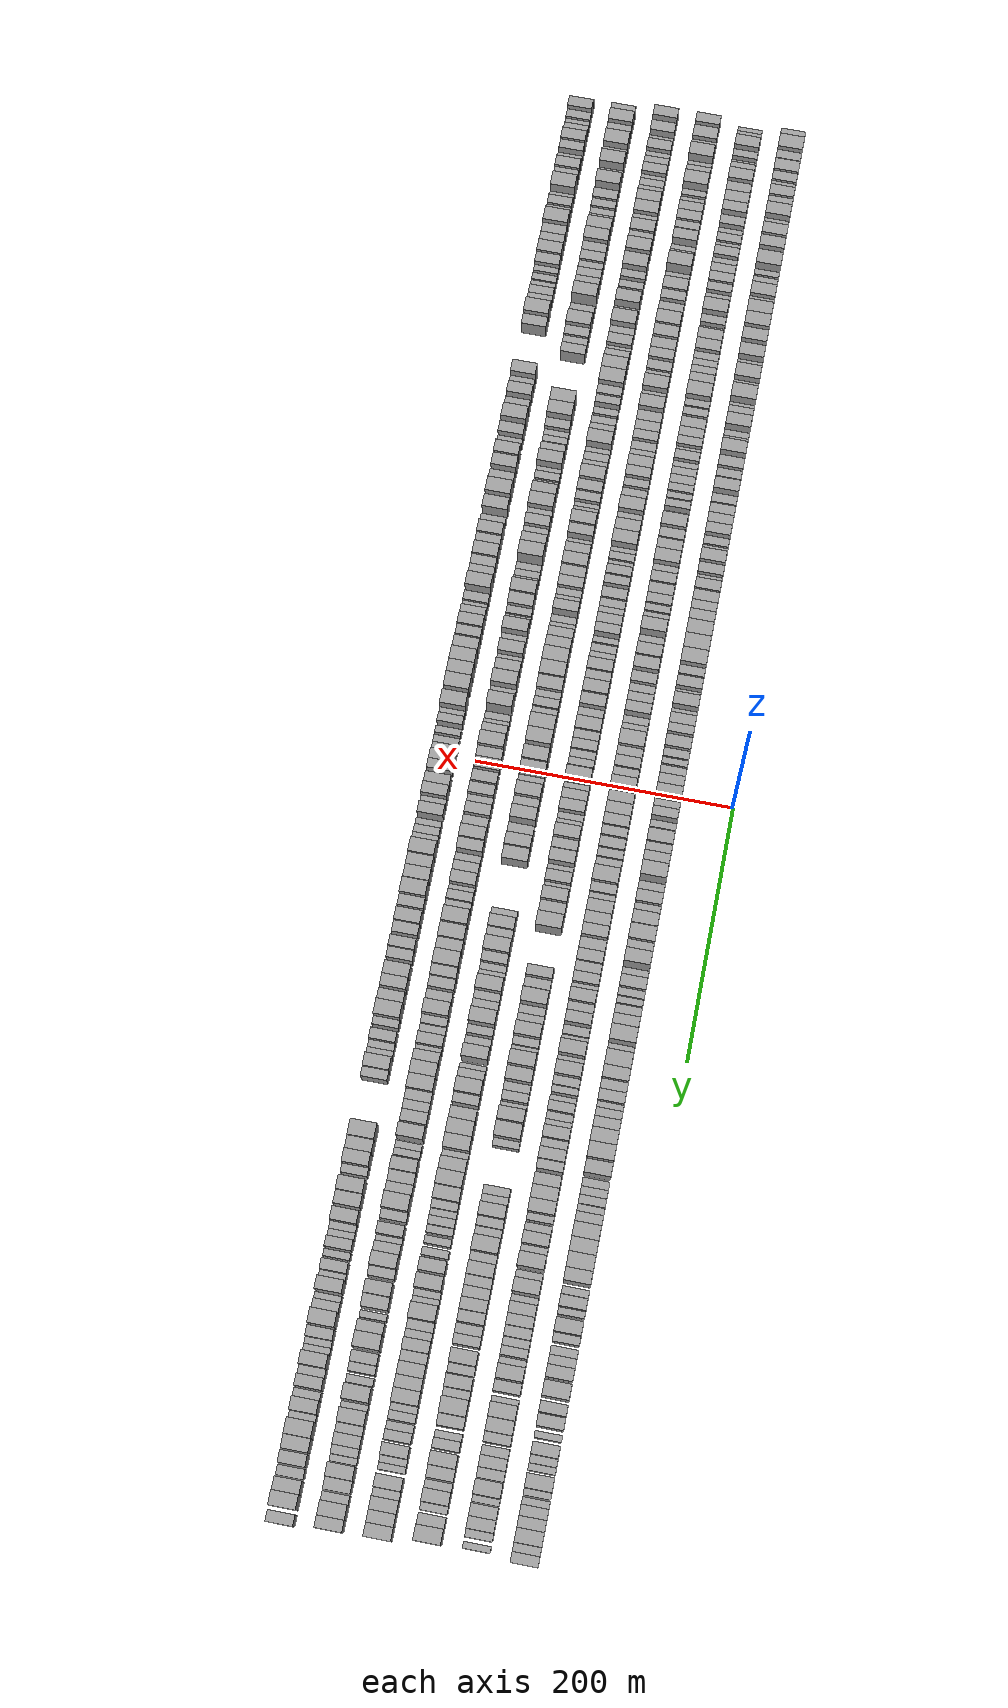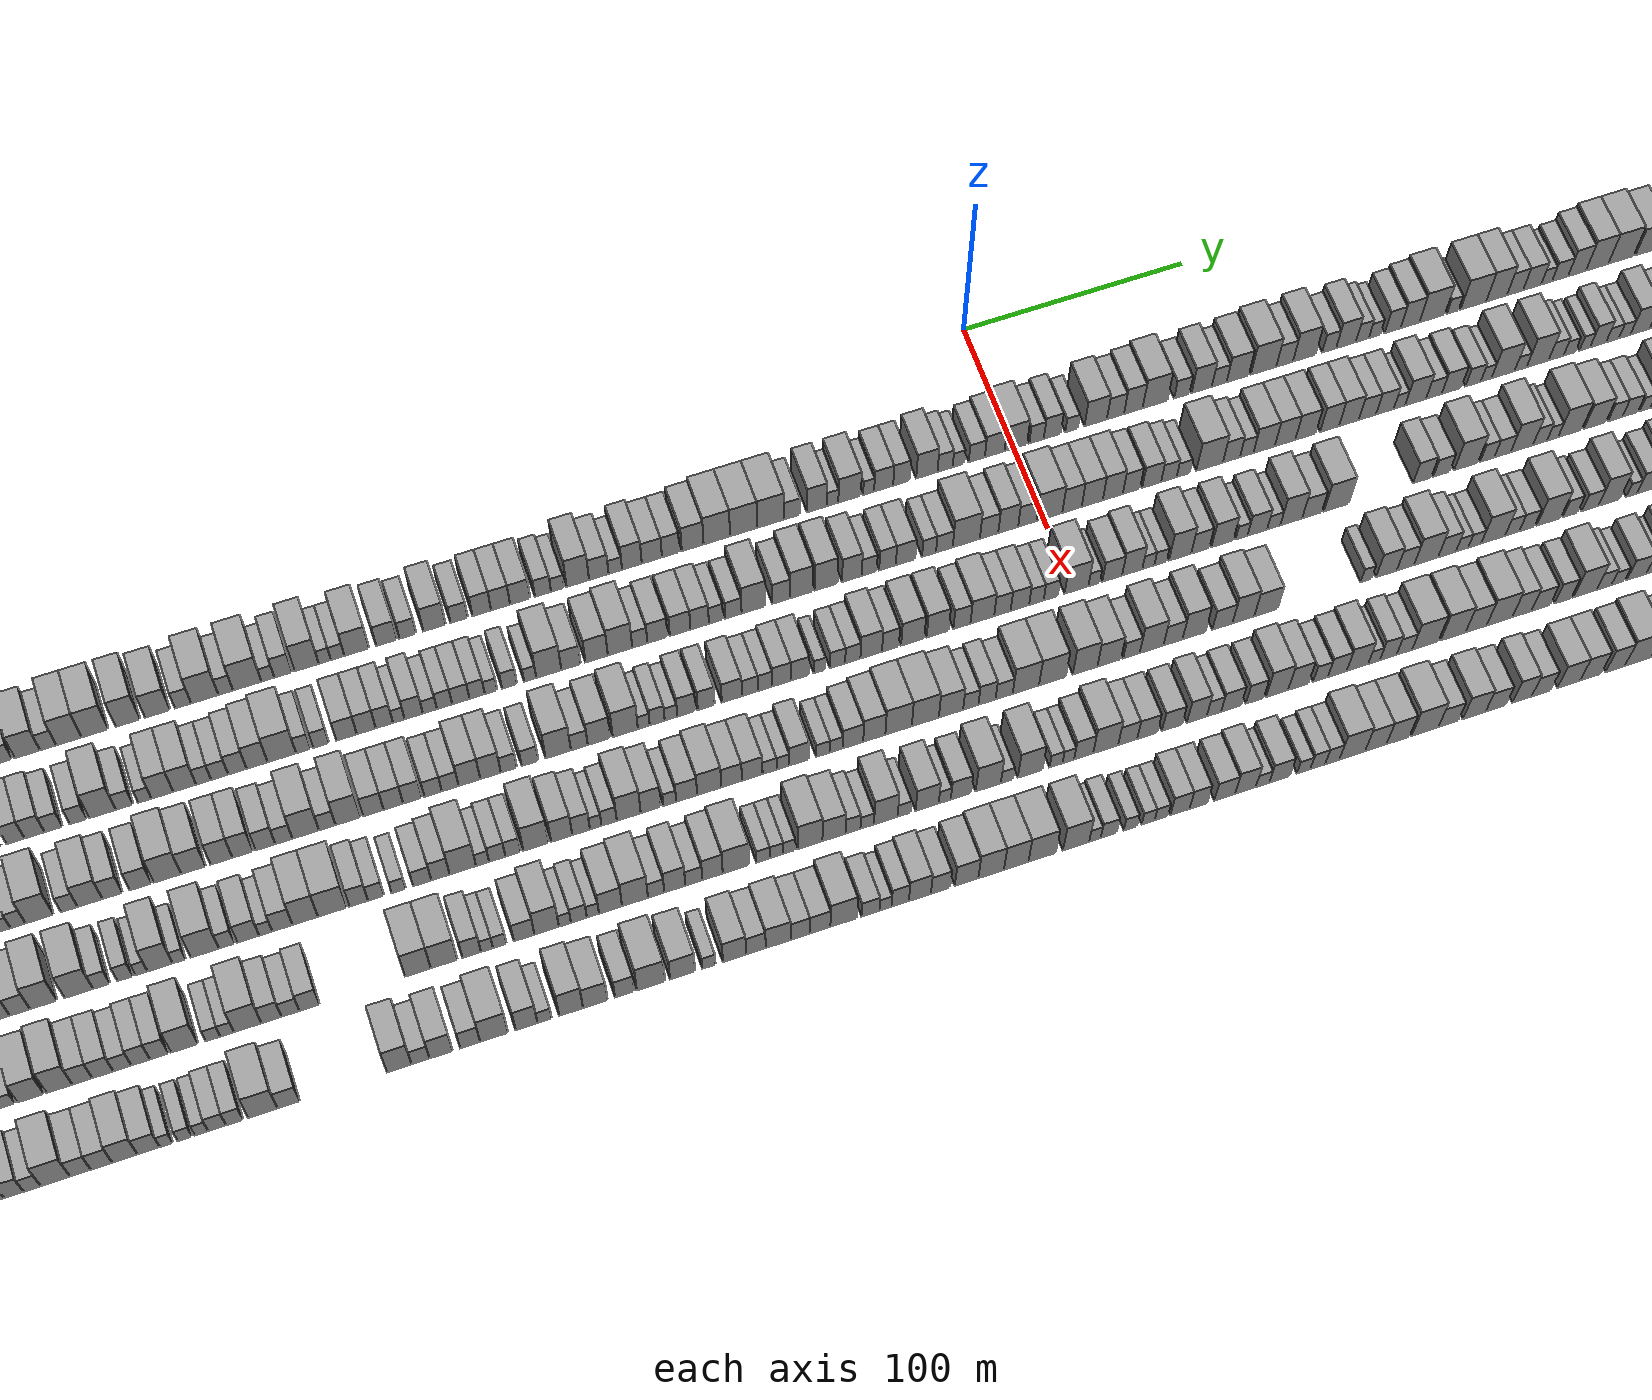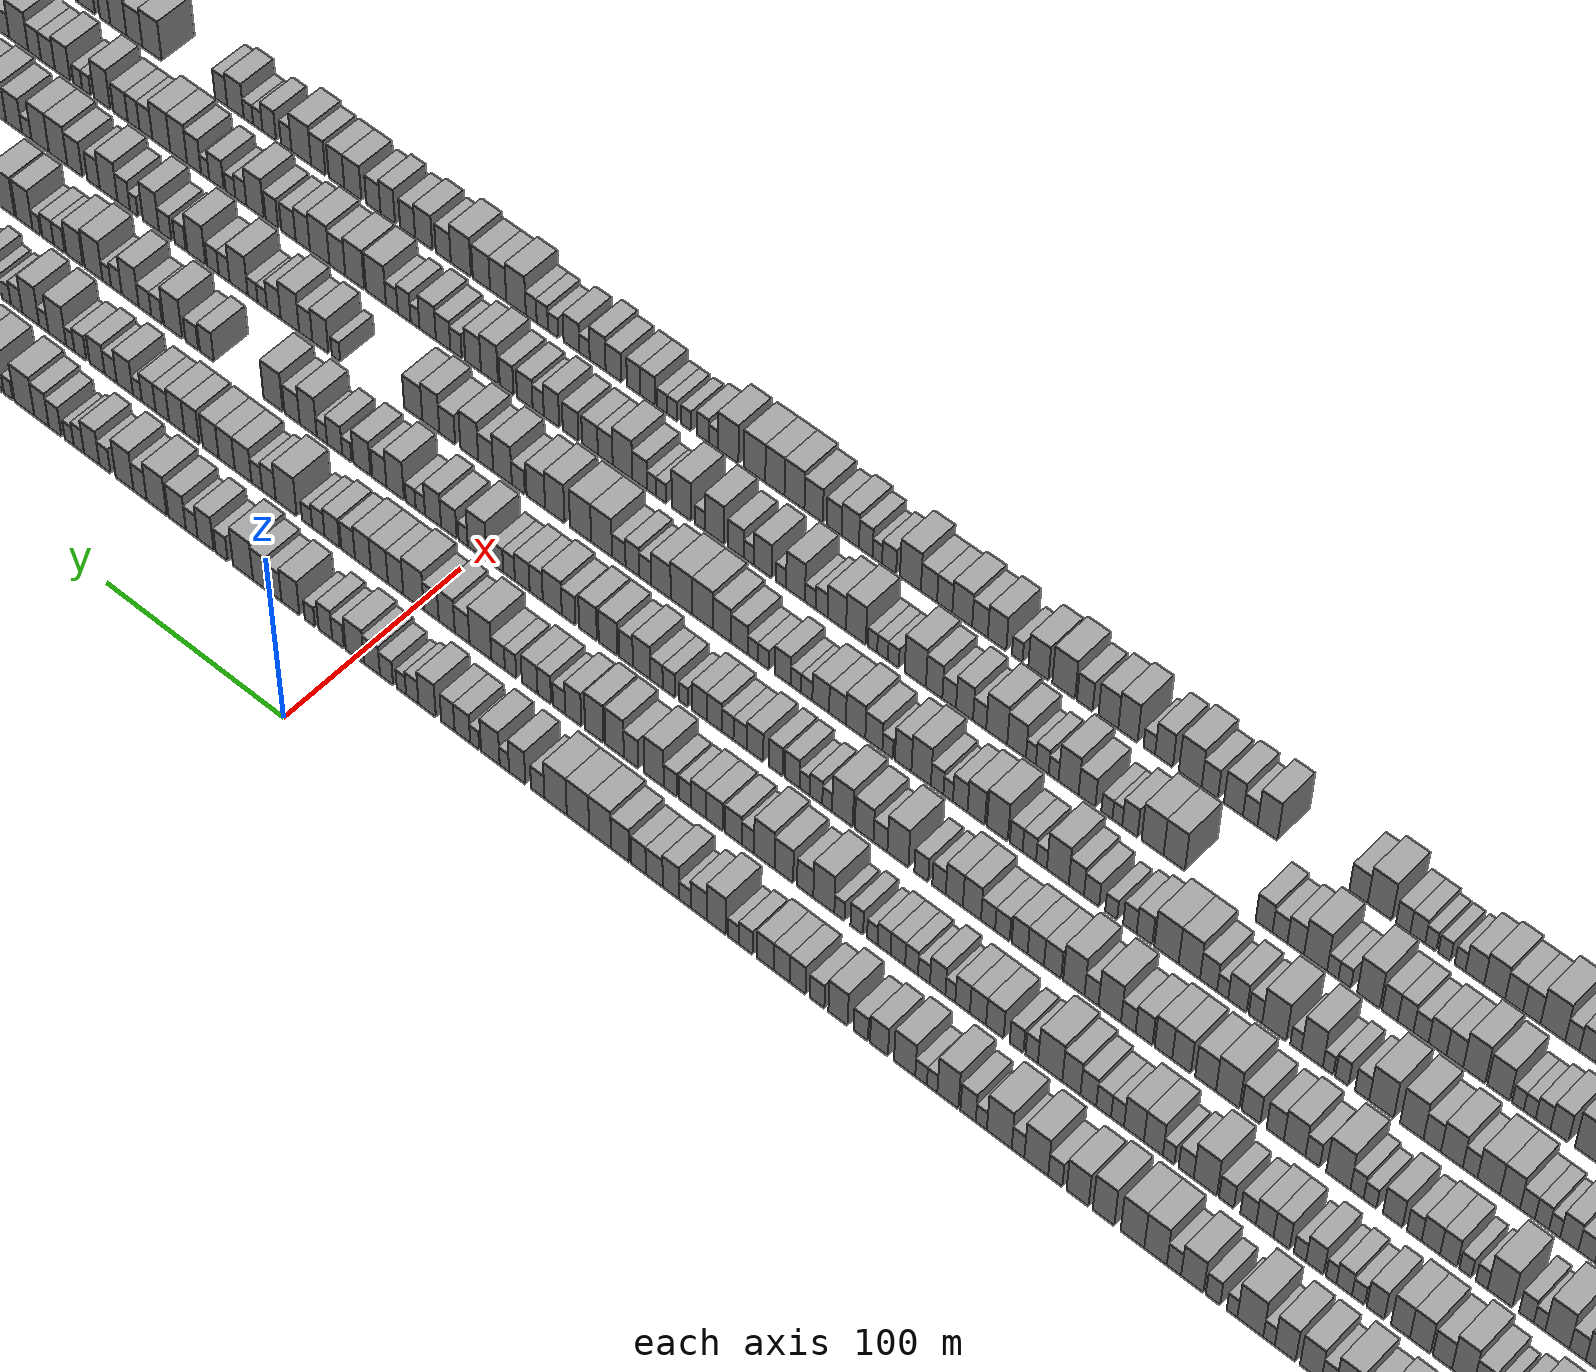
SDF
<sdf version="1.6">
 <world name="default">
  <scene>
   <sky><clouds><speed>12</speed></clouds></sky>
   <ambient>0.4 0.4 0.4 1</ambient>
   <background>0.7 0.7 0.7 1</background>
   <shadows>1</shadows>
  </scene>
  <gravity>0 0 -9.8066</gravity>
  <magnetic_field>6e-06 2.3e-05 -4.2e-05</magnetic_field>
  <physics default="0" name="default_physics" type="ode">
   <ode>
    <solver>
     <type>quick</type>
     <iters>10</iters>
     <sor>1.0</sor>
     <use_dynamic_moi_rescaling>0</use_dynamic_moi_rescaling>
    </solver>
    <constraints>
     <cfm>0</cfm>
     <erp>0.2</erp>
     <contact_max_correcting_vel>100</contact_max_correcting_vel>
     <contact_surface_layer>0.001</contact_surface_layer>
    </constraints>
   </ode>
   <max_step_size>0.004</max_step_size>
   <real_time_factor>1</real_time_factor>
   <real_time_update_rate>250</real_time_update_rate>
  </physics>
  <light name="sun" type="directional">
   <pose>0 0 10 0 0 0</pose>
   <diffuse>0.8 0.8 0.8 1</diffuse>
   <specular>0.2 0.2 0.2 1</specular>
   <attenuation>
    <range>1000</range>
    <constant>0.9</constant>
    <linear>0.01</linear>
    <quadratic>0.001</quadratic>
   </attenuation>
   <direction>-0.5 0.1 -0.9</direction>
  </light>
  <model name="building_1">
   <static>1</static>
   <pose>50.0000 -566.0285 0 0.000000 0.000000 0.000000</pose>
   <link name="link">
    <pose>0 0 9.00 0 0 0</pose>
    <collision name="collision"><geometry><box><size>20.0000 7.9430 18.0000</size></box></geometry></collision>
    <visual name="visual">
     <cast_shadows>0</cast_shadows>
     <geometry><box><size>20.0000 7.9430 18.0000</size></box></geometry>
     <material>
      <script>
       <uri>model://grey_wall/materials/scripts</uri>
       <uri>model://grey_wall/materials/textures</uri>
       <name>vrc/grey_wall</name>
      </script>
     </material>
    </visual>
   </link>
  </model>
  <model name="building_2">
   <static>1</static>
   <pose>50.0000 -556.2195 0 0.000000 0.000000 0.000000</pose>
   <link name="link">
    <pose>0 0 12.00 0 0 0</pose>
    <collision name="collision"><geometry><box><size>20.0000 11.6750 24.0000</size></box></geometry></collision>
    <visual name="visual">
     <cast_shadows>0</cast_shadows>
     <geometry><box><size>20.0000 11.6750 24.0000</size></box></geometry>
     <material>
      <script>
       <uri>model://grey_wall/materials/scripts</uri>
       <uri>model://grey_wall/materials/textures</uri>
       <name>vrc/grey_wall</name>
      </script>
     </material>
    </visual>
   </link>
  </model>
  <model name="building_3">
   <static>1</static>
   <pose>50.0000 -546.7149 0 0.000000 0.000000 0.000000</pose>
   <link name="link">
    <pose>0 0 9.00 0 0 0</pose>
    <collision name="collision"><geometry><box><size>20.0000 7.3342 18.0000</size></box></geometry></collision>
    <visual name="visual">
     <cast_shadows>0</cast_shadows>
     <geometry><box><size>20.0000 7.3342 18.0000</size></box></geometry>
     <material>
      <script>
       <uri>model://grey_wall/materials/scripts</uri>
       <uri>model://grey_wall/materials/textures</uri>
       <name>vrc/grey_wall</name>
      </script>
     </material>
    </visual>
   </link>
  </model>
  <model name="building_4">
   <static>1</static>
   <pose>50.0000 -536.1963 0 0.000000 0.000000 0.000000</pose>
   <link name="link">
    <pose>0 0 10.50 0 0 0</pose>
    <collision name="collision"><geometry><box><size>20.0000 9.7029 21.0000</size></box></geometry></collision>
    <visual name="visual">
     <cast_shadows>0</cast_shadows>
     <geometry><box><size>20.0000 9.7029 21.0000</size></box></geometry>
     <material>
      <script>
       <uri>model://grey_wall/materials/scripts</uri>
       <uri>model://grey_wall/materials/textures</uri>
       <name>vrc/grey_wall</name>
      </script>
     </material>
    </visual>
   </link>
  </model>
  <model name="building_5">
   <static>1</static>
   <pose>50.0000 -527.3998 0 0.000000 0.000000 0.000000</pose>
   <link name="link">
    <pose>0 0 9.00 0 0 0</pose>
    <collision name="collision"><geometry><box><size>20.0000 7.8903 18.0000</size></box></geometry></collision>
    <visual name="visual">
     <cast_shadows>0</cast_shadows>
     <geometry><box><size>20.0000 7.8903 18.0000</size></box></geometry>
     <material>
      <script>
       <uri>model://grey_wall/materials/scripts</uri>
       <uri>model://grey_wall/materials/textures</uri>
       <name>vrc/grey_wall</name>
      </script>
     </material>
    </visual>
   </link>
  </model>
  <model name="building_6">
   <static>1</static>
   <pose>50.0000 -520.4221 0 0.000000 0.000000 0.000000</pose>
   <link name="link">
    <pose>0 0 7.50 0 0 0</pose>
    <collision name="collision"><geometry><box><size>20.0000 6.0649 15.0000</size></box></geometry></collision>
    <visual name="visual">
     <cast_shadows>0</cast_shadows>
     <geometry><box><size>20.0000 6.0649 15.0000</size></box></geometry>
     <material>
      <script>
       <uri>model://grey_wall/materials/scripts</uri>
       <uri>model://grey_wall/materials/textures</uri>
       <name>vrc/grey_wall</name>
      </script>
     </material>
    </visual>
   </link>
  </model>
  <model name="building_7">
   <static>1</static>
   <pose>50.0000 -512.9245 0 0.000000 0.000000 0.000000</pose>
   <link name="link">
    <pose>0 0 10.50 0 0 0</pose>
    <collision name="collision"><geometry><box><size>20.0000 8.9303 21.0000</size></box></geometry></collision>
    <visual name="visual">
     <cast_shadows>0</cast_shadows>
     <geometry><box><size>20.0000 8.9303 21.0000</size></box></geometry>
     <material>
      <script>
       <uri>model://grey_wall/materials/scripts</uri>
       <uri>model://grey_wall/materials/textures</uri>
       <name>vrc/grey_wall</name>
      </script>
     </material>
    </visual>
   </link>
  </model>
  <model name="building_8">
   <static>1</static>
   <pose>50.0000 -504.2603 0 0.000000 0.000000 0.000000</pose>
   <link name="link">
    <pose>0 0 9.00 0 0 0</pose>
    <collision name="collision"><geometry><box><size>20.0000 8.3981 18.0000</size></box></geometry></collision>
    <visual name="visual">
     <cast_shadows>0</cast_shadows>
     <geometry><box><size>20.0000 8.3981 18.0000</size></box></geometry>
     <material>
      <script>
       <uri>model://grey_wall/materials/scripts</uri>
       <uri>model://grey_wall/materials/textures</uri>
       <name>vrc/grey_wall</name>
      </script>
     </material>
    </visual>
   </link>
  </model>
  <model name="building_9">
   <static>1</static>
   <pose>50.0000 -494.7629 0 0.000000 0.000000 0.000000</pose>
   <link name="link">
    <pose>0 0 12.00 0 0 0</pose>
    <collision name="collision"><geometry><box><size>20.0000 10.5967 24.0000</size></box></geometry></collision>
    <visual name="visual">
     <cast_shadows>0</cast_shadows>
     <geometry><box><size>20.0000 10.5967 24.0000</size></box></geometry>
     <material>
      <script>
       <uri>model://grey_wall/materials/scripts</uri>
       <uri>model://grey_wall/materials/textures</uri>
       <name>vrc/grey_wall</name>
      </script>
     </material>
    </visual>
   </link>
  </model>
  <model name="building_10">
   <static>1</static>
   <pose>50.0000 -486.3562 0 0.000000 0.000000 0.000000</pose>
   <link name="link">
    <pose>0 0 7.50 0 0 0</pose>
    <collision name="collision"><geometry><box><size>20.0000 6.2167 15.0000</size></box></geometry></collision>
    <visual name="visual">
     <cast_shadows>0</cast_shadows>
     <geometry><box><size>20.0000 6.2167 15.0000</size></box></geometry>
     <material>
      <script>
       <uri>model://grey_wall/materials/scripts</uri>
       <uri>model://grey_wall/materials/textures</uri>
       <name>vrc/grey_wall</name>
      </script>
     </material>
    </visual>
   </link>
  </model>
  <model name="building_11">
   <static>1</static>
   <pose>50.0000 -478.4223 0 0.000000 0.000000 0.000000</pose>
   <link name="link">
    <pose>0 0 10.50 0 0 0</pose>
    <collision name="collision"><geometry><box><size>20.0000 9.6512 21.0000</size></box></geometry></collision>
    <visual name="visual">
     <cast_shadows>0</cast_shadows>
     <geometry><box><size>20.0000 9.6512 21.0000</size></box></geometry>
     <material>
      <script>
       <uri>model://grey_wall/materials/scripts</uri>
       <uri>model://grey_wall/materials/textures</uri>
       <name>vrc/grey_wall</name>
      </script>
     </material>
    </visual>
   </link>
  </model>
  <model name="building_12">
   <static>1</static>
   <pose>50.0000 -466.8531 0 0.000000 0.000000 0.000000</pose>
   <link name="link">
    <pose>0 0 10.50 0 0 0</pose>
    <collision name="collision"><geometry><box><size>20.0000 9.4872 21.0000</size></box></geometry></collision>
    <visual name="visual">
     <cast_shadows>0</cast_shadows>
     <geometry><box><size>20.0000 9.4872 21.0000</size></box></geometry>
     <material>
      <script>
       <uri>model://grey_wall/materials/scripts</uri>
       <uri>model://grey_wall/materials/textures</uri>
       <name>vrc/grey_wall</name>
      </script>
     </material>
    </visual>
   </link>
  </model>
  <model name="building_13">
   <static>1</static>
   <pose>50.0000 -459.4603 0 0.000000 0.000000 0.000000</pose>
   <link name="link">
    <pose>0 0 6.00 0 0 0</pose>
    <collision name="collision"><geometry><box><size>20.0000 5.2984 12.0000</size></box></geometry></collision>
    <visual name="visual">
     <cast_shadows>0</cast_shadows>
     <geometry><box><size>20.0000 5.2984 12.0000</size></box></geometry>
     <material>
      <script>
       <uri>model://grey_wall/materials/scripts</uri>
       <uri>model://grey_wall/materials/textures</uri>
       <name>vrc/grey_wall</name>
      </script>
     </material>
    </visual>
   </link>
  </model>
  <model name="building_14">
   <static>1</static>
   <pose>50.0000 -450.8543 0 0.000000 0.000000 0.000000</pose>
   <link name="link">
    <pose>0 0 12.00 0 0 0</pose>
    <collision name="collision"><geometry><box><size>20.0000 11.9135 24.0000</size></box></geometry></collision>
    <visual name="visual">
     <cast_shadows>0</cast_shadows>
     <geometry><box><size>20.0000 11.9135 24.0000</size></box></geometry>
     <material>
      <script>
       <uri>model://grey_wall/materials/scripts</uri>
       <uri>model://grey_wall/materials/textures</uri>
       <name>vrc/grey_wall</name>
      </script>
     </material>
    </visual>
   </link>
  </model>
  <model name="building_15">
   <static>1</static>
   <pose>50.0000 -442.4723 0 0.000000 0.000000 0.000000</pose>
   <link name="link">
    <pose>0 0 6.00 0 0 0</pose>
    <collision name="collision"><geometry><box><size>20.0000 4.8505 12.0000</size></box></geometry></collision>
    <visual name="visual">
     <cast_shadows>0</cast_shadows>
     <geometry><box><size>20.0000 4.8505 12.0000</size></box></geometry>
     <material>
      <script>
       <uri>model://grey_wall/materials/scripts</uri>
       <uri>model://grey_wall/materials/textures</uri>
       <name>vrc/grey_wall</name>
      </script>
     </material>
    </visual>
   </link>
  </model>
  <model name="building_16">
   <static>1</static>
   <pose>50.0000 -433.7049 0 0.000000 0.000000 0.000000</pose>
   <link name="link">
    <pose>0 0 7.50 0 0 0</pose>
    <collision name="collision"><geometry><box><size>20.0000 6.6844 15.0000</size></box></geometry></collision>
    <visual name="visual">
     <cast_shadows>0</cast_shadows>
     <geometry><box><size>20.0000 6.6844 15.0000</size></box></geometry>
     <material>
      <script>
       <uri>model://grey_wall/materials/scripts</uri>
       <uri>model://grey_wall/materials/textures</uri>
       <name>vrc/grey_wall</name>
      </script>
     </material>
    </visual>
   </link>
  </model>
  <model name="building_17">
   <static>1</static>
   <pose>50.0000 -424.1351 0 0.000000 0.000000 0.000000</pose>
   <link name="link">
    <pose>0 0 10.50 0 0 0</pose>
    <collision name="collision"><geometry><box><size>20.0000 10.4550 21.0000</size></box></geometry></collision>
    <visual name="visual">
     <cast_shadows>0</cast_shadows>
     <geometry><box><size>20.0000 10.4550 21.0000</size></box></geometry>
     <material>
      <script>
       <uri>model://grey_wall/materials/scripts</uri>
       <uri>model://grey_wall/materials/textures</uri>
       <name>vrc/grey_wall</name>
      </script>
     </material>
    </visual>
   </link>
  </model>
  <model name="building_18">
   <static>1</static>
   <pose>50.0000 -415.5861 0 0.000000 0.000000 0.000000</pose>
   <link name="link">
    <pose>0 0 7.50 0 0 0</pose>
    <collision name="collision"><geometry><box><size>20.0000 6.6431 15.0000</size></box></geometry></collision>
    <visual name="visual">
     <cast_shadows>0</cast_shadows>
     <geometry><box><size>20.0000 6.6431 15.0000</size></box></geometry>
     <material>
      <script>
       <uri>model://grey_wall/materials/scripts</uri>
       <uri>model://grey_wall/materials/textures</uri>
       <name>vrc/grey_wall</name>
      </script>
     </material>
    </visual>
   </link>
  </model>
  <model name="building_19">
   <static>1</static>
   <pose>50.0000 -406.9946 0 0.000000 0.000000 0.000000</pose>
   <link name="link">
    <pose>0 0 12.00 0 0 0</pose>
    <collision name="collision"><geometry><box><size>20.0000 10.5398 24.0000</size></box></geometry></collision>
    <visual name="visual">
     <cast_shadows>0</cast_shadows>
     <geometry><box><size>20.0000 10.5398 24.0000</size></box></geometry>
     <material>
      <script>
       <uri>model://grey_wall/materials/scripts</uri>
       <uri>model://grey_wall/materials/textures</uri>
       <name>vrc/grey_wall</name>
      </script>
     </material>
    </visual>
   </link>
  </model>
  <model name="building_20">
   <static>1</static>
   <pose>50.0000 -396.1728 0 0.000000 0.000000 0.000000</pose>
   <link name="link">
    <pose>0 0 12.00 0 0 0</pose>
    <collision name="collision"><geometry><box><size>20.0000 11.1037 24.0000</size></box></geometry></collision>
    <visual name="visual">
     <cast_shadows>0</cast_shadows>
     <geometry><box><size>20.0000 11.1037 24.0000</size></box></geometry>
     <material>
      <script>
       <uri>model://grey_wall/materials/scripts</uri>
       <uri>model://grey_wall/materials/textures</uri>
       <name>vrc/grey_wall</name>
      </script>
     </material>
    </visual>
   </link>
  </model>
  <model name="building_21">
   <static>1</static>
   <pose>50.0000 -382.5288 0 0.000000 0.000000 0.000000</pose>
   <link name="link">
    <pose>0 0 12.00 0 0 0</pose>
    <collision name="collision"><geometry><box><size>20.0000 10.1843 24.0000</size></box></geometry></collision>
    <visual name="visual">
     <cast_shadows>0</cast_shadows>
     <geometry><box><size>20.0000 10.1843 24.0000</size></box></geometry>
     <material>
      <script>
       <uri>model://grey_wall/materials/scripts</uri>
       <uri>model://grey_wall/materials/textures</uri>
       <name>vrc/grey_wall</name>
      </script>
     </material>
    </visual>
   </link>
  </model>
  <model name="building_22">
   <static>1</static>
   <pose>50.0000 -370.1990 0 0.000000 0.000000 0.000000</pose>
   <link name="link">
    <pose>0 0 10.50 0 0 0</pose>
    <collision name="collision"><geometry><box><size>20.0000 10.4753 21.0000</size></box></geometry></collision>
    <visual name="visual">
     <cast_shadows>0</cast_shadows>
     <geometry><box><size>20.0000 10.4753 21.0000</size></box></geometry>
     <material>
      <script>
       <uri>model://grey_wall/materials/scripts</uri>
       <uri>model://grey_wall/materials/textures</uri>
       <name>vrc/grey_wall</name>
      </script>
     </material>
    </visual>
   </link>
  </model>
  <model name="building_23">
   <static>1</static>
   <pose>50.0000 -359.5764 0 0.000000 0.000000 0.000000</pose>
   <link name="link">
    <pose>0 0 7.50 0 0 0</pose>
    <collision name="collision"><geometry><box><size>20.0000 6.7698 15.0000</size></box></geometry></collision>
    <visual name="visual">
     <cast_shadows>0</cast_shadows>
     <geometry><box><size>20.0000 6.7698 15.0000</size></box></geometry>
     <material>
      <script>
       <uri>model://grey_wall/materials/scripts</uri>
       <uri>model://grey_wall/materials/textures</uri>
       <name>vrc/grey_wall</name>
      </script>
     </material>
    </visual>
   </link>
  </model>
  <model name="building_24">
   <static>1</static>
   <pose>50.0000 -350.4727 0 0.000000 0.000000 0.000000</pose>
   <link name="link">
    <pose>0 0 12.00 0 0 0</pose>
    <collision name="collision"><geometry><box><size>20.0000 11.4377 24.0000</size></box></geometry></collision>
    <visual name="visual">
     <cast_shadows>0</cast_shadows>
     <geometry><box><size>20.0000 11.4377 24.0000</size></box></geometry>
     <material>
      <script>
       <uri>model://grey_wall/materials/scripts</uri>
       <uri>model://grey_wall/materials/textures</uri>
       <name>vrc/grey_wall</name>
      </script>
     </material>
    </visual>
   </link>
  </model>
  <model name="building_25">
   <static>1</static>
   <pose>50.0000 -341.7088 0 0.000000 0.000000 0.000000</pose>
   <link name="link">
    <pose>0 0 7.50 0 0 0</pose>
    <collision name="collision"><geometry><box><size>20.0000 6.0901 15.0000</size></box></geometry></collision>
    <visual name="visual">
     <cast_shadows>0</cast_shadows>
     <geometry><box><size>20.0000 6.0901 15.0000</size></box></geometry>
     <material>
      <script>
       <uri>model://grey_wall/materials/scripts</uri>
       <uri>model://grey_wall/materials/textures</uri>
       <name>vrc/grey_wall</name>
      </script>
     </material>
    </visual>
   </link>
  </model>
  <model name="building_26">
   <static>1</static>
   <pose>50.0000 -332.6822 0 0.000000 0.000000 0.000000</pose>
   <link name="link">
    <pose>0 0 12.00 0 0 0</pose>
    <collision name="collision"><geometry><box><size>20.0000 11.9631 24.0000</size></box></geometry></collision>
    <visual name="visual">
     <cast_shadows>0</cast_shadows>
     <geometry><box><size>20.0000 11.9631 24.0000</size></box></geometry>
     <material>
      <script>
       <uri>model://grey_wall/materials/scripts</uri>
       <uri>model://grey_wall/materials/textures</uri>
       <name>vrc/grey_wall</name>
      </script>
     </material>
    </visual>
   </link>
  </model>
  <model name="building_27">
   <static>1</static>
   <pose>50.0000 -324.0111 0 0.000000 0.000000 0.000000</pose>
   <link name="link">
    <pose>0 0 6.00 0 0 0</pose>
    <collision name="collision"><geometry><box><size>20.0000 5.3791 12.0000</size></box></geometry></collision>
    <visual name="visual">
     <cast_shadows>0</cast_shadows>
     <geometry><box><size>20.0000 5.3791 12.0000</size></box></geometry>
     <material>
      <script>
       <uri>model://grey_wall/materials/scripts</uri>
       <uri>model://grey_wall/materials/textures</uri>
       <name>vrc/grey_wall</name>
      </script>
     </material>
    </visual>
   </link>
  </model>
  <model name="building_28">
   <static>1</static>
   <pose>50.0000 -317.5810 0 0.000000 0.000000 0.000000</pose>
   <link name="link">
    <pose>0 0 9.00 0 0 0</pose>
    <collision name="collision"><geometry><box><size>20.0000 7.4811 18.0000</size></box></geometry></collision>
    <visual name="visual">
     <cast_shadows>0</cast_shadows>
     <geometry><box><size>20.0000 7.4811 18.0000</size></box></geometry>
     <material>
      <script>
       <uri>model://grey_wall/materials/scripts</uri>
       <uri>model://grey_wall/materials/textures</uri>
       <name>vrc/grey_wall</name>
      </script>
     </material>
    </visual>
   </link>
  </model>
  <model name="building_29">
   <static>1</static>
   <pose>50.0000 -307.7111 0 0.000000 0.000000 0.000000</pose>
   <link name="link">
    <pose>0 0 12.00 0 0 0</pose>
    <collision name="collision"><geometry><box><size>20.0000 10.2588 24.0000</size></box></geometry></collision>
    <visual name="visual">
     <cast_shadows>0</cast_shadows>
     <geometry><box><size>20.0000 10.2588 24.0000</size></box></geometry>
     <material>
      <script>
       <uri>model://grey_wall/materials/scripts</uri>
       <uri>model://grey_wall/materials/textures</uri>
       <name>vrc/grey_wall</name>
      </script>
     </material>
    </visual>
   </link>
  </model>
  <model name="building_30">
   <static>1</static>
   <pose>50.0000 -300.0173 0 0.000000 0.000000 0.000000</pose>
   <link name="link">
    <pose>0 0 6.00 0 0 0</pose>
    <collision name="collision"><geometry><box><size>20.0000 5.1288 12.0000</size></box></geometry></collision>
    <visual name="visual">
     <cast_shadows>0</cast_shadows>
     <geometry><box><size>20.0000 5.1288 12.0000</size></box></geometry>
     <material>
      <script>
       <uri>model://grey_wall/materials/scripts</uri>
       <uri>model://grey_wall/materials/textures</uri>
       <name>vrc/grey_wall</name>
      </script>
     </material>
    </visual>
   </link>
  </model>
  <model name="building_31">
   <static>1</static>
   <pose>50.0000 -294.6015 0 0.000000 0.000000 0.000000</pose>
   <link name="link">
    <pose>0 0 6.00 0 0 0</pose>
    <collision name="collision"><geometry><box><size>20.0000 5.7028 12.0000</size></box></geometry></collision>
    <visual name="visual">
     <cast_shadows>0</cast_shadows>
     <geometry><box><size>20.0000 5.7028 12.0000</size></box></geometry>
     <material>
      <script>
       <uri>model://grey_wall/materials/scripts</uri>
       <uri>model://grey_wall/materials/textures</uri>
       <name>vrc/grey_wall</name>
      </script>
     </material>
    </visual>
   </link>
  </model>
  <model name="building_32">
   <static>1</static>
   <pose>50.0000 -286.5215 0 0.000000 0.000000 0.000000</pose>
   <link name="link">
    <pose>0 0 10.50 0 0 0</pose>
    <collision name="collision"><geometry><box><size>20.0000 10.4572 21.0000</size></box></geometry></collision>
    <visual name="visual">
     <cast_shadows>0</cast_shadows>
     <geometry><box><size>20.0000 10.4572 21.0000</size></box></geometry>
     <material>
      <script>
       <uri>model://grey_wall/materials/scripts</uri>
       <uri>model://grey_wall/materials/textures</uri>
       <name>vrc/grey_wall</name>
      </script>
     </material>
    </visual>
   </link>
  </model>
  <model name="building_33">
   <static>1</static>
   <pose>50.0000 -273.8379 0 0.000000 0.000000 0.000000</pose>
   <link name="link">
    <pose>0 0 9.00 0 0 0</pose>
    <collision name="collision"><geometry><box><size>20.0000 8.9101 18.0000</size></box></geometry></collision>
    <visual name="visual">
     <cast_shadows>0</cast_shadows>
     <geometry><box><size>20.0000 8.9101 18.0000</size></box></geometry>
     <material>
      <script>
       <uri>model://grey_wall/materials/scripts</uri>
       <uri>model://grey_wall/materials/textures</uri>
       <name>vrc/grey_wall</name>
      </script>
     </material>
    </visual>
   </link>
  </model>
  <model name="building_34">
   <static>1</static>
   <pose>50.0000 -264.8228 0 0.000000 0.000000 0.000000</pose>
   <link name="link">
    <pose>0 0 7.50 0 0 0</pose>
    <collision name="collision"><geometry><box><size>20.0000 7.1200 15.0000</size></box></geometry></collision>
    <visual name="visual">
     <cast_shadows>0</cast_shadows>
     <geometry><box><size>20.0000 7.1200 15.0000</size></box></geometry>
     <material>
      <script>
       <uri>model://grey_wall/materials/scripts</uri>
       <uri>model://grey_wall/materials/textures</uri>
       <name>vrc/grey_wall</name>
      </script>
     </material>
    </visual>
   </link>
  </model>
  <model name="building_35">
   <static>1</static>
   <pose>50.0000 -253.4609 0 0.000000 0.000000 0.000000</pose>
   <link name="link">
    <pose>0 0 10.50 0 0 0</pose>
    <collision name="collision"><geometry><box><size>20.0000 9.6038 21.0000</size></box></geometry></collision>
    <visual name="visual">
     <cast_shadows>0</cast_shadows>
     <geometry><box><size>20.0000 9.6038 21.0000</size></box></geometry>
     <material>
      <script>
       <uri>model://grey_wall/materials/scripts</uri>
       <uri>model://grey_wall/materials/textures</uri>
       <name>vrc/grey_wall</name>
      </script>
     </material>
    </visual>
   </link>
  </model>
  <model name="building_36">
   <static>1</static>
   <pose>50.0000 -242.9369 0 0.000000 0.000000 0.000000</pose>
   <link name="link">
    <pose>0 0 7.50 0 0 0</pose>
    <collision name="collision"><geometry><box><size>20.0000 7.4442 15.0000</size></box></geometry></collision>
    <visual name="visual">
     <cast_shadows>0</cast_shadows>
     <geometry><box><size>20.0000 7.4442 15.0000</size></box></geometry>
     <material>
      <script>
       <uri>model://grey_wall/materials/scripts</uri>
       <uri>model://grey_wall/materials/textures</uri>
       <name>vrc/grey_wall</name>
      </script>
     </material>
    </visual>
   </link>
  </model>
  <model name="building_37">
   <static>1</static>
   <pose>50.0000 -233.2321 0 0.000000 0.000000 0.000000</pose>
   <link name="link">
    <pose>0 0 9.00 0 0 0</pose>
    <collision name="collision"><geometry><box><size>20.0000 7.9655 18.0000</size></box></geometry></collision>
    <visual name="visual">
     <cast_shadows>0</cast_shadows>
     <geometry><box><size>20.0000 7.9655 18.0000</size></box></geometry>
     <material>
      <script>
       <uri>model://grey_wall/materials/scripts</uri>
       <uri>model://grey_wall/materials/textures</uri>
       <name>vrc/grey_wall</name>
      </script>
     </material>
    </visual>
   </link>
  </model>
  <model name="building_38">
   <static>1</static>
   <pose>50.0000 -225.1872 0 0.000000 0.000000 0.000000</pose>
   <link name="link">
    <pose>0 0 9.00 0 0 0</pose>
    <collision name="collision"><geometry><box><size>20.0000 8.1243 18.0000</size></box></geometry></collision>
    <visual name="visual">
     <cast_shadows>0</cast_shadows>
     <geometry><box><size>20.0000 8.1243 18.0000</size></box></geometry>
     <material>
      <script>
       <uri>model://grey_wall/materials/scripts</uri>
       <uri>model://grey_wall/materials/textures</uri>
       <name>vrc/grey_wall</name>
      </script>
     </material>
    </visual>
   </link>
  </model>
  <model name="building_39">
   <static>1</static>
   <pose>50.0000 -216.7976 0 0.000000 0.000000 0.000000</pose>
   <link name="link">
    <pose>0 0 9.00 0 0 0</pose>
    <collision name="collision"><geometry><box><size>20.0000 8.6549 18.0000</size></box></geometry></collision>
    <visual name="visual">
     <cast_shadows>0</cast_shadows>
     <geometry><box><size>20.0000 8.6549 18.0000</size></box></geometry>
     <material>
      <script>
       <uri>model://grey_wall/materials/scripts</uri>
       <uri>model://grey_wall/materials/textures</uri>
       <name>vrc/grey_wall</name>
      </script>
     </material>
    </visual>
   </link>
  </model>
  <model name="building_40">
   <static>1</static>
   <pose>50.0000 -206.9964 0 0.000000 0.000000 0.000000</pose>
   <link name="link">
    <pose>0 0 7.50 0 0 0</pose>
    <collision name="collision"><geometry><box><size>20.0000 6.9475 15.0000</size></box></geometry></collision>
    <visual name="visual">
     <cast_shadows>0</cast_shadows>
     <geometry><box><size>20.0000 6.9475 15.0000</size></box></geometry>
     <material>
      <script>
       <uri>model://grey_wall/materials/scripts</uri>
       <uri>model://grey_wall/materials/textures</uri>
       <name>vrc/grey_wall</name>
      </script>
     </material>
    </visual>
   </link>
  </model>
  <model name="building_41">
   <static>1</static>
   <pose>50.0000 -200.6761 0 0.000000 0.000000 0.000000</pose>
   <link name="link">
    <pose>0 0 6.00 0 0 0</pose>
    <collision name="collision"><geometry><box><size>20.0000 5.6931 12.0000</size></box></geometry></collision>
    <visual name="visual">
     <cast_shadows>0</cast_shadows>
     <geometry><box><size>20.0000 5.6931 12.0000</size></box></geometry>
     <material>
      <script>
       <uri>model://grey_wall/materials/scripts</uri>
       <uri>model://grey_wall/materials/textures</uri>
       <name>vrc/grey_wall</name>
      </script>
     </material>
    </visual>
   </link>
  </model>
  <model name="building_42">
   <static>1</static>
   <pose>50.0000 -191.9709 0 0.000000 0.000000 0.000000</pose>
   <link name="link">
    <pose>0 0 12.00 0 0 0</pose>
    <collision name="collision"><geometry><box><size>20.0000 9.7174 24.0000</size></box></geometry></collision>
    <visual name="visual">
     <cast_shadows>0</cast_shadows>
     <geometry><box><size>20.0000 9.7174 24.0000</size></box></geometry>
     <material>
      <script>
       <uri>model://grey_wall/materials/scripts</uri>
       <uri>model://grey_wall/materials/textures</uri>
       <name>vrc/grey_wall</name>
      </script>
     </material>
    </visual>
   </link>
  </model>
  <model name="building_43">
   <static>1</static>
   <pose>50.0000 -182.9025 0 0.000000 0.000000 0.000000</pose>
   <link name="link">
    <pose>0 0 9.00 0 0 0</pose>
    <collision name="collision"><geometry><box><size>20.0000 8.4193 18.0000</size></box></geometry></collision>
    <visual name="visual">
     <cast_shadows>0</cast_shadows>
     <geometry><box><size>20.0000 8.4193 18.0000</size></box></geometry>
     <material>
      <script>
       <uri>model://grey_wall/materials/scripts</uri>
       <uri>model://grey_wall/materials/textures</uri>
       <name>vrc/grey_wall</name>
      </script>
     </material>
    </visual>
   </link>
  </model>
  <model name="building_44">
   <static>1</static>
   <pose>50.0000 -175.7633 0 0.000000 0.000000 0.000000</pose>
   <link name="link">
    <pose>0 0 6.00 0 0 0</pose>
    <collision name="collision"><geometry><box><size>20.0000 5.8592 12.0000</size></box></geometry></collision>
    <visual name="visual">
     <cast_shadows>0</cast_shadows>
     <geometry><box><size>20.0000 5.8592 12.0000</size></box></geometry>
     <material>
      <script>
       <uri>model://grey_wall/materials/scripts</uri>
       <uri>model://grey_wall/materials/textures</uri>
       <name>vrc/grey_wall</name>
      </script>
     </material>
    </visual>
   </link>
  </model>
  <model name="building_45">
   <static>1</static>
   <pose>50.0000 -168.5602 0 0.000000 0.000000 0.000000</pose>
   <link name="link">
    <pose>0 0 10.50 0 0 0</pose>
    <collision name="collision"><geometry><box><size>20.0000 8.5470 21.0000</size></box></geometry></collision>
    <visual name="visual">
     <cast_shadows>0</cast_shadows>
     <geometry><box><size>20.0000 8.5470 21.0000</size></box></geometry>
     <material>
      <script>
       <uri>model://grey_wall/materials/scripts</uri>
       <uri>model://grey_wall/materials/textures</uri>
       <name>vrc/grey_wall</name>
      </script>
     </material>
    </visual>
   </link>
  </model>
  <model name="building_46">
   <static>1</static>
   <pose>50.0000 -159.9026 0 0.000000 0.000000 0.000000</pose>
   <link name="link">
    <pose>0 0 9.00 0 0 0</pose>
    <collision name="collision"><geometry><box><size>20.0000 8.7682 18.0000</size></box></geometry></collision>
    <visual name="visual">
     <cast_shadows>0</cast_shadows>
     <geometry><box><size>20.0000 8.7682 18.0000</size></box></geometry>
     <material>
      <script>
       <uri>model://grey_wall/materials/scripts</uri>
       <uri>model://grey_wall/materials/textures</uri>
       <name>vrc/grey_wall</name>
      </script>
     </material>
    </visual>
   </link>
  </model>
  <model name="building_47">
   <static>1</static>
   <pose>50.0000 -151.7226 0 0.000000 0.000000 0.000000</pose>
   <link name="link">
    <pose>0 0 9.00 0 0 0</pose>
    <collision name="collision"><geometry><box><size>20.0000 7.5918 18.0000</size></box></geometry></collision>
    <visual name="visual">
     <cast_shadows>0</cast_shadows>
     <geometry><box><size>20.0000 7.5918 18.0000</size></box></geometry>
     <material>
      <script>
       <uri>model://grey_wall/materials/scripts</uri>
       <uri>model://grey_wall/materials/textures</uri>
       <name>vrc/grey_wall</name>
      </script>
     </material>
    </visual>
   </link>
  </model>
  <model name="building_48">
   <static>1</static>
   <pose>50.0000 -142.1726 0 0.000000 0.000000 0.000000</pose>
   <link name="link">
    <pose>0 0 10.50 0 0 0</pose>
    <collision name="collision"><geometry><box><size>20.0000 9.5083 21.0000</size></box></geometry></collision>
    <visual name="visual">
     <cast_shadows>0</cast_shadows>
     <geometry><box><size>20.0000 9.5083 21.0000</size></box></geometry>
     <material>
      <script>
       <uri>model://grey_wall/materials/scripts</uri>
       <uri>model://grey_wall/materials/textures</uri>
       <name>vrc/grey_wall</name>
      </script>
     </material>
    </visual>
   </link>
  </model>
  <model name="building_49">
   <static>1</static>
   <pose>50.0000 -131.6362 0 0.000000 0.000000 0.000000</pose>
   <link name="link">
    <pose>0 0 12.00 0 0 0</pose>
    <collision name="collision"><geometry><box><size>20.0000 11.5646 24.0000</size></box></geometry></collision>
    <visual name="visual">
     <cast_shadows>0</cast_shadows>
     <geometry><box><size>20.0000 11.5646 24.0000</size></box></geometry>
     <material>
      <script>
       <uri>model://grey_wall/materials/scripts</uri>
       <uri>model://grey_wall/materials/textures</uri>
       <name>vrc/grey_wall</name>
      </script>
     </material>
    </visual>
   </link>
  </model>
  <model name="building_50">
   <static>1</static>
   <pose>50.0000 -119.9481 0 0.000000 0.000000 0.000000</pose>
   <link name="link">
    <pose>0 0 12.00 0 0 0</pose>
    <collision name="collision"><geometry><box><size>20.0000 11.8115 24.0000</size></box></geometry></collision>
    <visual name="visual">
     <cast_shadows>0</cast_shadows>
     <geometry><box><size>20.0000 11.8115 24.0000</size></box></geometry>
     <material>
      <script>
       <uri>model://grey_wall/materials/scripts</uri>
       <uri>model://grey_wall/materials/textures</uri>
       <name>vrc/grey_wall</name>
      </script>
     </material>
    </visual>
   </link>
  </model>
  <model name="building_51">
   <static>1</static>
   <pose>50.0000 -108.1236 0 0.000000 0.000000 0.000000</pose>
   <link name="link">
    <pose>0 0 12.00 0 0 0</pose>
    <collision name="collision"><geometry><box><size>20.0000 11.8376 24.0000</size></box></geometry></collision>
    <visual name="visual">
     <cast_shadows>0</cast_shadows>
     <geometry><box><size>20.0000 11.8376 24.0000</size></box></geometry>
     <material>
      <script>
       <uri>model://grey_wall/materials/scripts</uri>
       <uri>model://grey_wall/materials/textures</uri>
       <name>vrc/grey_wall</name>
      </script>
     </material>
    </visual>
   </link>
  </model>
  <model name="building_52">
   <static>1</static>
   <pose>50.0000 -98.6287 0 0.000000 0.000000 0.000000</pose>
   <link name="link">
    <pose>0 0 7.50 0 0 0</pose>
    <collision name="collision"><geometry><box><size>20.0000 7.1521 15.0000</size></box></geometry></collision>
    <visual name="visual">
     <cast_shadows>0</cast_shadows>
     <geometry><box><size>20.0000 7.1521 15.0000</size></box></geometry>
     <material>
      <script>
       <uri>model://grey_wall/materials/scripts</uri>
       <uri>model://grey_wall/materials/textures</uri>
       <name>vrc/grey_wall</name>
      </script>
     </material>
    </visual>
   </link>
  </model>
  <model name="building_53">
   <static>1</static>
   <pose>50.0000 -87.6886 0 0.000000 0.000000 0.000000</pose>
   <link name="link">
    <pose>0 0 10.50 0 0 0</pose>
    <collision name="collision"><geometry><box><size>20.0000 8.7281 21.0000</size></box></geometry></collision>
    <visual name="visual">
     <cast_shadows>0</cast_shadows>
     <geometry><box><size>20.0000 8.7281 21.0000</size></box></geometry>
     <material>
      <script>
       <uri>model://grey_wall/materials/scripts</uri>
       <uri>model://grey_wall/materials/textures</uri>
       <name>vrc/grey_wall</name>
      </script>
     </material>
    </visual>
   </link>
  </model>
  <model name="building_54">
   <static>1</static>
   <pose>50.0000 -80.7984 0 0.000000 0.000000 0.000000</pose>
   <link name="link">
    <pose>0 0 6.00 0 0 0</pose>
    <collision name="collision"><geometry><box><size>20.0000 5.0522 12.0000</size></box></geometry></collision>
    <visual name="visual">
     <cast_shadows>0</cast_shadows>
     <geometry><box><size>20.0000 5.0522 12.0000</size></box></geometry>
     <material>
      <script>
       <uri>model://grey_wall/materials/scripts</uri>
       <uri>model://grey_wall/materials/textures</uri>
       <name>vrc/grey_wall</name>
      </script>
     </material>
    </visual>
   </link>
  </model>
  <model name="building_55">
   <static>1</static>
   <pose>50.0000 -73.2780 0 0.000000 0.000000 0.000000</pose>
   <link name="link">
    <pose>0 0 10.50 0 0 0</pose>
    <collision name="collision"><geometry><box><size>20.0000 9.9886 21.0000</size></box></geometry></collision>
    <visual name="visual">
     <cast_shadows>0</cast_shadows>
     <geometry><box><size>20.0000 9.9886 21.0000</size></box></geometry>
     <material>
      <script>
       <uri>model://grey_wall/materials/scripts</uri>
       <uri>model://grey_wall/materials/textures</uri>
       <name>vrc/grey_wall</name>
      </script>
     </material>
    </visual>
   </link>
  </model>
  <model name="building_56">
   <static>1</static>
   <pose>50.0000 -64.8513 0 0.000000 0.000000 0.000000</pose>
   <link name="link">
    <pose>0 0 6.00 0 0 0</pose>
    <collision name="collision"><geometry><box><size>20.0000 4.8649 12.0000</size></box></geometry></collision>
    <visual name="visual">
     <cast_shadows>0</cast_shadows>
     <geometry><box><size>20.0000 4.8649 12.0000</size></box></geometry>
     <material>
      <script>
       <uri>model://grey_wall/materials/scripts</uri>
       <uri>model://grey_wall/materials/textures</uri>
       <name>vrc/grey_wall</name>
      </script>
     </material>
    </visual>
   </link>
  </model>
  <model name="building_57">
   <static>1</static>
   <pose>50.0000 -58.1973 0 0.000000 0.000000 0.000000</pose>
   <link name="link">
    <pose>0 0 9.00 0 0 0</pose>
    <collision name="collision"><geometry><box><size>20.0000 8.4430 18.0000</size></box></geometry></collision>
    <visual name="visual">
     <cast_shadows>0</cast_shadows>
     <geometry><box><size>20.0000 8.4430 18.0000</size></box></geometry>
     <material>
      <script>
       <uri>model://grey_wall/materials/scripts</uri>
       <uri>model://grey_wall/materials/textures</uri>
       <name>vrc/grey_wall</name>
      </script>
     </material>
    </visual>
   </link>
  </model>
  <model name="building_58">
   <static>1</static>
   <pose>50.0000 -50.3721 0 0.000000 0.000000 0.000000</pose>
   <link name="link">
    <pose>0 0 9.00 0 0 0</pose>
    <collision name="collision"><geometry><box><size>20.0000 7.2076 18.0000</size></box></geometry></collision>
    <visual name="visual">
     <cast_shadows>0</cast_shadows>
     <geometry><box><size>20.0000 7.2076 18.0000</size></box></geometry>
     <material>
      <script>
       <uri>model://grey_wall/materials/scripts</uri>
       <uri>model://grey_wall/materials/textures</uri>
       <name>vrc/grey_wall</name>
      </script>
     </material>
    </visual>
   </link>
  </model>
  <model name="building_59">
   <static>1</static>
   <pose>50.0000 -39.0361 0 0.000000 0.000000 0.000000</pose>
   <link name="link">
    <pose>0 0 10.50 0 0 0</pose>
    <collision name="collision"><geometry><box><size>20.0000 9.4644 21.0000</size></box></geometry></collision>
    <visual name="visual">
     <cast_shadows>0</cast_shadows>
     <geometry><box><size>20.0000 9.4644 21.0000</size></box></geometry>
     <material>
      <script>
       <uri>model://grey_wall/materials/scripts</uri>
       <uri>model://grey_wall/materials/textures</uri>
       <name>vrc/grey_wall</name>
      </script>
     </material>
    </visual>
   </link>
  </model>
  <model name="building_60">
   <static>1</static>
   <pose>50.0000 -30.9125 0 0.000000 0.000000 0.000000</pose>
   <link name="link">
    <pose>0 0 7.50 0 0 0</pose>
    <collision name="collision"><geometry><box><size>20.0000 6.7827 15.0000</size></box></geometry></collision>
    <visual name="visual">
     <cast_shadows>0</cast_shadows>
     <geometry><box><size>20.0000 6.7827 15.0000</size></box></geometry>
     <material>
      <script>
       <uri>model://grey_wall/materials/scripts</uri>
       <uri>model://grey_wall/materials/textures</uri>
       <name>vrc/grey_wall</name>
      </script>
     </material>
    </visual>
   </link>
  </model>
  <model name="building_61">
   <static>1</static>
   <pose>50.0000 -24.9444 0 0.000000 0.000000 0.000000</pose>
   <link name="link">
    <pose>0 0 6.00 0 0 0</pose>
    <collision name="collision"><geometry><box><size>20.0000 5.1536 12.0000</size></box></geometry></collision>
    <visual name="visual">
     <cast_shadows>0</cast_shadows>
     <geometry><box><size>20.0000 5.1536 12.0000</size></box></geometry>
     <material>
      <script>
       <uri>model://grey_wall/materials/scripts</uri>
       <uri>model://grey_wall/materials/textures</uri>
       <name>vrc/grey_wall</name>
      </script>
     </material>
    </visual>
   </link>
  </model>
  <model name="building_62">
   <static>1</static>
   <pose>50.0000 -16.7587 0 0.000000 0.000000 0.000000</pose>
   <link name="link">
    <pose>0 0 7.50 0 0 0</pose>
    <collision name="collision"><geometry><box><size>20.0000 7.2178 15.0000</size></box></geometry></collision>
    <visual name="visual">
     <cast_shadows>0</cast_shadows>
     <geometry><box><size>20.0000 7.2178 15.0000</size></box></geometry>
     <material>
      <script>
       <uri>model://grey_wall/materials/scripts</uri>
       <uri>model://grey_wall/materials/textures</uri>
       <name>vrc/grey_wall</name>
      </script>
     </material>
    </visual>
   </link>
  </model>
  <model name="building_63">
   <static>1</static>
   <pose>50.0000 -8.7578 0 0.000000 0.000000 0.000000</pose>
   <link name="link">
    <pose>0 0 9.00 0 0 0</pose>
    <collision name="collision"><geometry><box><size>20.0000 8.7841 18.0000</size></box></geometry></collision>
    <visual name="visual">
     <cast_shadows>0</cast_shadows>
     <geometry><box><size>20.0000 8.7841 18.0000</size></box></geometry>
     <material>
      <script>
       <uri>model://grey_wall/materials/scripts</uri>
       <uri>model://grey_wall/materials/textures</uri>
       <name>vrc/grey_wall</name>
      </script>
     </material>
    </visual>
   </link>
  </model>
  <model name="building_64">
   <static>1</static>
   <pose>50.0000 0.7002 0 0.000000 0.000000 0.000000</pose>
   <link name="link">
    <pose>0 0 10.50 0 0 0</pose>
    <collision name="collision"><geometry><box><size>20.0000 10.1318 21.0000</size></box></geometry></collision>
    <visual name="visual">
     <cast_shadows>0</cast_shadows>
     <geometry><box><size>20.0000 10.1318 21.0000</size></box></geometry>
     <material>
      <script>
       <uri>model://grey_wall/materials/scripts</uri>
       <uri>model://grey_wall/materials/textures</uri>
       <name>vrc/grey_wall</name>
      </script>
     </material>
    </visual>
   </link>
  </model>
  <model name="building_65">
   <static>1</static>
   <pose>50.0000 10.0128 0 0.000000 0.000000 0.000000</pose>
   <link name="link">
    <pose>0 0 7.50 0 0 0</pose>
    <collision name="collision"><geometry><box><size>20.0000 6.4934 15.0000</size></box></geometry></collision>
    <visual name="visual">
     <cast_shadows>0</cast_shadows>
     <geometry><box><size>20.0000 6.4934 15.0000</size></box></geometry>
     <material>
      <script>
       <uri>model://grey_wall/materials/scripts</uri>
       <uri>model://grey_wall/materials/textures</uri>
       <name>vrc/grey_wall</name>
      </script>
     </material>
    </visual>
   </link>
  </model>
  <model name="building_66">
   <static>1</static>
   <pose>50.0000 17.0944 0 0.000000 0.000000 0.000000</pose>
   <link name="link">
    <pose>0 0 9.00 0 0 0</pose>
    <collision name="collision"><geometry><box><size>20.0000 7.6698 18.0000</size></box></geometry></collision>
    <visual name="visual">
     <cast_shadows>0</cast_shadows>
     <geometry><box><size>20.0000 7.6698 18.0000</size></box></geometry>
     <material>
      <script>
       <uri>model://grey_wall/materials/scripts</uri>
       <uri>model://grey_wall/materials/textures</uri>
       <name>vrc/grey_wall</name>
      </script>
     </material>
    </visual>
   </link>
  </model>
  <model name="building_67">
   <static>1</static>
   <pose>50.0000 25.7790 0 0.000000 0.000000 0.000000</pose>
   <link name="link">
    <pose>0 0 6.00 0 0 0</pose>
    <collision name="collision"><geometry><box><size>20.0000 5.6993 12.0000</size></box></geometry></collision>
    <visual name="visual">
     <cast_shadows>0</cast_shadows>
     <geometry><box><size>20.0000 5.6993 12.0000</size></box></geometry>
     <material>
      <script>
       <uri>model://grey_wall/materials/scripts</uri>
       <uri>model://grey_wall/materials/textures</uri>
       <name>vrc/grey_wall</name>
      </script>
     </material>
    </visual>
   </link>
  </model>
  <model name="building_68">
   <static>1</static>
   <pose>50.0000 36.6715 0 0.000000 0.000000 0.000000</pose>
   <link name="link">
    <pose>0 0 10.50 0 0 0</pose>
    <collision name="collision"><geometry><box><size>20.0000 10.0857 21.0000</size></box></geometry></collision>
    <visual name="visual">
     <cast_shadows>0</cast_shadows>
     <geometry><box><size>20.0000 10.0857 21.0000</size></box></geometry>
     <material>
      <script>
       <uri>model://grey_wall/materials/scripts</uri>
       <uri>model://grey_wall/materials/textures</uri>
       <name>vrc/grey_wall</name>
      </script>
     </material>
    </visual>
   </link>
  </model>
  <model name="building_69">
   <static>1</static>
   <pose>50.0000 45.5818 0 0.000000 0.000000 0.000000</pose>
   <link name="link">
    <pose>0 0 9.00 0 0 0</pose>
    <collision name="collision"><geometry><box><size>20.0000 7.7349 18.0000</size></box></geometry></collision>
    <visual name="visual">
     <cast_shadows>0</cast_shadows>
     <geometry><box><size>20.0000 7.7349 18.0000</size></box></geometry>
     <material>
      <script>
       <uri>model://grey_wall/materials/scripts</uri>
       <uri>model://grey_wall/materials/textures</uri>
       <name>vrc/grey_wall</name>
      </script>
     </material>
    </visual>
   </link>
  </model>
  <model name="building_70">
   <static>1</static>
   <pose>50.0000 53.6699 0 0.000000 0.000000 0.000000</pose>
   <link name="link">
    <pose>0 0 10.50 0 0 0</pose>
    <collision name="collision"><geometry><box><size>20.0000 8.4412 21.0000</size></box></geometry></collision>
    <visual name="visual">
     <cast_shadows>0</cast_shadows>
     <geometry><box><size>20.0000 8.4412 21.0000</size></box></geometry>
     <material>
      <script>
       <uri>model://grey_wall/materials/scripts</uri>
       <uri>model://grey_wall/materials/textures</uri>
       <name>vrc/grey_wall</name>
      </script>
     </material>
    </visual>
   </link>
  </model>
  <model name="building_71">
   <static>1</static>
   <pose>50.0000 63.5359 0 0.000000 0.000000 0.000000</pose>
   <link name="link">
    <pose>0 0 12.00 0 0 0</pose>
    <collision name="collision"><geometry><box><size>20.0000 11.2910 24.0000</size></box></geometry></collision>
    <visual name="visual">
     <cast_shadows>0</cast_shadows>
     <geometry><box><size>20.0000 11.2910 24.0000</size></box></geometry>
     <material>
      <script>
       <uri>model://grey_wall/materials/scripts</uri>
       <uri>model://grey_wall/materials/textures</uri>
       <name>vrc/grey_wall</name>
      </script>
     </material>
    </visual>
   </link>
  </model>
  <model name="building_72">
   <static>1</static>
   <pose>50.0000 75.6655 0 0.000000 0.000000 0.000000</pose>
   <link name="link">
    <pose>0 0 7.50 0 0 0</pose>
    <collision name="collision"><geometry><box><size>20.0000 6.9681 15.0000</size></box></geometry></collision>
    <visual name="visual">
     <cast_shadows>0</cast_shadows>
     <geometry><box><size>20.0000 6.9681 15.0000</size></box></geometry>
     <material>
      <script>
       <uri>model://grey_wall/materials/scripts</uri>
       <uri>model://grey_wall/materials/textures</uri>
       <name>vrc/grey_wall</name>
      </script>
     </material>
    </visual>
   </link>
  </model>
  <model name="building_73">
   <static>1</static>
   <pose>50.0000 84.7459 0 0.000000 0.000000 0.000000</pose>
   <link name="link">
    <pose>0 0 10.50 0 0 0</pose>
    <collision name="collision"><geometry><box><size>20.0000 9.1926 21.0000</size></box></geometry></collision>
    <visual name="visual">
     <cast_shadows>0</cast_shadows>
     <geometry><box><size>20.0000 9.1926 21.0000</size></box></geometry>
     <material>
      <script>
       <uri>model://grey_wall/materials/scripts</uri>
       <uri>model://grey_wall/materials/textures</uri>
       <name>vrc/grey_wall</name>
      </script>
     </material>
    </visual>
   </link>
  </model>
  <model name="building_74">
   <static>1</static>
   <pose>50.0000 92.7533 0 0.000000 0.000000 0.000000</pose>
   <link name="link">
    <pose>0 0 7.50 0 0 0</pose>
    <collision name="collision"><geometry><box><size>20.0000 6.8224 15.0000</size></box></geometry></collision>
    <visual name="visual">
     <cast_shadows>0</cast_shadows>
     <geometry><box><size>20.0000 6.8224 15.0000</size></box></geometry>
     <material>
      <script>
       <uri>model://grey_wall/materials/scripts</uri>
       <uri>model://grey_wall/materials/textures</uri>
       <name>vrc/grey_wall</name>
      </script>
     </material>
    </visual>
   </link>
  </model>
  <model name="building_75">
   <static>1</static>
   <pose>50.0000 101.1883 0 0.000000 0.000000 0.000000</pose>
   <link name="link">
    <pose>0 0 10.50 0 0 0</pose>
    <collision name="collision"><geometry><box><size>20.0000 10.0476 21.0000</size></box></geometry></collision>
    <visual name="visual">
     <cast_shadows>0</cast_shadows>
     <geometry><box><size>20.0000 10.0476 21.0000</size></box></geometry>
     <material>
      <script>
       <uri>model://grey_wall/materials/scripts</uri>
       <uri>model://grey_wall/materials/textures</uri>
       <name>vrc/grey_wall</name>
      </script>
     </material>
    </visual>
   </link>
  </model>
  <model name="building_76">
   <static>1</static>
   <pose>50.0000 113.0209 0 0.000000 0.000000 0.000000</pose>
   <link name="link">
    <pose>0 0 12.00 0 0 0</pose>
    <collision name="collision"><geometry><box><size>20.0000 11.6175 24.0000</size></box></geometry></collision>
    <visual name="visual">
     <cast_shadows>0</cast_shadows>
     <geometry><box><size>20.0000 11.6175 24.0000</size></box></geometry>
     <material>
      <script>
       <uri>model://grey_wall/materials/scripts</uri>
       <uri>model://grey_wall/materials/textures</uri>
       <name>vrc/grey_wall</name>
      </script>
     </material>
    </visual>
   </link>
  </model>
  <model name="building_77">
   <static>1</static>
   <pose>50.0000 122.6639 0 0.000000 0.000000 0.000000</pose>
   <link name="link">
    <pose>0 0 9.00 0 0 0</pose>
    <collision name="collision"><geometry><box><size>20.0000 7.6685 18.0000</size></box></geometry></collision>
    <visual name="visual">
     <cast_shadows>0</cast_shadows>
     <geometry><box><size>20.0000 7.6685 18.0000</size></box></geometry>
     <material>
      <script>
       <uri>model://grey_wall/materials/scripts</uri>
       <uri>model://grey_wall/materials/textures</uri>
       <name>vrc/grey_wall</name>
      </script>
     </material>
    </visual>
   </link>
  </model>
  <model name="building_78">
   <static>1</static>
   <pose>50.0000 131.7080 0 0.000000 0.000000 0.000000</pose>
   <link name="link">
    <pose>0 0 12.00 0 0 0</pose>
    <collision name="collision"><geometry><box><size>20.0000 10.4198 24.0000</size></box></geometry></collision>
    <visual name="visual">
     <cast_shadows>0</cast_shadows>
     <geometry><box><size>20.0000 10.4198 24.0000</size></box></geometry>
     <material>
      <script>
       <uri>model://grey_wall/materials/scripts</uri>
       <uri>model://grey_wall/materials/textures</uri>
       <name>vrc/grey_wall</name>
      </script>
     </material>
    </visual>
   </link>
  </model>
  <model name="building_79">
   <static>1</static>
   <pose>50.0000 143.1568 0 0.000000 0.000000 0.000000</pose>
   <link name="link">
    <pose>0 0 7.50 0 0 0</pose>
    <collision name="collision"><geometry><box><size>20.0000 6.4778 15.0000</size></box></geometry></collision>
    <visual name="visual">
     <cast_shadows>0</cast_shadows>
     <geometry><box><size>20.0000 6.4778 15.0000</size></box></geometry>
     <material>
      <script>
       <uri>model://grey_wall/materials/scripts</uri>
       <uri>model://grey_wall/materials/textures</uri>
       <name>vrc/grey_wall</name>
      </script>
     </material>
    </visual>
   </link>
  </model>
  <model name="building_80">
   <static>1</static>
   <pose>50.0000 150.9256 0 0.000000 0.000000 0.000000</pose>
   <link name="link">
    <pose>0 0 10.50 0 0 0</pose>
    <collision name="collision"><geometry><box><size>20.0000 9.0598 21.0000</size></box></geometry></collision>
    <visual name="visual">
     <cast_shadows>0</cast_shadows>
     <geometry><box><size>20.0000 9.0598 21.0000</size></box></geometry>
     <material>
      <script>
       <uri>model://grey_wall/materials/scripts</uri>
       <uri>model://grey_wall/materials/textures</uri>
       <name>vrc/grey_wall</name>
      </script>
     </material>
    </visual>
   </link>
  </model>
  <model name="building_81">
   <static>1</static>
   <pose>50.0000 158.4920 0 0.000000 0.000000 0.000000</pose>
   <link name="link">
    <pose>0 0 7.50 0 0 0</pose>
    <collision name="collision"><geometry><box><size>20.0000 6.0730 15.0000</size></box></geometry></collision>
    <visual name="visual">
     <cast_shadows>0</cast_shadows>
     <geometry><box><size>20.0000 6.0730 15.0000</size></box></geometry>
     <material>
      <script>
       <uri>model://grey_wall/materials/scripts</uri>
       <uri>model://grey_wall/materials/textures</uri>
       <name>vrc/grey_wall</name>
      </script>
     </material>
    </visual>
   </link>
  </model>
  <model name="building_82">
   <static>1</static>
   <pose>50.0000 164.1801 0 0.000000 0.000000 0.000000</pose>
   <link name="link">
    <pose>0 0 6.00 0 0 0</pose>
    <collision name="collision"><geometry><box><size>20.0000 5.3030 12.0000</size></box></geometry></collision>
    <visual name="visual">
     <cast_shadows>0</cast_shadows>
     <geometry><box><size>20.0000 5.3030 12.0000</size></box></geometry>
     <material>
      <script>
       <uri>model://grey_wall/materials/scripts</uri>
       <uri>model://grey_wall/materials/textures</uri>
       <name>vrc/grey_wall</name>
      </script>
     </material>
    </visual>
   </link>
  </model>
  <model name="building_83">
   <static>1</static>
   <pose>50.0000 172.5472 0 0.000000 0.000000 0.000000</pose>
   <link name="link">
    <pose>0 0 9.00 0 0 0</pose>
    <collision name="collision"><geometry><box><size>20.0000 7.4312 18.0000</size></box></geometry></collision>
    <visual name="visual">
     <cast_shadows>0</cast_shadows>
     <geometry><box><size>20.0000 7.4312 18.0000</size></box></geometry>
     <material>
      <script>
       <uri>model://grey_wall/materials/scripts</uri>
       <uri>model://grey_wall/materials/textures</uri>
       <name>vrc/grey_wall</name>
      </script>
     </material>
    </visual>
   </link>
  </model>
  <model name="building_84">
   <static>1</static>
   <pose>50.0000 180.5923 0 0.000000 0.000000 0.000000</pose>
   <link name="link">
    <pose>0 0 10.50 0 0 0</pose>
    <collision name="collision"><geometry><box><size>20.0000 8.6590 21.0000</size></box></geometry></collision>
    <visual name="visual">
     <cast_shadows>0</cast_shadows>
     <geometry><box><size>20.0000 8.6590 21.0000</size></box></geometry>
     <material>
      <script>
       <uri>model://grey_wall/materials/scripts</uri>
       <uri>model://grey_wall/materials/textures</uri>
       <name>vrc/grey_wall</name>
      </script>
     </material>
    </visual>
   </link>
  </model>
  <model name="building_85">
   <static>1</static>
   <pose>50.0000 190.8410 0 0.000000 0.000000 0.000000</pose>
   <link name="link">
    <pose>0 0 12.00 0 0 0</pose>
    <collision name="collision"><geometry><box><size>20.0000 11.8384 24.0000</size></box></geometry></collision>
    <visual name="visual">
     <cast_shadows>0</cast_shadows>
     <geometry><box><size>20.0000 11.8384 24.0000</size></box></geometry>
     <material>
      <script>
       <uri>model://grey_wall/materials/scripts</uri>
       <uri>model://grey_wall/materials/textures</uri>
       <name>vrc/grey_wall</name>
      </script>
     </material>
    </visual>
   </link>
  </model>
  <model name="building_86">
   <static>1</static>
   <pose>50.0000 200.4289 0 0.000000 0.000000 0.000000</pose>
   <link name="link">
    <pose>0 0 6.00 0 0 0</pose>
    <collision name="collision"><geometry><box><size>20.0000 5.3373 12.0000</size></box></geometry></collision>
    <visual name="visual">
     <cast_shadows>0</cast_shadows>
     <geometry><box><size>20.0000 5.3373 12.0000</size></box></geometry>
     <material>
      <script>
       <uri>model://grey_wall/materials/scripts</uri>
       <uri>model://grey_wall/materials/textures</uri>
       <name>vrc/grey_wall</name>
      </script>
     </material>
    </visual>
   </link>
  </model>
  <model name="building_87">
   <static>1</static>
   <pose>50.0000 210.0769 0 0.000000 0.000000 0.000000</pose>
   <link name="link">
    <pose>0 0 12.00 0 0 0</pose>
    <collision name="collision"><geometry><box><size>20.0000 11.9589 24.0000</size></box></geometry></collision>
    <visual name="visual">
     <cast_shadows>0</cast_shadows>
     <geometry><box><size>20.0000 11.9589 24.0000</size></box></geometry>
     <material>
      <script>
       <uri>model://grey_wall/materials/scripts</uri>
       <uri>model://grey_wall/materials/textures</uri>
       <name>vrc/grey_wall</name>
      </script>
     </material>
    </visual>
   </link>
  </model>
  <model name="building_88">
   <static>1</static>
   <pose>50.0000 220.9271 0 0.000000 0.000000 0.000000</pose>
   <link name="link">
    <pose>0 0 12.00 0 0 0</pose>
    <collision name="collision"><geometry><box><size>20.0000 9.7415 24.0000</size></box></geometry></collision>
    <visual name="visual">
     <cast_shadows>0</cast_shadows>
     <geometry><box><size>20.0000 9.7415 24.0000</size></box></geometry>
     <material>
      <script>
       <uri>model://grey_wall/materials/scripts</uri>
       <uri>model://grey_wall/materials/textures</uri>
       <name>vrc/grey_wall</name>
      </script>
     </material>
    </visual>
   </link>
  </model>
  <model name="building_89">
   <static>1</static>
   <pose>50.0000 229.5679 0 0.000000 0.000000 0.000000</pose>
   <link name="link">
    <pose>0 0 9.00 0 0 0</pose>
    <collision name="collision"><geometry><box><size>20.0000 7.5402 18.0000</size></box></geometry></collision>
    <visual name="visual">
     <cast_shadows>0</cast_shadows>
     <geometry><box><size>20.0000 7.5402 18.0000</size></box></geometry>
     <material>
      <script>
       <uri>model://grey_wall/materials/scripts</uri>
       <uri>model://grey_wall/materials/textures</uri>
       <name>vrc/grey_wall</name>
      </script>
     </material>
    </visual>
   </link>
  </model>
  <model name="building_90">
   <static>1</static>
   <pose>50.0000 237.5758 0 0.000000 0.000000 0.000000</pose>
   <link name="link">
    <pose>0 0 9.00 0 0 0</pose>
    <collision name="collision"><geometry><box><size>20.0000 8.4756 18.0000</size></box></geometry></collision>
    <visual name="visual">
     <cast_shadows>0</cast_shadows>
     <geometry><box><size>20.0000 8.4756 18.0000</size></box></geometry>
     <material>
      <script>
       <uri>model://grey_wall/materials/scripts</uri>
       <uri>model://grey_wall/materials/textures</uri>
       <name>vrc/grey_wall</name>
      </script>
     </material>
    </visual>
   </link>
  </model>
  <model name="building_91">
   <static>1</static>
   <pose>50.0000 244.3760 0 0.000000 0.000000 0.000000</pose>
   <link name="link">
    <pose>0 0 6.00 0 0 0</pose>
    <collision name="collision"><geometry><box><size>20.0000 5.1248 12.0000</size></box></geometry></collision>
    <visual name="visual">
     <cast_shadows>0</cast_shadows>
     <geometry><box><size>20.0000 5.1248 12.0000</size></box></geometry>
     <material>
      <script>
       <uri>model://grey_wall/materials/scripts</uri>
       <uri>model://grey_wall/materials/textures</uri>
       <name>vrc/grey_wall</name>
      </script>
     </material>
    </visual>
   </link>
  </model>
  <model name="building_92">
   <static>1</static>
   <pose>50.0000 250.6864 0 0.000000 0.000000 0.000000</pose>
   <link name="link">
    <pose>0 0 7.50 0 0 0</pose>
    <collision name="collision"><geometry><box><size>20.0000 7.4958 15.0000</size></box></geometry></collision>
    <visual name="visual">
     <cast_shadows>0</cast_shadows>
     <geometry><box><size>20.0000 7.4958 15.0000</size></box></geometry>
     <material>
      <script>
       <uri>model://grey_wall/materials/scripts</uri>
       <uri>model://grey_wall/materials/textures</uri>
       <name>vrc/grey_wall</name>
      </script>
     </material>
    </visual>
   </link>
  </model>
  <model name="building_93">
   <static>1</static>
   <pose>50.0000 258.6662 0 0.000000 0.000000 0.000000</pose>
   <link name="link">
    <pose>0 0 10.50 0 0 0</pose>
    <collision name="collision"><geometry><box><size>20.0000 8.4640 21.0000</size></box></geometry></collision>
    <visual name="visual">
     <cast_shadows>0</cast_shadows>
     <geometry><box><size>20.0000 8.4640 21.0000</size></box></geometry>
     <material>
      <script>
       <uri>model://grey_wall/materials/scripts</uri>
       <uri>model://grey_wall/materials/textures</uri>
       <name>vrc/grey_wall</name>
      </script>
     </material>
    </visual>
   </link>
  </model>
  <model name="building_94">
   <static>1</static>
   <pose>50.0000 268.1801 0 0.000000 0.000000 0.000000</pose>
   <link name="link">
    <pose>0 0 12.00 0 0 0</pose>
    <collision name="collision"><geometry><box><size>20.0000 10.5638 24.0000</size></box></geometry></collision>
    <visual name="visual">
     <cast_shadows>0</cast_shadows>
     <geometry><box><size>20.0000 10.5638 24.0000</size></box></geometry>
     <material>
      <script>
       <uri>model://grey_wall/materials/scripts</uri>
       <uri>model://grey_wall/materials/textures</uri>
       <name>vrc/grey_wall</name>
      </script>
     </material>
    </visual>
   </link>
  </model>
  <model name="building_95">
   <static>1</static>
   <pose>50.0000 279.3951 0 0.000000 0.000000 0.000000</pose>
   <link name="link">
    <pose>0 0 12.00 0 0 0</pose>
    <collision name="collision"><geometry><box><size>20.0000 11.8662 24.0000</size></box></geometry></collision>
    <visual name="visual">
     <cast_shadows>0</cast_shadows>
     <geometry><box><size>20.0000 11.8662 24.0000</size></box></geometry>
     <material>
      <script>
       <uri>model://grey_wall/materials/scripts</uri>
       <uri>model://grey_wall/materials/textures</uri>
       <name>vrc/grey_wall</name>
      </script>
     </material>
    </visual>
   </link>
  </model>
  <model name="building_96">
   <static>1</static>
   <pose>50.0000 291.5180 0 0.000000 0.000000 0.000000</pose>
   <link name="link">
    <pose>0 0 10.50 0 0 0</pose>
    <collision name="collision"><geometry><box><size>20.0000 10.3795 21.0000</size></box></geometry></collision>
    <visual name="visual">
     <cast_shadows>0</cast_shadows>
     <geometry><box><size>20.0000 10.3795 21.0000</size></box></geometry>
     <material>
      <script>
       <uri>model://grey_wall/materials/scripts</uri>
       <uri>model://grey_wall/materials/textures</uri>
       <name>vrc/grey_wall</name>
      </script>
     </material>
    </visual>
   </link>
  </model>
  <model name="building_97">
   <static>1</static>
   <pose>50.0000 302.8857 0 0.000000 0.000000 0.000000</pose>
   <link name="link">
    <pose>0 0 7.50 0 0 0</pose>
    <collision name="collision"><geometry><box><size>20.0000 6.3560 15.0000</size></box></geometry></collision>
    <visual name="visual">
     <cast_shadows>0</cast_shadows>
     <geometry><box><size>20.0000 6.3560 15.0000</size></box></geometry>
     <material>
      <script>
       <uri>model://grey_wall/materials/scripts</uri>
       <uri>model://grey_wall/materials/textures</uri>
       <name>vrc/grey_wall</name>
      </script>
     </material>
    </visual>
   </link>
  </model>
  <model name="building_98">
   <static>1</static>
   <pose>50.0000 309.1673 0 0.000000 0.000000 0.000000</pose>
   <link name="link">
    <pose>0 0 7.50 0 0 0</pose>
    <collision name="collision"><geometry><box><size>20.0000 6.2071 15.0000</size></box></geometry></collision>
    <visual name="visual">
     <cast_shadows>0</cast_shadows>
     <geometry><box><size>20.0000 6.2071 15.0000</size></box></geometry>
     <material>
      <script>
       <uri>model://grey_wall/materials/scripts</uri>
       <uri>model://grey_wall/materials/textures</uri>
       <name>vrc/grey_wall</name>
      </script>
     </material>
    </visual>
   </link>
  </model>
  <model name="building_99">
   <static>1</static>
   <pose>50.0000 315.5713 0 0.000000 0.000000 0.000000</pose>
   <link name="link">
    <pose>0 0 7.50 0 0 0</pose>
    <collision name="collision"><geometry><box><size>20.0000 6.6010 15.0000</size></box></geometry></collision>
    <visual name="visual">
     <cast_shadows>0</cast_shadows>
     <geometry><box><size>20.0000 6.6010 15.0000</size></box></geometry>
     <material>
      <script>
       <uri>model://grey_wall/materials/scripts</uri>
       <uri>model://grey_wall/materials/textures</uri>
       <name>vrc/grey_wall</name>
      </script>
     </material>
    </visual>
   </link>
  </model>
  <model name="building_100">
   <static>1</static>
   <pose>50.0000 321.8636 0 0.000000 0.000000 0.000000</pose>
   <link name="link">
    <pose>0 0 6.00 0 0 0</pose>
    <collision name="collision"><geometry><box><size>20.0000 5.9836 12.0000</size></box></geometry></collision>
    <visual name="visual">
     <cast_shadows>0</cast_shadows>
     <geometry><box><size>20.0000 5.9836 12.0000</size></box></geometry>
     <material>
      <script>
       <uri>model://grey_wall/materials/scripts</uri>
       <uri>model://grey_wall/materials/textures</uri>
       <name>vrc/grey_wall</name>
      </script>
     </material>
    </visual>
   </link>
  </model>
  <model name="building_101">
   <static>1</static>
   <pose>50.0000 328.8891 0 0.000000 0.000000 0.000000</pose>
   <link name="link">
    <pose>0 0 9.00 0 0 0</pose>
    <collision name="collision"><geometry><box><size>20.0000 8.0675 18.0000</size></box></geometry></collision>
    <visual name="visual">
     <cast_shadows>0</cast_shadows>
     <geometry><box><size>20.0000 8.0675 18.0000</size></box></geometry>
     <material>
      <script>
       <uri>model://grey_wall/materials/scripts</uri>
       <uri>model://grey_wall/materials/textures</uri>
       <name>vrc/grey_wall</name>
      </script>
     </material>
    </visual>
   </link>
  </model>
  <model name="building_102">
   <static>1</static>
   <pose>50.0000 338.4605 0 0.000000 0.000000 0.000000</pose>
   <link name="link">
    <pose>0 0 12.00 0 0 0</pose>
    <collision name="collision"><geometry><box><size>20.0000 11.0752 24.0000</size></box></geometry></collision>
    <visual name="visual">
     <cast_shadows>0</cast_shadows>
     <geometry><box><size>20.0000 11.0752 24.0000</size></box></geometry>
     <material>
      <script>
       <uri>model://grey_wall/materials/scripts</uri>
       <uri>model://grey_wall/materials/textures</uri>
       <name>vrc/grey_wall</name>
      </script>
     </material>
    </visual>
   </link>
  </model>
  <model name="building_103">
   <static>1</static>
   <pose>50.0000 349.4074 0 0.000000 0.000000 0.000000</pose>
   <link name="link">
    <pose>0 0 12.00 0 0 0</pose>
    <collision name="collision"><geometry><box><size>20.0000 10.8186 24.0000</size></box></geometry></collision>
    <visual name="visual">
     <cast_shadows>0</cast_shadows>
     <geometry><box><size>20.0000 10.8186 24.0000</size></box></geometry>
     <material>
      <script>
       <uri>model://grey_wall/materials/scripts</uri>
       <uri>model://grey_wall/materials/textures</uri>
       <name>vrc/grey_wall</name>
      </script>
     </material>
    </visual>
   </link>
  </model>
  <model name="building_104">
   <static>1</static>
   <pose>50.0000 360.6221 0 0.000000 0.000000 0.000000</pose>
   <link name="link">
    <pose>0 0 12.00 0 0 0</pose>
    <collision name="collision"><geometry><box><size>20.0000 11.6109 24.0000</size></box></geometry></collision>
    <visual name="visual">
     <cast_shadows>0</cast_shadows>
     <geometry><box><size>20.0000 11.6109 24.0000</size></box></geometry>
     <material>
      <script>
       <uri>model://grey_wall/materials/scripts</uri>
       <uri>model://grey_wall/materials/textures</uri>
       <name>vrc/grey_wall</name>
      </script>
     </material>
    </visual>
   </link>
  </model>
  <model name="building_105">
   <static>1</static>
   <pose>50.0000 371.2698 0 0.000000 0.000000 0.000000</pose>
   <link name="link">
    <pose>0 0 12.00 0 0 0</pose>
    <collision name="collision"><geometry><box><size>20.0000 9.6844 24.0000</size></box></geometry></collision>
    <visual name="visual">
     <cast_shadows>0</cast_shadows>
     <geometry><box><size>20.0000 9.6844 24.0000</size></box></geometry>
     <material>
      <script>
       <uri>model://grey_wall/materials/scripts</uri>
       <uri>model://grey_wall/materials/textures</uri>
       <name>vrc/grey_wall</name>
      </script>
     </material>
    </visual>
   </link>
  </model>
  <model name="building_106">
   <static>1</static>
   <pose>50.0000 381.9810 0 0.000000 0.000000 0.000000</pose>
   <link name="link">
    <pose>0 0 6.00 0 0 0</pose>
    <collision name="collision"><geometry><box><size>20.0000 5.7380 12.0000</size></box></geometry></collision>
    <visual name="visual">
     <cast_shadows>0</cast_shadows>
     <geometry><box><size>20.0000 5.7380 12.0000</size></box></geometry>
     <material>
      <script>
       <uri>model://grey_wall/materials/scripts</uri>
       <uri>model://grey_wall/materials/textures</uri>
       <name>vrc/grey_wall</name>
      </script>
     </material>
    </visual>
   </link>
  </model>
  <model name="building_107">
   <static>1</static>
   <pose>50.0000 390.1226 0 0.000000 0.000000 0.000000</pose>
   <link name="link">
    <pose>0 0 10.50 0 0 0</pose>
    <collision name="collision"><geometry><box><size>20.0000 8.5452 21.0000</size></box></geometry></collision>
    <visual name="visual">
     <cast_shadows>0</cast_shadows>
     <geometry><box><size>20.0000 8.5452 21.0000</size></box></geometry>
     <material>
      <script>
       <uri>model://grey_wall/materials/scripts</uri>
       <uri>model://grey_wall/materials/textures</uri>
       <name>vrc/grey_wall</name>
      </script>
     </material>
    </visual>
   </link>
  </model>
  <model name="building_108">
   <static>1</static>
   <pose>50.0000 396.9726 0 0.000000 0.000000 0.000000</pose>
   <link name="link">
    <pose>0 0 6.00 0 0 0</pose>
    <collision name="collision"><geometry><box><size>20.0000 5.1548 12.0000</size></box></geometry></collision>
    <visual name="visual">
     <cast_shadows>0</cast_shadows>
     <geometry><box><size>20.0000 5.1548 12.0000</size></box></geometry>
     <material>
      <script>
       <uri>model://grey_wall/materials/scripts</uri>
       <uri>model://grey_wall/materials/textures</uri>
       <name>vrc/grey_wall</name>
      </script>
     </material>
    </visual>
   </link>
  </model>
  <model name="building_109">
   <static>1</static>
   <pose>50.0000 407.6950 0 0.000000 0.000000 0.000000</pose>
   <link name="link">
    <pose>0 0 12.00 0 0 0</pose>
    <collision name="collision"><geometry><box><size>20.0000 10.2900 24.0000</size></box></geometry></collision>
    <visual name="visual">
     <cast_shadows>0</cast_shadows>
     <geometry><box><size>20.0000 10.2900 24.0000</size></box></geometry>
     <material>
      <script>
       <uri>model://grey_wall/materials/scripts</uri>
       <uri>model://grey_wall/materials/textures</uri>
       <name>vrc/grey_wall</name>
      </script>
     </material>
    </visual>
   </link>
  </model>
  <model name="building_110">
   <static>1</static>
   <pose>50.0000 416.1200 0 0.000000 0.000000 0.000000</pose>
   <link name="link">
    <pose>0 0 7.50 0 0 0</pose>
    <collision name="collision"><geometry><box><size>20.0000 6.5602 15.0000</size></box></geometry></collision>
    <visual name="visual">
     <cast_shadows>0</cast_shadows>
     <geometry><box><size>20.0000 6.5602 15.0000</size></box></geometry>
     <material>
      <script>
       <uri>model://grey_wall/materials/scripts</uri>
       <uri>model://grey_wall/materials/textures</uri>
       <name>vrc/grey_wall</name>
      </script>
     </material>
    </visual>
   </link>
  </model>
  <model name="building_111">
   <static>1</static>
   <pose>50.0000 425.6027 0 0.000000 0.000000 0.000000</pose>
   <link name="link">
    <pose>0 0 7.50 0 0 0</pose>
    <collision name="collision"><geometry><box><size>20.0000 6.4052 15.0000</size></box></geometry></collision>
    <visual name="visual">
     <cast_shadows>0</cast_shadows>
     <geometry><box><size>20.0000 6.4052 15.0000</size></box></geometry>
     <material>
      <script>
       <uri>model://grey_wall/materials/scripts</uri>
       <uri>model://grey_wall/materials/textures</uri>
       <name>vrc/grey_wall</name>
      </script>
     </material>
    </visual>
   </link>
  </model>
  <model name="building_112">
   <static>1</static>
   <pose>50.0000 432.4290 0 0.000000 0.000000 0.000000</pose>
   <link name="link">
    <pose>0 0 7.50 0 0 0</pose>
    <collision name="collision"><geometry><box><size>20.0000 7.2473 15.0000</size></box></geometry></collision>
    <visual name="visual">
     <cast_shadows>0</cast_shadows>
     <geometry><box><size>20.0000 7.2473 15.0000</size></box></geometry>
     <material>
      <script>
       <uri>model://grey_wall/materials/scripts</uri>
       <uri>model://grey_wall/materials/textures</uri>
       <name>vrc/grey_wall</name>
      </script>
     </material>
    </visual>
   </link>
  </model>
  <model name="building_113">
   <static>1</static>
   <pose>50.0000 440.6606 0 0.000000 0.000000 0.000000</pose>
   <link name="link">
    <pose>0 0 10.50 0 0 0</pose>
    <collision name="collision"><geometry><box><size>20.0000 9.2160 21.0000</size></box></geometry></collision>
    <visual name="visual">
     <cast_shadows>0</cast_shadows>
     <geometry><box><size>20.0000 9.2160 21.0000</size></box></geometry>
     <material>
      <script>
       <uri>model://grey_wall/materials/scripts</uri>
       <uri>model://grey_wall/materials/textures</uri>
       <name>vrc/grey_wall</name>
      </script>
     </material>
    </visual>
   </link>
  </model>
  <model name="building_114">
   <static>1</static>
   <pose>50.0000 453.0325 0 0.000000 0.000000 0.000000</pose>
   <link name="link">
    <pose>0 0 12.00 0 0 0</pose>
    <collision name="collision"><geometry><box><size>20.0000 11.5279 24.0000</size></box></geometry></collision>
    <visual name="visual">
     <cast_shadows>0</cast_shadows>
     <geometry><box><size>20.0000 11.5279 24.0000</size></box></geometry>
     <material>
      <script>
       <uri>model://grey_wall/materials/scripts</uri>
       <uri>model://grey_wall/materials/textures</uri>
       <name>vrc/grey_wall</name>
      </script>
     </material>
    </visual>
   </link>
  </model>
  <model name="building_115">
   <static>1</static>
   <pose>50.0000 465.8997 0 0.000000 0.000000 0.000000</pose>
   <link name="link">
    <pose>0 0 9.00 0 0 0</pose>
    <collision name="collision"><geometry><box><size>20.0000 8.2065 18.0000</size></box></geometry></collision>
    <visual name="visual">
     <cast_shadows>0</cast_shadows>
     <geometry><box><size>20.0000 8.2065 18.0000</size></box></geometry>
     <material>
      <script>
       <uri>model://grey_wall/materials/scripts</uri>
       <uri>model://grey_wall/materials/textures</uri>
       <name>vrc/grey_wall</name>
      </script>
     </material>
    </visual>
   </link>
  </model>
  <model name="building_116">
   <static>1</static>
   <pose>50.0000 475.4886 0 0.000000 0.000000 0.000000</pose>
   <link name="link">
    <pose>0 0 10.50 0 0 0</pose>
    <collision name="collision"><geometry><box><size>20.0000 8.9713 21.0000</size></box></geometry></collision>
    <visual name="visual">
     <cast_shadows>0</cast_shadows>
     <geometry><box><size>20.0000 8.9713 21.0000</size></box></geometry>
     <material>
      <script>
       <uri>model://grey_wall/materials/scripts</uri>
       <uri>model://grey_wall/materials/textures</uri>
       <name>vrc/grey_wall</name>
      </script>
     </material>
    </visual>
   </link>
  </model>
  <model name="building_117">
   <static>1</static>
   <pose>50.0000 485.4658 0 0.000000 0.000000 0.000000</pose>
   <link name="link">
    <pose>0 0 6.00 0 0 0</pose>
    <collision name="collision"><geometry><box><size>20.0000 4.9831 12.0000</size></box></geometry></collision>
    <visual name="visual">
     <cast_shadows>0</cast_shadows>
     <geometry><box><size>20.0000 4.9831 12.0000</size></box></geometry>
     <material>
      <script>
       <uri>model://grey_wall/materials/scripts</uri>
       <uri>model://grey_wall/materials/textures</uri>
       <name>vrc/grey_wall</name>
      </script>
     </material>
    </visual>
   </link>
  </model>
  <model name="building_118">
   <static>1</static>
   <pose>50.0000 495.3913 0 0.000000 0.000000 0.000000</pose>
   <link name="link">
    <pose>0 0 10.50 0 0 0</pose>
    <collision name="collision"><geometry><box><size>20.0000 8.8679 21.0000</size></box></geometry></collision>
    <visual name="visual">
     <cast_shadows>0</cast_shadows>
     <geometry><box><size>20.0000 8.8679 21.0000</size></box></geometry>
     <material>
      <script>
       <uri>model://grey_wall/materials/scripts</uri>
       <uri>model://grey_wall/materials/textures</uri>
       <name>vrc/grey_wall</name>
      </script>
     </material>
    </visual>
   </link>
  </model>
  <model name="building_119">
   <static>1</static>
   <pose>50.0000 502.8509 0 0.000000 0.000000 0.000000</pose>
   <link name="link">
    <pose>0 0 7.50 0 0 0</pose>
    <collision name="collision"><geometry><box><size>20.0000 6.0511 15.0000</size></box></geometry></collision>
    <visual name="visual">
     <cast_shadows>0</cast_shadows>
     <geometry><box><size>20.0000 6.0511 15.0000</size></box></geometry>
     <material>
      <script>
       <uri>model://grey_wall/materials/scripts</uri>
       <uri>model://grey_wall/materials/textures</uri>
       <name>vrc/grey_wall</name>
      </script>
     </material>
    </visual>
   </link>
  </model>
  <model name="building_120">
   <static>1</static>
   <pose>50.0000 508.4343 0 0.000000 0.000000 0.000000</pose>
   <link name="link">
    <pose>0 0 6.00 0 0 0</pose>
    <collision name="collision"><geometry><box><size>20.0000 5.1158 12.0000</size></box></geometry></collision>
    <visual name="visual">
     <cast_shadows>0</cast_shadows>
     <geometry><box><size>20.0000 5.1158 12.0000</size></box></geometry>
     <material>
      <script>
       <uri>model://grey_wall/materials/scripts</uri>
       <uri>model://grey_wall/materials/textures</uri>
       <name>vrc/grey_wall</name>
      </script>
     </material>
    </visual>
   </link>
  </model>
  <model name="building_121">
   <static>1</static>
   <pose>50.0000 518.1984 0 0.000000 0.000000 0.000000</pose>
   <link name="link">
    <pose>0 0 10.50 0 0 0</pose>
    <collision name="collision"><geometry><box><size>20.0000 10.4124 21.0000</size></box></geometry></collision>
    <visual name="visual">
     <cast_shadows>0</cast_shadows>
     <geometry><box><size>20.0000 10.4124 21.0000</size></box></geometry>
     <material>
      <script>
       <uri>model://grey_wall/materials/scripts</uri>
       <uri>model://grey_wall/materials/textures</uri>
       <name>vrc/grey_wall</name>
      </script>
     </material>
    </visual>
   </link>
  </model>
  <model name="building_122">
   <static>1</static>
   <pose>50.0000 525.9102 0 0.000000 0.000000 0.000000</pose>
   <link name="link">
    <pose>0 0 6.00 0 0 0</pose>
    <collision name="collision"><geometry><box><size>20.0000 5.0110 12.0000</size></box></geometry></collision>
    <visual name="visual">
     <cast_shadows>0</cast_shadows>
     <geometry><box><size>20.0000 5.0110 12.0000</size></box></geometry>
     <material>
      <script>
       <uri>model://grey_wall/materials/scripts</uri>
       <uri>model://grey_wall/materials/textures</uri>
       <name>vrc/grey_wall</name>
      </script>
     </material>
    </visual>
   </link>
  </model>
  <model name="building_123">
   <static>1</static>
   <pose>50.0000 532.1084 0 0.000000 0.000000 0.000000</pose>
   <link name="link">
    <pose>0 0 6.00 0 0 0</pose>
    <collision name="collision"><geometry><box><size>20.0000 5.3854 12.0000</size></box></geometry></collision>
    <visual name="visual">
     <cast_shadows>0</cast_shadows>
     <geometry><box><size>20.0000 5.3854 12.0000</size></box></geometry>
     <material>
      <script>
       <uri>model://grey_wall/materials/scripts</uri>
       <uri>model://grey_wall/materials/textures</uri>
       <name>vrc/grey_wall</name>
      </script>
     </material>
    </visual>
   </link>
  </model>
  <model name="building_124">
   <static>1</static>
   <pose>50.0000 538.7328 0 0.000000 0.000000 0.000000</pose>
   <link name="link">
    <pose>0 0 9.00 0 0 0</pose>
    <collision name="collision"><geometry><box><size>20.0000 7.8636 18.0000</size></box></geometry></collision>
    <visual name="visual">
     <cast_shadows>0</cast_shadows>
     <geometry><box><size>20.0000 7.8636 18.0000</size></box></geometry>
     <material>
      <script>
       <uri>model://grey_wall/materials/scripts</uri>
       <uri>model://grey_wall/materials/textures</uri>
       <name>vrc/grey_wall</name>
      </script>
     </material>
    </visual>
   </link>
  </model>
  <model name="building_125">
   <static>1</static>
   <pose>50.0000 546.8155 0 0.000000 0.000000 0.000000</pose>
   <link name="link">
    <pose>0 0 9.00 0 0 0</pose>
    <collision name="collision"><geometry><box><size>20.0000 8.3018 18.0000</size></box></geometry></collision>
    <visual name="visual">
     <cast_shadows>0</cast_shadows>
     <geometry><box><size>20.0000 8.3018 18.0000</size></box></geometry>
     <material>
      <script>
       <uri>model://grey_wall/materials/scripts</uri>
       <uri>model://grey_wall/materials/textures</uri>
       <name>vrc/grey_wall</name>
      </script>
     </material>
    </visual>
   </link>
  </model>
  <model name="building_126">
   <static>1</static>
   <pose>50.0000 556.1487 0 0.000000 0.000000 0.000000</pose>
   <link name="link">
    <pose>0 0 10.50 0 0 0</pose>
    <collision name="collision"><geometry><box><size>20.0000 10.3647 21.0000</size></box></geometry></collision>
    <visual name="visual">
     <cast_shadows>0</cast_shadows>
     <geometry><box><size>20.0000 10.3647 21.0000</size></box></geometry>
     <material>
      <script>
       <uri>model://grey_wall/materials/scripts</uri>
       <uri>model://grey_wall/materials/textures</uri>
       <name>vrc/grey_wall</name>
      </script>
     </material>
    </visual>
   </link>
  </model>
  <model name="building_127">
   <static>1</static>
   <pose>50.0000 564.4930 0 0.000000 0.000000 0.000000</pose>
   <link name="link">
    <pose>0 0 7.50 0 0 0</pose>
    <collision name="collision"><geometry><box><size>20.0000 6.3238 15.0000</size></box></geometry></collision>
    <visual name="visual">
     <cast_shadows>0</cast_shadows>
     <geometry><box><size>20.0000 6.3238 15.0000</size></box></geometry>
     <material>
      <script>
       <uri>model://grey_wall/materials/scripts</uri>
       <uri>model://grey_wall/materials/textures</uri>
       <name>vrc/grey_wall</name>
      </script>
     </material>
    </visual>
   </link>
  </model>
  <model name="building_128">
   <static>1</static>
   <pose>50.0000 571.4766 0 0.000000 0.000000 0.000000</pose>
   <link name="link">
    <pose>0 0 9.00 0 0 0</pose>
    <collision name="collision"><geometry><box><size>20.0000 7.6435 18.0000</size></box></geometry></collision>
    <visual name="visual">
     <cast_shadows>0</cast_shadows>
     <geometry><box><size>20.0000 7.6435 18.0000</size></box></geometry>
     <material>
      <script>
       <uri>model://grey_wall/materials/scripts</uri>
       <uri>model://grey_wall/materials/textures</uri>
       <name>vrc/grey_wall</name>
      </script>
     </material>
    </visual>
   </link>
  </model>
  <model name="building_129">
   <static>1</static>
   <pose>85.0000 -565.3452 0 0.000000 0.000000 0.000000</pose>
   <link name="link">
    <pose>0 0 6.00 0 0 0</pose>
    <collision name="collision"><geometry><box><size>20.0000 5.3096 12.0000</size></box></geometry></collision>
    <visual name="visual">
     <cast_shadows>0</cast_shadows>
     <geometry><box><size>20.0000 5.3096 12.0000</size></box></geometry>
     <material>
      <script>
       <uri>model://grey_wall/materials/scripts</uri>
       <uri>model://grey_wall/materials/textures</uri>
       <name>vrc/grey_wall</name>
      </script>
     </material>
    </visual>
   </link>
  </model>
  <model name="building_130">
   <static>1</static>
   <pose>85.0000 -559.5644 0 0.000000 0.000000 0.000000</pose>
   <link name="link">
    <pose>0 0 7.50 0 0 0</pose>
    <collision name="collision"><geometry><box><size>20.0000 6.2520 15.0000</size></box></geometry></collision>
    <visual name="visual">
     <cast_shadows>0</cast_shadows>
     <geometry><box><size>20.0000 6.2520 15.0000</size></box></geometry>
     <material>
      <script>
       <uri>model://grey_wall/materials/scripts</uri>
       <uri>model://grey_wall/materials/textures</uri>
       <name>vrc/grey_wall</name>
      </script>
     </material>
    </visual>
   </link>
  </model>
  <model name="building_131">
   <static>1</static>
   <pose>85.0000 -551.7087 0 0.000000 0.000000 0.000000</pose>
   <link name="link">
    <pose>0 0 10.50 0 0 0</pose>
    <collision name="collision"><geometry><box><size>20.0000 9.4594 21.0000</size></box></geometry></collision>
    <visual name="visual">
     <cast_shadows>0</cast_shadows>
     <geometry><box><size>20.0000 9.4594 21.0000</size></box></geometry>
     <material>
      <script>
       <uri>model://grey_wall/materials/scripts</uri>
       <uri>model://grey_wall/materials/textures</uri>
       <name>vrc/grey_wall</name>
      </script>
     </material>
    </visual>
   </link>
  </model>
  <model name="building_132">
   <static>1</static>
   <pose>85.0000 -542.8936 0 0.000000 0.000000 0.000000</pose>
   <link name="link">
    <pose>0 0 7.50 0 0 0</pose>
    <collision name="collision"><geometry><box><size>20.0000 6.1708 15.0000</size></box></geometry></collision>
    <visual name="visual">
     <cast_shadows>0</cast_shadows>
     <geometry><box><size>20.0000 6.1708 15.0000</size></box></geometry>
     <material>
      <script>
       <uri>model://grey_wall/materials/scripts</uri>
       <uri>model://grey_wall/materials/textures</uri>
       <name>vrc/grey_wall</name>
      </script>
     </material>
    </visual>
   </link>
  </model>
  <model name="building_133">
   <static>1</static>
   <pose>85.0000 -535.3028 0 0.000000 0.000000 0.000000</pose>
   <link name="link">
    <pose>0 0 6.00 0 0 0</pose>
    <collision name="collision"><geometry><box><size>20.0000 5.0107 12.0000</size></box></geometry></collision>
    <visual name="visual">
     <cast_shadows>0</cast_shadows>
     <geometry><box><size>20.0000 5.0107 12.0000</size></box></geometry>
     <material>
      <script>
       <uri>model://grey_wall/materials/scripts</uri>
       <uri>model://grey_wall/materials/textures</uri>
       <name>vrc/grey_wall</name>
      </script>
     </material>
    </visual>
   </link>
  </model>
  <model name="building_134">
   <static>1</static>
   <pose>85.0000 -528.7448 0 0.000000 0.000000 0.000000</pose>
   <link name="link">
    <pose>0 0 9.00 0 0 0</pose>
    <collision name="collision"><geometry><box><size>20.0000 8.1053 18.0000</size></box></geometry></collision>
    <visual name="visual">
     <cast_shadows>0</cast_shadows>
     <geometry><box><size>20.0000 8.1053 18.0000</size></box></geometry>
     <material>
      <script>
       <uri>model://grey_wall/materials/scripts</uri>
       <uri>model://grey_wall/materials/textures</uri>
       <name>vrc/grey_wall</name>
      </script>
     </material>
    </visual>
   </link>
  </model>
  <model name="building_135">
   <static>1</static>
   <pose>85.0000 -519.8672 0 0.000000 0.000000 0.000000</pose>
   <link name="link">
    <pose>0 0 12.00 0 0 0</pose>
    <collision name="collision"><geometry><box><size>20.0000 9.6499 24.0000</size></box></geometry></collision>
    <visual name="visual">
     <cast_shadows>0</cast_shadows>
     <geometry><box><size>20.0000 9.6499 24.0000</size></box></geometry>
     <material>
      <script>
       <uri>model://grey_wall/materials/scripts</uri>
       <uri>model://grey_wall/materials/textures</uri>
       <name>vrc/grey_wall</name>
      </script>
     </material>
    </visual>
   </link>
  </model>
  <model name="building_136">
   <static>1</static>
   <pose>85.0000 -510.7346 0 0.000000 0.000000 0.000000</pose>
   <link name="link">
    <pose>0 0 9.00 0 0 0</pose>
    <collision name="collision"><geometry><box><size>20.0000 8.6154 18.0000</size></box></geometry></collision>
    <visual name="visual">
     <cast_shadows>0</cast_shadows>
     <geometry><box><size>20.0000 8.6154 18.0000</size></box></geometry>
     <material>
      <script>
       <uri>model://grey_wall/materials/scripts</uri>
       <uri>model://grey_wall/materials/textures</uri>
       <name>vrc/grey_wall</name>
      </script>
     </material>
    </visual>
   </link>
  </model>
  <model name="building_137">
   <static>1</static>
   <pose>85.0000 -500.8029 0 0.000000 0.000000 0.000000</pose>
   <link name="link">
    <pose>0 0 10.50 0 0 0</pose>
    <collision name="collision"><geometry><box><size>20.0000 9.2479 21.0000</size></box></geometry></collision>
    <visual name="visual">
     <cast_shadows>0</cast_shadows>
     <geometry><box><size>20.0000 9.2479 21.0000</size></box></geometry>
     <material>
      <script>
       <uri>model://grey_wall/materials/scripts</uri>
       <uri>model://grey_wall/materials/textures</uri>
       <name>vrc/grey_wall</name>
      </script>
     </material>
    </visual>
   </link>
  </model>
  <model name="building_138">
   <static>1</static>
   <pose>85.0000 -491.8691 0 0.000000 0.000000 0.000000</pose>
   <link name="link">
    <pose>0 0 10.50 0 0 0</pose>
    <collision name="collision"><geometry><box><size>20.0000 8.6196 21.0000</size></box></geometry></collision>
    <visual name="visual">
     <cast_shadows>0</cast_shadows>
     <geometry><box><size>20.0000 8.6196 21.0000</size></box></geometry>
     <material>
      <script>
       <uri>model://grey_wall/materials/scripts</uri>
       <uri>model://grey_wall/materials/textures</uri>
       <name>vrc/grey_wall</name>
      </script>
     </material>
    </visual>
   </link>
  </model>
  <model name="building_139">
   <static>1</static>
   <pose>85.0000 -480.5808 0 0.000000 0.000000 0.000000</pose>
   <link name="link">
    <pose>0 0 9.00 0 0 0</pose>
    <collision name="collision"><geometry><box><size>20.0000 7.9571 18.0000</size></box></geometry></collision>
    <visual name="visual">
     <cast_shadows>0</cast_shadows>
     <geometry><box><size>20.0000 7.9571 18.0000</size></box></geometry>
     <material>
      <script>
       <uri>model://grey_wall/materials/scripts</uri>
       <uri>model://grey_wall/materials/textures</uri>
       <name>vrc/grey_wall</name>
      </script>
     </material>
    </visual>
   </link>
  </model>
  <model name="building_140">
   <static>1</static>
   <pose>85.0000 -472.7395 0 0.000000 0.000000 0.000000</pose>
   <link name="link">
    <pose>0 0 6.00 0 0 0</pose>
    <collision name="collision"><geometry><box><size>20.0000 5.7256 12.0000</size></box></geometry></collision>
    <visual name="visual">
     <cast_shadows>0</cast_shadows>
     <geometry><box><size>20.0000 5.7256 12.0000</size></box></geometry>
     <material>
      <script>
       <uri>model://grey_wall/materials/scripts</uri>
       <uri>model://grey_wall/materials/textures</uri>
       <name>vrc/grey_wall</name>
      </script>
     </material>
    </visual>
   </link>
  </model>
  <model name="building_141">
   <static>1</static>
   <pose>85.0000 -466.3187 0 0.000000 0.000000 0.000000</pose>
   <link name="link">
    <pose>0 0 7.50 0 0 0</pose>
    <collision name="collision"><geometry><box><size>20.0000 7.1160 15.0000</size></box></geometry></collision>
    <visual name="visual">
     <cast_shadows>0</cast_shadows>
     <geometry><box><size>20.0000 7.1160 15.0000</size></box></geometry>
     <material>
      <script>
       <uri>model://grey_wall/materials/scripts</uri>
       <uri>model://grey_wall/materials/textures</uri>
       <name>vrc/grey_wall</name>
      </script>
     </material>
    </visual>
   </link>
  </model>
  <model name="building_142">
   <static>1</static>
   <pose>85.0000 -460.3251 0 0.000000 0.000000 0.000000</pose>
   <link name="link">
    <pose>0 0 6.00 0 0 0</pose>
    <collision name="collision"><geometry><box><size>20.0000 4.8712 12.0000</size></box></geometry></collision>
    <visual name="visual">
     <cast_shadows>0</cast_shadows>
     <geometry><box><size>20.0000 4.8712 12.0000</size></box></geometry>
     <material>
      <script>
       <uri>model://grey_wall/materials/scripts</uri>
       <uri>model://grey_wall/materials/textures</uri>
       <name>vrc/grey_wall</name>
      </script>
     </material>
    </visual>
   </link>
  </model>
  <model name="building_143">
   <static>1</static>
   <pose>85.0000 -452.8445 0 0.000000 0.000000 0.000000</pose>
   <link name="link">
    <pose>0 0 9.00 0 0 0</pose>
    <collision name="collision"><geometry><box><size>20.0000 8.0899 18.0000</size></box></geometry></collision>
    <visual name="visual">
     <cast_shadows>0</cast_shadows>
     <geometry><box><size>20.0000 8.0899 18.0000</size></box></geometry>
     <material>
      <script>
       <uri>model://grey_wall/materials/scripts</uri>
       <uri>model://grey_wall/materials/textures</uri>
       <name>vrc/grey_wall</name>
      </script>
     </material>
    </visual>
   </link>
  </model>
  <model name="building_144">
   <static>1</static>
   <pose>85.0000 -445.9907 0 0.000000 0.000000 0.000000</pose>
   <link name="link">
    <pose>0 0 6.00 0 0 0</pose>
    <collision name="collision"><geometry><box><size>20.0000 5.6178 12.0000</size></box></geometry></collision>
    <visual name="visual">
     <cast_shadows>0</cast_shadows>
     <geometry><box><size>20.0000 5.6178 12.0000</size></box></geometry>
     <material>
      <script>
       <uri>model://grey_wall/materials/scripts</uri>
       <uri>model://grey_wall/materials/textures</uri>
       <name>vrc/grey_wall</name>
      </script>
     </material>
    </visual>
   </link>
  </model>
  <model name="building_145">
   <static>1</static>
   <pose>85.0000 -437.4917 0 0.000000 0.000000 0.000000</pose>
   <link name="link">
    <pose>0 0 9.00 0 0 0</pose>
    <collision name="collision"><geometry><box><size>20.0000 7.3803 18.0000</size></box></geometry></collision>
    <visual name="visual">
     <cast_shadows>0</cast_shadows>
     <geometry><box><size>20.0000 7.3803 18.0000</size></box></geometry>
     <material>
      <script>
       <uri>model://grey_wall/materials/scripts</uri>
       <uri>model://grey_wall/materials/textures</uri>
       <name>vrc/grey_wall</name>
      </script>
     </material>
    </visual>
   </link>
  </model>
  <model name="building_146">
   <static>1</static>
   <pose>85.0000 -429.7199 0 0.000000 0.000000 0.000000</pose>
   <link name="link">
    <pose>0 0 9.00 0 0 0</pose>
    <collision name="collision"><geometry><box><size>20.0000 8.1631 18.0000</size></box></geometry></collision>
    <visual name="visual">
     <cast_shadows>0</cast_shadows>
     <geometry><box><size>20.0000 8.1631 18.0000</size></box></geometry>
     <material>
      <script>
       <uri>model://grey_wall/materials/scripts</uri>
       <uri>model://grey_wall/materials/textures</uri>
       <name>vrc/grey_wall</name>
      </script>
     </material>
    </visual>
   </link>
  </model>
  <model name="building_147">
   <static>1</static>
   <pose>85.0000 -421.9859 0 0.000000 0.000000 0.000000</pose>
   <link name="link">
    <pose>0 0 7.50 0 0 0</pose>
    <collision name="collision"><geometry><box><size>20.0000 7.3049 15.0000</size></box></geometry></collision>
    <visual name="visual">
     <cast_shadows>0</cast_shadows>
     <geometry><box><size>20.0000 7.3049 15.0000</size></box></geometry>
     <material>
      <script>
       <uri>model://grey_wall/materials/scripts</uri>
       <uri>model://grey_wall/materials/textures</uri>
       <name>vrc/grey_wall</name>
      </script>
     </material>
    </visual>
   </link>
  </model>
  <model name="building_148">
   <static>1</static>
   <pose>85.0000 -411.8537 0 0.000000 0.000000 0.000000</pose>
   <link name="link">
    <pose>0 0 7.50 0 0 0</pose>
    <collision name="collision"><geometry><box><size>20.0000 6.9596 15.0000</size></box></geometry></collision>
    <visual name="visual">
     <cast_shadows>0</cast_shadows>
     <geometry><box><size>20.0000 6.9596 15.0000</size></box></geometry>
     <material>
      <script>
       <uri>model://grey_wall/materials/scripts</uri>
       <uri>model://grey_wall/materials/textures</uri>
       <name>vrc/grey_wall</name>
      </script>
     </material>
    </visual>
   </link>
  </model>
  <model name="building_149">
   <static>1</static>
   <pose>85.0000 -401.9026 0 0.000000 0.000000 0.000000</pose>
   <link name="link">
    <pose>0 0 12.00 0 0 0</pose>
    <collision name="collision"><geometry><box><size>20.0000 10.9426 24.0000</size></box></geometry></collision>
    <visual name="visual">
     <cast_shadows>0</cast_shadows>
     <geometry><box><size>20.0000 10.9426 24.0000</size></box></geometry>
     <material>
      <script>
       <uri>model://grey_wall/materials/scripts</uri>
       <uri>model://grey_wall/materials/textures</uri>
       <name>vrc/grey_wall</name>
      </script>
     </material>
    </visual>
   </link>
  </model>
  <model name="building_150">
   <static>1</static>
   <pose>85.0000 -392.8915 0 0.000000 0.000000 0.000000</pose>
   <link name="link">
    <pose>0 0 7.50 0 0 0</pose>
    <collision name="collision"><geometry><box><size>20.0000 7.0797 15.0000</size></box></geometry></collision>
    <visual name="visual">
     <cast_shadows>0</cast_shadows>
     <geometry><box><size>20.0000 7.0797 15.0000</size></box></geometry>
     <material>
      <script>
       <uri>model://grey_wall/materials/scripts</uri>
       <uri>model://grey_wall/materials/textures</uri>
       <name>vrc/grey_wall</name>
      </script>
     </material>
    </visual>
   </link>
  </model>
  <model name="building_151">
   <static>1</static>
   <pose>85.0000 -384.6035 0 0.000000 0.000000 0.000000</pose>
   <link name="link">
    <pose>0 0 6.00 0 0 0</pose>
    <collision name="collision"><geometry><box><size>20.0000 5.4963 12.0000</size></box></geometry></collision>
    <visual name="visual">
     <cast_shadows>0</cast_shadows>
     <geometry><box><size>20.0000 5.4963 12.0000</size></box></geometry>
     <material>
      <script>
       <uri>model://grey_wall/materials/scripts</uri>
       <uri>model://grey_wall/materials/textures</uri>
       <name>vrc/grey_wall</name>
      </script>
     </material>
    </visual>
   </link>
  </model>
  <model name="building_152">
   <static>1</static>
   <pose>85.0000 -377.3533 0 0.000000 0.000000 0.000000</pose>
   <link name="link">
    <pose>0 0 10.50 0 0 0</pose>
    <collision name="collision"><geometry><box><size>20.0000 9.0041 21.0000</size></box></geometry></collision>
    <visual name="visual">
     <cast_shadows>0</cast_shadows>
     <geometry><box><size>20.0000 9.0041 21.0000</size></box></geometry>
     <material>
      <script>
       <uri>model://grey_wall/materials/scripts</uri>
       <uri>model://grey_wall/materials/textures</uri>
       <name>vrc/grey_wall</name>
      </script>
     </material>
    </visual>
   </link>
  </model>
  <model name="building_153">
   <static>1</static>
   <pose>85.0000 -368.1212 0 0.000000 0.000000 0.000000</pose>
   <link name="link">
    <pose>0 0 10.50 0 0 0</pose>
    <collision name="collision"><geometry><box><size>20.0000 9.4600 21.0000</size></box></geometry></collision>
    <visual name="visual">
     <cast_shadows>0</cast_shadows>
     <geometry><box><size>20.0000 9.4600 21.0000</size></box></geometry>
     <material>
      <script>
       <uri>model://grey_wall/materials/scripts</uri>
       <uri>model://grey_wall/materials/textures</uri>
       <name>vrc/grey_wall</name>
      </script>
     </material>
    </visual>
   </link>
  </model>
  <model name="building_154">
   <static>1</static>
   <pose>85.0000 -360.2801 0 0.000000 0.000000 0.000000</pose>
   <link name="link">
    <pose>0 0 7.50 0 0 0</pose>
    <collision name="collision"><geometry><box><size>20.0000 6.2222 15.0000</size></box></geometry></collision>
    <visual name="visual">
     <cast_shadows>0</cast_shadows>
     <geometry><box><size>20.0000 6.2222 15.0000</size></box></geometry>
     <material>
      <script>
       <uri>model://grey_wall/materials/scripts</uri>
       <uri>model://grey_wall/materials/textures</uri>
       <name>vrc/grey_wall</name>
      </script>
     </material>
    </visual>
   </link>
  </model>
  <model name="building_155">
   <static>1</static>
   <pose>85.0000 -353.6346 0 0.000000 0.000000 0.000000</pose>
   <link name="link">
    <pose>0 0 7.50 0 0 0</pose>
    <collision name="collision"><geometry><box><size>20.0000 7.0688 15.0000</size></box></geometry></collision>
    <visual name="visual">
     <cast_shadows>0</cast_shadows>
     <geometry><box><size>20.0000 7.0688 15.0000</size></box></geometry>
     <material>
      <script>
       <uri>model://grey_wall/materials/scripts</uri>
       <uri>model://grey_wall/materials/textures</uri>
       <name>vrc/grey_wall</name>
      </script>
     </material>
    </visual>
   </link>
  </model>
  <model name="building_156">
   <static>1</static>
   <pose>85.0000 -346.2900 0 0.000000 0.000000 0.000000</pose>
   <link name="link">
    <pose>0 0 9.00 0 0 0</pose>
    <collision name="collision"><geometry><box><size>20.0000 7.6204 18.0000</size></box></geometry></collision>
    <visual name="visual">
     <cast_shadows>0</cast_shadows>
     <geometry><box><size>20.0000 7.6204 18.0000</size></box></geometry>
     <material>
      <script>
       <uri>model://grey_wall/materials/scripts</uri>
       <uri>model://grey_wall/materials/textures</uri>
       <name>vrc/grey_wall</name>
      </script>
     </material>
    </visual>
   </link>
  </model>
  <model name="building_157">
   <static>1</static>
   <pose>85.0000 -338.1153 0 0.000000 0.000000 0.000000</pose>
   <link name="link">
    <pose>0 0 10.50 0 0 0</pose>
    <collision name="collision"><geometry><box><size>20.0000 8.7290 21.0000</size></box></geometry></collision>
    <visual name="visual">
     <cast_shadows>0</cast_shadows>
     <geometry><box><size>20.0000 8.7290 21.0000</size></box></geometry>
     <material>
      <script>
       <uri>model://grey_wall/materials/scripts</uri>
       <uri>model://grey_wall/materials/textures</uri>
       <name>vrc/grey_wall</name>
      </script>
     </material>
    </visual>
   </link>
  </model>
  <model name="building_158">
   <static>1</static>
   <pose>85.0000 -327.8190 0 0.000000 0.000000 0.000000</pose>
   <link name="link">
    <pose>0 0 12.00 0 0 0</pose>
    <collision name="collision"><geometry><box><size>20.0000 11.8637 24.0000</size></box></geometry></collision>
    <visual name="visual">
     <cast_shadows>0</cast_shadows>
     <geometry><box><size>20.0000 11.8637 24.0000</size></box></geometry>
     <material>
      <script>
       <uri>model://grey_wall/materials/scripts</uri>
       <uri>model://grey_wall/materials/textures</uri>
       <name>vrc/grey_wall</name>
      </script>
     </material>
    </visual>
   </link>
  </model>
  <model name="building_159">
   <static>1</static>
   <pose>85.0000 -318.8666 0 0.000000 0.000000 0.000000</pose>
   <link name="link">
    <pose>0 0 7.50 0 0 0</pose>
    <collision name="collision"><geometry><box><size>20.0000 6.0411 15.0000</size></box></geometry></collision>
    <visual name="visual">
     <cast_shadows>0</cast_shadows>
     <geometry><box><size>20.0000 6.0411 15.0000</size></box></geometry>
     <material>
      <script>
       <uri>model://grey_wall/materials/scripts</uri>
       <uri>model://grey_wall/materials/textures</uri>
       <name>vrc/grey_wall</name>
      </script>
     </material>
    </visual>
   </link>
  </model>
  <model name="building_160">
   <static>1</static>
   <pose>85.0000 -311.5044 0 0.000000 0.000000 0.000000</pose>
   <link name="link">
    <pose>0 0 7.50 0 0 0</pose>
    <collision name="collision"><geometry><box><size>20.0000 6.6834 15.0000</size></box></geometry></collision>
    <visual name="visual">
     <cast_shadows>0</cast_shadows>
     <geometry><box><size>20.0000 6.6834 15.0000</size></box></geometry>
     <material>
      <script>
       <uri>model://grey_wall/materials/scripts</uri>
       <uri>model://grey_wall/materials/textures</uri>
       <name>vrc/grey_wall</name>
      </script>
     </material>
    </visual>
   </link>
  </model>
  <model name="building_161">
   <static>1</static>
   <pose>85.0000 -300.8433 0 0.000000 0.000000 0.000000</pose>
   <link name="link">
    <pose>0 0 9.00 0 0 0</pose>
    <collision name="collision"><geometry><box><size>20.0000 8.6386 18.0000</size></box></geometry></collision>
    <visual name="visual">
     <cast_shadows>0</cast_shadows>
     <geometry><box><size>20.0000 8.6386 18.0000</size></box></geometry>
     <material>
      <script>
       <uri>model://grey_wall/materials/scripts</uri>
       <uri>model://grey_wall/materials/textures</uri>
       <name>vrc/grey_wall</name>
      </script>
     </material>
    </visual>
   </link>
  </model>
  <model name="building_162">
   <static>1</static>
   <pose>85.0000 -292.5552 0 0.000000 0.000000 0.000000</pose>
   <link name="link">
    <pose>0 0 9.00 0 0 0</pose>
    <collision name="collision"><geometry><box><size>20.0000 7.9376 18.0000</size></box></geometry></collision>
    <visual name="visual">
     <cast_shadows>0</cast_shadows>
     <geometry><box><size>20.0000 7.9376 18.0000</size></box></geometry>
     <material>
      <script>
       <uri>model://grey_wall/materials/scripts</uri>
       <uri>model://grey_wall/materials/textures</uri>
       <name>vrc/grey_wall</name>
      </script>
     </material>
    </visual>
   </link>
  </model>
  <model name="building_163">
   <static>1</static>
   <pose>85.0000 -284.9778 0 0.000000 0.000000 0.000000</pose>
   <link name="link">
    <pose>0 0 9.00 0 0 0</pose>
    <collision name="collision"><geometry><box><size>20.0000 7.2172 18.0000</size></box></geometry></collision>
    <visual name="visual">
     <cast_shadows>0</cast_shadows>
     <geometry><box><size>20.0000 7.2172 18.0000</size></box></geometry>
     <material>
      <script>
       <uri>model://grey_wall/materials/scripts</uri>
       <uri>model://grey_wall/materials/textures</uri>
       <name>vrc/grey_wall</name>
      </script>
     </material>
    </visual>
   </link>
  </model>
  <model name="building_164">
   <static>1</static>
   <pose>85.0000 -278.9257 0 0.000000 0.000000 0.000000</pose>
   <link name="link">
    <pose>0 0 6.00 0 0 0</pose>
    <collision name="collision"><geometry><box><size>20.0000 4.8871 12.0000</size></box></geometry></collision>
    <visual name="visual">
     <cast_shadows>0</cast_shadows>
     <geometry><box><size>20.0000 4.8871 12.0000</size></box></geometry>
     <material>
      <script>
       <uri>model://grey_wall/materials/scripts</uri>
       <uri>model://grey_wall/materials/textures</uri>
       <name>vrc/grey_wall</name>
      </script>
     </material>
    </visual>
   </link>
  </model>
  <model name="building_165">
   <static>1</static>
   <pose>85.0000 -272.6538 0 0.000000 0.000000 0.000000</pose>
   <link name="link">
    <pose>0 0 9.00 0 0 0</pose>
    <collision name="collision"><geometry><box><size>20.0000 7.6566 18.0000</size></box></geometry></collision>
    <visual name="visual">
     <cast_shadows>0</cast_shadows>
     <geometry><box><size>20.0000 7.6566 18.0000</size></box></geometry>
     <material>
      <script>
       <uri>model://grey_wall/materials/scripts</uri>
       <uri>model://grey_wall/materials/textures</uri>
       <name>vrc/grey_wall</name>
      </script>
     </material>
    </visual>
   </link>
  </model>
  <model name="building_166">
   <static>1</static>
   <pose>85.0000 -265.8459 0 0.000000 0.000000 0.000000</pose>
   <link name="link">
    <pose>0 0 6.00 0 0 0</pose>
    <collision name="collision"><geometry><box><size>20.0000 5.9593 12.0000</size></box></geometry></collision>
    <visual name="visual">
     <cast_shadows>0</cast_shadows>
     <geometry><box><size>20.0000 5.9593 12.0000</size></box></geometry>
     <material>
      <script>
       <uri>model://grey_wall/materials/scripts</uri>
       <uri>model://grey_wall/materials/textures</uri>
       <name>vrc/grey_wall</name>
      </script>
     </material>
    </visual>
   </link>
  </model>
  <model name="building_167">
   <static>1</static>
   <pose>85.0000 -259.6561 0 0.000000 0.000000 0.000000</pose>
   <link name="link">
    <pose>0 0 7.50 0 0 0</pose>
    <collision name="collision"><geometry><box><size>20.0000 6.4202 15.0000</size></box></geometry></collision>
    <visual name="visual">
     <cast_shadows>0</cast_shadows>
     <geometry><box><size>20.0000 6.4202 15.0000</size></box></geometry>
     <material>
      <script>
       <uri>model://grey_wall/materials/scripts</uri>
       <uri>model://grey_wall/materials/textures</uri>
       <name>vrc/grey_wall</name>
      </script>
     </material>
    </visual>
   </link>
  </model>
  <model name="building_168">
   <static>1</static>
   <pose>85.0000 -252.7920 0 0.000000 0.000000 0.000000</pose>
   <link name="link">
    <pose>0 0 7.50 0 0 0</pose>
    <collision name="collision"><geometry><box><size>20.0000 7.3080 15.0000</size></box></geometry></collision>
    <visual name="visual">
     <cast_shadows>0</cast_shadows>
     <geometry><box><size>20.0000 7.3080 15.0000</size></box></geometry>
     <material>
      <script>
       <uri>model://grey_wall/materials/scripts</uri>
       <uri>model://grey_wall/materials/textures</uri>
       <name>vrc/grey_wall</name>
      </script>
     </material>
    </visual>
   </link>
  </model>
  <model name="building_169">
   <static>1</static>
   <pose>85.0000 -245.8856 0 0.000000 0.000000 0.000000</pose>
   <link name="link">
    <pose>0 0 7.50 0 0 0</pose>
    <collision name="collision"><geometry><box><size>20.0000 6.5049 15.0000</size></box></geometry></collision>
    <visual name="visual">
     <cast_shadows>0</cast_shadows>
     <geometry><box><size>20.0000 6.5049 15.0000</size></box></geometry>
     <material>
      <script>
       <uri>model://grey_wall/materials/scripts</uri>
       <uri>model://grey_wall/materials/textures</uri>
       <name>vrc/grey_wall</name>
      </script>
     </material>
    </visual>
   </link>
  </model>
  <model name="building_170">
   <static>1</static>
   <pose>85.0000 -239.9825 0 0.000000 0.000000 0.000000</pose>
   <link name="link">
    <pose>0 0 6.00 0 0 0</pose>
    <collision name="collision"><geometry><box><size>20.0000 5.3013 12.0000</size></box></geometry></collision>
    <visual name="visual">
     <cast_shadows>0</cast_shadows>
     <geometry><box><size>20.0000 5.3013 12.0000</size></box></geometry>
     <material>
      <script>
       <uri>model://grey_wall/materials/scripts</uri>
       <uri>model://grey_wall/materials/textures</uri>
       <name>vrc/grey_wall</name>
      </script>
     </material>
    </visual>
   </link>
  </model>
  <model name="building_171">
   <static>1</static>
   <pose>85.0000 -232.1460 0 0.000000 0.000000 0.000000</pose>
   <link name="link">
    <pose>0 0 7.50 0 0 0</pose>
    <collision name="collision"><geometry><box><size>20.0000 6.3717 15.0000</size></box></geometry></collision>
    <visual name="visual">
     <cast_shadows>0</cast_shadows>
     <geometry><box><size>20.0000 6.3717 15.0000</size></box></geometry>
     <material>
      <script>
       <uri>model://grey_wall/materials/scripts</uri>
       <uri>model://grey_wall/materials/textures</uri>
       <name>vrc/grey_wall</name>
      </script>
     </material>
    </visual>
   </link>
  </model>
  <model name="building_172">
   <static>1</static>
   <pose>85.0000 -223.3813 0 0.000000 0.000000 0.000000</pose>
   <link name="link">
    <pose>0 0 6.00 0 0 0</pose>
    <collision name="collision"><geometry><box><size>20.0000 5.1577 12.0000</size></box></geometry></collision>
    <visual name="visual">
     <cast_shadows>0</cast_shadows>
     <geometry><box><size>20.0000 5.1577 12.0000</size></box></geometry>
     <material>
      <script>
       <uri>model://grey_wall/materials/scripts</uri>
       <uri>model://grey_wall/materials/textures</uri>
       <name>vrc/grey_wall</name>
      </script>
     </material>
    </visual>
   </link>
  </model>
  <model name="building_173">
   <static>1</static>
   <pose>85.0000 -215.4524 0 0.000000 0.000000 0.000000</pose>
   <link name="link">
    <pose>0 0 12.00 0 0 0</pose>
    <collision name="collision"><geometry><box><size>20.0000 10.7002 24.0000</size></box></geometry></collision>
    <visual name="visual">
     <cast_shadows>0</cast_shadows>
     <geometry><box><size>20.0000 10.7002 24.0000</size></box></geometry>
     <material>
      <script>
       <uri>model://grey_wall/materials/scripts</uri>
       <uri>model://grey_wall/materials/textures</uri>
       <name>vrc/grey_wall</name>
      </script>
     </material>
    </visual>
   </link>
  </model>
  <model name="building_174">
   <static>1</static>
   <pose>85.0000 -205.9591 0 0.000000 0.000000 0.000000</pose>
   <link name="link">
    <pose>0 0 9.00 0 0 0</pose>
    <collision name="collision"><geometry><box><size>20.0000 8.2865 18.0000</size></box></geometry></collision>
    <visual name="visual">
     <cast_shadows>0</cast_shadows>
     <geometry><box><size>20.0000 8.2865 18.0000</size></box></geometry>
     <material>
      <script>
       <uri>model://grey_wall/materials/scripts</uri>
       <uri>model://grey_wall/materials/textures</uri>
       <name>vrc/grey_wall</name>
      </script>
     </material>
    </visual>
   </link>
  </model>
  <model name="building_175">
   <static>1</static>
   <pose>85.0000 -195.0349 0 0.000000 0.000000 0.000000</pose>
   <link name="link">
    <pose>0 0 10.50 0 0 0</pose>
    <collision name="collision"><geometry><box><size>20.0000 9.5619 21.0000</size></box></geometry></collision>
    <visual name="visual">
     <cast_shadows>0</cast_shadows>
     <geometry><box><size>20.0000 9.5619 21.0000</size></box></geometry>
     <material>
      <script>
       <uri>model://grey_wall/materials/scripts</uri>
       <uri>model://grey_wall/materials/textures</uri>
       <name>vrc/grey_wall</name>
      </script>
     </material>
    </visual>
   </link>
  </model>
  <model name="building_176">
   <static>1</static>
   <pose>85.0000 -185.0177 0 0.000000 0.000000 0.000000</pose>
   <link name="link">
    <pose>0 0 12.00 0 0 0</pose>
    <collision name="collision"><geometry><box><size>20.0000 10.4725 24.0000</size></box></geometry></collision>
    <visual name="visual">
     <cast_shadows>0</cast_shadows>
     <geometry><box><size>20.0000 10.4725 24.0000</size></box></geometry>
     <material>
      <script>
       <uri>model://grey_wall/materials/scripts</uri>
       <uri>model://grey_wall/materials/textures</uri>
       <name>vrc/grey_wall</name>
      </script>
     </material>
    </visual>
   </link>
  </model>
  <model name="building_177">
   <static>1</static>
   <pose>85.0000 -176.5375 0 0.000000 0.000000 0.000000</pose>
   <link name="link">
    <pose>0 0 7.50 0 0 0</pose>
    <collision name="collision"><geometry><box><size>20.0000 6.4879 15.0000</size></box></geometry></collision>
    <visual name="visual">
     <cast_shadows>0</cast_shadows>
     <geometry><box><size>20.0000 6.4879 15.0000</size></box></geometry>
     <material>
      <script>
       <uri>model://grey_wall/materials/scripts</uri>
       <uri>model://grey_wall/materials/textures</uri>
       <name>vrc/grey_wall</name>
      </script>
     </material>
    </visual>
   </link>
  </model>
  <model name="building_178">
   <static>1</static>
   <pose>85.0000 -168.9844 0 0.000000 0.000000 0.000000</pose>
   <link name="link">
    <pose>0 0 9.00 0 0 0</pose>
    <collision name="collision"><geometry><box><size>20.0000 8.6184 18.0000</size></box></geometry></collision>
    <visual name="visual">
     <cast_shadows>0</cast_shadows>
     <geometry><box><size>20.0000 8.6184 18.0000</size></box></geometry>
     <material>
      <script>
       <uri>model://grey_wall/materials/scripts</uri>
       <uri>model://grey_wall/materials/textures</uri>
       <name>vrc/grey_wall</name>
      </script>
     </material>
    </visual>
   </link>
  </model>
  <model name="building_179">
   <static>1</static>
   <pose>85.0000 -159.2339 0 0.000000 0.000000 0.000000</pose>
   <link name="link">
    <pose>0 0 9.00 0 0 0</pose>
    <collision name="collision"><geometry><box><size>20.0000 8.8824 18.0000</size></box></geometry></collision>
    <visual name="visual">
     <cast_shadows>0</cast_shadows>
     <geometry><box><size>20.0000 8.8824 18.0000</size></box></geometry>
     <material>
      <script>
       <uri>model://grey_wall/materials/scripts</uri>
       <uri>model://grey_wall/materials/textures</uri>
       <name>vrc/grey_wall</name>
      </script>
     </material>
    </visual>
   </link>
  </model>
  <model name="building_180">
   <static>1</static>
   <pose>85.0000 -150.8026 0 0.000000 0.000000 0.000000</pose>
   <link name="link">
    <pose>0 0 9.00 0 0 0</pose>
    <collision name="collision"><geometry><box><size>20.0000 7.9804 18.0000</size></box></geometry></collision>
    <visual name="visual">
     <cast_shadows>0</cast_shadows>
     <geometry><box><size>20.0000 7.9804 18.0000</size></box></geometry>
     <material>
      <script>
       <uri>model://grey_wall/materials/scripts</uri>
       <uri>model://grey_wall/materials/textures</uri>
       <name>vrc/grey_wall</name>
      </script>
     </material>
    </visual>
   </link>
  </model>
  <model name="building_181">
   <static>1</static>
   <pose>85.0000 -143.7835 0 0.000000 0.000000 0.000000</pose>
   <link name="link">
    <pose>0 0 7.50 0 0 0</pose>
    <collision name="collision"><geometry><box><size>20.0000 6.0578 15.0000</size></box></geometry></collision>
    <visual name="visual">
     <cast_shadows>0</cast_shadows>
     <geometry><box><size>20.0000 6.0578 15.0000</size></box></geometry>
     <material>
      <script>
       <uri>model://grey_wall/materials/scripts</uri>
       <uri>model://grey_wall/materials/textures</uri>
       <name>vrc/grey_wall</name>
      </script>
     </material>
    </visual>
   </link>
  </model>
  <model name="building_182">
   <static>1</static>
   <pose>85.0000 -136.2201 0 0.000000 0.000000 0.000000</pose>
   <link name="link">
    <pose>0 0 7.50 0 0 0</pose>
    <collision name="collision"><geometry><box><size>20.0000 7.0689 15.0000</size></box></geometry></collision>
    <visual name="visual">
     <cast_shadows>0</cast_shadows>
     <geometry><box><size>20.0000 7.0689 15.0000</size></box></geometry>
     <material>
      <script>
       <uri>model://grey_wall/materials/scripts</uri>
       <uri>model://grey_wall/materials/textures</uri>
       <name>vrc/grey_wall</name>
      </script>
     </material>
    </visual>
   </link>
  </model>
  <model name="building_183">
   <static>1</static>
   <pose>85.0000 -127.5166 0 0.000000 0.000000 0.000000</pose>
   <link name="link">
    <pose>0 0 12.00 0 0 0</pose>
    <collision name="collision"><geometry><box><size>20.0000 10.3381 24.0000</size></box></geometry></collision>
    <visual name="visual">
     <cast_shadows>0</cast_shadows>
     <geometry><box><size>20.0000 10.3381 24.0000</size></box></geometry>
     <material>
      <script>
       <uri>model://grey_wall/materials/scripts</uri>
       <uri>model://grey_wall/materials/textures</uri>
       <name>vrc/grey_wall</name>
      </script>
     </material>
    </visual>
   </link>
  </model>
  <model name="building_184">
   <static>1</static>
   <pose>85.0000 -115.4911 0 0.000000 0.000000 0.000000</pose>
   <link name="link">
    <pose>0 0 9.00 0 0 0</pose>
    <collision name="collision"><geometry><box><size>20.0000 7.7129 18.0000</size></box></geometry></collision>
    <visual name="visual">
     <cast_shadows>0</cast_shadows>
     <geometry><box><size>20.0000 7.7129 18.0000</size></box></geometry>
     <material>
      <script>
       <uri>model://grey_wall/materials/scripts</uri>
       <uri>model://grey_wall/materials/textures</uri>
       <name>vrc/grey_wall</name>
      </script>
     </material>
    </visual>
   </link>
  </model>
  <model name="building_185">
   <static>1</static>
   <pose>85.0000 -106.7195 0 0.000000 0.000000 0.000000</pose>
   <link name="link">
    <pose>0 0 12.00 0 0 0</pose>
    <collision name="collision"><geometry><box><size>20.0000 9.8304 24.0000</size></box></geometry></collision>
    <visual name="visual">
     <cast_shadows>0</cast_shadows>
     <geometry><box><size>20.0000 9.8304 24.0000</size></box></geometry>
     <material>
      <script>
       <uri>model://grey_wall/materials/scripts</uri>
       <uri>model://grey_wall/materials/textures</uri>
       <name>vrc/grey_wall</name>
      </script>
     </material>
    </visual>
   </link>
  </model>
  <model name="building_186">
   <static>1</static>
   <pose>85.0000 -95.9043 0 0.000000 0.000000 0.000000</pose>
   <link name="link">
    <pose>0 0 12.00 0 0 0</pose>
    <collision name="collision"><geometry><box><size>20.0000 9.8000 24.0000</size></box></geometry></collision>
    <visual name="visual">
     <cast_shadows>0</cast_shadows>
     <geometry><box><size>20.0000 9.8000 24.0000</size></box></geometry>
     <material>
      <script>
       <uri>model://grey_wall/materials/scripts</uri>
       <uri>model://grey_wall/materials/textures</uri>
       <name>vrc/grey_wall</name>
      </script>
     </material>
    </visual>
   </link>
  </model>
  <model name="building_187">
   <static>1</static>
   <pose>85.0000 -84.6917 0 0.000000 0.000000 0.000000</pose>
   <link name="link">
    <pose>0 0 10.50 0 0 0</pose>
    <collision name="collision"><geometry><box><size>20.0000 8.6253 21.0000</size></box></geometry></collision>
    <visual name="visual">
     <cast_shadows>0</cast_shadows>
     <geometry><box><size>20.0000 8.6253 21.0000</size></box></geometry>
     <material>
      <script>
       <uri>model://grey_wall/materials/scripts</uri>
       <uri>model://grey_wall/materials/textures</uri>
       <name>vrc/grey_wall</name>
      </script>
     </material>
    </visual>
   </link>
  </model>
  <model name="building_188">
   <static>1</static>
   <pose>85.0000 -77.0726 0 0.000000 0.000000 0.000000</pose>
   <link name="link">
    <pose>0 0 7.50 0 0 0</pose>
    <collision name="collision"><geometry><box><size>20.0000 6.6129 15.0000</size></box></geometry></collision>
    <visual name="visual">
     <cast_shadows>0</cast_shadows>
     <geometry><box><size>20.0000 6.6129 15.0000</size></box></geometry>
     <material>
      <script>
       <uri>model://grey_wall/materials/scripts</uri>
       <uri>model://grey_wall/materials/textures</uri>
       <name>vrc/grey_wall</name>
      </script>
     </material>
    </visual>
   </link>
  </model>
  <model name="building_189">
   <static>1</static>
   <pose>85.0000 -69.1097 0 0.000000 0.000000 0.000000</pose>
   <link name="link">
    <pose>0 0 9.00 0 0 0</pose>
    <collision name="collision"><geometry><box><size>20.0000 7.3129 18.0000</size></box></geometry></collision>
    <visual name="visual">
     <cast_shadows>0</cast_shadows>
     <geometry><box><size>20.0000 7.3129 18.0000</size></box></geometry>
     <material>
      <script>
       <uri>model://grey_wall/materials/scripts</uri>
       <uri>model://grey_wall/materials/textures</uri>
       <name>vrc/grey_wall</name>
      </script>
     </material>
    </visual>
   </link>
  </model>
  <model name="building_190">
   <static>1</static>
   <pose>85.0000 -61.2022 0 0.000000 0.000000 0.000000</pose>
   <link name="link">
    <pose>0 0 9.00 0 0 0</pose>
    <collision name="collision"><geometry><box><size>20.0000 8.5022 18.0000</size></box></geometry></collision>
    <visual name="visual">
     <cast_shadows>0</cast_shadows>
     <geometry><box><size>20.0000 8.5022 18.0000</size></box></geometry>
     <material>
      <script>
       <uri>model://grey_wall/materials/scripts</uri>
       <uri>model://grey_wall/materials/textures</uri>
       <name>vrc/grey_wall</name>
      </script>
     </material>
    </visual>
   </link>
  </model>
  <model name="building_191">
   <static>1</static>
   <pose>85.0000 -50.8751 0 0.000000 0.000000 0.000000</pose>
   <link name="link">
    <pose>0 0 7.50 0 0 0</pose>
    <collision name="collision"><geometry><box><size>20.0000 6.1520 15.0000</size></box></geometry></collision>
    <visual name="visual">
     <cast_shadows>0</cast_shadows>
     <geometry><box><size>20.0000 6.1520 15.0000</size></box></geometry>
     <material>
      <script>
       <uri>model://grey_wall/materials/scripts</uri>
       <uri>model://grey_wall/materials/textures</uri>
       <name>vrc/grey_wall</name>
      </script>
     </material>
    </visual>
   </link>
  </model>
  <model name="building_192">
   <static>1</static>
   <pose>85.0000 -44.1186 0 0.000000 0.000000 0.000000</pose>
   <link name="link">
    <pose>0 0 7.50 0 0 0</pose>
    <collision name="collision"><geometry><box><size>20.0000 7.3609 15.0000</size></box></geometry></collision>
    <visual name="visual">
     <cast_shadows>0</cast_shadows>
     <geometry><box><size>20.0000 7.3609 15.0000</size></box></geometry>
     <material>
      <script>
       <uri>model://grey_wall/materials/scripts</uri>
       <uri>model://grey_wall/materials/textures</uri>
       <name>vrc/grey_wall</name>
      </script>
     </material>
    </visual>
   </link>
  </model>
  <model name="building_193">
   <static>1</static>
   <pose>85.0000 -34.4486 0 0.000000 0.000000 0.000000</pose>
   <link name="link">
    <pose>0 0 12.00 0 0 0</pose>
    <collision name="collision"><geometry><box><size>20.0000 11.9792 24.0000</size></box></geometry></collision>
    <visual name="visual">
     <cast_shadows>0</cast_shadows>
     <geometry><box><size>20.0000 11.9792 24.0000</size></box></geometry>
     <material>
      <script>
       <uri>model://grey_wall/materials/scripts</uri>
       <uri>model://grey_wall/materials/textures</uri>
       <name>vrc/grey_wall</name>
      </script>
     </material>
    </visual>
   </link>
  </model>
  <model name="building_194">
   <static>1</static>
   <pose>85.0000 -24.3883 0 0.000000 0.000000 0.000000</pose>
   <link name="link">
    <pose>0 0 9.00 0 0 0</pose>
    <collision name="collision"><geometry><box><size>20.0000 8.1414 18.0000</size></box></geometry></collision>
    <visual name="visual">
     <cast_shadows>0</cast_shadows>
     <geometry><box><size>20.0000 8.1414 18.0000</size></box></geometry>
     <material>
      <script>
       <uri>model://grey_wall/materials/scripts</uri>
       <uri>model://grey_wall/materials/textures</uri>
       <name>vrc/grey_wall</name>
      </script>
     </material>
    </visual>
   </link>
  </model>
  <model name="building_195">
   <static>1</static>
   <pose>85.0000 -15.9091 0 0.000000 0.000000 0.000000</pose>
   <link name="link">
    <pose>0 0 10.50 0 0 0</pose>
    <collision name="collision"><geometry><box><size>20.0000 8.8168 21.0000</size></box></geometry></collision>
    <visual name="visual">
     <cast_shadows>0</cast_shadows>
     <geometry><box><size>20.0000 8.8168 21.0000</size></box></geometry>
     <material>
      <script>
       <uri>model://grey_wall/materials/scripts</uri>
       <uri>model://grey_wall/materials/textures</uri>
       <name>vrc/grey_wall</name>
      </script>
     </material>
    </visual>
   </link>
  </model>
  <model name="building_196">
   <static>1</static>
   <pose>85.0000 -7.3771 0 0.000000 0.000000 0.000000</pose>
   <link name="link">
    <pose>0 0 9.00 0 0 0</pose>
    <collision name="collision"><geometry><box><size>20.0000 8.2473 18.0000</size></box></geometry></collision>
    <visual name="visual">
     <cast_shadows>0</cast_shadows>
     <geometry><box><size>20.0000 8.2473 18.0000</size></box></geometry>
     <material>
      <script>
       <uri>model://grey_wall/materials/scripts</uri>
       <uri>model://grey_wall/materials/textures</uri>
       <name>vrc/grey_wall</name>
      </script>
     </material>
    </visual>
   </link>
  </model>
  <model name="building_197">
   <static>1</static>
   <pose>85.0000 2.4337 0 0.000000 0.000000 0.000000</pose>
   <link name="link">
    <pose>0 0 12.00 0 0 0</pose>
    <collision name="collision"><geometry><box><size>20.0000 11.3743 24.0000</size></box></geometry></collision>
    <visual name="visual">
     <cast_shadows>0</cast_shadows>
     <geometry><box><size>20.0000 11.3743 24.0000</size></box></geometry>
     <material>
      <script>
       <uri>model://grey_wall/materials/scripts</uri>
       <uri>model://grey_wall/materials/textures</uri>
       <name>vrc/grey_wall</name>
      </script>
     </material>
    </visual>
   </link>
  </model>
  <model name="building_198">
   <static>1</static>
   <pose>85.0000 12.4360 0 0.000000 0.000000 0.000000</pose>
   <link name="link">
    <pose>0 0 10.50 0 0 0</pose>
    <collision name="collision"><geometry><box><size>20.0000 8.6301 21.0000</size></box></geometry></collision>
    <visual name="visual">
     <cast_shadows>0</cast_shadows>
     <geometry><box><size>20.0000 8.6301 21.0000</size></box></geometry>
     <material>
      <script>
       <uri>model://grey_wall/materials/scripts</uri>
       <uri>model://grey_wall/materials/textures</uri>
       <name>vrc/grey_wall</name>
      </script>
     </material>
    </visual>
   </link>
  </model>
  <model name="building_199">
   <static>1</static>
   <pose>85.0000 21.4660 0 0.000000 0.000000 0.000000</pose>
   <link name="link">
    <pose>0 0 10.50 0 0 0</pose>
    <collision name="collision"><geometry><box><size>20.0000 9.4299 21.0000</size></box></geometry></collision>
    <visual name="visual">
     <cast_shadows>0</cast_shadows>
     <geometry><box><size>20.0000 9.4299 21.0000</size></box></geometry>
     <material>
      <script>
       <uri>model://grey_wall/materials/scripts</uri>
       <uri>model://grey_wall/materials/textures</uri>
       <name>vrc/grey_wall</name>
      </script>
     </material>
    </visual>
   </link>
  </model>
  <model name="building_200">
   <static>1</static>
   <pose>85.0000 30.6710 0 0.000000 0.000000 0.000000</pose>
   <link name="link">
    <pose>0 0 10.50 0 0 0</pose>
    <collision name="collision"><geometry><box><size>20.0000 8.9801 21.0000</size></box></geometry></collision>
    <visual name="visual">
     <cast_shadows>0</cast_shadows>
     <geometry><box><size>20.0000 8.9801 21.0000</size></box></geometry>
     <material>
      <script>
       <uri>model://grey_wall/materials/scripts</uri>
       <uri>model://grey_wall/materials/textures</uri>
       <name>vrc/grey_wall</name>
      </script>
     </material>
    </visual>
   </link>
  </model>
  <model name="building_201">
   <static>1</static>
   <pose>85.0000 38.9931 0 0.000000 0.000000 0.000000</pose>
   <link name="link">
    <pose>0 0 9.00 0 0 0</pose>
    <collision name="collision"><geometry><box><size>20.0000 7.6641 18.0000</size></box></geometry></collision>
    <visual name="visual">
     <cast_shadows>0</cast_shadows>
     <geometry><box><size>20.0000 7.6641 18.0000</size></box></geometry>
     <material>
      <script>
       <uri>model://grey_wall/materials/scripts</uri>
       <uri>model://grey_wall/materials/textures</uri>
       <name>vrc/grey_wall</name>
      </script>
     </material>
    </visual>
   </link>
  </model>
  <model name="building_202">
   <static>1</static>
   <pose>85.0000 48.0870 0 0.000000 0.000000 0.000000</pose>
   <link name="link">
    <pose>0 0 9.00 0 0 0</pose>
    <collision name="collision"><geometry><box><size>20.0000 8.5238 18.0000</size></box></geometry></collision>
    <visual name="visual">
     <cast_shadows>0</cast_shadows>
     <geometry><box><size>20.0000 8.5238 18.0000</size></box></geometry>
     <material>
      <script>
       <uri>model://grey_wall/materials/scripts</uri>
       <uri>model://grey_wall/materials/textures</uri>
       <name>vrc/grey_wall</name>
      </script>
     </material>
    </visual>
   </link>
  </model>
  <model name="building_203">
   <static>1</static>
   <pose>85.0000 55.8380 0 0.000000 0.000000 0.000000</pose>
   <link name="link">
    <pose>0 0 7.50 0 0 0</pose>
    <collision name="collision"><geometry><box><size>20.0000 6.9782 15.0000</size></box></geometry></collision>
    <visual name="visual">
     <cast_shadows>0</cast_shadows>
     <geometry><box><size>20.0000 6.9782 15.0000</size></box></geometry>
     <material>
      <script>
       <uri>model://grey_wall/materials/scripts</uri>
       <uri>model://grey_wall/materials/textures</uri>
       <name>vrc/grey_wall</name>
      </script>
     </material>
    </visual>
   </link>
  </model>
  <model name="building_204">
   <static>1</static>
   <pose>85.0000 62.2405 0 0.000000 0.000000 0.000000</pose>
   <link name="link">
    <pose>0 0 6.00 0 0 0</pose>
    <collision name="collision"><geometry><box><size>20.0000 5.8268 12.0000</size></box></geometry></collision>
    <visual name="visual">
     <cast_shadows>0</cast_shadows>
     <geometry><box><size>20.0000 5.8268 12.0000</size></box></geometry>
     <material>
      <script>
       <uri>model://grey_wall/materials/scripts</uri>
       <uri>model://grey_wall/materials/textures</uri>
       <name>vrc/grey_wall</name>
      </script>
     </material>
    </visual>
   </link>
  </model>
  <model name="building_205">
   <static>1</static>
   <pose>85.0000 74.1417 0 0.000000 0.000000 0.000000</pose>
   <link name="link">
    <pose>0 0 12.00 0 0 0</pose>
    <collision name="collision"><geometry><box><size>20.0000 11.9755 24.0000</size></box></geometry></collision>
    <visual name="visual">
     <cast_shadows>0</cast_shadows>
     <geometry><box><size>20.0000 11.9755 24.0000</size></box></geometry>
     <material>
      <script>
       <uri>model://grey_wall/materials/scripts</uri>
       <uri>model://grey_wall/materials/textures</uri>
       <name>vrc/grey_wall</name>
      </script>
     </material>
    </visual>
   </link>
  </model>
  <model name="building_206">
   <static>1</static>
   <pose>85.0000 83.9977 0 0.000000 0.000000 0.000000</pose>
   <link name="link">
    <pose>0 0 9.00 0 0 0</pose>
    <collision name="collision"><geometry><box><size>20.0000 7.7365 18.0000</size></box></geometry></collision>
    <visual name="visual">
     <cast_shadows>0</cast_shadows>
     <geometry><box><size>20.0000 7.7365 18.0000</size></box></geometry>
     <material>
      <script>
       <uri>model://grey_wall/materials/scripts</uri>
       <uri>model://grey_wall/materials/textures</uri>
       <name>vrc/grey_wall</name>
      </script>
     </material>
    </visual>
   </link>
  </model>
  <model name="building_207">
   <static>1</static>
   <pose>85.0000 90.9158 0 0.000000 0.000000 0.000000</pose>
   <link name="link">
    <pose>0 0 7.50 0 0 0</pose>
    <collision name="collision"><geometry><box><size>20.0000 6.0998 15.0000</size></box></geometry></collision>
    <visual name="visual">
     <cast_shadows>0</cast_shadows>
     <geometry><box><size>20.0000 6.0998 15.0000</size></box></geometry>
     <material>
      <script>
       <uri>model://grey_wall/materials/scripts</uri>
       <uri>model://grey_wall/materials/textures</uri>
       <name>vrc/grey_wall</name>
      </script>
     </material>
    </visual>
   </link>
  </model>
  <model name="building_208">
   <static>1</static>
   <pose>85.0000 98.7975 0 0.000000 0.000000 0.000000</pose>
   <link name="link">
    <pose>0 0 10.50 0 0 0</pose>
    <collision name="collision"><geometry><box><size>20.0000 9.6634 21.0000</size></box></geometry></collision>
    <visual name="visual">
     <cast_shadows>0</cast_shadows>
     <geometry><box><size>20.0000 9.6634 21.0000</size></box></geometry>
     <material>
      <script>
       <uri>model://grey_wall/materials/scripts</uri>
       <uri>model://grey_wall/materials/textures</uri>
       <name>vrc/grey_wall</name>
      </script>
     </material>
    </visual>
   </link>
  </model>
  <model name="building_209">
   <static>1</static>
   <pose>85.0000 108.2977 0 0.000000 0.000000 0.000000</pose>
   <link name="link">
    <pose>0 0 10.50 0 0 0</pose>
    <collision name="collision"><geometry><box><size>20.0000 9.3371 21.0000</size></box></geometry></collision>
    <visual name="visual">
     <cast_shadows>0</cast_shadows>
     <geometry><box><size>20.0000 9.3371 21.0000</size></box></geometry>
     <material>
      <script>
       <uri>model://grey_wall/materials/scripts</uri>
       <uri>model://grey_wall/materials/textures</uri>
       <name>vrc/grey_wall</name>
      </script>
     </material>
    </visual>
   </link>
  </model>
  <model name="building_210">
   <static>1</static>
   <pose>85.0000 117.5897 0 0.000000 0.000000 0.000000</pose>
   <link name="link">
    <pose>0 0 10.50 0 0 0</pose>
    <collision name="collision"><geometry><box><size>20.0000 9.2468 21.0000</size></box></geometry></collision>
    <visual name="visual">
     <cast_shadows>0</cast_shadows>
     <geometry><box><size>20.0000 9.2468 21.0000</size></box></geometry>
     <material>
      <script>
       <uri>model://grey_wall/materials/scripts</uri>
       <uri>model://grey_wall/materials/textures</uri>
       <name>vrc/grey_wall</name>
      </script>
     </material>
    </visual>
   </link>
  </model>
  <model name="building_211">
   <static>1</static>
   <pose>85.0000 128.5301 0 0.000000 0.000000 0.000000</pose>
   <link name="link">
    <pose>0 0 10.50 0 0 0</pose>
    <collision name="collision"><geometry><box><size>20.0000 8.6341 21.0000</size></box></geometry></collision>
    <visual name="visual">
     <cast_shadows>0</cast_shadows>
     <geometry><box><size>20.0000 8.6341 21.0000</size></box></geometry>
     <material>
      <script>
       <uri>model://grey_wall/materials/scripts</uri>
       <uri>model://grey_wall/materials/textures</uri>
       <name>vrc/grey_wall</name>
      </script>
     </material>
    </visual>
   </link>
  </model>
  <model name="building_212">
   <static>1</static>
   <pose>85.0000 137.3827 0 0.000000 0.000000 0.000000</pose>
   <link name="link">
    <pose>0 0 10.50 0 0 0</pose>
    <collision name="collision"><geometry><box><size>20.0000 9.0710 21.0000</size></box></geometry></collision>
    <visual name="visual">
     <cast_shadows>0</cast_shadows>
     <geometry><box><size>20.0000 9.0710 21.0000</size></box></geometry>
     <material>
      <script>
       <uri>model://grey_wall/materials/scripts</uri>
       <uri>model://grey_wall/materials/textures</uri>
       <name>vrc/grey_wall</name>
      </script>
     </material>
    </visual>
   </link>
  </model>
  <model name="building_213">
   <static>1</static>
   <pose>85.0000 145.8325 0 0.000000 0.000000 0.000000</pose>
   <link name="link">
    <pose>0 0 9.00 0 0 0</pose>
    <collision name="collision"><geometry><box><size>20.0000 7.8288 18.0000</size></box></geometry></collision>
    <visual name="visual">
     <cast_shadows>0</cast_shadows>
     <geometry><box><size>20.0000 7.8288 18.0000</size></box></geometry>
     <material>
      <script>
       <uri>model://grey_wall/materials/scripts</uri>
       <uri>model://grey_wall/materials/textures</uri>
       <name>vrc/grey_wall</name>
      </script>
     </material>
    </visual>
   </link>
  </model>
  <model name="building_214">
   <static>1</static>
   <pose>85.0000 153.8229 0 0.000000 0.000000 0.000000</pose>
   <link name="link">
    <pose>0 0 9.00 0 0 0</pose>
    <collision name="collision"><geometry><box><size>20.0000 8.1519 18.0000</size></box></geometry></collision>
    <visual name="visual">
     <cast_shadows>0</cast_shadows>
     <geometry><box><size>20.0000 8.1519 18.0000</size></box></geometry>
     <material>
      <script>
       <uri>model://grey_wall/materials/scripts</uri>
       <uri>model://grey_wall/materials/textures</uri>
       <name>vrc/grey_wall</name>
      </script>
     </material>
    </visual>
   </link>
  </model>
  <model name="building_215">
   <static>1</static>
   <pose>85.0000 160.4921 0 0.000000 0.000000 0.000000</pose>
   <link name="link">
    <pose>0 0 6.00 0 0 0</pose>
    <collision name="collision"><geometry><box><size>20.0000 5.1866 12.0000</size></box></geometry></collision>
    <visual name="visual">
     <cast_shadows>0</cast_shadows>
     <geometry><box><size>20.0000 5.1866 12.0000</size></box></geometry>
     <material>
      <script>
       <uri>model://grey_wall/materials/scripts</uri>
       <uri>model://grey_wall/materials/textures</uri>
       <name>vrc/grey_wall</name>
      </script>
     </material>
    </visual>
   </link>
  </model>
  <model name="building_216">
   <static>1</static>
   <pose>85.0000 167.8943 0 0.000000 0.000000 0.000000</pose>
   <link name="link">
    <pose>0 0 10.50 0 0 0</pose>
    <collision name="collision"><geometry><box><size>20.0000 9.6177 21.0000</size></box></geometry></collision>
    <visual name="visual">
     <cast_shadows>0</cast_shadows>
     <geometry><box><size>20.0000 9.6177 21.0000</size></box></geometry>
     <material>
      <script>
       <uri>model://grey_wall/materials/scripts</uri>
       <uri>model://grey_wall/materials/textures</uri>
       <name>vrc/grey_wall</name>
      </script>
     </material>
    </visual>
   </link>
  </model>
  <model name="building_217">
   <static>1</static>
   <pose>85.0000 176.3265 0 0.000000 0.000000 0.000000</pose>
   <link name="link">
    <pose>0 0 7.50 0 0 0</pose>
    <collision name="collision"><geometry><box><size>20.0000 7.2466 15.0000</size></box></geometry></collision>
    <visual name="visual">
     <cast_shadows>0</cast_shadows>
     <geometry><box><size>20.0000 7.2466 15.0000</size></box></geometry>
     <material>
      <script>
       <uri>model://grey_wall/materials/scripts</uri>
       <uri>model://grey_wall/materials/textures</uri>
       <name>vrc/grey_wall</name>
      </script>
     </material>
    </visual>
   </link>
  </model>
  <model name="building_218">
   <static>1</static>
   <pose>85.0000 184.3999 0 0.000000 0.000000 0.000000</pose>
   <link name="link">
    <pose>0 0 9.00 0 0 0</pose>
    <collision name="collision"><geometry><box><size>20.0000 8.9003 18.0000</size></box></geometry></collision>
    <visual name="visual">
     <cast_shadows>0</cast_shadows>
     <geometry><box><size>20.0000 8.9003 18.0000</size></box></geometry>
     <material>
      <script>
       <uri>model://grey_wall/materials/scripts</uri>
       <uri>model://grey_wall/materials/textures</uri>
       <name>vrc/grey_wall</name>
      </script>
     </material>
    </visual>
   </link>
  </model>
  <model name="building_219">
   <static>1</static>
   <pose>85.0000 194.3964 0 0.000000 0.000000 0.000000</pose>
   <link name="link">
    <pose>0 0 7.50 0 0 0</pose>
    <collision name="collision"><geometry><box><size>20.0000 7.0926 15.0000</size></box></geometry></collision>
    <visual name="visual">
     <cast_shadows>0</cast_shadows>
     <geometry><box><size>20.0000 7.0926 15.0000</size></box></geometry>
     <material>
      <script>
       <uri>model://grey_wall/materials/scripts</uri>
       <uri>model://grey_wall/materials/textures</uri>
       <name>vrc/grey_wall</name>
      </script>
     </material>
    </visual>
   </link>
  </model>
  <model name="building_220">
   <static>1</static>
   <pose>85.0000 200.4148 0 0.000000 0.000000 0.000000</pose>
   <link name="link">
    <pose>0 0 6.00 0 0 0</pose>
    <collision name="collision"><geometry><box><size>20.0000 4.9443 12.0000</size></box></geometry></collision>
    <visual name="visual">
     <cast_shadows>0</cast_shadows>
     <geometry><box><size>20.0000 4.9443 12.0000</size></box></geometry>
     <material>
      <script>
       <uri>model://grey_wall/materials/scripts</uri>
       <uri>model://grey_wall/materials/textures</uri>
       <name>vrc/grey_wall</name>
      </script>
     </material>
    </visual>
   </link>
  </model>
  <model name="building_221">
   <static>1</static>
   <pose>85.0000 208.2354 0 0.000000 0.000000 0.000000</pose>
   <link name="link">
    <pose>0 0 12.00 0 0 0</pose>
    <collision name="collision"><geometry><box><size>20.0000 10.6969 24.0000</size></box></geometry></collision>
    <visual name="visual">
     <cast_shadows>0</cast_shadows>
     <geometry><box><size>20.0000 10.6969 24.0000</size></box></geometry>
     <material>
      <script>
       <uri>model://grey_wall/materials/scripts</uri>
       <uri>model://grey_wall/materials/textures</uri>
       <name>vrc/grey_wall</name>
      </script>
     </material>
    </visual>
   </link>
  </model>
  <model name="building_222">
   <static>1</static>
   <pose>85.0000 216.3691 0 0.000000 0.000000 0.000000</pose>
   <link name="link">
    <pose>0 0 6.00 0 0 0</pose>
    <collision name="collision"><geometry><box><size>20.0000 5.5704 12.0000</size></box></geometry></collision>
    <visual name="visual">
     <cast_shadows>0</cast_shadows>
     <geometry><box><size>20.0000 5.5704 12.0000</size></box></geometry>
     <material>
      <script>
       <uri>model://grey_wall/materials/scripts</uri>
       <uri>model://grey_wall/materials/textures</uri>
       <name>vrc/grey_wall</name>
      </script>
     </material>
    </visual>
   </link>
  </model>
  <model name="building_223">
   <static>1</static>
   <pose>85.0000 224.2642 0 0.000000 0.000000 0.000000</pose>
   <link name="link">
    <pose>0 0 12.00 0 0 0</pose>
    <collision name="collision"><geometry><box><size>20.0000 10.2199 24.0000</size></box></geometry></collision>
    <visual name="visual">
     <cast_shadows>0</cast_shadows>
     <geometry><box><size>20.0000 10.2199 24.0000</size></box></geometry>
     <material>
      <script>
       <uri>model://grey_wall/materials/scripts</uri>
       <uri>model://grey_wall/materials/textures</uri>
       <name>vrc/grey_wall</name>
      </script>
     </material>
    </visual>
   </link>
  </model>
  <model name="building_224">
   <static>1</static>
   <pose>85.0000 232.8447 0 0.000000 0.000000 0.000000</pose>
   <link name="link">
    <pose>0 0 7.50 0 0 0</pose>
    <collision name="collision"><geometry><box><size>20.0000 6.9410 15.0000</size></box></geometry></collision>
    <visual name="visual">
     <cast_shadows>0</cast_shadows>
     <geometry><box><size>20.0000 6.9410 15.0000</size></box></geometry>
     <material>
      <script>
       <uri>model://grey_wall/materials/scripts</uri>
       <uri>model://grey_wall/materials/textures</uri>
       <name>vrc/grey_wall</name>
      </script>
     </material>
    </visual>
   </link>
  </model>
  <model name="building_225">
   <static>1</static>
   <pose>85.0000 239.0007 0 0.000000 0.000000 0.000000</pose>
   <link name="link">
    <pose>0 0 6.00 0 0 0</pose>
    <collision name="collision"><geometry><box><size>20.0000 5.3710 12.0000</size></box></geometry></collision>
    <visual name="visual">
     <cast_shadows>0</cast_shadows>
     <geometry><box><size>20.0000 5.3710 12.0000</size></box></geometry>
     <material>
      <script>
       <uri>model://grey_wall/materials/scripts</uri>
       <uri>model://grey_wall/materials/textures</uri>
       <name>vrc/grey_wall</name>
      </script>
     </material>
    </visual>
   </link>
  </model>
  <model name="building_226">
   <static>1</static>
   <pose>85.0000 246.1801 0 0.000000 0.000000 0.000000</pose>
   <link name="link">
    <pose>0 0 6.00 0 0 0</pose>
    <collision name="collision"><geometry><box><size>20.0000 4.9880 12.0000</size></box></geometry></collision>
    <visual name="visual">
     <cast_shadows>0</cast_shadows>
     <geometry><box><size>20.0000 4.9880 12.0000</size></box></geometry>
     <material>
      <script>
       <uri>model://grey_wall/materials/scripts</uri>
       <uri>model://grey_wall/materials/textures</uri>
       <name>vrc/grey_wall</name>
      </script>
     </material>
    </visual>
   </link>
  </model>
  <model name="building_227">
   <static>1</static>
   <pose>85.0000 252.4040 0 0.000000 0.000000 0.000000</pose>
   <link name="link">
    <pose>0 0 9.00 0 0 0</pose>
    <collision name="collision"><geometry><box><size>20.0000 7.4597 18.0000</size></box></geometry></collision>
    <visual name="visual">
     <cast_shadows>0</cast_shadows>
     <geometry><box><size>20.0000 7.4597 18.0000</size></box></geometry>
     <material>
      <script>
       <uri>model://grey_wall/materials/scripts</uri>
       <uri>model://grey_wall/materials/textures</uri>
       <name>vrc/grey_wall</name>
      </script>
     </material>
    </visual>
   </link>
  </model>
  <model name="building_228">
   <static>1</static>
   <pose>85.0000 259.1139 0 0.000000 0.000000 0.000000</pose>
   <link name="link">
    <pose>0 0 6.00 0 0 0</pose>
    <collision name="collision"><geometry><box><size>20.0000 5.9602 12.0000</size></box></geometry></collision>
    <visual name="visual">
     <cast_shadows>0</cast_shadows>
     <geometry><box><size>20.0000 5.9602 12.0000</size></box></geometry>
     <material>
      <script>
       <uri>model://grey_wall/materials/scripts</uri>
       <uri>model://grey_wall/materials/textures</uri>
       <name>vrc/grey_wall</name>
      </script>
     </material>
    </visual>
   </link>
  </model>
  <model name="building_229">
   <static>1</static>
   <pose>85.0000 264.8068 0 0.000000 0.000000 0.000000</pose>
   <link name="link">
    <pose>0 0 6.00 0 0 0</pose>
    <collision name="collision"><geometry><box><size>20.0000 5.4255 12.0000</size></box></geometry></collision>
    <visual name="visual">
     <cast_shadows>0</cast_shadows>
     <geometry><box><size>20.0000 5.4255 12.0000</size></box></geometry>
     <material>
      <script>
       <uri>model://grey_wall/materials/scripts</uri>
       <uri>model://grey_wall/materials/textures</uri>
       <name>vrc/grey_wall</name>
      </script>
     </material>
    </visual>
   </link>
  </model>
  <model name="building_230">
   <static>1</static>
   <pose>85.0000 272.0578 0 0.000000 0.000000 0.000000</pose>
   <link name="link">
    <pose>0 0 10.50 0 0 0</pose>
    <collision name="collision"><geometry><box><size>20.0000 9.0766 21.0000</size></box></geometry></collision>
    <visual name="visual">
     <cast_shadows>0</cast_shadows>
     <geometry><box><size>20.0000 9.0766 21.0000</size></box></geometry>
     <material>
      <script>
       <uri>model://grey_wall/materials/scripts</uri>
       <uri>model://grey_wall/materials/textures</uri>
       <name>vrc/grey_wall</name>
      </script>
     </material>
    </visual>
   </link>
  </model>
  <model name="building_231">
   <static>1</static>
   <pose>85.0000 280.1842 0 0.000000 0.000000 0.000000</pose>
   <link name="link">
    <pose>0 0 7.50 0 0 0</pose>
    <collision name="collision"><geometry><box><size>20.0000 7.1763 15.0000</size></box></geometry></collision>
    <visual name="visual">
     <cast_shadows>0</cast_shadows>
     <geometry><box><size>20.0000 7.1763 15.0000</size></box></geometry>
     <material>
      <script>
       <uri>model://grey_wall/materials/scripts</uri>
       <uri>model://grey_wall/materials/textures</uri>
       <name>vrc/grey_wall</name>
      </script>
     </material>
    </visual>
   </link>
  </model>
  <model name="building_232">
   <static>1</static>
   <pose>85.0000 288.1798 0 0.000000 0.000000 0.000000</pose>
   <link name="link">
    <pose>0 0 10.50 0 0 0</pose>
    <collision name="collision"><geometry><box><size>20.0000 8.8149 21.0000</size></box></geometry></collision>
    <visual name="visual">
     <cast_shadows>0</cast_shadows>
     <geometry><box><size>20.0000 8.8149 21.0000</size></box></geometry>
     <material>
      <script>
       <uri>model://grey_wall/materials/scripts</uri>
       <uri>model://grey_wall/materials/textures</uri>
       <name>vrc/grey_wall</name>
      </script>
     </material>
    </visual>
   </link>
  </model>
  <model name="building_233">
   <static>1</static>
   <pose>85.0000 296.2367 0 0.000000 0.000000 0.000000</pose>
   <link name="link">
    <pose>0 0 9.00 0 0 0</pose>
    <collision name="collision"><geometry><box><size>20.0000 7.2990 18.0000</size></box></geometry></collision>
    <visual name="visual">
     <cast_shadows>0</cast_shadows>
     <geometry><box><size>20.0000 7.2990 18.0000</size></box></geometry>
     <material>
      <script>
       <uri>model://grey_wall/materials/scripts</uri>
       <uri>model://grey_wall/materials/textures</uri>
       <name>vrc/grey_wall</name>
      </script>
     </material>
    </visual>
   </link>
  </model>
  <model name="building_234">
   <static>1</static>
   <pose>85.0000 307.3786 0 0.000000 0.000000 0.000000</pose>
   <link name="link">
    <pose>0 0 10.50 0 0 0</pose>
    <collision name="collision"><geometry><box><size>20.0000 8.9848 21.0000</size></box></geometry></collision>
    <visual name="visual">
     <cast_shadows>0</cast_shadows>
     <geometry><box><size>20.0000 8.9848 21.0000</size></box></geometry>
     <material>
      <script>
       <uri>model://grey_wall/materials/scripts</uri>
       <uri>model://grey_wall/materials/textures</uri>
       <name>vrc/grey_wall</name>
      </script>
     </material>
    </visual>
   </link>
  </model>
  <model name="building_235">
   <static>1</static>
   <pose>85.0000 316.8578 0 0.000000 0.000000 0.000000</pose>
   <link name="link">
    <pose>0 0 10.50 0 0 0</pose>
    <collision name="collision"><geometry><box><size>20.0000 9.9737 21.0000</size></box></geometry></collision>
    <visual name="visual">
     <cast_shadows>0</cast_shadows>
     <geometry><box><size>20.0000 9.9737 21.0000</size></box></geometry>
     <material>
      <script>
       <uri>model://grey_wall/materials/scripts</uri>
       <uri>model://grey_wall/materials/textures</uri>
       <name>vrc/grey_wall</name>
      </script>
     </material>
    </visual>
   </link>
  </model>
  <model name="building_236">
   <static>1</static>
   <pose>85.0000 326.8072 0 0.000000 0.000000 0.000000</pose>
   <link name="link">
    <pose>0 0 10.50 0 0 0</pose>
    <collision name="collision"><geometry><box><size>20.0000 9.9249 21.0000</size></box></geometry></collision>
    <visual name="visual">
     <cast_shadows>0</cast_shadows>
     <geometry><box><size>20.0000 9.9249 21.0000</size></box></geometry>
     <material>
      <script>
       <uri>model://grey_wall/materials/scripts</uri>
       <uri>model://grey_wall/materials/textures</uri>
       <name>vrc/grey_wall</name>
      </script>
     </material>
    </visual>
   </link>
  </model>
  <model name="building_237">
   <static>1</static>
   <pose>85.0000 334.5676 0 0.000000 0.000000 0.000000</pose>
   <link name="link">
    <pose>0 0 6.00 0 0 0</pose>
    <collision name="collision"><geometry><box><size>20.0000 5.5959 12.0000</size></box></geometry></collision>
    <visual name="visual">
     <cast_shadows>0</cast_shadows>
     <geometry><box><size>20.0000 5.5959 12.0000</size></box></geometry>
     <material>
      <script>
       <uri>model://grey_wall/materials/scripts</uri>
       <uri>model://grey_wall/materials/textures</uri>
       <name>vrc/grey_wall</name>
      </script>
     </material>
    </visual>
   </link>
  </model>
  <model name="building_238">
   <static>1</static>
   <pose>85.0000 342.6664 0 0.000000 0.000000 0.000000</pose>
   <link name="link">
    <pose>0 0 7.50 0 0 0</pose>
    <collision name="collision"><geometry><box><size>20.0000 6.6018 15.0000</size></box></geometry></collision>
    <visual name="visual">
     <cast_shadows>0</cast_shadows>
     <geometry><box><size>20.0000 6.6018 15.0000</size></box></geometry>
     <material>
      <script>
       <uri>model://grey_wall/materials/scripts</uri>
       <uri>model://grey_wall/materials/textures</uri>
       <name>vrc/grey_wall</name>
      </script>
     </material>
    </visual>
   </link>
  </model>
  <model name="building_239">
   <static>1</static>
   <pose>85.0000 350.5642 0 0.000000 0.000000 0.000000</pose>
   <link name="link">
    <pose>0 0 10.50 0 0 0</pose>
    <collision name="collision"><geometry><box><size>20.0000 9.1936 21.0000</size></box></geometry></collision>
    <visual name="visual">
     <cast_shadows>0</cast_shadows>
     <geometry><box><size>20.0000 9.1936 21.0000</size></box></geometry>
     <material>
      <script>
       <uri>model://grey_wall/materials/scripts</uri>
       <uri>model://grey_wall/materials/textures</uri>
       <name>vrc/grey_wall</name>
      </script>
     </material>
    </visual>
   </link>
  </model>
  <model name="building_240">
   <static>1</static>
   <pose>85.0000 357.7751 0 0.000000 0.000000 0.000000</pose>
   <link name="link">
    <pose>0 0 6.00 0 0 0</pose>
    <collision name="collision"><geometry><box><size>20.0000 5.2282 12.0000</size></box></geometry></collision>
    <visual name="visual">
     <cast_shadows>0</cast_shadows>
     <geometry><box><size>20.0000 5.2282 12.0000</size></box></geometry>
     <material>
      <script>
       <uri>model://grey_wall/materials/scripts</uri>
       <uri>model://grey_wall/materials/textures</uri>
       <name>vrc/grey_wall</name>
      </script>
     </material>
    </visual>
   </link>
  </model>
  <model name="building_241">
   <static>1</static>
   <pose>85.0000 366.7127 0 0.000000 0.000000 0.000000</pose>
   <link name="link">
    <pose>0 0 12.00 0 0 0</pose>
    <collision name="collision"><geometry><box><size>20.0000 10.6471 24.0000</size></box></geometry></collision>
    <visual name="visual">
     <cast_shadows>0</cast_shadows>
     <geometry><box><size>20.0000 10.6471 24.0000</size></box></geometry>
     <material>
      <script>
       <uri>model://grey_wall/materials/scripts</uri>
       <uri>model://grey_wall/materials/textures</uri>
       <name>vrc/grey_wall</name>
      </script>
     </material>
    </visual>
   </link>
  </model>
  <model name="building_242">
   <static>1</static>
   <pose>85.0000 377.1826 0 0.000000 0.000000 0.000000</pose>
   <link name="link">
    <pose>0 0 7.50 0 0 0</pose>
    <collision name="collision"><geometry><box><size>20.0000 6.2927 15.0000</size></box></geometry></collision>
    <visual name="visual">
     <cast_shadows>0</cast_shadows>
     <geometry><box><size>20.0000 6.2927 15.0000</size></box></geometry>
     <material>
      <script>
       <uri>model://grey_wall/materials/scripts</uri>
       <uri>model://grey_wall/materials/textures</uri>
       <name>vrc/grey_wall</name>
      </script>
     </material>
    </visual>
   </link>
  </model>
  <model name="building_243">
   <static>1</static>
   <pose>85.0000 385.4881 0 0.000000 0.000000 0.000000</pose>
   <link name="link">
    <pose>0 0 12.00 0 0 0</pose>
    <collision name="collision"><geometry><box><size>20.0000 10.3184 24.0000</size></box></geometry></collision>
    <visual name="visual">
     <cast_shadows>0</cast_shadows>
     <geometry><box><size>20.0000 10.3184 24.0000</size></box></geometry>
     <material>
      <script>
       <uri>model://grey_wall/materials/scripts</uri>
       <uri>model://grey_wall/materials/textures</uri>
       <name>vrc/grey_wall</name>
      </script>
     </material>
    </visual>
   </link>
  </model>
  <model name="building_244">
   <static>1</static>
   <pose>85.0000 394.5042 0 0.000000 0.000000 0.000000</pose>
   <link name="link">
    <pose>0 0 6.00 0 0 0</pose>
    <collision name="collision"><geometry><box><size>20.0000 5.7136 12.0000</size></box></geometry></collision>
    <visual name="visual">
     <cast_shadows>0</cast_shadows>
     <geometry><box><size>20.0000 5.7136 12.0000</size></box></geometry>
     <material>
      <script>
       <uri>model://grey_wall/materials/scripts</uri>
       <uri>model://grey_wall/materials/textures</uri>
       <name>vrc/grey_wall</name>
      </script>
     </material>
    </visual>
   </link>
  </model>
  <model name="building_245">
   <static>1</static>
   <pose>85.0000 401.7014 0 0.000000 0.000000 0.000000</pose>
   <link name="link">
    <pose>0 0 10.50 0 0 0</pose>
    <collision name="collision"><geometry><box><size>20.0000 8.6809 21.0000</size></box></geometry></collision>
    <visual name="visual">
     <cast_shadows>0</cast_shadows>
     <geometry><box><size>20.0000 8.6809 21.0000</size></box></geometry>
     <material>
      <script>
       <uri>model://grey_wall/materials/scripts</uri>
       <uri>model://grey_wall/materials/textures</uri>
       <name>vrc/grey_wall</name>
      </script>
     </material>
    </visual>
   </link>
  </model>
  <model name="building_246">
   <static>1</static>
   <pose>85.0000 410.2860 0 0.000000 0.000000 0.000000</pose>
   <link name="link">
    <pose>0 0 10.50 0 0 0</pose>
    <collision name="collision"><geometry><box><size>20.0000 8.4883 21.0000</size></box></geometry></collision>
    <visual name="visual">
     <cast_shadows>0</cast_shadows>
     <geometry><box><size>20.0000 8.4883 21.0000</size></box></geometry>
     <material>
      <script>
       <uri>model://grey_wall/materials/scripts</uri>
       <uri>model://grey_wall/materials/textures</uri>
       <name>vrc/grey_wall</name>
      </script>
     </material>
    </visual>
   </link>
  </model>
  <model name="building_247">
   <static>1</static>
   <pose>85.0000 418.5160 0 0.000000 0.000000 0.000000</pose>
   <link name="link">
    <pose>0 0 9.00 0 0 0</pose>
    <collision name="collision"><geometry><box><size>20.0000 7.9718 18.0000</size></box></geometry></collision>
    <visual name="visual">
     <cast_shadows>0</cast_shadows>
     <geometry><box><size>20.0000 7.9718 18.0000</size></box></geometry>
     <material>
      <script>
       <uri>model://grey_wall/materials/scripts</uri>
       <uri>model://grey_wall/materials/textures</uri>
       <name>vrc/grey_wall</name>
      </script>
     </material>
    </visual>
   </link>
  </model>
  <model name="building_248">
   <static>1</static>
   <pose>85.0000 425.6850 0 0.000000 0.000000 0.000000</pose>
   <link name="link">
    <pose>0 0 7.50 0 0 0</pose>
    <collision name="collision"><geometry><box><size>20.0000 6.3663 15.0000</size></box></geometry></collision>
    <visual name="visual">
     <cast_shadows>0</cast_shadows>
     <geometry><box><size>20.0000 6.3663 15.0000</size></box></geometry>
     <material>
      <script>
       <uri>model://grey_wall/materials/scripts</uri>
       <uri>model://grey_wall/materials/textures</uri>
       <name>vrc/grey_wall</name>
      </script>
     </material>
    </visual>
   </link>
  </model>
  <model name="building_249">
   <static>1</static>
   <pose>85.0000 432.2694 0 0.000000 0.000000 0.000000</pose>
   <link name="link">
    <pose>0 0 7.50 0 0 0</pose>
    <collision name="collision"><geometry><box><size>20.0000 6.8024 15.0000</size></box></geometry></collision>
    <visual name="visual">
     <cast_shadows>0</cast_shadows>
     <geometry><box><size>20.0000 6.8024 15.0000</size></box></geometry>
     <material>
      <script>
       <uri>model://grey_wall/materials/scripts</uri>
       <uri>model://grey_wall/materials/textures</uri>
       <name>vrc/grey_wall</name>
      </script>
     </material>
    </visual>
   </link>
  </model>
  <model name="building_250">
   <static>1</static>
   <pose>85.0000 439.3842 0 0.000000 0.000000 0.000000</pose>
   <link name="link">
    <pose>0 0 6.00 0 0 0</pose>
    <collision name="collision"><geometry><box><size>20.0000 5.4273 12.0000</size></box></geometry></collision>
    <visual name="visual">
     <cast_shadows>0</cast_shadows>
     <geometry><box><size>20.0000 5.4273 12.0000</size></box></geometry>
     <material>
      <script>
       <uri>model://grey_wall/materials/scripts</uri>
       <uri>model://grey_wall/materials/textures</uri>
       <name>vrc/grey_wall</name>
      </script>
     </material>
    </visual>
   </link>
  </model>
  <model name="building_251">
   <static>1</static>
   <pose>85.0000 447.3006 0 0.000000 0.000000 0.000000</pose>
   <link name="link">
    <pose>0 0 10.50 0 0 0</pose>
    <collision name="collision"><geometry><box><size>20.0000 10.4056 21.0000</size></box></geometry></collision>
    <visual name="visual">
     <cast_shadows>0</cast_shadows>
     <geometry><box><size>20.0000 10.4056 21.0000</size></box></geometry>
     <material>
      <script>
       <uri>model://grey_wall/materials/scripts</uri>
       <uri>model://grey_wall/materials/textures</uri>
       <name>vrc/grey_wall</name>
      </script>
     </material>
    </visual>
   </link>
  </model>
  <model name="building_252">
   <static>1</static>
   <pose>85.0000 457.6232 0 0.000000 0.000000 0.000000</pose>
   <link name="link">
    <pose>0 0 9.00 0 0 0</pose>
    <collision name="collision"><geometry><box><size>20.0000 8.2396 18.0000</size></box></geometry></collision>
    <visual name="visual">
     <cast_shadows>0</cast_shadows>
     <geometry><box><size>20.0000 8.2396 18.0000</size></box></geometry>
     <material>
      <script>
       <uri>model://grey_wall/materials/scripts</uri>
       <uri>model://grey_wall/materials/textures</uri>
       <name>vrc/grey_wall</name>
      </script>
     </material>
    </visual>
   </link>
  </model>
  <model name="building_253">
   <static>1</static>
   <pose>85.0000 467.1551 0 0.000000 0.000000 0.000000</pose>
   <link name="link">
    <pose>0 0 6.00 0 0 0</pose>
    <collision name="collision"><geometry><box><size>20.0000 4.8241 12.0000</size></box></geometry></collision>
    <visual name="visual">
     <cast_shadows>0</cast_shadows>
     <geometry><box><size>20.0000 4.8241 12.0000</size></box></geometry>
     <material>
      <script>
       <uri>model://grey_wall/materials/scripts</uri>
       <uri>model://grey_wall/materials/textures</uri>
       <name>vrc/grey_wall</name>
      </script>
     </material>
    </visual>
   </link>
  </model>
  <model name="building_254">
   <static>1</static>
   <pose>85.0000 474.8365 0 0.000000 0.000000 0.000000</pose>
   <link name="link">
    <pose>0 0 12.00 0 0 0</pose>
    <collision name="collision"><geometry><box><size>20.0000 10.5388 24.0000</size></box></geometry></collision>
    <visual name="visual">
     <cast_shadows>0</cast_shadows>
     <geometry><box><size>20.0000 10.5388 24.0000</size></box></geometry>
     <material>
      <script>
       <uri>model://grey_wall/materials/scripts</uri>
       <uri>model://grey_wall/materials/textures</uri>
       <name>vrc/grey_wall</name>
      </script>
     </material>
    </visual>
   </link>
  </model>
  <model name="building_255">
   <static>1</static>
   <pose>85.0000 485.1821 0 0.000000 0.000000 0.000000</pose>
   <link name="link">
    <pose>0 0 10.50 0 0 0</pose>
    <collision name="collision"><geometry><box><size>20.0000 10.1524 21.0000</size></box></geometry></collision>
    <visual name="visual">
     <cast_shadows>0</cast_shadows>
     <geometry><box><size>20.0000 10.1524 21.0000</size></box></geometry>
     <material>
      <script>
       <uri>model://grey_wall/materials/scripts</uri>
       <uri>model://grey_wall/materials/textures</uri>
       <name>vrc/grey_wall</name>
      </script>
     </material>
    </visual>
   </link>
  </model>
  <model name="building_256">
   <static>1</static>
   <pose>85.0000 493.9965 0 0.000000 0.000000 0.000000</pose>
   <link name="link">
    <pose>0 0 9.00 0 0 0</pose>
    <collision name="collision"><geometry><box><size>20.0000 7.4765 18.0000</size></box></geometry></collision>
    <visual name="visual">
     <cast_shadows>0</cast_shadows>
     <geometry><box><size>20.0000 7.4765 18.0000</size></box></geometry>
     <material>
      <script>
       <uri>model://grey_wall/materials/scripts</uri>
       <uri>model://grey_wall/materials/textures</uri>
       <name>vrc/grey_wall</name>
      </script>
     </material>
    </visual>
   </link>
  </model>
  <model name="building_257">
   <static>1</static>
   <pose>85.0000 503.2728 0 0.000000 0.000000 0.000000</pose>
   <link name="link">
    <pose>0 0 7.50 0 0 0</pose>
    <collision name="collision"><geometry><box><size>20.0000 7.0763 15.0000</size></box></geometry></collision>
    <visual name="visual">
     <cast_shadows>0</cast_shadows>
     <geometry><box><size>20.0000 7.0763 15.0000</size></box></geometry>
     <material>
      <script>
       <uri>model://grey_wall/materials/scripts</uri>
       <uri>model://grey_wall/materials/textures</uri>
       <name>vrc/grey_wall</name>
      </script>
     </material>
    </visual>
   </link>
  </model>
  <model name="building_258">
   <static>1</static>
   <pose>85.0000 511.0938 0 0.000000 0.000000 0.000000</pose>
   <link name="link">
    <pose>0 0 9.00 0 0 0</pose>
    <collision name="collision"><geometry><box><size>20.0000 8.5657 18.0000</size></box></geometry></collision>
    <visual name="visual">
     <cast_shadows>0</cast_shadows>
     <geometry><box><size>20.0000 8.5657 18.0000</size></box></geometry>
     <material>
      <script>
       <uri>model://grey_wall/materials/scripts</uri>
       <uri>model://grey_wall/materials/textures</uri>
       <name>vrc/grey_wall</name>
      </script>
     </material>
    </visual>
   </link>
  </model>
  <model name="building_259">
   <static>1</static>
   <pose>85.0000 519.0474 0 0.000000 0.000000 0.000000</pose>
   <link name="link">
    <pose>0 0 7.50 0 0 0</pose>
    <collision name="collision"><geometry><box><size>20.0000 7.3415 15.0000</size></box></geometry></collision>
    <visual name="visual">
     <cast_shadows>0</cast_shadows>
     <geometry><box><size>20.0000 7.3415 15.0000</size></box></geometry>
     <material>
      <script>
       <uri>model://grey_wall/materials/scripts</uri>
       <uri>model://grey_wall/materials/textures</uri>
       <name>vrc/grey_wall</name>
      </script>
     </material>
    </visual>
   </link>
  </model>
  <model name="building_260">
   <static>1</static>
   <pose>85.0000 529.1585 0 0.000000 0.000000 0.000000</pose>
   <link name="link">
    <pose>0 0 12.00 0 0 0</pose>
    <collision name="collision"><geometry><box><size>20.0000 10.8806 24.0000</size></box></geometry></collision>
    <visual name="visual">
     <cast_shadows>0</cast_shadows>
     <geometry><box><size>20.0000 10.8806 24.0000</size></box></geometry>
     <material>
      <script>
       <uri>model://grey_wall/materials/scripts</uri>
       <uri>model://grey_wall/materials/textures</uri>
       <name>vrc/grey_wall</name>
      </script>
     </material>
    </visual>
   </link>
  </model>
  <model name="building_261">
   <static>1</static>
   <pose>85.0000 537.0919 0 0.000000 0.000000 0.000000</pose>
   <link name="link">
    <pose>0 0 6.00 0 0 0</pose>
    <collision name="collision"><geometry><box><size>20.0000 4.9863 12.0000</size></box></geometry></collision>
    <visual name="visual">
     <cast_shadows>0</cast_shadows>
     <geometry><box><size>20.0000 4.9863 12.0000</size></box></geometry>
     <material>
      <script>
       <uri>model://grey_wall/materials/scripts</uri>
       <uri>model://grey_wall/materials/textures</uri>
       <name>vrc/grey_wall</name>
      </script>
     </material>
    </visual>
   </link>
  </model>
  <model name="building_262">
   <static>1</static>
   <pose>85.0000 545.0185 0 0.000000 0.000000 0.000000</pose>
   <link name="link">
    <pose>0 0 9.00 0 0 0</pose>
    <collision name="collision"><geometry><box><size>20.0000 8.8668 18.0000</size></box></geometry></collision>
    <visual name="visual">
     <cast_shadows>0</cast_shadows>
     <geometry><box><size>20.0000 8.8668 18.0000</size></box></geometry>
     <material>
      <script>
       <uri>model://grey_wall/materials/scripts</uri>
       <uri>model://grey_wall/materials/textures</uri>
       <name>vrc/grey_wall</name>
      </script>
     </material>
    </visual>
   </link>
  </model>
  <model name="building_263">
   <static>1</static>
   <pose>85.0000 553.8823 0 0.000000 0.000000 0.000000</pose>
   <link name="link">
    <pose>0 0 9.00 0 0 0</pose>
    <collision name="collision"><geometry><box><size>20.0000 8.8607 18.0000</size></box></geometry></collision>
    <visual name="visual">
     <cast_shadows>0</cast_shadows>
     <geometry><box><size>20.0000 8.8607 18.0000</size></box></geometry>
     <material>
      <script>
       <uri>model://grey_wall/materials/scripts</uri>
       <uri>model://grey_wall/materials/textures</uri>
       <name>vrc/grey_wall</name>
      </script>
     </material>
    </visual>
   </link>
  </model>
  <model name="building_264">
   <static>1</static>
   <pose>85.0000 561.3048 0 0.000000 0.000000 0.000000</pose>
   <link name="link">
    <pose>0 0 6.00 0 0 0</pose>
    <collision name="collision"><geometry><box><size>20.0000 5.9844 12.0000</size></box></geometry></collision>
    <visual name="visual">
     <cast_shadows>0</cast_shadows>
     <geometry><box><size>20.0000 5.9844 12.0000</size></box></geometry>
     <material>
      <script>
       <uri>model://grey_wall/materials/scripts</uri>
       <uri>model://grey_wall/materials/textures</uri>
       <name>vrc/grey_wall</name>
      </script>
     </material>
    </visual>
   </link>
  </model>
  <model name="building_265">
   <static>1</static>
   <pose>85.0000 569.7184 0 0.000000 0.000000 0.000000</pose>
   <link name="link">
    <pose>0 0 6.00 0 0 0</pose>
    <collision name="collision"><geometry><box><size>20.0000 4.8427 12.0000</size></box></geometry></collision>
    <visual name="visual">
     <cast_shadows>0</cast_shadows>
     <geometry><box><size>20.0000 4.8427 12.0000</size></box></geometry>
     <material>
      <script>
       <uri>model://grey_wall/materials/scripts</uri>
       <uri>model://grey_wall/materials/textures</uri>
       <name>vrc/grey_wall</name>
      </script>
     </material>
    </visual>
   </link>
  </model>
  <model name="building_266">
   <static>1</static>
   <pose>120.0000 -565.7514 0 0.000000 0.000000 0.000000</pose>
   <link name="link">
    <pose>0 0 10.50 0 0 0</pose>
    <collision name="collision"><geometry><box><size>20.0000 8.4971 21.0000</size></box></geometry></collision>
    <visual name="visual">
     <cast_shadows>0</cast_shadows>
     <geometry><box><size>20.0000 8.4971 21.0000</size></box></geometry>
     <material>
      <script>
       <uri>model://grey_wall/materials/scripts</uri>
       <uri>model://grey_wall/materials/textures</uri>
       <name>vrc/grey_wall</name>
      </script>
     </material>
    </visual>
   </link>
  </model>
  <model name="building_267">
   <static>1</static>
   <pose>120.0000 -553.4147 0 0.000000 0.000000 0.000000</pose>
   <link name="link">
    <pose>0 0 10.50 0 0 0</pose>
    <collision name="collision"><geometry><box><size>20.0000 10.1763 21.0000</size></box></geometry></collision>
    <visual name="visual">
     <cast_shadows>0</cast_shadows>
     <geometry><box><size>20.0000 10.1763 21.0000</size></box></geometry>
     <material>
      <script>
       <uri>model://grey_wall/materials/scripts</uri>
       <uri>model://grey_wall/materials/textures</uri>
       <name>vrc/grey_wall</name>
      </script>
     </material>
    </visual>
   </link>
  </model>
  <model name="building_268">
   <static>1</static>
   <pose>120.0000 -544.7502 0 0.000000 0.000000 0.000000</pose>
   <link name="link">
    <pose>0 0 7.50 0 0 0</pose>
    <collision name="collision"><geometry><box><size>20.0000 7.1528 15.0000</size></box></geometry></collision>
    <visual name="visual">
     <cast_shadows>0</cast_shadows>
     <geometry><box><size>20.0000 7.1528 15.0000</size></box></geometry>
     <material>
      <script>
       <uri>model://grey_wall/materials/scripts</uri>
       <uri>model://grey_wall/materials/textures</uri>
       <name>vrc/grey_wall</name>
      </script>
     </material>
    </visual>
   </link>
  </model>
  <model name="building_269">
   <static>1</static>
   <pose>120.0000 -535.7290 0 0.000000 0.000000 0.000000</pose>
   <link name="link">
    <pose>0 0 12.00 0 0 0</pose>
    <collision name="collision"><geometry><box><size>20.0000 10.8894 24.0000</size></box></geometry></collision>
    <visual name="visual">
     <cast_shadows>0</cast_shadows>
     <geometry><box><size>20.0000 10.8894 24.0000</size></box></geometry>
     <material>
      <script>
       <uri>model://grey_wall/materials/scripts</uri>
       <uri>model://grey_wall/materials/textures</uri>
       <name>vrc/grey_wall</name>
      </script>
     </material>
    </visual>
   </link>
  </model>
  <model name="building_270">
   <static>1</static>
   <pose>120.0000 -527.7327 0 0.000000 0.000000 0.000000</pose>
   <link name="link">
    <pose>0 0 6.00 0 0 0</pose>
    <collision name="collision"><geometry><box><size>20.0000 5.1034 12.0000</size></box></geometry></collision>
    <visual name="visual">
     <cast_shadows>0</cast_shadows>
     <geometry><box><size>20.0000 5.1034 12.0000</size></box></geometry>
     <material>
      <script>
       <uri>model://grey_wall/materials/scripts</uri>
       <uri>model://grey_wall/materials/textures</uri>
       <name>vrc/grey_wall</name>
      </script>
     </material>
    </visual>
   </link>
  </model>
  <model name="building_271">
   <static>1</static>
   <pose>120.0000 -521.9417 0 0.000000 0.000000 0.000000</pose>
   <link name="link">
    <pose>0 0 7.50 0 0 0</pose>
    <collision name="collision"><geometry><box><size>20.0000 6.4785 15.0000</size></box></geometry></collision>
    <visual name="visual">
     <cast_shadows>0</cast_shadows>
     <geometry><box><size>20.0000 6.4785 15.0000</size></box></geometry>
     <material>
      <script>
       <uri>model://grey_wall/materials/scripts</uri>
       <uri>model://grey_wall/materials/textures</uri>
       <name>vrc/grey_wall</name>
      </script>
     </material>
    </visual>
   </link>
  </model>
  <model name="building_272">
   <static>1</static>
   <pose>120.0000 -510.1349 0 0.000000 0.000000 0.000000</pose>
   <link name="link">
    <pose>0 0 12.00 0 0 0</pose>
    <collision name="collision"><geometry><box><size>20.0000 11.1351 24.0000</size></box></geometry></collision>
    <visual name="visual">
     <cast_shadows>0</cast_shadows>
     <geometry><box><size>20.0000 11.1351 24.0000</size></box></geometry>
     <material>
      <script>
       <uri>model://grey_wall/materials/scripts</uri>
       <uri>model://grey_wall/materials/textures</uri>
       <name>vrc/grey_wall</name>
      </script>
     </material>
    </visual>
   </link>
  </model>
  <model name="building_273">
   <static>1</static>
   <pose>120.0000 -501.9094 0 0.000000 0.000000 0.000000</pose>
   <link name="link">
    <pose>0 0 6.00 0 0 0</pose>
    <collision name="collision"><geometry><box><size>20.0000 5.3159 12.0000</size></box></geometry></collision>
    <visual name="visual">
     <cast_shadows>0</cast_shadows>
     <geometry><box><size>20.0000 5.3159 12.0000</size></box></geometry>
     <material>
      <script>
       <uri>model://grey_wall/materials/scripts</uri>
       <uri>model://grey_wall/materials/textures</uri>
       <name>vrc/grey_wall</name>
      </script>
     </material>
    </visual>
   </link>
  </model>
  <model name="building_274">
   <static>1</static>
   <pose>120.0000 -494.5087 0 0.000000 0.000000 0.000000</pose>
   <link name="link">
    <pose>0 0 6.00 0 0 0</pose>
    <collision name="collision"><geometry><box><size>20.0000 5.4855 12.0000</size></box></geometry></collision>
    <visual name="visual">
     <cast_shadows>0</cast_shadows>
     <geometry><box><size>20.0000 5.4855 12.0000</size></box></geometry>
     <material>
      <script>
       <uri>model://grey_wall/materials/scripts</uri>
       <uri>model://grey_wall/materials/textures</uri>
       <name>vrc/grey_wall</name>
      </script>
     </material>
    </visual>
   </link>
  </model>
  <model name="building_275">
   <static>1</static>
   <pose>120.0000 -486.8834 0 0.000000 0.000000 0.000000</pose>
   <link name="link">
    <pose>0 0 9.00 0 0 0</pose>
    <collision name="collision"><geometry><box><size>20.0000 7.7651 18.0000</size></box></geometry></collision>
    <visual name="visual">
     <cast_shadows>0</cast_shadows>
     <geometry><box><size>20.0000 7.7651 18.0000</size></box></geometry>
     <material>
      <script>
       <uri>model://grey_wall/materials/scripts</uri>
       <uri>model://grey_wall/materials/textures</uri>
       <name>vrc/grey_wall</name>
      </script>
     </material>
    </visual>
   </link>
  </model>
  <model name="building_276">
   <static>1</static>
   <pose>120.0000 -478.7913 0 0.000000 0.000000 0.000000</pose>
   <link name="link">
    <pose>0 0 9.00 0 0 0</pose>
    <collision name="collision"><geometry><box><size>20.0000 8.4190 18.0000</size></box></geometry></collision>
    <visual name="visual">
     <cast_shadows>0</cast_shadows>
     <geometry><box><size>20.0000 8.4190 18.0000</size></box></geometry>
     <material>
      <script>
       <uri>model://grey_wall/materials/scripts</uri>
       <uri>model://grey_wall/materials/textures</uri>
       <name>vrc/grey_wall</name>
      </script>
     </material>
    </visual>
   </link>
  </model>
  <model name="building_277">
   <static>1</static>
   <pose>120.0000 -471.2221 0 0.000000 0.000000 0.000000</pose>
   <link name="link">
    <pose>0 0 7.50 0 0 0</pose>
    <collision name="collision"><geometry><box><size>20.0000 6.7194 15.0000</size></box></geometry></collision>
    <visual name="visual">
     <cast_shadows>0</cast_shadows>
     <geometry><box><size>20.0000 6.7194 15.0000</size></box></geometry>
     <material>
      <script>
       <uri>model://grey_wall/materials/scripts</uri>
       <uri>model://grey_wall/materials/textures</uri>
       <name>vrc/grey_wall</name>
      </script>
     </material>
    </visual>
   </link>
  </model>
  <model name="building_278">
   <static>1</static>
   <pose>120.0000 -461.3659 0 0.000000 0.000000 0.000000</pose>
   <link name="link">
    <pose>0 0 9.00 0 0 0</pose>
    <collision name="collision"><geometry><box><size>20.0000 8.9930 18.0000</size></box></geometry></collision>
    <visual name="visual">
     <cast_shadows>0</cast_shadows>
     <geometry><box><size>20.0000 8.9930 18.0000</size></box></geometry>
     <material>
      <script>
       <uri>model://grey_wall/materials/scripts</uri>
       <uri>model://grey_wall/materials/textures</uri>
       <name>vrc/grey_wall</name>
      </script>
     </material>
    </visual>
   </link>
  </model>
  <model name="building_279">
   <static>1</static>
   <pose>120.0000 -450.9233 0 0.000000 0.000000 0.000000</pose>
   <link name="link">
    <pose>0 0 6.00 0 0 0</pose>
    <collision name="collision"><geometry><box><size>20.0000 5.8922 12.0000</size></box></geometry></collision>
    <visual name="visual">
     <cast_shadows>0</cast_shadows>
     <geometry><box><size>20.0000 5.8922 12.0000</size></box></geometry>
     <material>
      <script>
       <uri>model://grey_wall/materials/scripts</uri>
       <uri>model://grey_wall/materials/textures</uri>
       <name>vrc/grey_wall</name>
      </script>
     </material>
    </visual>
   </link>
  </model>
  <model name="building_280">
   <static>1</static>
   <pose>120.0000 -444.9455 0 0.000000 0.000000 0.000000</pose>
   <link name="link">
    <pose>0 0 7.50 0 0 0</pose>
    <collision name="collision"><geometry><box><size>20.0000 6.0633 15.0000</size></box></geometry></collision>
    <visual name="visual">
     <cast_shadows>0</cast_shadows>
     <geometry><box><size>20.0000 6.0633 15.0000</size></box></geometry>
     <material>
      <script>
       <uri>model://grey_wall/materials/scripts</uri>
       <uri>model://grey_wall/materials/textures</uri>
       <name>vrc/grey_wall</name>
      </script>
     </material>
    </visual>
   </link>
  </model>
  <model name="building_281">
   <static>1</static>
   <pose>120.0000 -436.2726 0 0.000000 0.000000 0.000000</pose>
   <link name="link">
    <pose>0 0 12.00 0 0 0</pose>
    <collision name="collision"><geometry><box><size>20.0000 11.2824 24.0000</size></box></geometry></collision>
    <visual name="visual">
     <cast_shadows>0</cast_shadows>
     <geometry><box><size>20.0000 11.2824 24.0000</size></box></geometry>
     <material>
      <script>
       <uri>model://grey_wall/materials/scripts</uri>
       <uri>model://grey_wall/materials/textures</uri>
       <name>vrc/grey_wall</name>
      </script>
     </material>
    </visual>
   </link>
  </model>
  <model name="building_282">
   <static>1</static>
   <pose>120.0000 -424.2702 0 0.000000 0.000000 0.000000</pose>
   <link name="link">
    <pose>0 0 7.50 0 0 0</pose>
    <collision name="collision"><geometry><box><size>20.0000 6.7225 15.0000</size></box></geometry></collision>
    <visual name="visual">
     <cast_shadows>0</cast_shadows>
     <geometry><box><size>20.0000 6.7225 15.0000</size></box></geometry>
     <material>
      <script>
       <uri>model://grey_wall/materials/scripts</uri>
       <uri>model://grey_wall/materials/textures</uri>
       <name>vrc/grey_wall</name>
      </script>
     </material>
    </visual>
   </link>
  </model>
  <model name="building_283">
   <static>1</static>
   <pose>120.0000 -415.8707 0 0.000000 0.000000 0.000000</pose>
   <link name="link">
    <pose>0 0 10.50 0 0 0</pose>
    <collision name="collision"><geometry><box><size>20.0000 10.0764 21.0000</size></box></geometry></collision>
    <visual name="visual">
     <cast_shadows>0</cast_shadows>
     <geometry><box><size>20.0000 10.0764 21.0000</size></box></geometry>
     <material>
      <script>
       <uri>model://grey_wall/materials/scripts</uri>
       <uri>model://grey_wall/materials/textures</uri>
       <name>vrc/grey_wall</name>
      </script>
     </material>
    </visual>
   </link>
  </model>
  <model name="building_284">
   <static>1</static>
   <pose>120.0000 -406.7790 0 0.000000 0.000000 0.000000</pose>
   <link name="link">
    <pose>0 0 9.00 0 0 0</pose>
    <collision name="collision"><geometry><box><size>20.0000 8.1071 18.0000</size></box></geometry></collision>
    <visual name="visual">
     <cast_shadows>0</cast_shadows>
     <geometry><box><size>20.0000 8.1071 18.0000</size></box></geometry>
     <material>
      <script>
       <uri>model://grey_wall/materials/scripts</uri>
       <uri>model://grey_wall/materials/textures</uri>
       <name>vrc/grey_wall</name>
      </script>
     </material>
    </visual>
   </link>
  </model>
  <model name="building_285">
   <static>1</static>
   <pose>120.0000 -395.3179 0 0.000000 0.000000 0.000000</pose>
   <link name="link">
    <pose>0 0 9.00 0 0 0</pose>
    <collision name="collision"><geometry><box><size>20.0000 8.8151 18.0000</size></box></geometry></collision>
    <visual name="visual">
     <cast_shadows>0</cast_shadows>
     <geometry><box><size>20.0000 8.8151 18.0000</size></box></geometry>
     <material>
      <script>
       <uri>model://grey_wall/materials/scripts</uri>
       <uri>model://grey_wall/materials/textures</uri>
       <name>vrc/grey_wall</name>
      </script>
     </material>
    </visual>
   </link>
  </model>
  <model name="building_286">
   <static>1</static>
   <pose>120.0000 -384.3407 0 0.000000 0.000000 0.000000</pose>
   <link name="link">
    <pose>0 0 12.00 0 0 0</pose>
    <collision name="collision"><geometry><box><size>20.0000 11.1392 24.0000</size></box></geometry></collision>
    <visual name="visual">
     <cast_shadows>0</cast_shadows>
     <geometry><box><size>20.0000 11.1392 24.0000</size></box></geometry>
     <material>
      <script>
       <uri>model://grey_wall/materials/scripts</uri>
       <uri>model://grey_wall/materials/textures</uri>
       <name>vrc/grey_wall</name>
      </script>
     </material>
    </visual>
   </link>
  </model>
  <model name="building_287">
   <static>1</static>
   <pose>120.0000 -373.8000 0 0.000000 0.000000 0.000000</pose>
   <link name="link">
    <pose>0 0 10.50 0 0 0</pose>
    <collision name="collision"><geometry><box><size>20.0000 9.9423 21.0000</size></box></geometry></collision>
    <visual name="visual">
     <cast_shadows>0</cast_shadows>
     <geometry><box><size>20.0000 9.9423 21.0000</size></box></geometry>
     <material>
      <script>
       <uri>model://grey_wall/materials/scripts</uri>
       <uri>model://grey_wall/materials/textures</uri>
       <name>vrc/grey_wall</name>
      </script>
     </material>
    </visual>
   </link>
  </model>
  <model name="building_288">
   <static>1</static>
   <pose>120.0000 -362.3247 0 0.000000 0.000000 0.000000</pose>
   <link name="link">
    <pose>0 0 10.50 0 0 0</pose>
    <collision name="collision"><geometry><box><size>20.0000 9.0084 21.0000</size></box></geometry></collision>
    <visual name="visual">
     <cast_shadows>0</cast_shadows>
     <geometry><box><size>20.0000 9.0084 21.0000</size></box></geometry>
     <material>
      <script>
       <uri>model://grey_wall/materials/scripts</uri>
       <uri>model://grey_wall/materials/textures</uri>
       <name>vrc/grey_wall</name>
      </script>
     </material>
    </visual>
   </link>
  </model>
  <model name="building_289">
   <static>1</static>
   <pose>120.0000 -353.5827 0 0.000000 0.000000 0.000000</pose>
   <link name="link">
    <pose>0 0 10.50 0 0 0</pose>
    <collision name="collision"><geometry><box><size>20.0000 8.4756 21.0000</size></box></geometry></collision>
    <visual name="visual">
     <cast_shadows>0</cast_shadows>
     <geometry><box><size>20.0000 8.4756 21.0000</size></box></geometry>
     <material>
      <script>
       <uri>model://grey_wall/materials/scripts</uri>
       <uri>model://grey_wall/materials/textures</uri>
       <name>vrc/grey_wall</name>
      </script>
     </material>
    </visual>
   </link>
  </model>
  <model name="building_290">
   <static>1</static>
   <pose>120.0000 -344.2671 0 0.000000 0.000000 0.000000</pose>
   <link name="link">
    <pose>0 0 9.00 0 0 0</pose>
    <collision name="collision"><geometry><box><size>20.0000 8.1555 18.0000</size></box></geometry></collision>
    <visual name="visual">
     <cast_shadows>0</cast_shadows>
     <geometry><box><size>20.0000 8.1555 18.0000</size></box></geometry>
     <material>
      <script>
       <uri>model://grey_wall/materials/scripts</uri>
       <uri>model://grey_wall/materials/textures</uri>
       <name>vrc/grey_wall</name>
      </script>
     </material>
    </visual>
   </link>
  </model>
  <model name="building_291">
   <static>1</static>
   <pose>120.0000 -336.6676 0 0.000000 0.000000 0.000000</pose>
   <link name="link">
    <pose>0 0 7.50 0 0 0</pose>
    <collision name="collision"><geometry><box><size>20.0000 7.0435 15.0000</size></box></geometry></collision>
    <visual name="visual">
     <cast_shadows>0</cast_shadows>
     <geometry><box><size>20.0000 7.0435 15.0000</size></box></geometry>
     <material>
      <script>
       <uri>model://grey_wall/materials/scripts</uri>
       <uri>model://grey_wall/materials/textures</uri>
       <name>vrc/grey_wall</name>
      </script>
     </material>
    </visual>
   </link>
  </model>
  <model name="building_292">
   <static>1</static>
   <pose>120.0000 -327.6924 0 0.000000 0.000000 0.000000</pose>
   <link name="link">
    <pose>0 0 12.00 0 0 0</pose>
    <collision name="collision"><geometry><box><size>20.0000 10.9069 24.0000</size></box></geometry></collision>
    <visual name="visual">
     <cast_shadows>0</cast_shadows>
     <geometry><box><size>20.0000 10.9069 24.0000</size></box></geometry>
     <material>
      <script>
       <uri>model://grey_wall/materials/scripts</uri>
       <uri>model://grey_wall/materials/textures</uri>
       <name>vrc/grey_wall</name>
      </script>
     </material>
    </visual>
   </link>
  </model>
  <model name="building_293">
   <static>1</static>
   <pose>120.0000 -318.8040 0 0.000000 0.000000 0.000000</pose>
   <link name="link">
    <pose>0 0 7.50 0 0 0</pose>
    <collision name="collision"><geometry><box><size>20.0000 6.8697 15.0000</size></box></geometry></collision>
    <visual name="visual">
     <cast_shadows>0</cast_shadows>
     <geometry><box><size>20.0000 6.8697 15.0000</size></box></geometry>
     <material>
      <script>
       <uri>model://grey_wall/materials/scripts</uri>
       <uri>model://grey_wall/materials/textures</uri>
       <name>vrc/grey_wall</name>
      </script>
     </material>
    </visual>
   </link>
  </model>
  <model name="building_294">
   <static>1</static>
   <pose>120.0000 -310.1662 0 0.000000 0.000000 0.000000</pose>
   <link name="link">
    <pose>0 0 12.00 0 0 0</pose>
    <collision name="collision"><geometry><box><size>20.0000 10.4059 24.0000</size></box></geometry></collision>
    <visual name="visual">
     <cast_shadows>0</cast_shadows>
     <geometry><box><size>20.0000 10.4059 24.0000</size></box></geometry>
     <material>
      <script>
       <uri>model://grey_wall/materials/scripts</uri>
       <uri>model://grey_wall/materials/textures</uri>
       <name>vrc/grey_wall</name>
      </script>
     </material>
    </visual>
   </link>
  </model>
  <model name="building_295">
   <static>1</static>
   <pose>120.0000 -299.7187 0 0.000000 0.000000 0.000000</pose>
   <link name="link">
    <pose>0 0 9.00 0 0 0</pose>
    <collision name="collision"><geometry><box><size>20.0000 8.4891 18.0000</size></box></geometry></collision>
    <visual name="visual">
     <cast_shadows>0</cast_shadows>
     <geometry><box><size>20.0000 8.4891 18.0000</size></box></geometry>
     <material>
      <script>
       <uri>model://grey_wall/materials/scripts</uri>
       <uri>model://grey_wall/materials/textures</uri>
       <name>vrc/grey_wall</name>
      </script>
     </material>
    </visual>
   </link>
  </model>
  <model name="building_296">
   <static>1</static>
   <pose>120.0000 -291.4228 0 0.000000 0.000000 0.000000</pose>
   <link name="link">
    <pose>0 0 9.00 0 0 0</pose>
    <collision name="collision"><geometry><box><size>20.0000 8.1028 18.0000</size></box></geometry></collision>
    <visual name="visual">
     <cast_shadows>0</cast_shadows>
     <geometry><box><size>20.0000 8.1028 18.0000</size></box></geometry>
     <material>
      <script>
       <uri>model://grey_wall/materials/scripts</uri>
       <uri>model://grey_wall/materials/textures</uri>
       <name>vrc/grey_wall</name>
      </script>
     </material>
    </visual>
   </link>
  </model>
  <model name="building_297">
   <static>1</static>
   <pose>120.0000 -283.4492 0 0.000000 0.000000 0.000000</pose>
   <link name="link">
    <pose>0 0 9.00 0 0 0</pose>
    <collision name="collision"><geometry><box><size>20.0000 7.8443 18.0000</size></box></geometry></collision>
    <visual name="visual">
     <cast_shadows>0</cast_shadows>
     <geometry><box><size>20.0000 7.8443 18.0000</size></box></geometry>
     <material>
      <script>
       <uri>model://grey_wall/materials/scripts</uri>
       <uri>model://grey_wall/materials/textures</uri>
       <name>vrc/grey_wall</name>
      </script>
     </material>
    </visual>
   </link>
  </model>
  <model name="building_298">
   <static>1</static>
   <pose>120.0000 -274.9010 0 0.000000 0.000000 0.000000</pose>
   <link name="link">
    <pose>0 0 7.50 0 0 0</pose>
    <collision name="collision"><geometry><box><size>20.0000 7.2520 15.0000</size></box></geometry></collision>
    <visual name="visual">
     <cast_shadows>0</cast_shadows>
     <geometry><box><size>20.0000 7.2520 15.0000</size></box></geometry>
     <material>
      <script>
       <uri>model://grey_wall/materials/scripts</uri>
       <uri>model://grey_wall/materials/textures</uri>
       <name>vrc/grey_wall</name>
      </script>
     </material>
    </visual>
   </link>
  </model>
  <model name="building_299">
   <static>1</static>
   <pose>120.0000 -267.7712 0 0.000000 0.000000 0.000000</pose>
   <link name="link">
    <pose>0 0 7.50 0 0 0</pose>
    <collision name="collision"><geometry><box><size>20.0000 7.0077 15.0000</size></box></geometry></collision>
    <visual name="visual">
     <cast_shadows>0</cast_shadows>
     <geometry><box><size>20.0000 7.0077 15.0000</size></box></geometry>
     <material>
      <script>
       <uri>model://grey_wall/materials/scripts</uri>
       <uri>model://grey_wall/materials/textures</uri>
       <name>vrc/grey_wall</name>
      </script>
     </material>
    </visual>
   </link>
  </model>
  <model name="building_300">
   <static>1</static>
   <pose>120.0000 -259.7203 0 0.000000 0.000000 0.000000</pose>
   <link name="link">
    <pose>0 0 10.50 0 0 0</pose>
    <collision name="collision"><geometry><box><size>20.0000 9.0942 21.0000</size></box></geometry></collision>
    <visual name="visual">
     <cast_shadows>0</cast_shadows>
     <geometry><box><size>20.0000 9.0942 21.0000</size></box></geometry>
     <material>
      <script>
       <uri>model://grey_wall/materials/scripts</uri>
       <uri>model://grey_wall/materials/textures</uri>
       <name>vrc/grey_wall</name>
      </script>
     </material>
    </visual>
   </link>
  </model>
  <model name="building_301">
   <static>1</static>
   <pose>120.0000 -250.8815 0 0.000000 0.000000 0.000000</pose>
   <link name="link">
    <pose>0 0 10.50 0 0 0</pose>
    <collision name="collision"><geometry><box><size>20.0000 8.5835 21.0000</size></box></geometry></collision>
    <visual name="visual">
     <cast_shadows>0</cast_shadows>
     <geometry><box><size>20.0000 8.5835 21.0000</size></box></geometry>
     <material>
      <script>
       <uri>model://grey_wall/materials/scripts</uri>
       <uri>model://grey_wall/materials/textures</uri>
       <name>vrc/grey_wall</name>
      </script>
     </material>
    </visual>
   </link>
  </model>
  <model name="building_302">
   <static>1</static>
   <pose>120.0000 -243.2080 0 0.000000 0.000000 0.000000</pose>
   <link name="link">
    <pose>0 0 7.50 0 0 0</pose>
    <collision name="collision"><geometry><box><size>20.0000 6.7633 15.0000</size></box></geometry></collision>
    <visual name="visual">
     <cast_shadows>0</cast_shadows>
     <geometry><box><size>20.0000 6.7633 15.0000</size></box></geometry>
     <material>
      <script>
       <uri>model://grey_wall/materials/scripts</uri>
       <uri>model://grey_wall/materials/textures</uri>
       <name>vrc/grey_wall</name>
      </script>
     </material>
    </visual>
   </link>
  </model>
  <model name="building_303">
   <static>1</static>
   <pose>120.0000 -234.2974 0 0.000000 0.000000 0.000000</pose>
   <link name="link">
    <pose>0 0 7.50 0 0 0</pose>
    <collision name="collision"><geometry><box><size>20.0000 7.0579 15.0000</size></box></geometry></collision>
    <visual name="visual">
     <cast_shadows>0</cast_shadows>
     <geometry><box><size>20.0000 7.0579 15.0000</size></box></geometry>
     <material>
      <script>
       <uri>model://grey_wall/materials/scripts</uri>
       <uri>model://grey_wall/materials/textures</uri>
       <name>vrc/grey_wall</name>
      </script>
     </material>
    </visual>
   </link>
  </model>
  <model name="building_304">
   <static>1</static>
   <pose>120.0000 -222.4305 0 0.000000 0.000000 0.000000</pose>
   <link name="link">
    <pose>0 0 12.00 0 0 0</pose>
    <collision name="collision"><geometry><box><size>20.0000 10.6759 24.0000</size></box></geometry></collision>
    <visual name="visual">
     <cast_shadows>0</cast_shadows>
     <geometry><box><size>20.0000 10.6759 24.0000</size></box></geometry>
     <material>
      <script>
       <uri>model://grey_wall/materials/scripts</uri>
       <uri>model://grey_wall/materials/textures</uri>
       <name>vrc/grey_wall</name>
      </script>
     </material>
    </visual>
   </link>
  </model>
  <model name="building_305">
   <static>1</static>
   <pose>120.0000 -213.5513 0 0.000000 0.000000 0.000000</pose>
   <link name="link">
    <pose>0 0 7.50 0 0 0</pose>
    <collision name="collision"><geometry><box><size>20.0000 7.0824 15.0000</size></box></geometry></collision>
    <visual name="visual">
     <cast_shadows>0</cast_shadows>
     <geometry><box><size>20.0000 7.0824 15.0000</size></box></geometry>
     <material>
      <script>
       <uri>model://grey_wall/materials/scripts</uri>
       <uri>model://grey_wall/materials/textures</uri>
       <name>vrc/grey_wall</name>
      </script>
     </material>
    </visual>
   </link>
  </model>
  <model name="building_306">
   <static>1</static>
   <pose>120.0000 -205.2124 0 0.000000 0.000000 0.000000</pose>
   <link name="link">
    <pose>0 0 10.50 0 0 0</pose>
    <collision name="collision"><geometry><box><size>20.0000 9.5956 21.0000</size></box></geometry></collision>
    <visual name="visual">
     <cast_shadows>0</cast_shadows>
     <geometry><box><size>20.0000 9.5956 21.0000</size></box></geometry>
     <material>
      <script>
       <uri>model://grey_wall/materials/scripts</uri>
       <uri>model://grey_wall/materials/textures</uri>
       <name>vrc/grey_wall</name>
      </script>
     </material>
    </visual>
   </link>
  </model>
  <model name="building_307">
   <static>1</static>
   <pose>120.0000 -194.0780 0 0.000000 0.000000 0.000000</pose>
   <link name="link">
    <pose>0 0 12.00 0 0 0</pose>
    <collision name="collision"><geometry><box><size>20.0000 10.6731 24.0000</size></box></geometry></collision>
    <visual name="visual">
     <cast_shadows>0</cast_shadows>
     <geometry><box><size>20.0000 10.6731 24.0000</size></box></geometry>
     <material>
      <script>
       <uri>model://grey_wall/materials/scripts</uri>
       <uri>model://grey_wall/materials/textures</uri>
       <name>vrc/grey_wall</name>
      </script>
     </material>
    </visual>
   </link>
  </model>
  <model name="building_308">
   <static>1</static>
   <pose>120.0000 -186.2380 0 0.000000 0.000000 0.000000</pose>
   <link name="link">
    <pose>0 0 6.00 0 0 0</pose>
    <collision name="collision"><geometry><box><size>20.0000 5.0070 12.0000</size></box></geometry></collision>
    <visual name="visual">
     <cast_shadows>0</cast_shadows>
     <geometry><box><size>20.0000 5.0070 12.0000</size></box></geometry>
     <material>
      <script>
       <uri>model://grey_wall/materials/scripts</uri>
       <uri>model://grey_wall/materials/textures</uri>
       <name>vrc/grey_wall</name>
      </script>
     </material>
    </visual>
   </link>
  </model>
  <model name="building_309">
   <static>1</static>
   <pose>120.0000 -180.5584 0 0.000000 0.000000 0.000000</pose>
   <link name="link">
    <pose>0 0 7.50 0 0 0</pose>
    <collision name="collision"><geometry><box><size>20.0000 6.3521 15.0000</size></box></geometry></collision>
    <visual name="visual">
     <cast_shadows>0</cast_shadows>
     <geometry><box><size>20.0000 6.3521 15.0000</size></box></geometry>
     <material>
      <script>
       <uri>model://grey_wall/materials/scripts</uri>
       <uri>model://grey_wall/materials/textures</uri>
       <name>vrc/grey_wall</name>
      </script>
     </material>
    </visual>
   </link>
  </model>
  <model name="building_310">
   <static>1</static>
   <pose>120.0000 -174.7001 0 0.000000 0.000000 0.000000</pose>
   <link name="link">
    <pose>0 0 6.00 0 0 0</pose>
    <collision name="collision"><geometry><box><size>20.0000 5.3645 12.0000</size></box></geometry></collision>
    <visual name="visual">
     <cast_shadows>0</cast_shadows>
     <geometry><box><size>20.0000 5.3645 12.0000</size></box></geometry>
     <material>
      <script>
       <uri>model://grey_wall/materials/scripts</uri>
       <uri>model://grey_wall/materials/textures</uri>
       <name>vrc/grey_wall</name>
      </script>
     </material>
    </visual>
   </link>
  </model>
  <model name="building_311">
   <static>1</static>
   <pose>120.0000 -168.1695 0 0.000000 0.000000 0.000000</pose>
   <link name="link">
    <pose>0 0 9.00 0 0 0</pose>
    <collision name="collision"><geometry><box><size>20.0000 7.6967 18.0000</size></box></geometry></collision>
    <visual name="visual">
     <cast_shadows>0</cast_shadows>
     <geometry><box><size>20.0000 7.6967 18.0000</size></box></geometry>
     <material>
      <script>
       <uri>model://grey_wall/materials/scripts</uri>
       <uri>model://grey_wall/materials/textures</uri>
       <name>vrc/grey_wall</name>
      </script>
     </material>
    </visual>
   </link>
  </model>
  <model name="building_312">
   <static>1</static>
   <pose>120.0000 -159.6994 0 0.000000 0.000000 0.000000</pose>
   <link name="link">
    <pose>0 0 9.00 0 0 0</pose>
    <collision name="collision"><geometry><box><size>20.0000 7.2435 18.0000</size></box></geometry></collision>
    <visual name="visual">
     <cast_shadows>0</cast_shadows>
     <geometry><box><size>20.0000 7.2435 18.0000</size></box></geometry>
     <material>
      <script>
       <uri>model://grey_wall/materials/scripts</uri>
       <uri>model://grey_wall/materials/textures</uri>
       <name>vrc/grey_wall</name>
      </script>
     </material>
    </visual>
   </link>
  </model>
  <model name="building_313">
   <static>1</static>
   <pose>120.0000 -148.7466 0 0.000000 0.000000 0.000000</pose>
   <link name="link">
    <pose>0 0 9.00 0 0 0</pose>
    <collision name="collision"><geometry><box><size>20.0000 8.6622 18.0000</size></box></geometry></collision>
    <visual name="visual">
     <cast_shadows>0</cast_shadows>
     <geometry><box><size>20.0000 8.6622 18.0000</size></box></geometry>
     <material>
      <script>
       <uri>model://grey_wall/materials/scripts</uri>
       <uri>model://grey_wall/materials/textures</uri>
       <name>vrc/grey_wall</name>
      </script>
     </material>
    </visual>
   </link>
  </model>
  <model name="building_314">
   <static>1</static>
   <pose>120.0000 -140.9624 0 0.000000 0.000000 0.000000</pose>
   <link name="link">
    <pose>0 0 7.50 0 0 0</pose>
    <collision name="collision"><geometry><box><size>20.0000 6.9063 15.0000</size></box></geometry></collision>
    <visual name="visual">
     <cast_shadows>0</cast_shadows>
     <geometry><box><size>20.0000 6.9063 15.0000</size></box></geometry>
     <material>
      <script>
       <uri>model://grey_wall/materials/scripts</uri>
       <uri>model://grey_wall/materials/textures</uri>
       <name>vrc/grey_wall</name>
      </script>
     </material>
    </visual>
   </link>
  </model>
  <model name="building_315">
   <static>1</static>
   <pose>120.0000 -134.4715 0 0.000000 0.000000 0.000000</pose>
   <link name="link">
    <pose>0 0 7.50 0 0 0</pose>
    <collision name="collision"><geometry><box><size>20.0000 6.0755 15.0000</size></box></geometry></collision>
    <visual name="visual">
     <cast_shadows>0</cast_shadows>
     <geometry><box><size>20.0000 6.0755 15.0000</size></box></geometry>
     <material>
      <script>
       <uri>model://grey_wall/materials/scripts</uri>
       <uri>model://grey_wall/materials/textures</uri>
       <name>vrc/grey_wall</name>
      </script>
     </material>
    </visual>
   </link>
  </model>
  <model name="building_316">
   <static>1</static>
   <pose>120.0000 -127.4224 0 0.000000 0.000000 0.000000</pose>
   <link name="link">
    <pose>0 0 9.00 0 0 0</pose>
    <collision name="collision"><geometry><box><size>20.0000 8.0227 18.0000</size></box></geometry></collision>
    <visual name="visual">
     <cast_shadows>0</cast_shadows>
     <geometry><box><size>20.0000 8.0227 18.0000</size></box></geometry>
     <material>
      <script>
       <uri>model://grey_wall/materials/scripts</uri>
       <uri>model://grey_wall/materials/textures</uri>
       <name>vrc/grey_wall</name>
      </script>
     </material>
    </visual>
   </link>
  </model>
  <model name="building_317">
   <static>1</static>
   <pose>120.0000 -119.4923 0 0.000000 0.000000 0.000000</pose>
   <link name="link">
    <pose>0 0 9.00 0 0 0</pose>
    <collision name="collision"><geometry><box><size>20.0000 7.8375 18.0000</size></box></geometry></collision>
    <visual name="visual">
     <cast_shadows>0</cast_shadows>
     <geometry><box><size>20.0000 7.8375 18.0000</size></box></geometry>
     <material>
      <script>
       <uri>model://grey_wall/materials/scripts</uri>
       <uri>model://grey_wall/materials/textures</uri>
       <name>vrc/grey_wall</name>
      </script>
     </material>
    </visual>
   </link>
  </model>
  <model name="building_318">
   <static>1</static>
   <pose>120.0000 -111.0897 0 0.000000 0.000000 0.000000</pose>
   <link name="link">
    <pose>0 0 6.00 0 0 0</pose>
    <collision name="collision"><geometry><box><size>20.0000 4.9676 12.0000</size></box></geometry></collision>
    <visual name="visual">
     <cast_shadows>0</cast_shadows>
     <geometry><box><size>20.0000 4.9676 12.0000</size></box></geometry>
     <material>
      <script>
       <uri>model://grey_wall/materials/scripts</uri>
       <uri>model://grey_wall/materials/textures</uri>
       <name>vrc/grey_wall</name>
      </script>
     </material>
    </visual>
   </link>
  </model>
  <model name="building_319">
   <static>1</static>
   <pose>120.0000 -103.3149 0 0.000000 0.000000 0.000000</pose>
   <link name="link">
    <pose>0 0 7.50 0 0 0</pose>
    <collision name="collision"><geometry><box><size>20.0000 6.5821 15.0000</size></box></geometry></collision>
    <visual name="visual">
     <cast_shadows>0</cast_shadows>
     <geometry><box><size>20.0000 6.5821 15.0000</size></box></geometry>
     <material>
      <script>
       <uri>model://grey_wall/materials/scripts</uri>
       <uri>model://grey_wall/materials/textures</uri>
       <name>vrc/grey_wall</name>
      </script>
     </material>
    </visual>
   </link>
  </model>
  <model name="building_320">
   <static>1</static>
   <pose>120.0000 -96.7387 0 0.000000 0.000000 0.000000</pose>
   <link name="link">
    <pose>0 0 7.50 0 0 0</pose>
    <collision name="collision"><geometry><box><size>20.0000 6.5704 15.0000</size></box></geometry></collision>
    <visual name="visual">
     <cast_shadows>0</cast_shadows>
     <geometry><box><size>20.0000 6.5704 15.0000</size></box></geometry>
     <material>
      <script>
       <uri>model://grey_wall/materials/scripts</uri>
       <uri>model://grey_wall/materials/textures</uri>
       <name>vrc/grey_wall</name>
      </script>
     </material>
    </visual>
   </link>
  </model>
  <model name="building_321">
   <static>1</static>
   <pose>120.0000 -88.7638 0 0.000000 0.000000 0.000000</pose>
   <link name="link">
    <pose>0 0 10.50 0 0 0</pose>
    <collision name="collision"><geometry><box><size>20.0000 9.3794 21.0000</size></box></geometry></collision>
    <visual name="visual">
     <cast_shadows>0</cast_shadows>
     <geometry><box><size>20.0000 9.3794 21.0000</size></box></geometry>
     <material>
      <script>
       <uri>model://grey_wall/materials/scripts</uri>
       <uri>model://grey_wall/materials/textures</uri>
       <name>vrc/grey_wall</name>
      </script>
     </material>
    </visual>
   </link>
  </model>
  <model name="building_322">
   <static>1</static>
   <pose>120.0000 -80.4384 0 0.000000 0.000000 0.000000</pose>
   <link name="link">
    <pose>0 0 9.00 0 0 0</pose>
    <collision name="collision"><geometry><box><size>20.0000 7.2715 18.0000</size></box></geometry></collision>
    <visual name="visual">
     <cast_shadows>0</cast_shadows>
     <geometry><box><size>20.0000 7.2715 18.0000</size></box></geometry>
     <material>
      <script>
       <uri>model://grey_wall/materials/scripts</uri>
       <uri>model://grey_wall/materials/textures</uri>
       <name>vrc/grey_wall</name>
      </script>
     </material>
    </visual>
   </link>
  </model>
  <model name="building_323">
   <static>1</static>
   <pose>120.0000 -70.7471 0 0.000000 0.000000 0.000000</pose>
   <link name="link">
    <pose>0 0 10.50 0 0 0</pose>
    <collision name="collision"><geometry><box><size>20.0000 10.1110 21.0000</size></box></geometry></collision>
    <visual name="visual">
     <cast_shadows>0</cast_shadows>
     <geometry><box><size>20.0000 10.1110 21.0000</size></box></geometry>
     <material>
      <script>
       <uri>model://grey_wall/materials/scripts</uri>
       <uri>model://grey_wall/materials/textures</uri>
       <name>vrc/grey_wall</name>
      </script>
     </material>
    </visual>
   </link>
  </model>
  <model name="building_324">
   <static>1</static>
   <pose>120.0000 -59.8851 0 0.000000 0.000000 0.000000</pose>
   <link name="link">
    <pose>0 0 10.50 0 0 0</pose>
    <collision name="collision"><geometry><box><size>20.0000 9.6130 21.0000</size></box></geometry></collision>
    <visual name="visual">
     <cast_shadows>0</cast_shadows>
     <geometry><box><size>20.0000 9.6130 21.0000</size></box></geometry>
     <material>
      <script>
       <uri>model://grey_wall/materials/scripts</uri>
       <uri>model://grey_wall/materials/textures</uri>
       <name>vrc/grey_wall</name>
      </script>
     </material>
    </visual>
   </link>
  </model>
  <model name="building_325">
   <static>1</static>
   <pose>120.0000 -49.3584 0 0.000000 0.000000 0.000000</pose>
   <link name="link">
    <pose>0 0 9.00 0 0 0</pose>
    <collision name="collision"><geometry><box><size>20.0000 7.4404 18.0000</size></box></geometry></collision>
    <visual name="visual">
     <cast_shadows>0</cast_shadows>
     <geometry><box><size>20.0000 7.4404 18.0000</size></box></geometry>
     <material>
      <script>
       <uri>model://grey_wall/materials/scripts</uri>
       <uri>model://grey_wall/materials/textures</uri>
       <name>vrc/grey_wall</name>
      </script>
     </material>
    </visual>
   </link>
  </model>
  <model name="building_326">
   <static>1</static>
   <pose>120.0000 -40.4514 0 0.000000 0.000000 0.000000</pose>
   <link name="link">
    <pose>0 0 10.50 0 0 0</pose>
    <collision name="collision"><geometry><box><size>20.0000 10.3736 21.0000</size></box></geometry></collision>
    <visual name="visual">
     <cast_shadows>0</cast_shadows>
     <geometry><box><size>20.0000 10.3736 21.0000</size></box></geometry>
     <material>
      <script>
       <uri>model://grey_wall/materials/scripts</uri>
       <uri>model://grey_wall/materials/textures</uri>
       <name>vrc/grey_wall</name>
      </script>
     </material>
    </visual>
   </link>
  </model>
  <model name="building_327">
   <static>1</static>
   <pose>120.0000 -31.6524 0 0.000000 0.000000 0.000000</pose>
   <link name="link">
    <pose>0 0 9.00 0 0 0</pose>
    <collision name="collision"><geometry><box><size>20.0000 7.2244 18.0000</size></box></geometry></collision>
    <visual name="visual">
     <cast_shadows>0</cast_shadows>
     <geometry><box><size>20.0000 7.2244 18.0000</size></box></geometry>
     <material>
      <script>
       <uri>model://grey_wall/materials/scripts</uri>
       <uri>model://grey_wall/materials/textures</uri>
       <name>vrc/grey_wall</name>
      </script>
     </material>
    </visual>
   </link>
  </model>
  <model name="building_328">
   <static>1</static>
   <pose>120.0000 -23.9916 0 0.000000 0.000000 0.000000</pose>
   <link name="link">
    <pose>0 0 9.00 0 0 0</pose>
    <collision name="collision"><geometry><box><size>20.0000 8.0973 18.0000</size></box></geometry></collision>
    <visual name="visual">
     <cast_shadows>0</cast_shadows>
     <geometry><box><size>20.0000 8.0973 18.0000</size></box></geometry>
     <material>
      <script>
       <uri>model://grey_wall/materials/scripts</uri>
       <uri>model://grey_wall/materials/textures</uri>
       <name>vrc/grey_wall</name>
      </script>
     </material>
    </visual>
   </link>
  </model>
  <model name="building_329">
   <static>1</static>
   <pose>120.0000 -16.7477 0 0.000000 0.000000 0.000000</pose>
   <link name="link">
    <pose>0 0 7.50 0 0 0</pose>
    <collision name="collision"><geometry><box><size>20.0000 6.3905 15.0000</size></box></geometry></collision>
    <visual name="visual">
     <cast_shadows>0</cast_shadows>
     <geometry><box><size>20.0000 6.3905 15.0000</size></box></geometry>
     <material>
      <script>
       <uri>model://grey_wall/materials/scripts</uri>
       <uri>model://grey_wall/materials/textures</uri>
       <name>vrc/grey_wall</name>
      </script>
     </material>
    </visual>
   </link>
  </model>
  <model name="building_330">
   <static>1</static>
   <pose>120.0000 -10.4531 0 0.000000 0.000000 0.000000</pose>
   <link name="link">
    <pose>0 0 7.50 0 0 0</pose>
    <collision name="collision"><geometry><box><size>20.0000 6.1986 15.0000</size></box></geometry></collision>
    <visual name="visual">
     <cast_shadows>0</cast_shadows>
     <geometry><box><size>20.0000 6.1986 15.0000</size></box></geometry>
     <material>
      <script>
       <uri>model://grey_wall/materials/scripts</uri>
       <uri>model://grey_wall/materials/textures</uri>
       <name>vrc/grey_wall</name>
      </script>
     </material>
    </visual>
   </link>
  </model>
  <model name="building_331">
   <static>1</static>
   <pose>120.0000 0.9058 0 0.000000 0.000000 0.000000</pose>
   <link name="link">
    <pose>0 0 12.00 0 0 0</pose>
    <collision name="collision"><geometry><box><size>20.0000 10.5193 24.0000</size></box></geometry></collision>
    <visual name="visual">
     <cast_shadows>0</cast_shadows>
     <geometry><box><size>20.0000 10.5193 24.0000</size></box></geometry>
     <material>
      <script>
       <uri>model://grey_wall/materials/scripts</uri>
       <uri>model://grey_wall/materials/textures</uri>
       <name>vrc/grey_wall</name>
      </script>
     </material>
    </visual>
   </link>
  </model>
  <model name="building_332">
   <static>1</static>
   <pose>120.0000 8.7294 0 0.000000 0.000000 0.000000</pose>
   <link name="link">
    <pose>0 0 6.00 0 0 0</pose>
    <collision name="collision"><geometry><box><size>20.0000 5.1278 12.0000</size></box></geometry></collision>
    <visual name="visual">
     <cast_shadows>0</cast_shadows>
     <geometry><box><size>20.0000 5.1278 12.0000</size></box></geometry>
     <material>
      <script>
       <uri>model://grey_wall/materials/scripts</uri>
       <uri>model://grey_wall/materials/textures</uri>
       <name>vrc/grey_wall</name>
      </script>
     </material>
    </visual>
   </link>
  </model>
  <model name="building_333">
   <static>1</static>
   <pose>120.0000 16.6713 0 0.000000 0.000000 0.000000</pose>
   <link name="link">
    <pose>0 0 9.00 0 0 0</pose>
    <collision name="collision"><geometry><box><size>20.0000 8.7561 18.0000</size></box></geometry></collision>
    <visual name="visual">
     <cast_shadows>0</cast_shadows>
     <geometry><box><size>20.0000 8.7561 18.0000</size></box></geometry>
     <material>
      <script>
       <uri>model://grey_wall/materials/scripts</uri>
       <uri>model://grey_wall/materials/textures</uri>
       <name>vrc/grey_wall</name>
      </script>
     </material>
    </visual>
   </link>
  </model>
  <model name="building_334">
   <static>1</static>
   <pose>120.0000 25.5379 0 0.000000 0.000000 0.000000</pose>
   <link name="link">
    <pose>0 0 10.50 0 0 0</pose>
    <collision name="collision"><geometry><box><size>20.0000 8.9770 21.0000</size></box></geometry></collision>
    <visual name="visual">
     <cast_shadows>0</cast_shadows>
     <geometry><box><size>20.0000 8.9770 21.0000</size></box></geometry>
     <material>
      <script>
       <uri>model://grey_wall/materials/scripts</uri>
       <uri>model://grey_wall/materials/textures</uri>
       <name>vrc/grey_wall</name>
      </script>
     </material>
    </visual>
   </link>
  </model>
  <model name="building_335">
   <static>1</static>
   <pose>120.0000 32.6779 0 0.000000 0.000000 0.000000</pose>
   <link name="link">
    <pose>0 0 6.00 0 0 0</pose>
    <collision name="collision"><geometry><box><size>20.0000 5.3030 12.0000</size></box></geometry></collision>
    <visual name="visual">
     <cast_shadows>0</cast_shadows>
     <geometry><box><size>20.0000 5.3030 12.0000</size></box></geometry>
     <material>
      <script>
       <uri>model://grey_wall/materials/scripts</uri>
       <uri>model://grey_wall/materials/textures</uri>
       <name>vrc/grey_wall</name>
      </script>
     </material>
    </visual>
   </link>
  </model>
  <model name="building_336">
   <static>1</static>
   <pose>120.0000 38.0849 0 0.000000 0.000000 0.000000</pose>
   <link name="link">
    <pose>0 0 6.00 0 0 0</pose>
    <collision name="collision"><geometry><box><size>20.0000 5.5110 12.0000</size></box></geometry></collision>
    <visual name="visual">
     <cast_shadows>0</cast_shadows>
     <geometry><box><size>20.0000 5.5110 12.0000</size></box></geometry>
     <material>
      <script>
       <uri>model://grey_wall/materials/scripts</uri>
       <uri>model://grey_wall/materials/textures</uri>
       <name>vrc/grey_wall</name>
      </script>
     </material>
    </visual>
   </link>
  </model>
  <model name="building_337">
   <static>1</static>
   <pose>120.0000 46.8100 0 0.000000 0.000000 0.000000</pose>
   <link name="link">
    <pose>0 0 12.00 0 0 0</pose>
    <collision name="collision"><geometry><box><size>20.0000 9.9392 24.0000</size></box></geometry></collision>
    <visual name="visual">
     <cast_shadows>0</cast_shadows>
     <geometry><box><size>20.0000 9.9392 24.0000</size></box></geometry>
     <material>
      <script>
       <uri>model://grey_wall/materials/scripts</uri>
       <uri>model://grey_wall/materials/textures</uri>
       <name>vrc/grey_wall</name>
      </script>
     </material>
    </visual>
   </link>
  </model>
  <model name="building_338">
   <static>1</static>
   <pose>120.0000 55.7942 0 0.000000 0.000000 0.000000</pose>
   <link name="link">
    <pose>0 0 9.00 0 0 0</pose>
    <collision name="collision"><geometry><box><size>20.0000 8.0292 18.0000</size></box></geometry></collision>
    <visual name="visual">
     <cast_shadows>0</cast_shadows>
     <geometry><box><size>20.0000 8.0292 18.0000</size></box></geometry>
     <material>
      <script>
       <uri>model://grey_wall/materials/scripts</uri>
       <uri>model://grey_wall/materials/textures</uri>
       <name>vrc/grey_wall</name>
      </script>
     </material>
    </visual>
   </link>
  </model>
  <model name="building_339">
   <static>1</static>
   <pose>120.0000 65.6816 0 0.000000 0.000000 0.000000</pose>
   <link name="link">
    <pose>0 0 10.50 0 0 0</pose>
    <collision name="collision"><geometry><box><size>20.0000 9.7455 21.0000</size></box></geometry></collision>
    <visual name="visual">
     <cast_shadows>0</cast_shadows>
     <geometry><box><size>20.0000 9.7455 21.0000</size></box></geometry>
     <material>
      <script>
       <uri>model://grey_wall/materials/scripts</uri>
       <uri>model://grey_wall/materials/textures</uri>
       <name>vrc/grey_wall</name>
      </script>
     </material>
    </visual>
   </link>
  </model>
  <model name="building_340">
   <static>1</static>
   <pose>120.0000 74.2242 0 0.000000 0.000000 0.000000</pose>
   <link name="link">
    <pose>0 0 6.00 0 0 0</pose>
    <collision name="collision"><geometry><box><size>20.0000 5.3397 12.0000</size></box></geometry></collision>
    <visual name="visual">
     <cast_shadows>0</cast_shadows>
     <geometry><box><size>20.0000 5.3397 12.0000</size></box></geometry>
     <material>
      <script>
       <uri>model://grey_wall/materials/scripts</uri>
       <uri>model://grey_wall/materials/textures</uri>
       <name>vrc/grey_wall</name>
      </script>
     </material>
    </visual>
   </link>
  </model>
  <model name="building_341">
   <static>1</static>
   <pose>120.0000 81.2812 0 0.000000 0.000000 0.000000</pose>
   <link name="link">
    <pose>0 0 9.00 0 0 0</pose>
    <collision name="collision"><geometry><box><size>20.0000 8.7742 18.0000</size></box></geometry></collision>
    <visual name="visual">
     <cast_shadows>0</cast_shadows>
     <geometry><box><size>20.0000 8.7742 18.0000</size></box></geometry>
     <material>
      <script>
       <uri>model://grey_wall/materials/scripts</uri>
       <uri>model://grey_wall/materials/textures</uri>
       <name>vrc/grey_wall</name>
      </script>
     </material>
    </visual>
   </link>
  </model>
  <model name="building_342">
   <static>1</static>
   <pose>120.0000 88.6239 0 0.000000 0.000000 0.000000</pose>
   <link name="link">
    <pose>0 0 6.00 0 0 0</pose>
    <collision name="collision"><geometry><box><size>20.0000 5.9112 12.0000</size></box></geometry></collision>
    <visual name="visual">
     <cast_shadows>0</cast_shadows>
     <geometry><box><size>20.0000 5.9112 12.0000</size></box></geometry>
     <material>
      <script>
       <uri>model://grey_wall/materials/scripts</uri>
       <uri>model://grey_wall/materials/textures</uri>
       <name>vrc/grey_wall</name>
      </script>
     </material>
    </visual>
   </link>
  </model>
  <model name="building_343">
   <static>1</static>
   <pose>120.0000 96.4826 0 0.000000 0.000000 0.000000</pose>
   <link name="link">
    <pose>0 0 12.00 0 0 0</pose>
    <collision name="collision"><geometry><box><size>20.0000 9.8063 24.0000</size></box></geometry></collision>
    <visual name="visual">
     <cast_shadows>0</cast_shadows>
     <geometry><box><size>20.0000 9.8063 24.0000</size></box></geometry>
     <material>
      <script>
       <uri>model://grey_wall/materials/scripts</uri>
       <uri>model://grey_wall/materials/textures</uri>
       <name>vrc/grey_wall</name>
      </script>
     </material>
    </visual>
   </link>
  </model>
  <model name="building_344">
   <static>1</static>
   <pose>120.0000 105.7852 0 0.000000 0.000000 0.000000</pose>
   <link name="link">
    <pose>0 0 9.00 0 0 0</pose>
    <collision name="collision"><geometry><box><size>20.0000 8.7987 18.0000</size></box></geometry></collision>
    <visual name="visual">
     <cast_shadows>0</cast_shadows>
     <geometry><box><size>20.0000 8.7987 18.0000</size></box></geometry>
     <material>
      <script>
       <uri>model://grey_wall/materials/scripts</uri>
       <uri>model://grey_wall/materials/textures</uri>
       <name>vrc/grey_wall</name>
      </script>
     </material>
    </visual>
   </link>
  </model>
  <model name="building_345">
   <static>1</static>
   <pose>120.0000 116.7790 0 0.000000 0.000000 0.000000</pose>
   <link name="link">
    <pose>0 0 12.00 0 0 0</pose>
    <collision name="collision"><geometry><box><size>20.0000 11.1890 24.0000</size></box></geometry></collision>
    <visual name="visual">
     <cast_shadows>0</cast_shadows>
     <geometry><box><size>20.0000 11.1890 24.0000</size></box></geometry>
     <material>
      <script>
       <uri>model://grey_wall/materials/scripts</uri>
       <uri>model://grey_wall/materials/textures</uri>
       <name>vrc/grey_wall</name>
      </script>
     </material>
    </visual>
   </link>
  </model>
  <model name="building_346">
   <static>1</static>
   <pose>120.0000 155.6186 0 0.000000 0.000000 0.000000</pose>
   <link name="link">
    <pose>0 0 9.00 0 0 0</pose>
    <collision name="collision"><geometry><box><size>20.0000 8.1634 18.0000</size></box></geometry></collision>
    <visual name="visual">
     <cast_shadows>0</cast_shadows>
     <geometry><box><size>20.0000 8.1634 18.0000</size></box></geometry>
     <material>
      <script>
       <uri>model://grey_wall/materials/scripts</uri>
       <uri>model://grey_wall/materials/textures</uri>
       <name>vrc/grey_wall</name>
      </script>
     </material>
    </visual>
   </link>
  </model>
  <model name="building_347">
   <static>1</static>
   <pose>120.0000 164.4310 0 0.000000 0.000000 0.000000</pose>
   <link name="link">
    <pose>0 0 7.50 0 0 0</pose>
    <collision name="collision"><geometry><box><size>20.0000 7.4614 15.0000</size></box></geometry></collision>
    <visual name="visual">
     <cast_shadows>0</cast_shadows>
     <geometry><box><size>20.0000 7.4614 15.0000</size></box></geometry>
     <material>
      <script>
       <uri>model://grey_wall/materials/scripts</uri>
       <uri>model://grey_wall/materials/textures</uri>
       <name>vrc/grey_wall</name>
      </script>
     </material>
    </visual>
   </link>
  </model>
  <model name="building_348">
   <static>1</static>
   <pose>120.0000 175.5983 0 0.000000 0.000000 0.000000</pose>
   <link name="link">
    <pose>0 0 12.00 0 0 0</pose>
    <collision name="collision"><geometry><box><size>20.0000 10.8732 24.0000</size></box></geometry></collision>
    <visual name="visual">
     <cast_shadows>0</cast_shadows>
     <geometry><box><size>20.0000 10.8732 24.0000</size></box></geometry>
     <material>
      <script>
       <uri>model://grey_wall/materials/scripts</uri>
       <uri>model://grey_wall/materials/textures</uri>
       <name>vrc/grey_wall</name>
      </script>
     </material>
    </visual>
   </link>
  </model>
  <model name="building_349">
   <static>1</static>
   <pose>120.0000 185.2990 0 0.000000 0.000000 0.000000</pose>
   <link name="link">
    <pose>0 0 7.50 0 0 0</pose>
    <collision name="collision"><geometry><box><size>20.0000 6.5282 15.0000</size></box></geometry></collision>
    <visual name="visual">
     <cast_shadows>0</cast_shadows>
     <geometry><box><size>20.0000 6.5282 15.0000</size></box></geometry>
     <material>
      <script>
       <uri>model://grey_wall/materials/scripts</uri>
       <uri>model://grey_wall/materials/textures</uri>
       <name>vrc/grey_wall</name>
      </script>
     </material>
    </visual>
   </link>
  </model>
  <model name="building_350">
   <static>1</static>
   <pose>120.0000 192.2980 0 0.000000 0.000000 0.000000</pose>
   <link name="link">
    <pose>0 0 7.50 0 0 0</pose>
    <collision name="collision"><geometry><box><size>20.0000 7.4699 15.0000</size></box></geometry></collision>
    <visual name="visual">
     <cast_shadows>0</cast_shadows>
     <geometry><box><size>20.0000 7.4699 15.0000</size></box></geometry>
     <material>
      <script>
       <uri>model://grey_wall/materials/scripts</uri>
       <uri>model://grey_wall/materials/textures</uri>
       <name>vrc/grey_wall</name>
      </script>
     </material>
    </visual>
   </link>
  </model>
  <model name="building_351">
   <static>1</static>
   <pose>120.0000 201.1207 0 0.000000 0.000000 0.000000</pose>
   <link name="link">
    <pose>0 0 12.00 0 0 0</pose>
    <collision name="collision"><geometry><box><size>20.0000 10.1754 24.0000</size></box></geometry></collision>
    <visual name="visual">
     <cast_shadows>0</cast_shadows>
     <geometry><box><size>20.0000 10.1754 24.0000</size></box></geometry>
     <material>
      <script>
       <uri>model://grey_wall/materials/scripts</uri>
       <uri>model://grey_wall/materials/textures</uri>
       <name>vrc/grey_wall</name>
      </script>
     </material>
    </visual>
   </link>
  </model>
  <model name="building_352">
   <static>1</static>
   <pose>120.0000 209.4607 0 0.000000 0.000000 0.000000</pose>
   <link name="link">
    <pose>0 0 7.50 0 0 0</pose>
    <collision name="collision"><geometry><box><size>20.0000 6.5045 15.0000</size></box></geometry></collision>
    <visual name="visual">
     <cast_shadows>0</cast_shadows>
     <geometry><box><size>20.0000 6.5045 15.0000</size></box></geometry>
     <material>
      <script>
       <uri>model://grey_wall/materials/scripts</uri>
       <uri>model://grey_wall/materials/textures</uri>
       <name>vrc/grey_wall</name>
      </script>
     </material>
    </visual>
   </link>
  </model>
  <model name="building_353">
   <static>1</static>
   <pose>120.0000 215.2631 0 0.000000 0.000000 0.000000</pose>
   <link name="link">
    <pose>0 0 6.00 0 0 0</pose>
    <collision name="collision"><geometry><box><size>20.0000 5.1003 12.0000</size></box></geometry></collision>
    <visual name="visual">
     <cast_shadows>0</cast_shadows>
     <geometry><box><size>20.0000 5.1003 12.0000</size></box></geometry>
     <material>
      <script>
       <uri>model://grey_wall/materials/scripts</uri>
       <uri>model://grey_wall/materials/textures</uri>
       <name>vrc/grey_wall</name>
      </script>
     </material>
    </visual>
   </link>
  </model>
  <model name="building_354">
   <static>1</static>
   <pose>120.0000 223.2253 0 0.000000 0.000000 0.000000</pose>
   <link name="link">
    <pose>0 0 12.00 0 0 0</pose>
    <collision name="collision"><geometry><box><size>20.0000 10.8241 24.0000</size></box></geometry></collision>
    <visual name="visual">
     <cast_shadows>0</cast_shadows>
     <geometry><box><size>20.0000 10.8241 24.0000</size></box></geometry>
     <material>
      <script>
       <uri>model://grey_wall/materials/scripts</uri>
       <uri>model://grey_wall/materials/textures</uri>
       <name>vrc/grey_wall</name>
      </script>
     </material>
    </visual>
   </link>
  </model>
  <model name="building_355">
   <static>1</static>
   <pose>120.0000 234.7080 0 0.000000 0.000000 0.000000</pose>
   <link name="link">
    <pose>0 0 10.50 0 0 0</pose>
    <collision name="collision"><geometry><box><size>20.0000 10.1412 21.0000</size></box></geometry></collision>
    <visual name="visual">
     <cast_shadows>0</cast_shadows>
     <geometry><box><size>20.0000 10.1412 21.0000</size></box></geometry>
     <material>
      <script>
       <uri>model://grey_wall/materials/scripts</uri>
       <uri>model://grey_wall/materials/textures</uri>
       <name>vrc/grey_wall</name>
      </script>
     </material>
    </visual>
   </link>
  </model>
  <model name="building_356">
   <static>1</static>
   <pose>120.0000 244.0949 0 0.000000 0.000000 0.000000</pose>
   <link name="link">
    <pose>0 0 7.50 0 0 0</pose>
    <collision name="collision"><geometry><box><size>20.0000 6.6326 15.0000</size></box></geometry></collision>
    <visual name="visual">
     <cast_shadows>0</cast_shadows>
     <geometry><box><size>20.0000 6.6326 15.0000</size></box></geometry>
     <material>
      <script>
       <uri>model://grey_wall/materials/scripts</uri>
       <uri>model://grey_wall/materials/textures</uri>
       <name>vrc/grey_wall</name>
      </script>
     </material>
    </visual>
   </link>
  </model>
  <model name="building_357">
   <static>1</static>
   <pose>120.0000 250.9587 0 0.000000 0.000000 0.000000</pose>
   <link name="link">
    <pose>0 0 7.50 0 0 0</pose>
    <collision name="collision"><geometry><box><size>20.0000 7.0950 15.0000</size></box></geometry></collision>
    <visual name="visual">
     <cast_shadows>0</cast_shadows>
     <geometry><box><size>20.0000 7.0950 15.0000</size></box></geometry>
     <material>
      <script>
       <uri>model://grey_wall/materials/scripts</uri>
       <uri>model://grey_wall/materials/textures</uri>
       <name>vrc/grey_wall</name>
      </script>
     </material>
    </visual>
   </link>
  </model>
  <model name="building_358">
   <static>1</static>
   <pose>120.0000 257.9918 0 0.000000 0.000000 0.000000</pose>
   <link name="link">
    <pose>0 0 6.00 0 0 0</pose>
    <collision name="collision"><geometry><box><size>20.0000 4.9713 12.0000</size></box></geometry></collision>
    <visual name="visual">
     <cast_shadows>0</cast_shadows>
     <geometry><box><size>20.0000 4.9713 12.0000</size></box></geometry>
     <material>
      <script>
       <uri>model://grey_wall/materials/scripts</uri>
       <uri>model://grey_wall/materials/textures</uri>
       <name>vrc/grey_wall</name>
      </script>
     </material>
    </visual>
   </link>
  </model>
  <model name="building_359">
   <static>1</static>
   <pose>120.0000 265.4351 0 0.000000 0.000000 0.000000</pose>
   <link name="link">
    <pose>0 0 12.00 0 0 0</pose>
    <collision name="collision"><geometry><box><size>20.0000 9.9154 24.0000</size></box></geometry></collision>
    <visual name="visual">
     <cast_shadows>0</cast_shadows>
     <geometry><box><size>20.0000 9.9154 24.0000</size></box></geometry>
     <material>
      <script>
       <uri>model://grey_wall/materials/scripts</uri>
       <uri>model://grey_wall/materials/textures</uri>
       <name>vrc/grey_wall</name>
      </script>
     </material>
    </visual>
   </link>
  </model>
  <model name="building_360">
   <static>1</static>
   <pose>120.0000 277.1660 0 0.000000 0.000000 0.000000</pose>
   <link name="link">
    <pose>0 0 12.00 0 0 0</pose>
    <collision name="collision"><geometry><box><size>20.0000 11.5463 24.0000</size></box></geometry></collision>
    <visual name="visual">
     <cast_shadows>0</cast_shadows>
     <geometry><box><size>20.0000 11.5463 24.0000</size></box></geometry>
     <material>
      <script>
       <uri>model://grey_wall/materials/scripts</uri>
       <uri>model://grey_wall/materials/textures</uri>
       <name>vrc/grey_wall</name>
      </script>
     </material>
    </visual>
   </link>
  </model>
  <model name="building_361">
   <static>1</static>
   <pose>120.0000 285.8465 0 0.000000 0.000000 0.000000</pose>
   <link name="link">
    <pose>0 0 6.00 0 0 0</pose>
    <collision name="collision"><geometry><box><size>20.0000 5.8147 12.0000</size></box></geometry></collision>
    <visual name="visual">
     <cast_shadows>0</cast_shadows>
     <geometry><box><size>20.0000 5.8147 12.0000</size></box></geometry>
     <material>
      <script>
       <uri>model://grey_wall/materials/scripts</uri>
       <uri>model://grey_wall/materials/textures</uri>
       <name>vrc/grey_wall</name>
      </script>
     </material>
    </visual>
   </link>
  </model>
  <model name="building_362">
   <static>1</static>
   <pose>120.0000 321.6800 0 0.000000 0.000000 0.000000</pose>
   <link name="link">
    <pose>0 0 7.50 0 0 0</pose>
    <collision name="collision"><geometry><box><size>20.0000 6.6174 15.0000</size></box></geometry></collision>
    <visual name="visual">
     <cast_shadows>0</cast_shadows>
     <geometry><box><size>20.0000 6.6174 15.0000</size></box></geometry>
     <material>
      <script>
       <uri>model://grey_wall/materials/scripts</uri>
       <uri>model://grey_wall/materials/textures</uri>
       <name>vrc/grey_wall</name>
      </script>
     </material>
    </visual>
   </link>
  </model>
  <model name="building_363">
   <static>1</static>
   <pose>120.0000 328.3863 0 0.000000 0.000000 0.000000</pose>
   <link name="link">
    <pose>0 0 7.50 0 0 0</pose>
    <collision name="collision"><geometry><box><size>20.0000 6.7952 15.0000</size></box></geometry></collision>
    <visual name="visual">
     <cast_shadows>0</cast_shadows>
     <geometry><box><size>20.0000 6.7952 15.0000</size></box></geometry>
     <material>
      <script>
       <uri>model://grey_wall/materials/scripts</uri>
       <uri>model://grey_wall/materials/textures</uri>
       <name>vrc/grey_wall</name>
      </script>
     </material>
    </visual>
   </link>
  </model>
  <model name="building_364">
   <static>1</static>
   <pose>120.0000 336.6906 0 0.000000 0.000000 0.000000</pose>
   <link name="link">
    <pose>0 0 12.00 0 0 0</pose>
    <collision name="collision"><geometry><box><size>20.0000 9.8136 24.0000</size></box></geometry></collision>
    <visual name="visual">
     <cast_shadows>0</cast_shadows>
     <geometry><box><size>20.0000 9.8136 24.0000</size></box></geometry>
     <material>
      <script>
       <uri>model://grey_wall/materials/scripts</uri>
       <uri>model://grey_wall/materials/textures</uri>
       <name>vrc/grey_wall</name>
      </script>
     </material>
    </visual>
   </link>
  </model>
  <model name="building_365">
   <static>1</static>
   <pose>120.0000 345.2010 0 0.000000 0.000000 0.000000</pose>
   <link name="link">
    <pose>0 0 9.00 0 0 0</pose>
    <collision name="collision"><geometry><box><size>20.0000 7.2072 18.0000</size></box></geometry></collision>
    <visual name="visual">
     <cast_shadows>0</cast_shadows>
     <geometry><box><size>20.0000 7.2072 18.0000</size></box></geometry>
     <material>
      <script>
       <uri>model://grey_wall/materials/scripts</uri>
       <uri>model://grey_wall/materials/textures</uri>
       <name>vrc/grey_wall</name>
      </script>
     </material>
    </visual>
   </link>
  </model>
  <model name="building_366">
   <static>1</static>
   <pose>120.0000 352.2693 0 0.000000 0.000000 0.000000</pose>
   <link name="link">
    <pose>0 0 7.50 0 0 0</pose>
    <collision name="collision"><geometry><box><size>20.0000 6.9295 15.0000</size></box></geometry></collision>
    <visual name="visual">
     <cast_shadows>0</cast_shadows>
     <geometry><box><size>20.0000 6.9295 15.0000</size></box></geometry>
     <material>
      <script>
       <uri>model://grey_wall/materials/scripts</uri>
       <uri>model://grey_wall/materials/textures</uri>
       <name>vrc/grey_wall</name>
      </script>
     </material>
    </visual>
   </link>
  </model>
  <model name="building_367">
   <static>1</static>
   <pose>120.0000 361.4770 0 0.000000 0.000000 0.000000</pose>
   <link name="link">
    <pose>0 0 12.00 0 0 0</pose>
    <collision name="collision"><geometry><box><size>20.0000 11.4859 24.0000</size></box></geometry></collision>
    <visual name="visual">
     <cast_shadows>0</cast_shadows>
     <geometry><box><size>20.0000 11.4859 24.0000</size></box></geometry>
     <material>
      <script>
       <uri>model://grey_wall/materials/scripts</uri>
       <uri>model://grey_wall/materials/textures</uri>
       <name>vrc/grey_wall</name>
      </script>
     </material>
    </visual>
   </link>
  </model>
  <model name="building_368">
   <static>1</static>
   <pose>120.0000 370.9078 0 0.000000 0.000000 0.000000</pose>
   <link name="link">
    <pose>0 0 7.50 0 0 0</pose>
    <collision name="collision"><geometry><box><size>20.0000 7.3756 15.0000</size></box></geometry></collision>
    <visual name="visual">
     <cast_shadows>0</cast_shadows>
     <geometry><box><size>20.0000 7.3756 15.0000</size></box></geometry>
     <material>
      <script>
       <uri>model://grey_wall/materials/scripts</uri>
       <uri>model://grey_wall/materials/textures</uri>
       <name>vrc/grey_wall</name>
      </script>
     </material>
    </visual>
   </link>
  </model>
  <model name="building_369">
   <static>1</static>
   <pose>120.0000 379.5333 0 0.000000 0.000000 0.000000</pose>
   <link name="link">
    <pose>0 0 10.50 0 0 0</pose>
    <collision name="collision"><geometry><box><size>20.0000 9.8755 21.0000</size></box></geometry></collision>
    <visual name="visual">
     <cast_shadows>0</cast_shadows>
     <geometry><box><size>20.0000 9.8755 21.0000</size></box></geometry>
     <material>
      <script>
       <uri>model://grey_wall/materials/scripts</uri>
       <uri>model://grey_wall/materials/textures</uri>
       <name>vrc/grey_wall</name>
      </script>
     </material>
    </visual>
   </link>
  </model>
  <model name="building_370">
   <static>1</static>
   <pose>120.0000 388.4076 0 0.000000 0.000000 0.000000</pose>
   <link name="link">
    <pose>0 0 9.00 0 0 0</pose>
    <collision name="collision"><geometry><box><size>20.0000 7.8731 18.0000</size></box></geometry></collision>
    <visual name="visual">
     <cast_shadows>0</cast_shadows>
     <geometry><box><size>20.0000 7.8731 18.0000</size></box></geometry>
     <material>
      <script>
       <uri>model://grey_wall/materials/scripts</uri>
       <uri>model://grey_wall/materials/textures</uri>
       <name>vrc/grey_wall</name>
      </script>
     </material>
    </visual>
   </link>
  </model>
  <model name="building_371">
   <static>1</static>
   <pose>120.0000 396.6128 0 0.000000 0.000000 0.000000</pose>
   <link name="link">
    <pose>0 0 9.00 0 0 0</pose>
    <collision name="collision"><geometry><box><size>20.0000 8.5371 18.0000</size></box></geometry></collision>
    <visual name="visual">
     <cast_shadows>0</cast_shadows>
     <geometry><box><size>20.0000 8.5371 18.0000</size></box></geometry>
     <material>
      <script>
       <uri>model://grey_wall/materials/scripts</uri>
       <uri>model://grey_wall/materials/textures</uri>
       <name>vrc/grey_wall</name>
      </script>
     </material>
    </visual>
   </link>
  </model>
  <model name="building_372">
   <static>1</static>
   <pose>120.0000 405.4107 0 0.000000 0.000000 0.000000</pose>
   <link name="link">
    <pose>0 0 10.50 0 0 0</pose>
    <collision name="collision"><geometry><box><size>20.0000 9.0587 21.0000</size></box></geometry></collision>
    <visual name="visual">
     <cast_shadows>0</cast_shadows>
     <geometry><box><size>20.0000 9.0587 21.0000</size></box></geometry>
     <material>
      <script>
       <uri>model://grey_wall/materials/scripts</uri>
       <uri>model://grey_wall/materials/textures</uri>
       <name>vrc/grey_wall</name>
      </script>
     </material>
    </visual>
   </link>
  </model>
  <model name="building_373">
   <static>1</static>
   <pose>120.0000 414.2341 0 0.000000 0.000000 0.000000</pose>
   <link name="link">
    <pose>0 0 9.00 0 0 0</pose>
    <collision name="collision"><geometry><box><size>20.0000 8.5881 18.0000</size></box></geometry></collision>
    <visual name="visual">
     <cast_shadows>0</cast_shadows>
     <geometry><box><size>20.0000 8.5881 18.0000</size></box></geometry>
     <material>
      <script>
       <uri>model://grey_wall/materials/scripts</uri>
       <uri>model://grey_wall/materials/textures</uri>
       <name>vrc/grey_wall</name>
      </script>
     </material>
    </visual>
   </link>
  </model>
  <model name="building_374">
   <static>1</static>
   <pose>120.0000 423.2610 0 0.000000 0.000000 0.000000</pose>
   <link name="link">
    <pose>0 0 9.00 0 0 0</pose>
    <collision name="collision"><geometry><box><size>20.0000 7.4658 18.0000</size></box></geometry></collision>
    <visual name="visual">
     <cast_shadows>0</cast_shadows>
     <geometry><box><size>20.0000 7.4658 18.0000</size></box></geometry>
     <material>
      <script>
       <uri>model://grey_wall/materials/scripts</uri>
       <uri>model://grey_wall/materials/textures</uri>
       <name>vrc/grey_wall</name>
      </script>
     </material>
    </visual>
   </link>
  </model>
  <model name="building_375">
   <static>1</static>
   <pose>120.0000 430.8165 0 0.000000 0.000000 0.000000</pose>
   <link name="link">
    <pose>0 0 9.00 0 0 0</pose>
    <collision name="collision"><geometry><box><size>20.0000 7.6453 18.0000</size></box></geometry></collision>
    <visual name="visual">
     <cast_shadows>0</cast_shadows>
     <geometry><box><size>20.0000 7.6453 18.0000</size></box></geometry>
     <material>
      <script>
       <uri>model://grey_wall/materials/scripts</uri>
       <uri>model://grey_wall/materials/textures</uri>
       <name>vrc/grey_wall</name>
      </script>
     </material>
    </visual>
   </link>
  </model>
  <model name="building_376">
   <static>1</static>
   <pose>120.0000 442.8341 0 0.000000 0.000000 0.000000</pose>
   <link name="link">
    <pose>0 0 10.50 0 0 0</pose>
    <collision name="collision"><geometry><box><size>20.0000 10.3898 21.0000</size></box></geometry></collision>
    <visual name="visual">
     <cast_shadows>0</cast_shadows>
     <geometry><box><size>20.0000 10.3898 21.0000</size></box></geometry>
     <material>
      <script>
       <uri>model://grey_wall/materials/scripts</uri>
       <uri>model://grey_wall/materials/textures</uri>
       <name>vrc/grey_wall</name>
      </script>
     </material>
    </visual>
   </link>
  </model>
  <model name="building_377">
   <static>1</static>
   <pose>120.0000 451.5544 0 0.000000 0.000000 0.000000</pose>
   <link name="link">
    <pose>0 0 7.50 0 0 0</pose>
    <collision name="collision"><geometry><box><size>20.0000 7.0509 15.0000</size></box></geometry></collision>
    <visual name="visual">
     <cast_shadows>0</cast_shadows>
     <geometry><box><size>20.0000 7.0509 15.0000</size></box></geometry>
     <material>
      <script>
       <uri>model://grey_wall/materials/scripts</uri>
       <uri>model://grey_wall/materials/textures</uri>
       <name>vrc/grey_wall</name>
      </script>
     </material>
    </visual>
   </link>
  </model>
  <model name="building_378">
   <static>1</static>
   <pose>120.0000 460.7986 0 0.000000 0.000000 0.000000</pose>
   <link name="link">
    <pose>0 0 10.50 0 0 0</pose>
    <collision name="collision"><geometry><box><size>20.0000 9.4376 21.0000</size></box></geometry></collision>
    <visual name="visual">
     <cast_shadows>0</cast_shadows>
     <geometry><box><size>20.0000 9.4376 21.0000</size></box></geometry>
     <material>
      <script>
       <uri>model://grey_wall/materials/scripts</uri>
       <uri>model://grey_wall/materials/textures</uri>
       <name>vrc/grey_wall</name>
      </script>
     </material>
    </visual>
   </link>
  </model>
  <model name="building_379">
   <static>1</static>
   <pose>120.0000 468.8391 0 0.000000 0.000000 0.000000</pose>
   <link name="link">
    <pose>0 0 7.50 0 0 0</pose>
    <collision name="collision"><geometry><box><size>20.0000 6.6434 15.0000</size></box></geometry></collision>
    <visual name="visual">
     <cast_shadows>0</cast_shadows>
     <geometry><box><size>20.0000 6.6434 15.0000</size></box></geometry>
     <material>
      <script>
       <uri>model://grey_wall/materials/scripts</uri>
       <uri>model://grey_wall/materials/textures</uri>
       <name>vrc/grey_wall</name>
      </script>
     </material>
    </visual>
   </link>
  </model>
  <model name="building_380">
   <static>1</static>
   <pose>120.0000 478.1311 0 0.000000 0.000000 0.000000</pose>
   <link name="link">
    <pose>0 0 12.00 0 0 0</pose>
    <collision name="collision"><geometry><box><size>20.0000 11.9406 24.0000</size></box></geometry></collision>
    <visual name="visual">
     <cast_shadows>0</cast_shadows>
     <geometry><box><size>20.0000 11.9406 24.0000</size></box></geometry>
     <material>
      <script>
       <uri>model://grey_wall/materials/scripts</uri>
       <uri>model://grey_wall/materials/textures</uri>
       <name>vrc/grey_wall</name>
      </script>
     </material>
    </visual>
   </link>
  </model>
  <model name="building_381">
   <static>1</static>
   <pose>120.0000 488.4197 0 0.000000 0.000000 0.000000</pose>
   <link name="link">
    <pose>0 0 9.00 0 0 0</pose>
    <collision name="collision"><geometry><box><size>20.0000 8.6367 18.0000</size></box></geometry></collision>
    <visual name="visual">
     <cast_shadows>0</cast_shadows>
     <geometry><box><size>20.0000 8.6367 18.0000</size></box></geometry>
     <material>
      <script>
       <uri>model://grey_wall/materials/scripts</uri>
       <uri>model://grey_wall/materials/textures</uri>
       <name>vrc/grey_wall</name>
      </script>
     </material>
    </visual>
   </link>
  </model>
  <model name="building_382">
   <static>1</static>
   <pose>120.0000 498.5168 0 0.000000 0.000000 0.000000</pose>
   <link name="link">
    <pose>0 0 6.00 0 0 0</pose>
    <collision name="collision"><geometry><box><size>20.0000 5.5575 12.0000</size></box></geometry></collision>
    <visual name="visual">
     <cast_shadows>0</cast_shadows>
     <geometry><box><size>20.0000 5.5575 12.0000</size></box></geometry>
     <material>
      <script>
       <uri>model://grey_wall/materials/scripts</uri>
       <uri>model://grey_wall/materials/textures</uri>
       <name>vrc/grey_wall</name>
      </script>
     </material>
    </visual>
   </link>
  </model>
  <model name="building_383">
   <static>1</static>
   <pose>120.0000 505.0442 0 0.000000 0.000000 0.000000</pose>
   <link name="link">
    <pose>0 0 9.00 0 0 0</pose>
    <collision name="collision"><geometry><box><size>20.0000 7.4972 18.0000</size></box></geometry></collision>
    <visual name="visual">
     <cast_shadows>0</cast_shadows>
     <geometry><box><size>20.0000 7.4972 18.0000</size></box></geometry>
     <material>
      <script>
       <uri>model://grey_wall/materials/scripts</uri>
       <uri>model://grey_wall/materials/textures</uri>
       <name>vrc/grey_wall</name>
      </script>
     </material>
    </visual>
   </link>
  </model>
  <model name="building_384">
   <static>1</static>
   <pose>120.0000 515.7249 0 0.000000 0.000000 0.000000</pose>
   <link name="link">
    <pose>0 0 12.00 0 0 0</pose>
    <collision name="collision"><geometry><box><size>20.0000 9.8642 24.0000</size></box></geometry></collision>
    <visual name="visual">
     <cast_shadows>0</cast_shadows>
     <geometry><box><size>20.0000 9.8642 24.0000</size></box></geometry>
     <material>
      <script>
       <uri>model://grey_wall/materials/scripts</uri>
       <uri>model://grey_wall/materials/textures</uri>
       <name>vrc/grey_wall</name>
      </script>
     </material>
    </visual>
   </link>
  </model>
  <model name="building_385">
   <static>1</static>
   <pose>120.0000 525.0958 0 0.000000 0.000000 0.000000</pose>
   <link name="link">
    <pose>0 0 9.00 0 0 0</pose>
    <collision name="collision"><geometry><box><size>20.0000 8.8776 18.0000</size></box></geometry></collision>
    <visual name="visual">
     <cast_shadows>0</cast_shadows>
     <geometry><box><size>20.0000 8.8776 18.0000</size></box></geometry>
     <material>
      <script>
       <uri>model://grey_wall/materials/scripts</uri>
       <uri>model://grey_wall/materials/textures</uri>
       <name>vrc/grey_wall</name>
      </script>
     </material>
    </visual>
   </link>
  </model>
  <model name="building_386">
   <static>1</static>
   <pose>120.0000 533.6236 0 0.000000 0.000000 0.000000</pose>
   <link name="link">
    <pose>0 0 7.50 0 0 0</pose>
    <collision name="collision"><geometry><box><size>20.0000 6.1781 15.0000</size></box></geometry></collision>
    <visual name="visual">
     <cast_shadows>0</cast_shadows>
     <geometry><box><size>20.0000 6.1781 15.0000</size></box></geometry>
     <material>
      <script>
       <uri>model://grey_wall/materials/scripts</uri>
       <uri>model://grey_wall/materials/textures</uri>
       <name>vrc/grey_wall</name>
      </script>
     </material>
    </visual>
   </link>
  </model>
  <model name="building_387">
   <static>1</static>
   <pose>120.0000 541.5467 0 0.000000 0.000000 0.000000</pose>
   <link name="link">
    <pose>0 0 10.50 0 0 0</pose>
    <collision name="collision"><geometry><box><size>20.0000 9.6680 21.0000</size></box></geometry></collision>
    <visual name="visual">
     <cast_shadows>0</cast_shadows>
     <geometry><box><size>20.0000 9.6680 21.0000</size></box></geometry>
     <material>
      <script>
       <uri>model://grey_wall/materials/scripts</uri>
       <uri>model://grey_wall/materials/textures</uri>
       <name>vrc/grey_wall</name>
      </script>
     </material>
    </visual>
   </link>
  </model>
  <model name="building_388">
   <static>1</static>
   <pose>120.0000 549.2267 0 0.000000 0.000000 0.000000</pose>
   <link name="link">
    <pose>0 0 6.00 0 0 0</pose>
    <collision name="collision"><geometry><box><size>20.0000 5.6919 12.0000</size></box></geometry></collision>
    <visual name="visual">
     <cast_shadows>0</cast_shadows>
     <geometry><box><size>20.0000 5.6919 12.0000</size></box></geometry>
     <material>
      <script>
       <uri>model://grey_wall/materials/scripts</uri>
       <uri>model://grey_wall/materials/textures</uri>
       <name>vrc/grey_wall</name>
      </script>
     </material>
    </visual>
   </link>
  </model>
  <model name="building_389">
   <static>1</static>
   <pose>120.0000 558.1146 0 0.000000 0.000000 0.000000</pose>
   <link name="link">
    <pose>0 0 9.00 0 0 0</pose>
    <collision name="collision"><geometry><box><size>20.0000 8.0841 18.0000</size></box></geometry></collision>
    <visual name="visual">
     <cast_shadows>0</cast_shadows>
     <geometry><box><size>20.0000 8.0841 18.0000</size></box></geometry>
     <material>
      <script>
       <uri>model://grey_wall/materials/scripts</uri>
       <uri>model://grey_wall/materials/textures</uri>
       <name>vrc/grey_wall</name>
      </script>
     </material>
    </visual>
   </link>
  </model>
  <model name="building_390">
   <static>1</static>
   <pose>120.0000 567.8432 0 0.000000 0.000000 0.000000</pose>
   <link name="link">
    <pose>0 0 12.00 0 0 0</pose>
    <collision name="collision"><geometry><box><size>20.0000 11.3730 24.0000</size></box></geometry></collision>
    <visual name="visual">
     <cast_shadows>0</cast_shadows>
     <geometry><box><size>20.0000 11.3730 24.0000</size></box></geometry>
     <material>
      <script>
       <uri>model://grey_wall/materials/scripts</uri>
       <uri>model://grey_wall/materials/textures</uri>
       <name>vrc/grey_wall</name>
      </script>
     </material>
    </visual>
   </link>
  </model>
  <model name="building_391">
   <static>1</static>
   <pose>155.0000 -565.4964 0 0.000000 0.000000 0.000000</pose>
   <link name="link">
    <pose>0 0 10.50 0 0 0</pose>
    <collision name="collision"><geometry><box><size>20.0000 9.0072 21.0000</size></box></geometry></collision>
    <visual name="visual">
     <cast_shadows>0</cast_shadows>
     <geometry><box><size>20.0000 9.0072 21.0000</size></box></geometry>
     <material>
      <script>
       <uri>model://grey_wall/materials/scripts</uri>
       <uri>model://grey_wall/materials/textures</uri>
       <name>vrc/grey_wall</name>
      </script>
     </material>
    </visual>
   </link>
  </model>
  <model name="building_392">
   <static>1</static>
   <pose>155.0000 -553.5163 0 0.000000 0.000000 0.000000</pose>
   <link name="link">
    <pose>0 0 9.00 0 0 0</pose>
    <collision name="collision"><geometry><box><size>20.0000 8.9529 18.0000</size></box></geometry></collision>
    <visual name="visual">
     <cast_shadows>0</cast_shadows>
     <geometry><box><size>20.0000 8.9529 18.0000</size></box></geometry>
     <material>
      <script>
       <uri>model://grey_wall/materials/scripts</uri>
       <uri>model://grey_wall/materials/textures</uri>
       <name>vrc/grey_wall</name>
      </script>
     </material>
    </visual>
   </link>
  </model>
  <model name="building_393">
   <static>1</static>
   <pose>155.0000 -544.1356 0 0.000000 0.000000 0.000000</pose>
   <link name="link">
    <pose>0 0 6.00 0 0 0</pose>
    <collision name="collision"><geometry><box><size>20.0000 5.8086 12.0000</size></box></geometry></collision>
    <visual name="visual">
     <cast_shadows>0</cast_shadows>
     <geometry><box><size>20.0000 5.8086 12.0000</size></box></geometry>
     <material>
      <script>
       <uri>model://grey_wall/materials/scripts</uri>
       <uri>model://grey_wall/materials/textures</uri>
       <name>vrc/grey_wall</name>
      </script>
     </material>
    </visual>
   </link>
  </model>
  <model name="building_394">
   <static>1</static>
   <pose>155.0000 -536.8583 0 0.000000 0.000000 0.000000</pose>
   <link name="link">
    <pose>0 0 9.00 0 0 0</pose>
    <collision name="collision"><geometry><box><size>20.0000 8.7461 18.0000</size></box></geometry></collision>
    <visual name="visual">
     <cast_shadows>0</cast_shadows>
     <geometry><box><size>20.0000 8.7461 18.0000</size></box></geometry>
     <material>
      <script>
       <uri>model://grey_wall/materials/scripts</uri>
       <uri>model://grey_wall/materials/textures</uri>
       <name>vrc/grey_wall</name>
      </script>
     </material>
    </visual>
   </link>
  </model>
  <model name="building_395">
   <static>1</static>
   <pose>155.0000 -529.5819 0 0.000000 0.000000 0.000000</pose>
   <link name="link">
    <pose>0 0 6.00 0 0 0</pose>
    <collision name="collision"><geometry><box><size>20.0000 5.8067 12.0000</size></box></geometry></collision>
    <visual name="visual">
     <cast_shadows>0</cast_shadows>
     <geometry><box><size>20.0000 5.8067 12.0000</size></box></geometry>
     <material>
      <script>
       <uri>model://grey_wall/materials/scripts</uri>
       <uri>model://grey_wall/materials/textures</uri>
       <name>vrc/grey_wall</name>
      </script>
     </material>
    </visual>
   </link>
  </model>
  <model name="building_396">
   <static>1</static>
   <pose>155.0000 -522.9556 0 0.000000 0.000000 0.000000</pose>
   <link name="link">
    <pose>0 0 7.50 0 0 0</pose>
    <collision name="collision"><geometry><box><size>20.0000 7.4459 15.0000</size></box></geometry></collision>
    <visual name="visual">
     <cast_shadows>0</cast_shadows>
     <geometry><box><size>20.0000 7.4459 15.0000</size></box></geometry>
     <material>
      <script>
       <uri>model://grey_wall/materials/scripts</uri>
       <uri>model://grey_wall/materials/textures</uri>
       <name>vrc/grey_wall</name>
      </script>
     </material>
    </visual>
   </link>
  </model>
  <model name="building_397">
   <static>1</static>
   <pose>155.0000 -515.1526 0 0.000000 0.000000 0.000000</pose>
   <link name="link">
    <pose>0 0 9.00 0 0 0</pose>
    <collision name="collision"><geometry><box><size>20.0000 8.1601 18.0000</size></box></geometry></collision>
    <visual name="visual">
     <cast_shadows>0</cast_shadows>
     <geometry><box><size>20.0000 8.1601 18.0000</size></box></geometry>
     <material>
      <script>
       <uri>model://grey_wall/materials/scripts</uri>
       <uri>model://grey_wall/materials/textures</uri>
       <name>vrc/grey_wall</name>
      </script>
     </material>
    </visual>
   </link>
  </model>
  <model name="building_398">
   <static>1</static>
   <pose>155.0000 -508.5526 0 0.000000 0.000000 0.000000</pose>
   <link name="link">
    <pose>0 0 6.00 0 0 0</pose>
    <collision name="collision"><geometry><box><size>20.0000 5.0399 12.0000</size></box></geometry></collision>
    <visual name="visual">
     <cast_shadows>0</cast_shadows>
     <geometry><box><size>20.0000 5.0399 12.0000</size></box></geometry>
     <material>
      <script>
       <uri>model://grey_wall/materials/scripts</uri>
       <uri>model://grey_wall/materials/textures</uri>
       <name>vrc/grey_wall</name>
      </script>
     </material>
    </visual>
   </link>
  </model>
  <model name="building_399">
   <static>1</static>
   <pose>155.0000 -502.8167 0 0.000000 0.000000 0.000000</pose>
   <link name="link">
    <pose>0 0 7.50 0 0 0</pose>
    <collision name="collision"><geometry><box><size>20.0000 6.4318 15.0000</size></box></geometry></collision>
    <visual name="visual">
     <cast_shadows>0</cast_shadows>
     <geometry><box><size>20.0000 6.4318 15.0000</size></box></geometry>
     <material>
      <script>
       <uri>model://grey_wall/materials/scripts</uri>
       <uri>model://grey_wall/materials/textures</uri>
       <name>vrc/grey_wall</name>
      </script>
     </material>
    </visual>
   </link>
  </model>
  <model name="building_400">
   <static>1</static>
   <pose>155.0000 -496.2580 0 0.000000 0.000000 0.000000</pose>
   <link name="link">
    <pose>0 0 7.50 0 0 0</pose>
    <collision name="collision"><geometry><box><size>20.0000 6.6856 15.0000</size></box></geometry></collision>
    <visual name="visual">
     <cast_shadows>0</cast_shadows>
     <geometry><box><size>20.0000 6.6856 15.0000</size></box></geometry>
     <material>
      <script>
       <uri>model://grey_wall/materials/scripts</uri>
       <uri>model://grey_wall/materials/textures</uri>
       <name>vrc/grey_wall</name>
      </script>
     </material>
    </visual>
   </link>
  </model>
  <model name="building_401">
   <static>1</static>
   <pose>155.0000 -488.3630 0 0.000000 0.000000 0.000000</pose>
   <link name="link">
    <pose>0 0 10.50 0 0 0</pose>
    <collision name="collision"><geometry><box><size>20.0000 9.1043 21.0000</size></box></geometry></collision>
    <visual name="visual">
     <cast_shadows>0</cast_shadows>
     <geometry><box><size>20.0000 9.1043 21.0000</size></box></geometry>
     <material>
      <script>
       <uri>model://grey_wall/materials/scripts</uri>
       <uri>model://grey_wall/materials/textures</uri>
       <name>vrc/grey_wall</name>
      </script>
     </material>
    </visual>
   </link>
  </model>
  <model name="building_402">
   <static>1</static>
   <pose>155.0000 -478.6676 0 0.000000 0.000000 0.000000</pose>
   <link name="link">
    <pose>0 0 10.50 0 0 0</pose>
    <collision name="collision"><geometry><box><size>20.0000 10.2865 21.0000</size></box></geometry></collision>
    <visual name="visual">
     <cast_shadows>0</cast_shadows>
     <geometry><box><size>20.0000 10.2865 21.0000</size></box></geometry>
     <material>
      <script>
       <uri>model://grey_wall/materials/scripts</uri>
       <uri>model://grey_wall/materials/textures</uri>
       <name>vrc/grey_wall</name>
      </script>
     </material>
    </visual>
   </link>
  </model>
  <model name="building_403">
   <static>1</static>
   <pose>155.0000 -470.1493 0 0.000000 0.000000 0.000000</pose>
   <link name="link">
    <pose>0 0 7.50 0 0 0</pose>
    <collision name="collision"><geometry><box><size>20.0000 6.7503 15.0000</size></box></geometry></collision>
    <visual name="visual">
     <cast_shadows>0</cast_shadows>
     <geometry><box><size>20.0000 6.7503 15.0000</size></box></geometry>
     <material>
      <script>
       <uri>model://grey_wall/materials/scripts</uri>
       <uri>model://grey_wall/materials/textures</uri>
       <name>vrc/grey_wall</name>
      </script>
     </material>
    </visual>
   </link>
  </model>
  <model name="building_404">
   <static>1</static>
   <pose>155.0000 -461.7266 0 0.000000 0.000000 0.000000</pose>
   <link name="link">
    <pose>0 0 10.50 0 0 0</pose>
    <collision name="collision"><geometry><box><size>20.0000 10.0951 21.0000</size></box></geometry></collision>
    <visual name="visual">
     <cast_shadows>0</cast_shadows>
     <geometry><box><size>20.0000 10.0951 21.0000</size></box></geometry>
     <material>
      <script>
       <uri>model://grey_wall/materials/scripts</uri>
       <uri>model://grey_wall/materials/textures</uri>
       <name>vrc/grey_wall</name>
      </script>
     </material>
    </visual>
   </link>
  </model>
  <model name="building_405">
   <static>1</static>
   <pose>155.0000 -452.6685 0 0.000000 0.000000 0.000000</pose>
   <link name="link">
    <pose>0 0 9.00 0 0 0</pose>
    <collision name="collision"><geometry><box><size>20.0000 8.0211 18.0000</size></box></geometry></collision>
    <visual name="visual">
     <cast_shadows>0</cast_shadows>
     <geometry><box><size>20.0000 8.0211 18.0000</size></box></geometry>
     <material>
      <script>
       <uri>model://grey_wall/materials/scripts</uri>
       <uri>model://grey_wall/materials/textures</uri>
       <name>vrc/grey_wall</name>
      </script>
     </material>
    </visual>
   </link>
  </model>
  <model name="building_406">
   <static>1</static>
   <pose>155.0000 -443.2501 0 0.000000 0.000000 0.000000</pose>
   <link name="link">
    <pose>0 0 12.00 0 0 0</pose>
    <collision name="collision"><geometry><box><size>20.0000 10.8156 24.0000</size></box></geometry></collision>
    <visual name="visual">
     <cast_shadows>0</cast_shadows>
     <geometry><box><size>20.0000 10.8156 24.0000</size></box></geometry>
     <material>
      <script>
       <uri>model://grey_wall/materials/scripts</uri>
       <uri>model://grey_wall/materials/textures</uri>
       <name>vrc/grey_wall</name>
      </script>
     </material>
    </visual>
   </link>
  </model>
  <model name="building_407">
   <static>1</static>
   <pose>155.0000 -429.1231 0 0.000000 0.000000 0.000000</pose>
   <link name="link">
    <pose>0 0 12.00 0 0 0</pose>
    <collision name="collision"><geometry><box><size>20.0000 11.4385 24.0000</size></box></geometry></collision>
    <visual name="visual">
     <cast_shadows>0</cast_shadows>
     <geometry><box><size>20.0000 11.4385 24.0000</size></box></geometry>
     <material>
      <script>
       <uri>model://grey_wall/materials/scripts</uri>
       <uri>model://grey_wall/materials/textures</uri>
       <name>vrc/grey_wall</name>
      </script>
     </material>
    </visual>
   </link>
  </model>
  <model name="building_408">
   <static>1</static>
   <pose>155.0000 -420.0578 0 0.000000 0.000000 0.000000</pose>
   <link name="link">
    <pose>0 0 7.50 0 0 0</pose>
    <collision name="collision"><geometry><box><size>20.0000 6.6922 15.0000</size></box></geometry></collision>
    <visual name="visual">
     <cast_shadows>0</cast_shadows>
     <geometry><box><size>20.0000 6.6922 15.0000</size></box></geometry>
     <material>
      <script>
       <uri>model://grey_wall/materials/scripts</uri>
       <uri>model://grey_wall/materials/textures</uri>
       <name>vrc/grey_wall</name>
      </script>
     </material>
    </visual>
   </link>
  </model>
  <model name="building_409">
   <static>1</static>
   <pose>155.0000 -410.5954 0 0.000000 0.000000 0.000000</pose>
   <link name="link">
    <pose>0 0 7.50 0 0 0</pose>
    <collision name="collision"><geometry><box><size>20.0000 6.2326 15.0000</size></box></geometry></collision>
    <visual name="visual">
     <cast_shadows>0</cast_shadows>
     <geometry><box><size>20.0000 6.2326 15.0000</size></box></geometry>
     <material>
      <script>
       <uri>model://grey_wall/materials/scripts</uri>
       <uri>model://grey_wall/materials/textures</uri>
       <name>vrc/grey_wall</name>
      </script>
     </material>
    </visual>
   </link>
  </model>
  <model name="building_410">
   <static>1</static>
   <pose>155.0000 -404.0466 0 0.000000 0.000000 0.000000</pose>
   <link name="link">
    <pose>0 0 6.00 0 0 0</pose>
    <collision name="collision"><geometry><box><size>20.0000 4.8650 12.0000</size></box></geometry></collision>
    <visual name="visual">
     <cast_shadows>0</cast_shadows>
     <geometry><box><size>20.0000 4.8650 12.0000</size></box></geometry>
     <material>
      <script>
       <uri>model://grey_wall/materials/scripts</uri>
       <uri>model://grey_wall/materials/textures</uri>
       <name>vrc/grey_wall</name>
      </script>
     </material>
    </visual>
   </link>
  </model>
  <model name="building_411">
   <static>1</static>
   <pose>155.0000 -396.5102 0 0.000000 0.000000 0.000000</pose>
   <link name="link">
    <pose>0 0 12.00 0 0 0</pose>
    <collision name="collision"><geometry><box><size>20.0000 10.2078 24.0000</size></box></geometry></collision>
    <visual name="visual">
     <cast_shadows>0</cast_shadows>
     <geometry><box><size>20.0000 10.2078 24.0000</size></box></geometry>
     <material>
      <script>
       <uri>model://grey_wall/materials/scripts</uri>
       <uri>model://grey_wall/materials/textures</uri>
       <name>vrc/grey_wall</name>
      </script>
     </material>
    </visual>
   </link>
  </model>
  <model name="building_412">
   <static>1</static>
   <pose>155.0000 -388.8159 0 0.000000 0.000000 0.000000</pose>
   <link name="link">
    <pose>0 0 6.00 0 0 0</pose>
    <collision name="collision"><geometry><box><size>20.0000 5.1808 12.0000</size></box></geometry></collision>
    <visual name="visual">
     <cast_shadows>0</cast_shadows>
     <geometry><box><size>20.0000 5.1808 12.0000</size></box></geometry>
     <material>
      <script>
       <uri>model://grey_wall/materials/scripts</uri>
       <uri>model://grey_wall/materials/textures</uri>
       <name>vrc/grey_wall</name>
      </script>
     </material>
    </visual>
   </link>
  </model>
  <model name="building_413">
   <static>1</static>
   <pose>155.0000 -378.4861 0 0.000000 0.000000 0.000000</pose>
   <link name="link">
    <pose>0 0 12.00 0 0 0</pose>
    <collision name="collision"><geometry><box><size>20.0000 11.4788 24.0000</size></box></geometry></collision>
    <visual name="visual">
     <cast_shadows>0</cast_shadows>
     <geometry><box><size>20.0000 11.4788 24.0000</size></box></geometry>
     <material>
      <script>
       <uri>model://grey_wall/materials/scripts</uri>
       <uri>model://grey_wall/materials/textures</uri>
       <name>vrc/grey_wall</name>
      </script>
     </material>
    </visual>
   </link>
  </model>
  <model name="building_414">
   <static>1</static>
   <pose>155.0000 -369.5400 0 0.000000 0.000000 0.000000</pose>
   <link name="link">
    <pose>0 0 7.50 0 0 0</pose>
    <collision name="collision"><geometry><box><size>20.0000 6.4135 15.0000</size></box></geometry></collision>
    <visual name="visual">
     <cast_shadows>0</cast_shadows>
     <geometry><box><size>20.0000 6.4135 15.0000</size></box></geometry>
     <material>
      <script>
       <uri>model://grey_wall/materials/scripts</uri>
       <uri>model://grey_wall/materials/textures</uri>
       <name>vrc/grey_wall</name>
      </script>
     </material>
    </visual>
   </link>
  </model>
  <model name="building_415">
   <static>1</static>
   <pose>155.0000 -360.9027 0 0.000000 0.000000 0.000000</pose>
   <link name="link">
    <pose>0 0 9.00 0 0 0</pose>
    <collision name="collision"><geometry><box><size>20.0000 8.8611 18.0000</size></box></geometry></collision>
    <visual name="visual">
     <cast_shadows>0</cast_shadows>
     <geometry><box><size>20.0000 8.8611 18.0000</size></box></geometry>
     <material>
      <script>
       <uri>model://grey_wall/materials/scripts</uri>
       <uri>model://grey_wall/materials/textures</uri>
       <name>vrc/grey_wall</name>
      </script>
     </material>
    </visual>
   </link>
  </model>
  <model name="building_416">
   <static>1</static>
   <pose>155.0000 -353.7948 0 0.000000 0.000000 0.000000</pose>
   <link name="link">
    <pose>0 0 6.00 0 0 0</pose>
    <collision name="collision"><geometry><box><size>20.0000 5.3547 12.0000</size></box></geometry></collision>
    <visual name="visual">
     <cast_shadows>0</cast_shadows>
     <geometry><box><size>20.0000 5.3547 12.0000</size></box></geometry>
     <material>
      <script>
       <uri>model://grey_wall/materials/scripts</uri>
       <uri>model://grey_wall/materials/textures</uri>
       <name>vrc/grey_wall</name>
      </script>
     </material>
    </visual>
   </link>
  </model>
  <model name="building_417">
   <static>1</static>
   <pose>155.0000 -347.0029 0 0.000000 0.000000 0.000000</pose>
   <link name="link">
    <pose>0 0 9.00 0 0 0</pose>
    <collision name="collision"><geometry><box><size>20.0000 8.2290 18.0000</size></box></geometry></collision>
    <visual name="visual">
     <cast_shadows>0</cast_shadows>
     <geometry><box><size>20.0000 8.2290 18.0000</size></box></geometry>
     <material>
      <script>
       <uri>model://grey_wall/materials/scripts</uri>
       <uri>model://grey_wall/materials/textures</uri>
       <name>vrc/grey_wall</name>
      </script>
     </material>
    </visual>
   </link>
  </model>
  <model name="building_418">
   <static>1</static>
   <pose>155.0000 -337.7092 0 0.000000 0.000000 0.000000</pose>
   <link name="link">
    <pose>0 0 12.00 0 0 0</pose>
    <collision name="collision"><geometry><box><size>20.0000 10.3584 24.0000</size></box></geometry></collision>
    <visual name="visual">
     <cast_shadows>0</cast_shadows>
     <geometry><box><size>20.0000 10.3584 24.0000</size></box></geometry>
     <material>
      <script>
       <uri>model://grey_wall/materials/scripts</uri>
       <uri>model://grey_wall/materials/textures</uri>
       <name>vrc/grey_wall</name>
      </script>
     </material>
    </visual>
   </link>
  </model>
  <model name="building_419">
   <static>1</static>
   <pose>155.0000 -326.5961 0 0.000000 0.000000 0.000000</pose>
   <link name="link">
    <pose>0 0 12.00 0 0 0</pose>
    <collision name="collision"><geometry><box><size>20.0000 11.8679 24.0000</size></box></geometry></collision>
    <visual name="visual">
     <cast_shadows>0</cast_shadows>
     <geometry><box><size>20.0000 11.8679 24.0000</size></box></geometry>
     <material>
      <script>
       <uri>model://grey_wall/materials/scripts</uri>
       <uri>model://grey_wall/materials/textures</uri>
       <name>vrc/grey_wall</name>
      </script>
     </material>
    </visual>
   </link>
  </model>
  <model name="building_420">
   <static>1</static>
   <pose>155.0000 -315.8380 0 0.000000 0.000000 0.000000</pose>
   <link name="link">
    <pose>0 0 9.00 0 0 0</pose>
    <collision name="collision"><geometry><box><size>20.0000 7.6483 18.0000</size></box></geometry></collision>
    <visual name="visual">
     <cast_shadows>0</cast_shadows>
     <geometry><box><size>20.0000 7.6483 18.0000</size></box></geometry>
     <material>
      <script>
       <uri>model://grey_wall/materials/scripts</uri>
       <uri>model://grey_wall/materials/textures</uri>
       <name>vrc/grey_wall</name>
      </script>
     </material>
    </visual>
   </link>
  </model>
  <model name="building_421">
   <static>1</static>
   <pose>155.0000 -308.7056 0 0.000000 0.000000 0.000000</pose>
   <link name="link">
    <pose>0 0 7.50 0 0 0</pose>
    <collision name="collision"><geometry><box><size>20.0000 6.6164 15.0000</size></box></geometry></collision>
    <visual name="visual">
     <cast_shadows>0</cast_shadows>
     <geometry><box><size>20.0000 6.6164 15.0000</size></box></geometry>
     <material>
      <script>
       <uri>model://grey_wall/materials/scripts</uri>
       <uri>model://grey_wall/materials/textures</uri>
       <name>vrc/grey_wall</name>
      </script>
     </material>
    </visual>
   </link>
  </model>
  <model name="building_422">
   <static>1</static>
   <pose>155.0000 -299.4697 0 0.000000 0.000000 0.000000</pose>
   <link name="link">
    <pose>0 0 6.00 0 0 0</pose>
    <collision name="collision"><geometry><box><size>20.0000 5.8554 12.0000</size></box></geometry></collision>
    <visual name="visual">
     <cast_shadows>0</cast_shadows>
     <geometry><box><size>20.0000 5.8554 12.0000</size></box></geometry>
     <material>
      <script>
       <uri>model://grey_wall/materials/scripts</uri>
       <uri>model://grey_wall/materials/textures</uri>
       <name>vrc/grey_wall</name>
      </script>
     </material>
    </visual>
   </link>
  </model>
  <model name="building_423">
   <static>1</static>
   <pose>155.0000 -289.7954 0 0.000000 0.000000 0.000000</pose>
   <link name="link">
    <pose>0 0 7.50 0 0 0</pose>
    <collision name="collision"><geometry><box><size>20.0000 7.4931 15.0000</size></box></geometry></collision>
    <visual name="visual">
     <cast_shadows>0</cast_shadows>
     <geometry><box><size>20.0000 7.4931 15.0000</size></box></geometry>
     <material>
      <script>
       <uri>model://grey_wall/materials/scripts</uri>
       <uri>model://grey_wall/materials/textures</uri>
       <name>vrc/grey_wall</name>
      </script>
     </material>
    </visual>
   </link>
  </model>
  <model name="building_424">
   <static>1</static>
   <pose>155.0000 -282.2638 0 0.000000 0.000000 0.000000</pose>
   <link name="link">
    <pose>0 0 9.00 0 0 0</pose>
    <collision name="collision"><geometry><box><size>20.0000 7.5701 18.0000</size></box></geometry></collision>
    <visual name="visual">
     <cast_shadows>0</cast_shadows>
     <geometry><box><size>20.0000 7.5701 18.0000</size></box></geometry>
     <material>
      <script>
       <uri>model://grey_wall/materials/scripts</uri>
       <uri>model://grey_wall/materials/textures</uri>
       <name>vrc/grey_wall</name>
      </script>
     </material>
    </visual>
   </link>
  </model>
  <model name="building_425">
   <static>1</static>
   <pose>155.0000 -273.0227 0 0.000000 0.000000 0.000000</pose>
   <link name="link">
    <pose>0 0 12.00 0 0 0</pose>
    <collision name="collision"><geometry><box><size>20.0000 10.9121 24.0000</size></box></geometry></collision>
    <visual name="visual">
     <cast_shadows>0</cast_shadows>
     <geometry><box><size>20.0000 10.9121 24.0000</size></box></geometry>
     <material>
      <script>
       <uri>model://grey_wall/materials/scripts</uri>
       <uri>model://grey_wall/materials/textures</uri>
       <name>vrc/grey_wall</name>
      </script>
     </material>
    </visual>
   </link>
  </model>
  <model name="building_426">
   <static>1</static>
   <pose>155.0000 -264.8647 0 0.000000 0.000000 0.000000</pose>
   <link name="link">
    <pose>0 0 6.00 0 0 0</pose>
    <collision name="collision"><geometry><box><size>20.0000 5.4040 12.0000</size></box></geometry></collision>
    <visual name="visual">
     <cast_shadows>0</cast_shadows>
     <geometry><box><size>20.0000 5.4040 12.0000</size></box></geometry>
     <material>
      <script>
       <uri>model://grey_wall/materials/scripts</uri>
       <uri>model://grey_wall/materials/textures</uri>
       <name>vrc/grey_wall</name>
      </script>
     </material>
    </visual>
   </link>
  </model>
  <model name="building_427">
   <static>1</static>
   <pose>155.0000 -258.7875 0 0.000000 0.000000 0.000000</pose>
   <link name="link">
    <pose>0 0 7.50 0 0 0</pose>
    <collision name="collision"><geometry><box><size>20.0000 6.7504 15.0000</size></box></geometry></collision>
    <visual name="visual">
     <cast_shadows>0</cast_shadows>
     <geometry><box><size>20.0000 6.7504 15.0000</size></box></geometry>
     <material>
      <script>
       <uri>model://grey_wall/materials/scripts</uri>
       <uri>model://grey_wall/materials/textures</uri>
       <name>vrc/grey_wall</name>
      </script>
     </material>
    </visual>
   </link>
  </model>
  <model name="building_428">
   <static>1</static>
   <pose>155.0000 -252.2137 0 0.000000 0.000000 0.000000</pose>
   <link name="link">
    <pose>0 0 7.50 0 0 0</pose>
    <collision name="collision"><geometry><box><size>20.0000 6.3972 15.0000</size></box></geometry></collision>
    <visual name="visual">
     <cast_shadows>0</cast_shadows>
     <geometry><box><size>20.0000 6.3972 15.0000</size></box></geometry>
     <material>
      <script>
       <uri>model://grey_wall/materials/scripts</uri>
       <uri>model://grey_wall/materials/textures</uri>
       <name>vrc/grey_wall</name>
      </script>
     </material>
    </visual>
   </link>
  </model>
  <model name="building_429">
   <static>1</static>
   <pose>155.0000 -242.7212 0 0.000000 0.000000 0.000000</pose>
   <link name="link">
    <pose>0 0 12.00 0 0 0</pose>
    <collision name="collision"><geometry><box><size>20.0000 10.5878 24.0000</size></box></geometry></collision>
    <visual name="visual">
     <cast_shadows>0</cast_shadows>
     <geometry><box><size>20.0000 10.5878 24.0000</size></box></geometry>
     <material>
      <script>
       <uri>model://grey_wall/materials/scripts</uri>
       <uri>model://grey_wall/materials/textures</uri>
       <name>vrc/grey_wall</name>
      </script>
     </material>
    </visual>
   </link>
  </model>
  <model name="building_430">
   <static>1</static>
   <pose>155.0000 -232.0194 0 0.000000 0.000000 0.000000</pose>
   <link name="link">
    <pose>0 0 10.50 0 0 0</pose>
    <collision name="collision"><geometry><box><size>20.0000 8.8157 21.0000</size></box></geometry></collision>
    <visual name="visual">
     <cast_shadows>0</cast_shadows>
     <geometry><box><size>20.0000 8.8157 21.0000</size></box></geometry>
     <material>
      <script>
       <uri>model://grey_wall/materials/scripts</uri>
       <uri>model://grey_wall/materials/textures</uri>
       <name>vrc/grey_wall</name>
      </script>
     </material>
    </visual>
   </link>
  </model>
  <model name="building_431">
   <static>1</static>
   <pose>155.0000 -223.9180 0 0.000000 0.000000 0.000000</pose>
   <link name="link">
    <pose>0 0 9.00 0 0 0</pose>
    <collision name="collision"><geometry><box><size>20.0000 7.3872 18.0000</size></box></geometry></collision>
    <visual name="visual">
     <cast_shadows>0</cast_shadows>
     <geometry><box><size>20.0000 7.3872 18.0000</size></box></geometry>
     <material>
      <script>
       <uri>model://grey_wall/materials/scripts</uri>
       <uri>model://grey_wall/materials/textures</uri>
       <name>vrc/grey_wall</name>
      </script>
     </material>
    </visual>
   </link>
  </model>
  <model name="building_432">
   <static>1</static>
   <pose>155.0000 -217.8028 0 0.000000 0.000000 0.000000</pose>
   <link name="link">
    <pose>0 0 6.00 0 0 0</pose>
    <collision name="collision"><geometry><box><size>20.0000 4.8433 12.0000</size></box></geometry></collision>
    <visual name="visual">
     <cast_shadows>0</cast_shadows>
     <geometry><box><size>20.0000 4.8433 12.0000</size></box></geometry>
     <material>
      <script>
       <uri>model://grey_wall/materials/scripts</uri>
       <uri>model://grey_wall/materials/textures</uri>
       <name>vrc/grey_wall</name>
      </script>
     </material>
    </visual>
   </link>
  </model>
  <model name="building_433">
   <static>1</static>
   <pose>155.0000 -212.1870 0 0.000000 0.000000 0.000000</pose>
   <link name="link">
    <pose>0 0 7.50 0 0 0</pose>
    <collision name="collision"><geometry><box><size>20.0000 6.3884 15.0000</size></box></geometry></collision>
    <visual name="visual">
     <cast_shadows>0</cast_shadows>
     <geometry><box><size>20.0000 6.3884 15.0000</size></box></geometry>
     <material>
      <script>
       <uri>model://grey_wall/materials/scripts</uri>
       <uri>model://grey_wall/materials/textures</uri>
       <name>vrc/grey_wall</name>
      </script>
     </material>
    </visual>
   </link>
  </model>
  <model name="building_434">
   <static>1</static>
   <pose>155.0000 -203.9880 0 0.000000 0.000000 0.000000</pose>
   <link name="link">
    <pose>0 0 12.00 0 0 0</pose>
    <collision name="collision"><geometry><box><size>20.0000 10.0095 24.0000</size></box></geometry></collision>
    <visual name="visual">
     <cast_shadows>0</cast_shadows>
     <geometry><box><size>20.0000 10.0095 24.0000</size></box></geometry>
     <material>
      <script>
       <uri>model://grey_wall/materials/scripts</uri>
       <uri>model://grey_wall/materials/textures</uri>
       <name>vrc/grey_wall</name>
      </script>
     </material>
    </visual>
   </link>
  </model>
  <model name="building_435">
   <static>1</static>
   <pose>155.0000 -194.7295 0 0.000000 0.000000 0.000000</pose>
   <link name="link">
    <pose>0 0 10.50 0 0 0</pose>
    <collision name="collision"><geometry><box><size>20.0000 8.5076 21.0000</size></box></geometry></collision>
    <visual name="visual">
     <cast_shadows>0</cast_shadows>
     <geometry><box><size>20.0000 8.5076 21.0000</size></box></geometry>
     <material>
      <script>
       <uri>model://grey_wall/materials/scripts</uri>
       <uri>model://grey_wall/materials/textures</uri>
       <name>vrc/grey_wall</name>
      </script>
     </material>
    </visual>
   </link>
  </model>
  <model name="building_436">
   <static>1</static>
   <pose>155.0000 -186.7700 0 0.000000 0.000000 0.000000</pose>
   <link name="link">
    <pose>0 0 6.00 0 0 0</pose>
    <collision name="collision"><geometry><box><size>20.0000 5.4113 12.0000</size></box></geometry></collision>
    <visual name="visual">
     <cast_shadows>0</cast_shadows>
     <geometry><box><size>20.0000 5.4113 12.0000</size></box></geometry>
     <material>
      <script>
       <uri>model://grey_wall/materials/scripts</uri>
       <uri>model://grey_wall/materials/textures</uri>
       <name>vrc/grey_wall</name>
      </script>
     </material>
    </visual>
   </link>
  </model>
  <model name="building_437">
   <static>1</static>
   <pose>155.0000 -179.6415 0 0.000000 0.000000 0.000000</pose>
   <link name="link">
    <pose>0 0 9.00 0 0 0</pose>
    <collision name="collision"><geometry><box><size>20.0000 8.8458 18.0000</size></box></geometry></collision>
    <visual name="visual">
     <cast_shadows>0</cast_shadows>
     <geometry><box><size>20.0000 8.8458 18.0000</size></box></geometry>
     <material>
      <script>
       <uri>model://grey_wall/materials/scripts</uri>
       <uri>model://grey_wall/materials/textures</uri>
       <name>vrc/grey_wall</name>
      </script>
     </material>
    </visual>
   </link>
  </model>
  <model name="building_438">
   <static>1</static>
   <pose>155.0000 -170.1397 0 0.000000 0.000000 0.000000</pose>
   <link name="link">
    <pose>0 0 10.50 0 0 0</pose>
    <collision name="collision"><geometry><box><size>20.0000 10.1578 21.0000</size></box></geometry></collision>
    <visual name="visual">
     <cast_shadows>0</cast_shadows>
     <geometry><box><size>20.0000 10.1578 21.0000</size></box></geometry>
     <material>
      <script>
       <uri>model://grey_wall/materials/scripts</uri>
       <uri>model://grey_wall/materials/textures</uri>
       <name>vrc/grey_wall</name>
      </script>
     </material>
    </visual>
   </link>
  </model>
  <model name="building_439">
   <static>1</static>
   <pose>155.0000 -160.6967 0 0.000000 0.000000 0.000000</pose>
   <link name="link">
    <pose>0 0 9.00 0 0 0</pose>
    <collision name="collision"><geometry><box><size>20.0000 8.7280 18.0000</size></box></geometry></collision>
    <visual name="visual">
     <cast_shadows>0</cast_shadows>
     <geometry><box><size>20.0000 8.7280 18.0000</size></box></geometry>
     <material>
      <script>
       <uri>model://grey_wall/materials/scripts</uri>
       <uri>model://grey_wall/materials/textures</uri>
       <name>vrc/grey_wall</name>
      </script>
     </material>
    </visual>
   </link>
  </model>
  <model name="building_440">
   <static>1</static>
   <pose>155.0000 -151.9660 0 0.000000 0.000000 0.000000</pose>
   <link name="link">
    <pose>0 0 9.00 0 0 0</pose>
    <collision name="collision"><geometry><box><size>20.0000 8.7335 18.0000</size></box></geometry></collision>
    <visual name="visual">
     <cast_shadows>0</cast_shadows>
     <geometry><box><size>20.0000 8.7335 18.0000</size></box></geometry>
     <material>
      <script>
       <uri>model://grey_wall/materials/scripts</uri>
       <uri>model://grey_wall/materials/textures</uri>
       <name>vrc/grey_wall</name>
      </script>
     </material>
    </visual>
   </link>
  </model>
  <model name="building_441">
   <static>1</static>
   <pose>155.0000 -144.6130 0 0.000000 0.000000 0.000000</pose>
   <link name="link">
    <pose>0 0 6.00 0 0 0</pose>
    <collision name="collision"><geometry><box><size>20.0000 5.9723 12.0000</size></box></geometry></collision>
    <visual name="visual">
     <cast_shadows>0</cast_shadows>
     <geometry><box><size>20.0000 5.9723 12.0000</size></box></geometry>
     <material>
      <script>
       <uri>model://grey_wall/materials/scripts</uri>
       <uri>model://grey_wall/materials/textures</uri>
       <name>vrc/grey_wall</name>
      </script>
     </material>
    </visual>
   </link>
  </model>
  <model name="building_442">
   <static>1</static>
   <pose>155.0000 -138.9491 0 0.000000 0.000000 0.000000</pose>
   <link name="link">
    <pose>0 0 6.00 0 0 0</pose>
    <collision name="collision"><geometry><box><size>20.0000 5.3557 12.0000</size></box></geometry></collision>
    <visual name="visual">
     <cast_shadows>0</cast_shadows>
     <geometry><box><size>20.0000 5.3557 12.0000</size></box></geometry>
     <material>
      <script>
       <uri>model://grey_wall/materials/scripts</uri>
       <uri>model://grey_wall/materials/textures</uri>
       <name>vrc/grey_wall</name>
      </script>
     </material>
    </visual>
   </link>
  </model>
  <model name="building_443">
   <static>1</static>
   <pose>155.0000 -132.0461 0 0.000000 0.000000 0.000000</pose>
   <link name="link">
    <pose>0 0 9.00 0 0 0</pose>
    <collision name="collision"><geometry><box><size>20.0000 8.4503 18.0000</size></box></geometry></collision>
    <visual name="visual">
     <cast_shadows>0</cast_shadows>
     <geometry><box><size>20.0000 8.4503 18.0000</size></box></geometry>
     <material>
      <script>
       <uri>model://grey_wall/materials/scripts</uri>
       <uri>model://grey_wall/materials/textures</uri>
       <name>vrc/grey_wall</name>
      </script>
     </material>
    </visual>
   </link>
  </model>
  <model name="building_444">
   <static>1</static>
   <pose>155.0000 -121.8420 0 0.000000 0.000000 0.000000</pose>
   <link name="link">
    <pose>0 0 6.00 0 0 0</pose>
    <collision name="collision"><geometry><box><size>20.0000 5.9577 12.0000</size></box></geometry></collision>
    <visual name="visual">
     <cast_shadows>0</cast_shadows>
     <geometry><box><size>20.0000 5.9577 12.0000</size></box></geometry>
     <material>
      <script>
       <uri>model://grey_wall/materials/scripts</uri>
       <uri>model://grey_wall/materials/textures</uri>
       <name>vrc/grey_wall</name>
      </script>
     </material>
    </visual>
   </link>
  </model>
  <model name="building_445">
   <static>1</static>
   <pose>155.0000 -116.1444 0 0.000000 0.000000 0.000000</pose>
   <link name="link">
    <pose>0 0 6.00 0 0 0</pose>
    <collision name="collision"><geometry><box><size>20.0000 5.4375 12.0000</size></box></geometry></collision>
    <visual name="visual">
     <cast_shadows>0</cast_shadows>
     <geometry><box><size>20.0000 5.4375 12.0000</size></box></geometry>
     <material>
      <script>
       <uri>model://grey_wall/materials/scripts</uri>
       <uri>model://grey_wall/materials/textures</uri>
       <name>vrc/grey_wall</name>
      </script>
     </material>
    </visual>
   </link>
  </model>
  <model name="building_446">
   <static>1</static>
   <pose>155.0000 -109.0697 0 0.000000 0.000000 0.000000</pose>
   <link name="link">
    <pose>0 0 9.00 0 0 0</pose>
    <collision name="collision"><geometry><box><size>20.0000 8.7119 18.0000</size></box></geometry></collision>
    <visual name="visual">
     <cast_shadows>0</cast_shadows>
     <geometry><box><size>20.0000 8.7119 18.0000</size></box></geometry>
     <material>
      <script>
       <uri>model://grey_wall/materials/scripts</uri>
       <uri>model://grey_wall/materials/textures</uri>
       <name>vrc/grey_wall</name>
      </script>
     </material>
    </visual>
   </link>
  </model>
  <model name="building_447">
   <static>1</static>
   <pose>155.0000 -99.9733 0 0.000000 0.000000 0.000000</pose>
   <link name="link">
    <pose>0 0 10.50 0 0 0</pose>
    <collision name="collision"><geometry><box><size>20.0000 9.4808 21.0000</size></box></geometry></collision>
    <visual name="visual">
     <cast_shadows>0</cast_shadows>
     <geometry><box><size>20.0000 9.4808 21.0000</size></box></geometry>
     <material>
      <script>
       <uri>model://grey_wall/materials/scripts</uri>
       <uri>model://grey_wall/materials/textures</uri>
       <name>vrc/grey_wall</name>
      </script>
     </material>
    </visual>
   </link>
  </model>
  <model name="building_448">
   <static>1</static>
   <pose>155.0000 -89.5565 0 0.000000 0.000000 0.000000</pose>
   <link name="link">
    <pose>0 0 12.00 0 0 0</pose>
    <collision name="collision"><geometry><box><size>20.0000 11.3528 24.0000</size></box></geometry></collision>
    <visual name="visual">
     <cast_shadows>0</cast_shadows>
     <geometry><box><size>20.0000 11.3528 24.0000</size></box></geometry>
     <material>
      <script>
       <uri>model://grey_wall/materials/scripts</uri>
       <uri>model://grey_wall/materials/textures</uri>
       <name>vrc/grey_wall</name>
      </script>
     </material>
    </visual>
   </link>
  </model>
  <model name="building_449">
   <static>1</static>
   <pose>155.0000 -78.0651 0 0.000000 0.000000 0.000000</pose>
   <link name="link">
    <pose>0 0 12.00 0 0 0</pose>
    <collision name="collision"><geometry><box><size>20.0000 11.6300 24.0000</size></box></geometry></collision>
    <visual name="visual">
     <cast_shadows>0</cast_shadows>
     <geometry><box><size>20.0000 11.6300 24.0000</size></box></geometry>
     <material>
      <script>
       <uri>model://grey_wall/materials/scripts</uri>
       <uri>model://grey_wall/materials/textures</uri>
       <name>vrc/grey_wall</name>
      </script>
     </material>
    </visual>
   </link>
  </model>
  <model name="building_450">
   <static>1</static>
   <pose>155.0000 -67.0281 0 0.000000 0.000000 0.000000</pose>
   <link name="link">
    <pose>0 0 10.50 0 0 0</pose>
    <collision name="collision"><geometry><box><size>20.0000 10.4440 21.0000</size></box></geometry></collision>
    <visual name="visual">
     <cast_shadows>0</cast_shadows>
     <geometry><box><size>20.0000 10.4440 21.0000</size></box></geometry>
     <material>
      <script>
       <uri>model://grey_wall/materials/scripts</uri>
       <uri>model://grey_wall/materials/textures</uri>
       <name>vrc/grey_wall</name>
      </script>
     </material>
    </visual>
   </link>
  </model>
  <model name="building_451">
   <static>1</static>
   <pose>155.0000 -58.4953 0 0.000000 0.000000 0.000000</pose>
   <link name="link">
    <pose>0 0 7.50 0 0 0</pose>
    <collision name="collision"><geometry><box><size>20.0000 6.6218 15.0000</size></box></geometry></collision>
    <visual name="visual">
     <cast_shadows>0</cast_shadows>
     <geometry><box><size>20.0000 6.6218 15.0000</size></box></geometry>
     <material>
      <script>
       <uri>model://grey_wall/materials/scripts</uri>
       <uri>model://grey_wall/materials/textures</uri>
       <name>vrc/grey_wall</name>
      </script>
     </material>
    </visual>
   </link>
  </model>
  <model name="building_452">
   <static>1</static>
   <pose>155.0000 -51.4732 0 0.000000 0.000000 0.000000</pose>
   <link name="link">
    <pose>0 0 9.00 0 0 0</pose>
    <collision name="collision"><geometry><box><size>20.0000 7.4222 18.0000</size></box></geometry></collision>
    <visual name="visual">
     <cast_shadows>0</cast_shadows>
     <geometry><box><size>20.0000 7.4222 18.0000</size></box></geometry>
     <material>
      <script>
       <uri>model://grey_wall/materials/scripts</uri>
       <uri>model://grey_wall/materials/textures</uri>
       <name>vrc/grey_wall</name>
      </script>
     </material>
    </visual>
   </link>
  </model>
  <model name="building_453">
   <static>1</static>
   <pose>155.0000 -44.0598 0 0.000000 0.000000 0.000000</pose>
   <link name="link">
    <pose>0 0 7.50 0 0 0</pose>
    <collision name="collision"><geometry><box><size>20.0000 7.4045 15.0000</size></box></geometry></collision>
    <visual name="visual">
     <cast_shadows>0</cast_shadows>
     <geometry><box><size>20.0000 7.4045 15.0000</size></box></geometry>
     <material>
      <script>
       <uri>model://grey_wall/materials/scripts</uri>
       <uri>model://grey_wall/materials/textures</uri>
       <name>vrc/grey_wall</name>
      </script>
     </material>
    </visual>
   </link>
  </model>
  <model name="building_454">
   <static>1</static>
   <pose>155.0000 -34.6386 0 0.000000 0.000000 0.000000</pose>
   <link name="link">
    <pose>0 0 12.00 0 0 0</pose>
    <collision name="collision"><geometry><box><size>20.0000 11.4380 24.0000</size></box></geometry></collision>
    <visual name="visual">
     <cast_shadows>0</cast_shadows>
     <geometry><box><size>20.0000 11.4380 24.0000</size></box></geometry>
     <material>
      <script>
       <uri>model://grey_wall/materials/scripts</uri>
       <uri>model://grey_wall/materials/textures</uri>
       <name>vrc/grey_wall</name>
      </script>
     </material>
    </visual>
   </link>
  </model>
  <model name="building_455">
   <static>1</static>
   <pose>155.0000 -23.0958 0 0.000000 0.000000 0.000000</pose>
   <link name="link">
    <pose>0 0 12.00 0 0 0</pose>
    <collision name="collision"><geometry><box><size>20.0000 11.6476 24.0000</size></box></geometry></collision>
    <visual name="visual">
     <cast_shadows>0</cast_shadows>
     <geometry><box><size>20.0000 11.6476 24.0000</size></box></geometry>
     <material>
      <script>
       <uri>model://grey_wall/materials/scripts</uri>
       <uri>model://grey_wall/materials/textures</uri>
       <name>vrc/grey_wall</name>
      </script>
     </material>
    </visual>
   </link>
  </model>
  <model name="building_456">
   <static>1</static>
   <pose>155.0000 -8.8949 0 0.000000 0.000000 0.000000</pose>
   <link name="link">
    <pose>0 0 12.00 0 0 0</pose>
    <collision name="collision"><geometry><box><size>20.0000 10.7541 24.0000</size></box></geometry></collision>
    <visual name="visual">
     <cast_shadows>0</cast_shadows>
     <geometry><box><size>20.0000 10.7541 24.0000</size></box></geometry>
     <material>
      <script>
       <uri>model://grey_wall/materials/scripts</uri>
       <uri>model://grey_wall/materials/textures</uri>
       <name>vrc/grey_wall</name>
      </script>
     </material>
    </visual>
   </link>
  </model>
  <model name="building_457">
   <static>1</static>
   <pose>155.0000 1.6407 0 0.000000 0.000000 0.000000</pose>
   <link name="link">
    <pose>0 0 10.50 0 0 0</pose>
    <collision name="collision"><geometry><box><size>20.0000 10.3171 21.0000</size></box></geometry></collision>
    <visual name="visual">
     <cast_shadows>0</cast_shadows>
     <geometry><box><size>20.0000 10.3171 21.0000</size></box></geometry>
     <material>
      <script>
       <uri>model://grey_wall/materials/scripts</uri>
       <uri>model://grey_wall/materials/textures</uri>
       <name>vrc/grey_wall</name>
      </script>
     </material>
    </visual>
   </link>
  </model>
  <model name="building_458">
   <static>1</static>
   <pose>155.0000 11.4103 0 0.000000 0.000000 0.000000</pose>
   <link name="link">
    <pose>0 0 7.50 0 0 0</pose>
    <collision name="collision"><geometry><box><size>20.0000 7.2220 15.0000</size></box></geometry></collision>
    <visual name="visual">
     <cast_shadows>0</cast_shadows>
     <geometry><box><size>20.0000 7.2220 15.0000</size></box></geometry>
     <material>
      <script>
       <uri>model://grey_wall/materials/scripts</uri>
       <uri>model://grey_wall/materials/textures</uri>
       <name>vrc/grey_wall</name>
      </script>
     </material>
    </visual>
   </link>
  </model>
  <model name="building_459">
   <static>1</static>
   <pose>155.0000 20.2369 0 0.000000 0.000000 0.000000</pose>
   <link name="link">
    <pose>0 0 12.00 0 0 0</pose>
    <collision name="collision"><geometry><box><size>20.0000 10.4314 24.0000</size></box></geometry></collision>
    <visual name="visual">
     <cast_shadows>0</cast_shadows>
     <geometry><box><size>20.0000 10.4314 24.0000</size></box></geometry>
     <material>
      <script>
       <uri>model://grey_wall/materials/scripts</uri>
       <uri>model://grey_wall/materials/textures</uri>
       <name>vrc/grey_wall</name>
      </script>
     </material>
    </visual>
   </link>
  </model>
  <model name="building_460">
   <static>1</static>
   <pose>155.0000 29.6380 0 0.000000 0.000000 0.000000</pose>
   <link name="link">
    <pose>0 0 9.00 0 0 0</pose>
    <collision name="collision"><geometry><box><size>20.0000 8.3707 18.0000</size></box></geometry></collision>
    <visual name="visual">
     <cast_shadows>0</cast_shadows>
     <geometry><box><size>20.0000 8.3707 18.0000</size></box></geometry>
     <material>
      <script>
       <uri>model://grey_wall/materials/scripts</uri>
       <uri>model://grey_wall/materials/textures</uri>
       <name>vrc/grey_wall</name>
      </script>
     </material>
    </visual>
   </link>
  </model>
  <model name="building_461">
   <static>1</static>
   <pose>155.0000 38.8650 0 0.000000 0.000000 0.000000</pose>
   <link name="link">
    <pose>0 0 12.00 0 0 0</pose>
    <collision name="collision"><geometry><box><size>20.0000 10.0834 24.0000</size></box></geometry></collision>
    <visual name="visual">
     <cast_shadows>0</cast_shadows>
     <geometry><box><size>20.0000 10.0834 24.0000</size></box></geometry>
     <material>
      <script>
       <uri>model://grey_wall/materials/scripts</uri>
       <uri>model://grey_wall/materials/textures</uri>
       <name>vrc/grey_wall</name>
      </script>
     </material>
    </visual>
   </link>
  </model>
  <model name="building_462">
   <static>1</static>
   <pose>155.0000 51.3734 0 0.000000 0.000000 0.000000</pose>
   <link name="link">
    <pose>0 0 9.00 0 0 0</pose>
    <collision name="collision"><geometry><box><size>20.0000 8.9335 18.0000</size></box></geometry></collision>
    <visual name="visual">
     <cast_shadows>0</cast_shadows>
     <geometry><box><size>20.0000 8.9335 18.0000</size></box></geometry>
     <material>
      <script>
       <uri>model://grey_wall/materials/scripts</uri>
       <uri>model://grey_wall/materials/textures</uri>
       <name>vrc/grey_wall</name>
      </script>
     </material>
    </visual>
   </link>
  </model>
  <model name="building_463">
   <static>1</static>
   <pose>155.0000 60.6593 0 0.000000 0.000000 0.000000</pose>
   <link name="link">
    <pose>0 0 12.00 0 0 0</pose>
    <collision name="collision"><geometry><box><size>20.0000 9.6381 24.0000</size></box></geometry></collision>
    <visual name="visual">
     <cast_shadows>0</cast_shadows>
     <geometry><box><size>20.0000 9.6381 24.0000</size></box></geometry>
     <material>
      <script>
       <uri>model://grey_wall/materials/scripts</uri>
       <uri>model://grey_wall/materials/textures</uri>
       <name>vrc/grey_wall</name>
      </script>
     </material>
    </visual>
   </link>
  </model>
  <model name="building_464">
   <static>1</static>
   <pose>155.0000 70.6663 0 0.000000 0.000000 0.000000</pose>
   <link name="link">
    <pose>0 0 10.50 0 0 0</pose>
    <collision name="collision"><geometry><box><size>20.0000 10.3759 21.0000</size></box></geometry></collision>
    <visual name="visual">
     <cast_shadows>0</cast_shadows>
     <geometry><box><size>20.0000 10.3759 21.0000</size></box></geometry>
     <material>
      <script>
       <uri>model://grey_wall/materials/scripts</uri>
       <uri>model://grey_wall/materials/textures</uri>
       <name>vrc/grey_wall</name>
      </script>
     </material>
    </visual>
   </link>
  </model>
  <model name="building_465">
   <static>1</static>
   <pose>155.0000 115.2069 0 0.000000 0.000000 0.000000</pose>
   <link name="link">
    <pose>0 0 6.00 0 0 0</pose>
    <collision name="collision"><geometry><box><size>20.0000 4.9018 12.0000</size></box></geometry></collision>
    <visual name="visual">
     <cast_shadows>0</cast_shadows>
     <geometry><box><size>20.0000 4.9018 12.0000</size></box></geometry>
     <material>
      <script>
       <uri>model://grey_wall/materials/scripts</uri>
       <uri>model://grey_wall/materials/textures</uri>
       <name>vrc/grey_wall</name>
      </script>
     </material>
    </visual>
   </link>
  </model>
  <model name="building_466">
   <static>1</static>
   <pose>155.0000 124.3087 0 0.000000 0.000000 0.000000</pose>
   <link name="link">
    <pose>0 0 10.50 0 0 0</pose>
    <collision name="collision"><geometry><box><size>20.0000 9.3017 21.0000</size></box></geometry></collision>
    <visual name="visual">
     <cast_shadows>0</cast_shadows>
     <geometry><box><size>20.0000 9.3017 21.0000</size></box></geometry>
     <material>
      <script>
       <uri>model://grey_wall/materials/scripts</uri>
       <uri>model://grey_wall/materials/textures</uri>
       <name>vrc/grey_wall</name>
      </script>
     </material>
    </visual>
   </link>
  </model>
  <model name="building_467">
   <static>1</static>
   <pose>155.0000 132.8386 0 0.000000 0.000000 0.000000</pose>
   <link name="link">
    <pose>0 0 9.00 0 0 0</pose>
    <collision name="collision"><geometry><box><size>20.0000 7.7582 18.0000</size></box></geometry></collision>
    <visual name="visual">
     <cast_shadows>0</cast_shadows>
     <geometry><box><size>20.0000 7.7582 18.0000</size></box></geometry>
     <material>
      <script>
       <uri>model://grey_wall/materials/scripts</uri>
       <uri>model://grey_wall/materials/textures</uri>
       <name>vrc/grey_wall</name>
      </script>
     </material>
    </visual>
   </link>
  </model>
  <model name="building_468">
   <static>1</static>
   <pose>155.0000 142.1238 0 0.000000 0.000000 0.000000</pose>
   <link name="link">
    <pose>0 0 12.00 0 0 0</pose>
    <collision name="collision"><geometry><box><size>20.0000 10.8122 24.0000</size></box></geometry></collision>
    <visual name="visual">
     <cast_shadows>0</cast_shadows>
     <geometry><box><size>20.0000 10.8122 24.0000</size></box></geometry>
     <material>
      <script>
       <uri>model://grey_wall/materials/scripts</uri>
       <uri>model://grey_wall/materials/textures</uri>
       <name>vrc/grey_wall</name>
      </script>
     </material>
    </visual>
   </link>
  </model>
  <model name="building_469">
   <static>1</static>
   <pose>155.0000 151.5385 0 0.000000 0.000000 0.000000</pose>
   <link name="link">
    <pose>0 0 9.00 0 0 0</pose>
    <collision name="collision"><geometry><box><size>20.0000 8.0171 18.0000</size></box></geometry></collision>
    <visual name="visual">
     <cast_shadows>0</cast_shadows>
     <geometry><box><size>20.0000 8.0171 18.0000</size></box></geometry>
     <material>
      <script>
       <uri>model://grey_wall/materials/scripts</uri>
       <uri>model://grey_wall/materials/textures</uri>
       <name>vrc/grey_wall</name>
      </script>
     </material>
    </visual>
   </link>
  </model>
  <model name="building_470">
   <static>1</static>
   <pose>155.0000 158.3298 0 0.000000 0.000000 0.000000</pose>
   <link name="link">
    <pose>0 0 6.00 0 0 0</pose>
    <collision name="collision"><geometry><box><size>20.0000 5.5655 12.0000</size></box></geometry></collision>
    <visual name="visual">
     <cast_shadows>0</cast_shadows>
     <geometry><box><size>20.0000 5.5655 12.0000</size></box></geometry>
     <material>
      <script>
       <uri>model://grey_wall/materials/scripts</uri>
       <uri>model://grey_wall/materials/textures</uri>
       <name>vrc/grey_wall</name>
      </script>
     </material>
    </visual>
   </link>
  </model>
  <model name="building_471">
   <static>1</static>
   <pose>155.0000 164.0401 0 0.000000 0.000000 0.000000</pose>
   <link name="link">
    <pose>0 0 6.00 0 0 0</pose>
    <collision name="collision"><geometry><box><size>20.0000 5.8551 12.0000</size></box></geometry></collision>
    <visual name="visual">
     <cast_shadows>0</cast_shadows>
     <geometry><box><size>20.0000 5.8551 12.0000</size></box></geometry>
     <material>
      <script>
       <uri>model://grey_wall/materials/scripts</uri>
       <uri>model://grey_wall/materials/textures</uri>
       <name>vrc/grey_wall</name>
      </script>
     </material>
    </visual>
   </link>
  </model>
  <model name="building_472">
   <static>1</static>
   <pose>155.0000 172.3498 0 0.000000 0.000000 0.000000</pose>
   <link name="link">
    <pose>0 0 12.00 0 0 0</pose>
    <collision name="collision"><geometry><box><size>20.0000 10.7644 24.0000</size></box></geometry></collision>
    <visual name="visual">
     <cast_shadows>0</cast_shadows>
     <geometry><box><size>20.0000 10.7644 24.0000</size></box></geometry>
     <material>
      <script>
       <uri>model://grey_wall/materials/scripts</uri>
       <uri>model://grey_wall/materials/textures</uri>
       <name>vrc/grey_wall</name>
      </script>
     </material>
    </visual>
   </link>
  </model>
  <model name="building_473">
   <static>1</static>
   <pose>155.0000 180.9653 0 0.000000 0.000000 0.000000</pose>
   <link name="link">
    <pose>0 0 7.50 0 0 0</pose>
    <collision name="collision"><geometry><box><size>20.0000 6.4665 15.0000</size></box></geometry></collision>
    <visual name="visual">
     <cast_shadows>0</cast_shadows>
     <geometry><box><size>20.0000 6.4665 15.0000</size></box></geometry>
     <material>
      <script>
       <uri>model://grey_wall/materials/scripts</uri>
       <uri>model://grey_wall/materials/textures</uri>
       <name>vrc/grey_wall</name>
      </script>
     </material>
    </visual>
   </link>
  </model>
  <model name="building_474">
   <static>1</static>
   <pose>155.0000 187.6370 0 0.000000 0.000000 0.000000</pose>
   <link name="link">
    <pose>0 0 7.50 0 0 0</pose>
    <collision name="collision"><geometry><box><size>20.0000 6.8770 15.0000</size></box></geometry></collision>
    <visual name="visual">
     <cast_shadows>0</cast_shadows>
     <geometry><box><size>20.0000 6.8770 15.0000</size></box></geometry>
     <material>
      <script>
       <uri>model://grey_wall/materials/scripts</uri>
       <uri>model://grey_wall/materials/textures</uri>
       <name>vrc/grey_wall</name>
      </script>
     </material>
    </visual>
   </link>
  </model>
  <model name="building_475">
   <static>1</static>
   <pose>155.0000 197.5221 0 0.000000 0.000000 0.000000</pose>
   <link name="link">
    <pose>0 0 12.00 0 0 0</pose>
    <collision name="collision"><geometry><box><size>20.0000 10.8933 24.0000</size></box></geometry></collision>
    <visual name="visual">
     <cast_shadows>0</cast_shadows>
     <geometry><box><size>20.0000 10.8933 24.0000</size></box></geometry>
     <material>
      <script>
       <uri>model://grey_wall/materials/scripts</uri>
       <uri>model://grey_wall/materials/textures</uri>
       <name>vrc/grey_wall</name>
      </script>
     </material>
    </visual>
   </link>
  </model>
  <model name="building_476">
   <static>1</static>
   <pose>155.0000 207.2724 0 0.000000 0.000000 0.000000</pose>
   <link name="link">
    <pose>0 0 7.50 0 0 0</pose>
    <collision name="collision"><geometry><box><size>20.0000 6.6073 15.0000</size></box></geometry></collision>
    <visual name="visual">
     <cast_shadows>0</cast_shadows>
     <geometry><box><size>20.0000 6.6073 15.0000</size></box></geometry>
     <material>
      <script>
       <uri>model://grey_wall/materials/scripts</uri>
       <uri>model://grey_wall/materials/textures</uri>
       <name>vrc/grey_wall</name>
      </script>
     </material>
    </visual>
   </link>
  </model>
  <model name="building_477">
   <static>1</static>
   <pose>155.0000 216.3102 0 0.000000 0.000000 0.000000</pose>
   <link name="link">
    <pose>0 0 7.50 0 0 0</pose>
    <collision name="collision"><geometry><box><size>20.0000 7.4683 15.0000</size></box></geometry></collision>
    <visual name="visual">
     <cast_shadows>0</cast_shadows>
     <geometry><box><size>20.0000 7.4683 15.0000</size></box></geometry>
     <material>
      <script>
       <uri>model://grey_wall/materials/scripts</uri>
       <uri>model://grey_wall/materials/textures</uri>
       <name>vrc/grey_wall</name>
      </script>
     </material>
    </visual>
   </link>
  </model>
  <model name="building_478">
   <static>1</static>
   <pose>155.0000 224.9291 0 0.000000 0.000000 0.000000</pose>
   <link name="link">
    <pose>0 0 12.00 0 0 0</pose>
    <collision name="collision"><geometry><box><size>20.0000 9.7695 24.0000</size></box></geometry></collision>
    <visual name="visual">
     <cast_shadows>0</cast_shadows>
     <geometry><box><size>20.0000 9.7695 24.0000</size></box></geometry>
     <material>
      <script>
       <uri>model://grey_wall/materials/scripts</uri>
       <uri>model://grey_wall/materials/textures</uri>
       <name>vrc/grey_wall</name>
      </script>
     </material>
    </visual>
   </link>
  </model>
  <model name="building_479">
   <static>1</static>
   <pose>155.0000 235.2356 0 0.000000 0.000000 0.000000</pose>
   <link name="link">
    <pose>0 0 6.00 0 0 0</pose>
    <collision name="collision"><geometry><box><size>20.0000 4.8435 12.0000</size></box></geometry></collision>
    <visual name="visual">
     <cast_shadows>0</cast_shadows>
     <geometry><box><size>20.0000 4.8435 12.0000</size></box></geometry>
     <material>
      <script>
       <uri>model://grey_wall/materials/scripts</uri>
       <uri>model://grey_wall/materials/textures</uri>
       <name>vrc/grey_wall</name>
      </script>
     </material>
    </visual>
   </link>
  </model>
  <model name="building_480">
   <static>1</static>
   <pose>155.0000 241.4638 0 0.000000 0.000000 0.000000</pose>
   <link name="link">
    <pose>0 0 9.00 0 0 0</pose>
    <collision name="collision"><geometry><box><size>20.0000 7.6127 18.0000</size></box></geometry></collision>
    <visual name="visual">
     <cast_shadows>0</cast_shadows>
     <geometry><box><size>20.0000 7.6127 18.0000</size></box></geometry>
     <material>
      <script>
       <uri>model://grey_wall/materials/scripts</uri>
       <uri>model://grey_wall/materials/textures</uri>
       <name>vrc/grey_wall</name>
      </script>
     </material>
    </visual>
   </link>
  </model>
  <model name="building_481">
   <static>1</static>
   <pose>155.0000 250.7012 0 0.000000 0.000000 0.000000</pose>
   <link name="link">
    <pose>0 0 12.00 0 0 0</pose>
    <collision name="collision"><geometry><box><size>20.0000 10.8622 24.0000</size></box></geometry></collision>
    <visual name="visual">
     <cast_shadows>0</cast_shadows>
     <geometry><box><size>20.0000 10.8622 24.0000</size></box></geometry>
     <material>
      <script>
       <uri>model://grey_wall/materials/scripts</uri>
       <uri>model://grey_wall/materials/textures</uri>
       <name>vrc/grey_wall</name>
      </script>
     </material>
    </visual>
   </link>
  </model>
  <model name="building_482">
   <static>1</static>
   <pose>155.0000 259.9560 0 0.000000 0.000000 0.000000</pose>
   <link name="link">
    <pose>0 0 9.00 0 0 0</pose>
    <collision name="collision"><geometry><box><size>20.0000 7.6474 18.0000</size></box></geometry></collision>
    <visual name="visual">
     <cast_shadows>0</cast_shadows>
     <geometry><box><size>20.0000 7.6474 18.0000</size></box></geometry>
     <material>
      <script>
       <uri>model://grey_wall/materials/scripts</uri>
       <uri>model://grey_wall/materials/textures</uri>
       <name>vrc/grey_wall</name>
      </script>
     </material>
    </visual>
   </link>
  </model>
  <model name="building_483">
   <static>1</static>
   <pose>155.0000 271.4396 0 0.000000 0.000000 0.000000</pose>
   <link name="link">
    <pose>0 0 10.50 0 0 0</pose>
    <collision name="collision"><geometry><box><size>20.0000 9.3198 21.0000</size></box></geometry></collision>
    <visual name="visual">
     <cast_shadows>0</cast_shadows>
     <geometry><box><size>20.0000 9.3198 21.0000</size></box></geometry>
     <material>
      <script>
       <uri>model://grey_wall/materials/scripts</uri>
       <uri>model://grey_wall/materials/textures</uri>
       <name>vrc/grey_wall</name>
      </script>
     </material>
    </visual>
   </link>
  </model>
  <model name="building_484">
   <static>1</static>
   <pose>155.0000 281.8023 0 0.000000 0.000000 0.000000</pose>
   <link name="link">
    <pose>0 0 12.00 0 0 0</pose>
    <collision name="collision"><geometry><box><size>20.0000 11.4057 24.0000</size></box></geometry></collision>
    <visual name="visual">
     <cast_shadows>0</cast_shadows>
     <geometry><box><size>20.0000 11.4057 24.0000</size></box></geometry>
     <material>
      <script>
       <uri>model://grey_wall/materials/scripts</uri>
       <uri>model://grey_wall/materials/textures</uri>
       <name>vrc/grey_wall</name>
      </script>
     </material>
    </visual>
   </link>
  </model>
  <model name="building_485">
   <static>1</static>
   <pose>155.0000 292.9017 0 0.000000 0.000000 0.000000</pose>
   <link name="link">
    <pose>0 0 12.00 0 0 0</pose>
    <collision name="collision"><geometry><box><size>20.0000 10.7931 24.0000</size></box></geometry></collision>
    <visual name="visual">
     <cast_shadows>0</cast_shadows>
     <geometry><box><size>20.0000 10.7931 24.0000</size></box></geometry>
     <material>
      <script>
       <uri>model://grey_wall/materials/scripts</uri>
       <uri>model://grey_wall/materials/textures</uri>
       <name>vrc/grey_wall</name>
      </script>
     </material>
    </visual>
   </link>
  </model>
  <model name="building_486">
   <static>1</static>
   <pose>155.0000 301.2551 0 0.000000 0.000000 0.000000</pose>
   <link name="link">
    <pose>0 0 6.00 0 0 0</pose>
    <collision name="collision"><geometry><box><size>20.0000 5.9136 12.0000</size></box></geometry></collision>
    <visual name="visual">
     <cast_shadows>0</cast_shadows>
     <geometry><box><size>20.0000 5.9136 12.0000</size></box></geometry>
     <material>
      <script>
       <uri>model://grey_wall/materials/scripts</uri>
       <uri>model://grey_wall/materials/textures</uri>
       <name>vrc/grey_wall</name>
      </script>
     </material>
    </visual>
   </link>
  </model>
  <model name="building_487">
   <static>1</static>
   <pose>155.0000 309.1810 0 0.000000 0.000000 0.000000</pose>
   <link name="link">
    <pose>0 0 10.50 0 0 0</pose>
    <collision name="collision"><geometry><box><size>20.0000 9.9382 21.0000</size></box></geometry></collision>
    <visual name="visual">
     <cast_shadows>0</cast_shadows>
     <geometry><box><size>20.0000 9.9382 21.0000</size></box></geometry>
     <material>
      <script>
       <uri>model://grey_wall/materials/scripts</uri>
       <uri>model://grey_wall/materials/textures</uri>
       <name>vrc/grey_wall</name>
      </script>
     </material>
    </visual>
   </link>
  </model>
  <model name="building_488">
   <static>1</static>
   <pose>155.0000 319.7690 0 0.000000 0.000000 0.000000</pose>
   <link name="link">
    <pose>0 0 12.00 0 0 0</pose>
    <collision name="collision"><geometry><box><size>20.0000 11.2379 24.0000</size></box></geometry></collision>
    <visual name="visual">
     <cast_shadows>0</cast_shadows>
     <geometry><box><size>20.0000 11.2379 24.0000</size></box></geometry>
     <material>
      <script>
       <uri>model://grey_wall/materials/scripts</uri>
       <uri>model://grey_wall/materials/textures</uri>
       <name>vrc/grey_wall</name>
      </script>
     </material>
    </visual>
   </link>
  </model>
  <model name="building_489">
   <static>1</static>
   <pose>155.0000 330.5083 0 0.000000 0.000000 0.000000</pose>
   <link name="link">
    <pose>0 0 10.50 0 0 0</pose>
    <collision name="collision"><geometry><box><size>20.0000 10.2406 21.0000</size></box></geometry></collision>
    <visual name="visual">
     <cast_shadows>0</cast_shadows>
     <geometry><box><size>20.0000 10.2406 21.0000</size></box></geometry>
     <material>
      <script>
       <uri>model://grey_wall/materials/scripts</uri>
       <uri>model://grey_wall/materials/textures</uri>
       <name>vrc/grey_wall</name>
      </script>
     </material>
    </visual>
   </link>
  </model>
  <model name="building_490">
   <static>1</static>
   <pose>155.0000 338.8722 0 0.000000 0.000000 0.000000</pose>
   <link name="link">
    <pose>0 0 7.50 0 0 0</pose>
    <collision name="collision"><geometry><box><size>20.0000 6.4873 15.0000</size></box></geometry></collision>
    <visual name="visual">
     <cast_shadows>0</cast_shadows>
     <geometry><box><size>20.0000 6.4873 15.0000</size></box></geometry>
     <material>
      <script>
       <uri>model://grey_wall/materials/scripts</uri>
       <uri>model://grey_wall/materials/textures</uri>
       <name>vrc/grey_wall</name>
      </script>
     </material>
    </visual>
   </link>
  </model>
  <model name="building_491">
   <static>1</static>
   <pose>155.0000 344.8646 0 0.000000 0.000000 0.000000</pose>
   <link name="link">
    <pose>0 0 6.00 0 0 0</pose>
    <collision name="collision"><geometry><box><size>20.0000 5.4974 12.0000</size></box></geometry></collision>
    <visual name="visual">
     <cast_shadows>0</cast_shadows>
     <geometry><box><size>20.0000 5.4974 12.0000</size></box></geometry>
     <material>
      <script>
       <uri>model://grey_wall/materials/scripts</uri>
       <uri>model://grey_wall/materials/textures</uri>
       <name>vrc/grey_wall</name>
      </script>
     </material>
    </visual>
   </link>
  </model>
  <model name="building_492">
   <static>1</static>
   <pose>155.0000 350.9099 0 0.000000 0.000000 0.000000</pose>
   <link name="link">
    <pose>0 0 7.50 0 0 0</pose>
    <collision name="collision"><geometry><box><size>20.0000 6.5932 15.0000</size></box></geometry></collision>
    <visual name="visual">
     <cast_shadows>0</cast_shadows>
     <geometry><box><size>20.0000 6.5932 15.0000</size></box></geometry>
     <material>
      <script>
       <uri>model://grey_wall/materials/scripts</uri>
       <uri>model://grey_wall/materials/textures</uri>
       <name>vrc/grey_wall</name>
      </script>
     </material>
    </visual>
   </link>
  </model>
  <model name="building_493">
   <static>1</static>
   <pose>155.0000 357.1051 0 0.000000 0.000000 0.000000</pose>
   <link name="link">
    <pose>0 0 6.00 0 0 0</pose>
    <collision name="collision"><geometry><box><size>20.0000 5.7971 12.0000</size></box></geometry></collision>
    <visual name="visual">
     <cast_shadows>0</cast_shadows>
     <geometry><box><size>20.0000 5.7971 12.0000</size></box></geometry>
     <material>
      <script>
       <uri>model://grey_wall/materials/scripts</uri>
       <uri>model://grey_wall/materials/textures</uri>
       <name>vrc/grey_wall</name>
      </script>
     </material>
    </visual>
   </link>
  </model>
  <model name="building_494">
   <static>1</static>
   <pose>155.0000 364.9032 0 0.000000 0.000000 0.000000</pose>
   <link name="link">
    <pose>0 0 6.00 0 0 0</pose>
    <collision name="collision"><geometry><box><size>20.0000 5.7991 12.0000</size></box></geometry></collision>
    <visual name="visual">
     <cast_shadows>0</cast_shadows>
     <geometry><box><size>20.0000 5.7991 12.0000</size></box></geometry>
     <material>
      <script>
       <uri>model://grey_wall/materials/scripts</uri>
       <uri>model://grey_wall/materials/textures</uri>
       <name>vrc/grey_wall</name>
      </script>
     </material>
    </visual>
   </link>
  </model>
  <model name="building_495">
   <static>1</static>
   <pose>155.0000 373.8268 0 0.000000 0.000000 0.000000</pose>
   <link name="link">
    <pose>0 0 7.50 0 0 0</pose>
    <collision name="collision"><geometry><box><size>20.0000 6.0481 15.0000</size></box></geometry></collision>
    <visual name="visual">
     <cast_shadows>0</cast_shadows>
     <geometry><box><size>20.0000 6.0481 15.0000</size></box></geometry>
     <material>
      <script>
       <uri>model://grey_wall/materials/scripts</uri>
       <uri>model://grey_wall/materials/textures</uri>
       <name>vrc/grey_wall</name>
      </script>
     </material>
    </visual>
   </link>
  </model>
  <model name="building_496">
   <static>1</static>
   <pose>155.0000 383.5993 0 0.000000 0.000000 0.000000</pose>
   <link name="link">
    <pose>0 0 10.50 0 0 0</pose>
    <collision name="collision"><geometry><box><size>20.0000 9.4969 21.0000</size></box></geometry></collision>
    <visual name="visual">
     <cast_shadows>0</cast_shadows>
     <geometry><box><size>20.0000 9.4969 21.0000</size></box></geometry>
     <material>
      <script>
       <uri>model://grey_wall/materials/scripts</uri>
       <uri>model://grey_wall/materials/textures</uri>
       <name>vrc/grey_wall</name>
      </script>
     </material>
    </visual>
   </link>
  </model>
  <model name="building_497">
   <static>1</static>
   <pose>155.0000 395.6559 0 0.000000 0.000000 0.000000</pose>
   <link name="link">
    <pose>0 0 12.00 0 0 0</pose>
    <collision name="collision"><geometry><box><size>20.0000 10.6163 24.0000</size></box></geometry></collision>
    <visual name="visual">
     <cast_shadows>0</cast_shadows>
     <geometry><box><size>20.0000 10.6163 24.0000</size></box></geometry>
     <material>
      <script>
       <uri>model://grey_wall/materials/scripts</uri>
       <uri>model://grey_wall/materials/textures</uri>
       <name>vrc/grey_wall</name>
      </script>
     </material>
    </visual>
   </link>
  </model>
  <model name="building_498">
   <static>1</static>
   <pose>155.0000 403.5810 0 0.000000 0.000000 0.000000</pose>
   <link name="link">
    <pose>0 0 6.00 0 0 0</pose>
    <collision name="collision"><geometry><box><size>20.0000 5.2339 12.0000</size></box></geometry></collision>
    <visual name="visual">
     <cast_shadows>0</cast_shadows>
     <geometry><box><size>20.0000 5.2339 12.0000</size></box></geometry>
     <material>
      <script>
       <uri>model://grey_wall/materials/scripts</uri>
       <uri>model://grey_wall/materials/textures</uri>
       <name>vrc/grey_wall</name>
      </script>
     </material>
    </visual>
   </link>
  </model>
  <model name="building_499">
   <static>1</static>
   <pose>155.0000 408.8641 0 0.000000 0.000000 0.000000</pose>
   <link name="link">
    <pose>0 0 6.00 0 0 0</pose>
    <collision name="collision"><geometry><box><size>20.0000 5.3323 12.0000</size></box></geometry></collision>
    <visual name="visual">
     <cast_shadows>0</cast_shadows>
     <geometry><box><size>20.0000 5.3323 12.0000</size></box></geometry>
     <material>
      <script>
       <uri>model://grey_wall/materials/scripts</uri>
       <uri>model://grey_wall/materials/textures</uri>
       <name>vrc/grey_wall</name>
      </script>
     </material>
    </visual>
   </link>
  </model>
  <model name="building_500">
   <static>1</static>
   <pose>155.0000 417.3639 0 0.000000 0.000000 0.000000</pose>
   <link name="link">
    <pose>0 0 12.00 0 0 0</pose>
    <collision name="collision"><geometry><box><size>20.0000 11.6673 24.0000</size></box></geometry></collision>
    <visual name="visual">
     <cast_shadows>0</cast_shadows>
     <geometry><box><size>20.0000 11.6673 24.0000</size></box></geometry>
     <material>
      <script>
       <uri>model://grey_wall/materials/scripts</uri>
       <uri>model://grey_wall/materials/textures</uri>
       <name>vrc/grey_wall</name>
      </script>
     </material>
    </visual>
   </link>
  </model>
  <model name="building_501">
   <static>1</static>
   <pose>155.0000 426.8096 0 0.000000 0.000000 0.000000</pose>
   <link name="link">
    <pose>0 0 7.50 0 0 0</pose>
    <collision name="collision"><geometry><box><size>20.0000 7.2241 15.0000</size></box></geometry></collision>
    <visual name="visual">
     <cast_shadows>0</cast_shadows>
     <geometry><box><size>20.0000 7.2241 15.0000</size></box></geometry>
     <material>
      <script>
       <uri>model://grey_wall/materials/scripts</uri>
       <uri>model://grey_wall/materials/textures</uri>
       <name>vrc/grey_wall</name>
      </script>
     </material>
    </visual>
   </link>
  </model>
  <model name="building_502">
   <static>1</static>
   <pose>155.0000 433.6417 0 0.000000 0.000000 0.000000</pose>
   <link name="link">
    <pose>0 0 7.50 0 0 0</pose>
    <collision name="collision"><geometry><box><size>20.0000 6.4400 15.0000</size></box></geometry></collision>
    <visual name="visual">
     <cast_shadows>0</cast_shadows>
     <geometry><box><size>20.0000 6.4400 15.0000</size></box></geometry>
     <material>
      <script>
       <uri>model://grey_wall/materials/scripts</uri>
       <uri>model://grey_wall/materials/textures</uri>
       <name>vrc/grey_wall</name>
      </script>
     </material>
    </visual>
   </link>
  </model>
  <model name="building_503">
   <static>1</static>
   <pose>155.0000 441.2783 0 0.000000 0.000000 0.000000</pose>
   <link name="link">
    <pose>0 0 10.50 0 0 0</pose>
    <collision name="collision"><geometry><box><size>20.0000 8.8332 21.0000</size></box></geometry></collision>
    <visual name="visual">
     <cast_shadows>0</cast_shadows>
     <geometry><box><size>20.0000 8.8332 21.0000</size></box></geometry>
     <material>
      <script>
       <uri>model://grey_wall/materials/scripts</uri>
       <uri>model://grey_wall/materials/textures</uri>
       <name>vrc/grey_wall</name>
      </script>
     </material>
    </visual>
   </link>
  </model>
  <model name="building_504">
   <static>1</static>
   <pose>155.0000 449.7177 0 0.000000 0.000000 0.000000</pose>
   <link name="link">
    <pose>0 0 9.00 0 0 0</pose>
    <collision name="collision"><geometry><box><size>20.0000 8.0457 18.0000</size></box></geometry></collision>
    <visual name="visual">
     <cast_shadows>0</cast_shadows>
     <geometry><box><size>20.0000 8.0457 18.0000</size></box></geometry>
     <material>
      <script>
       <uri>model://grey_wall/materials/scripts</uri>
       <uri>model://grey_wall/materials/textures</uri>
       <name>vrc/grey_wall</name>
      </script>
     </material>
    </visual>
   </link>
  </model>
  <model name="building_505">
   <static>1</static>
   <pose>155.0000 458.5723 0 0.000000 0.000000 0.000000</pose>
   <link name="link">
    <pose>0 0 10.50 0 0 0</pose>
    <collision name="collision"><geometry><box><size>20.0000 9.6635 21.0000</size></box></geometry></collision>
    <visual name="visual">
     <cast_shadows>0</cast_shadows>
     <geometry><box><size>20.0000 9.6635 21.0000</size></box></geometry>
     <material>
      <script>
       <uri>model://grey_wall/materials/scripts</uri>
       <uri>model://grey_wall/materials/textures</uri>
       <name>vrc/grey_wall</name>
      </script>
     </material>
    </visual>
   </link>
  </model>
  <model name="building_506">
   <static>1</static>
   <pose>155.0000 468.0677 0 0.000000 0.000000 0.000000</pose>
   <link name="link">
    <pose>0 0 10.50 0 0 0</pose>
    <collision name="collision"><geometry><box><size>20.0000 9.3273 21.0000</size></box></geometry></collision>
    <visual name="visual">
     <cast_shadows>0</cast_shadows>
     <geometry><box><size>20.0000 9.3273 21.0000</size></box></geometry>
     <material>
      <script>
       <uri>model://grey_wall/materials/scripts</uri>
       <uri>model://grey_wall/materials/textures</uri>
       <name>vrc/grey_wall</name>
      </script>
     </material>
    </visual>
   </link>
  </model>
  <model name="building_507">
   <static>1</static>
   <pose>155.0000 477.8770 0 0.000000 0.000000 0.000000</pose>
   <link name="link">
    <pose>0 0 10.50 0 0 0</pose>
    <collision name="collision"><geometry><box><size>20.0000 10.2913 21.0000</size></box></geometry></collision>
    <visual name="visual">
     <cast_shadows>0</cast_shadows>
     <geometry><box><size>20.0000 10.2913 21.0000</size></box></geometry>
     <material>
      <script>
       <uri>model://grey_wall/materials/scripts</uri>
       <uri>model://grey_wall/materials/textures</uri>
       <name>vrc/grey_wall</name>
      </script>
     </material>
    </visual>
   </link>
  </model>
  <model name="building_508">
   <static>1</static>
   <pose>155.0000 485.7836 0 0.000000 0.000000 0.000000</pose>
   <link name="link">
    <pose>0 0 6.00 0 0 0</pose>
    <collision name="collision"><geometry><box><size>20.0000 5.5219 12.0000</size></box></geometry></collision>
    <visual name="visual">
     <cast_shadows>0</cast_shadows>
     <geometry><box><size>20.0000 5.5219 12.0000</size></box></geometry>
     <material>
      <script>
       <uri>model://grey_wall/materials/scripts</uri>
       <uri>model://grey_wall/materials/textures</uri>
       <name>vrc/grey_wall</name>
      </script>
     </material>
    </visual>
   </link>
  </model>
  <model name="building_509">
   <static>1</static>
   <pose>155.0000 491.7984 0 0.000000 0.000000 0.000000</pose>
   <link name="link">
    <pose>0 0 7.50 0 0 0</pose>
    <collision name="collision"><geometry><box><size>20.0000 6.5077 15.0000</size></box></geometry></collision>
    <visual name="visual">
     <cast_shadows>0</cast_shadows>
     <geometry><box><size>20.0000 6.5077 15.0000</size></box></geometry>
     <material>
      <script>
       <uri>model://grey_wall/materials/scripts</uri>
       <uri>model://grey_wall/materials/textures</uri>
       <name>vrc/grey_wall</name>
      </script>
     </material>
    </visual>
   </link>
  </model>
  <model name="building_510">
   <static>1</static>
   <pose>155.0000 499.1035 0 0.000000 0.000000 0.000000</pose>
   <link name="link">
    <pose>0 0 7.50 0 0 0</pose>
    <collision name="collision"><geometry><box><size>20.0000 6.1025 15.0000</size></box></geometry></collision>
    <visual name="visual">
     <cast_shadows>0</cast_shadows>
     <geometry><box><size>20.0000 6.1025 15.0000</size></box></geometry>
     <material>
      <script>
       <uri>model://grey_wall/materials/scripts</uri>
       <uri>model://grey_wall/materials/textures</uri>
       <name>vrc/grey_wall</name>
      </script>
     </material>
    </visual>
   </link>
  </model>
  <model name="building_511">
   <static>1</static>
   <pose>155.0000 505.8481 0 0.000000 0.000000 0.000000</pose>
   <link name="link">
    <pose>0 0 9.00 0 0 0</pose>
    <collision name="collision"><geometry><box><size>20.0000 7.3866 18.0000</size></box></geometry></collision>
    <visual name="visual">
     <cast_shadows>0</cast_shadows>
     <geometry><box><size>20.0000 7.3866 18.0000</size></box></geometry>
     <material>
      <script>
       <uri>model://grey_wall/materials/scripts</uri>
       <uri>model://grey_wall/materials/textures</uri>
       <name>vrc/grey_wall</name>
      </script>
     </material>
    </visual>
   </link>
  </model>
  <model name="building_512">
   <static>1</static>
   <pose>155.0000 515.9021 0 0.000000 0.000000 0.000000</pose>
   <link name="link">
    <pose>0 0 10.50 0 0 0</pose>
    <collision name="collision"><geometry><box><size>20.0000 8.7215 21.0000</size></box></geometry></collision>
    <visual name="visual">
     <cast_shadows>0</cast_shadows>
     <geometry><box><size>20.0000 8.7215 21.0000</size></box></geometry>
     <material>
      <script>
       <uri>model://grey_wall/materials/scripts</uri>
       <uri>model://grey_wall/materials/textures</uri>
       <name>vrc/grey_wall</name>
      </script>
     </material>
    </visual>
   </link>
  </model>
  <model name="building_513">
   <static>1</static>
   <pose>155.0000 522.8456 0 0.000000 0.000000 0.000000</pose>
   <link name="link">
    <pose>0 0 6.00 0 0 0</pose>
    <collision name="collision"><geometry><box><size>20.0000 5.1654 12.0000</size></box></geometry></collision>
    <visual name="visual">
     <cast_shadows>0</cast_shadows>
     <geometry><box><size>20.0000 5.1654 12.0000</size></box></geometry>
     <material>
      <script>
       <uri>model://grey_wall/materials/scripts</uri>
       <uri>model://grey_wall/materials/textures</uri>
       <name>vrc/grey_wall</name>
      </script>
     </material>
    </visual>
   </link>
  </model>
  <model name="building_514">
   <static>1</static>
   <pose>155.0000 527.9223 0 0.000000 0.000000 0.000000</pose>
   <link name="link">
    <pose>0 0 6.00 0 0 0</pose>
    <collision name="collision"><geometry><box><size>20.0000 4.9880 12.0000</size></box></geometry></collision>
    <visual name="visual">
     <cast_shadows>0</cast_shadows>
     <geometry><box><size>20.0000 4.9880 12.0000</size></box></geometry>
     <material>
      <script>
       <uri>model://grey_wall/materials/scripts</uri>
       <uri>model://grey_wall/materials/textures</uri>
       <name>vrc/grey_wall</name>
      </script>
     </material>
    </visual>
   </link>
  </model>
  <model name="building_515">
   <static>1</static>
   <pose>155.0000 538.2184 0 0.000000 0.000000 0.000000</pose>
   <link name="link">
    <pose>0 0 10.50 0 0 0</pose>
    <collision name="collision"><geometry><box><size>20.0000 9.6042 21.0000</size></box></geometry></collision>
    <visual name="visual">
     <cast_shadows>0</cast_shadows>
     <geometry><box><size>20.0000 9.6042 21.0000</size></box></geometry>
     <material>
      <script>
       <uri>model://grey_wall/materials/scripts</uri>
       <uri>model://grey_wall/materials/textures</uri>
       <name>vrc/grey_wall</name>
      </script>
     </material>
    </visual>
   </link>
  </model>
  <model name="building_516">
   <static>1</static>
   <pose>155.0000 546.1639 0 0.000000 0.000000 0.000000</pose>
   <link name="link">
    <pose>0 0 7.50 0 0 0</pose>
    <collision name="collision"><geometry><box><size>20.0000 6.2870 15.0000</size></box></geometry></collision>
    <visual name="visual">
     <cast_shadows>0</cast_shadows>
     <geometry><box><size>20.0000 6.2870 15.0000</size></box></geometry>
     <material>
      <script>
       <uri>model://grey_wall/materials/scripts</uri>
       <uri>model://grey_wall/materials/textures</uri>
       <name>vrc/grey_wall</name>
      </script>
     </material>
    </visual>
   </link>
  </model>
  <model name="building_517">
   <static>1</static>
   <pose>155.0000 553.9265 0 0.000000 0.000000 0.000000</pose>
   <link name="link">
    <pose>0 0 10.50 0 0 0</pose>
    <collision name="collision"><geometry><box><size>20.0000 9.2382 21.0000</size></box></geometry></collision>
    <visual name="visual">
     <cast_shadows>0</cast_shadows>
     <geometry><box><size>20.0000 9.2382 21.0000</size></box></geometry>
     <material>
      <script>
       <uri>model://grey_wall/materials/scripts</uri>
       <uri>model://grey_wall/materials/textures</uri>
       <name>vrc/grey_wall</name>
      </script>
     </material>
    </visual>
   </link>
  </model>
  <model name="building_518">
   <static>1</static>
   <pose>155.0000 563.0931 0 0.000000 0.000000 0.000000</pose>
   <link name="link">
    <pose>0 0 10.50 0 0 0</pose>
    <collision name="collision"><geometry><box><size>20.0000 9.0950 21.0000</size></box></geometry></collision>
    <visual name="visual">
     <cast_shadows>0</cast_shadows>
     <geometry><box><size>20.0000 9.0950 21.0000</size></box></geometry>
     <material>
      <script>
       <uri>model://grey_wall/materials/scripts</uri>
       <uri>model://grey_wall/materials/textures</uri>
       <name>vrc/grey_wall</name>
      </script>
     </material>
    </visual>
   </link>
  </model>
  <model name="building_519">
   <static>1</static>
   <pose>155.0000 572.5151 0 0.000000 0.000000 0.000000</pose>
   <link name="link">
    <pose>0 0 10.50 0 0 0</pose>
    <collision name="collision"><geometry><box><size>20.0000 9.7491 21.0000</size></box></geometry></collision>
    <visual name="visual">
     <cast_shadows>0</cast_shadows>
     <geometry><box><size>20.0000 9.7491 21.0000</size></box></geometry>
     <material>
      <script>
       <uri>model://grey_wall/materials/scripts</uri>
       <uri>model://grey_wall/materials/textures</uri>
       <name>vrc/grey_wall</name>
      </script>
     </material>
    </visual>
   </link>
  </model>
  <model name="building_520">
   <static>1</static>
   <pose>190.0000 -562.9608 0 0.000000 0.000000 0.000000</pose>
   <link name="link">
    <pose>0 0 9.00 0 0 0</pose>
    <collision name="collision"><geometry><box><size>20.0000 8.0785 18.0000</size></box></geometry></collision>
    <visual name="visual">
     <cast_shadows>0</cast_shadows>
     <geometry><box><size>20.0000 8.0785 18.0000</size></box></geometry>
     <material>
      <script>
       <uri>model://grey_wall/materials/scripts</uri>
       <uri>model://grey_wall/materials/textures</uri>
       <name>vrc/grey_wall</name>
      </script>
     </material>
    </visual>
   </link>
  </model>
  <model name="building_521">
   <static>1</static>
   <pose>190.0000 -553.8332 0 0.000000 0.000000 0.000000</pose>
   <link name="link">
    <pose>0 0 12.00 0 0 0</pose>
    <collision name="collision"><geometry><box><size>20.0000 10.1767 24.0000</size></box></geometry></collision>
    <visual name="visual">
     <cast_shadows>0</cast_shadows>
     <geometry><box><size>20.0000 10.1767 24.0000</size></box></geometry>
     <material>
      <script>
       <uri>model://grey_wall/materials/scripts</uri>
       <uri>model://grey_wall/materials/textures</uri>
       <name>vrc/grey_wall</name>
      </script>
     </material>
    </visual>
   </link>
  </model>
  <model name="building_522">
   <static>1</static>
   <pose>190.0000 -544.8478 0 0.000000 0.000000 0.000000</pose>
   <link name="link">
    <pose>0 0 9.00 0 0 0</pose>
    <collision name="collision"><geometry><box><size>20.0000 7.7941 18.0000</size></box></geometry></collision>
    <visual name="visual">
     <cast_shadows>0</cast_shadows>
     <geometry><box><size>20.0000 7.7941 18.0000</size></box></geometry>
     <material>
      <script>
       <uri>model://grey_wall/materials/scripts</uri>
       <uri>model://grey_wall/materials/textures</uri>
       <name>vrc/grey_wall</name>
      </script>
     </material>
    </visual>
   </link>
  </model>
  <model name="building_523">
   <static>1</static>
   <pose>190.0000 -534.0508 0 0.000000 0.000000 0.000000</pose>
   <link name="link">
    <pose>0 0 12.00 0 0 0</pose>
    <collision name="collision"><geometry><box><size>20.0000 11.8000 24.0000</size></box></geometry></collision>
    <visual name="visual">
     <cast_shadows>0</cast_shadows>
     <geometry><box><size>20.0000 11.8000 24.0000</size></box></geometry>
     <material>
      <script>
       <uri>model://grey_wall/materials/scripts</uri>
       <uri>model://grey_wall/materials/textures</uri>
       <name>vrc/grey_wall</name>
      </script>
     </material>
    </visual>
   </link>
  </model>
  <model name="building_524">
   <static>1</static>
   <pose>190.0000 -524.6913 0 0.000000 0.000000 0.000000</pose>
   <link name="link">
    <pose>0 0 7.50 0 0 0</pose>
    <collision name="collision"><geometry><box><size>20.0000 6.9191 15.0000</size></box></geometry></collision>
    <visual name="visual">
     <cast_shadows>0</cast_shadows>
     <geometry><box><size>20.0000 6.9191 15.0000</size></box></geometry>
     <material>
      <script>
       <uri>model://grey_wall/materials/scripts</uri>
       <uri>model://grey_wall/materials/textures</uri>
       <name>vrc/grey_wall</name>
      </script>
     </material>
    </visual>
   </link>
  </model>
  <model name="building_525">
   <static>1</static>
   <pose>190.0000 -515.8108 0 0.000000 0.000000 0.000000</pose>
   <link name="link">
    <pose>0 0 12.00 0 0 0</pose>
    <collision name="collision"><geometry><box><size>20.0000 10.8419 24.0000</size></box></geometry></collision>
    <visual name="visual">
     <cast_shadows>0</cast_shadows>
     <geometry><box><size>20.0000 10.8419 24.0000</size></box></geometry>
     <material>
      <script>
       <uri>model://grey_wall/materials/scripts</uri>
       <uri>model://grey_wall/materials/textures</uri>
       <name>vrc/grey_wall</name>
      </script>
     </material>
    </visual>
   </link>
  </model>
  <model name="building_526">
   <static>1</static>
   <pose>190.0000 -507.8895 0 0.000000 0.000000 0.000000</pose>
   <link name="link">
    <pose>0 0 6.00 0 0 0</pose>
    <collision name="collision"><geometry><box><size>20.0000 5.0006 12.0000</size></box></geometry></collision>
    <visual name="visual">
     <cast_shadows>0</cast_shadows>
     <geometry><box><size>20.0000 5.0006 12.0000</size></box></geometry>
     <material>
      <script>
       <uri>model://grey_wall/materials/scripts</uri>
       <uri>model://grey_wall/materials/textures</uri>
       <name>vrc/grey_wall</name>
      </script>
     </material>
    </visual>
   </link>
  </model>
  <model name="building_527">
   <static>1</static>
   <pose>190.0000 -497.1279 0 0.000000 0.000000 0.000000</pose>
   <link name="link">
    <pose>0 0 12.00 0 0 0</pose>
    <collision name="collision"><geometry><box><size>20.0000 10.5227 24.0000</size></box></geometry></collision>
    <visual name="visual">
     <cast_shadows>0</cast_shadows>
     <geometry><box><size>20.0000 10.5227 24.0000</size></box></geometry>
     <material>
      <script>
       <uri>model://grey_wall/materials/scripts</uri>
       <uri>model://grey_wall/materials/textures</uri>
       <name>vrc/grey_wall</name>
      </script>
     </material>
    </visual>
   </link>
  </model>
  <model name="building_528">
   <static>1</static>
   <pose>190.0000 -484.7870 0 0.000000 0.000000 0.000000</pose>
   <link name="link">
    <pose>0 0 9.00 0 0 0</pose>
    <collision name="collision"><geometry><box><size>20.0000 8.1590 18.0000</size></box></geometry></collision>
    <visual name="visual">
     <cast_shadows>0</cast_shadows>
     <geometry><box><size>20.0000 8.1590 18.0000</size></box></geometry>
     <material>
      <script>
       <uri>model://grey_wall/materials/scripts</uri>
       <uri>model://grey_wall/materials/textures</uri>
       <name>vrc/grey_wall</name>
      </script>
     </material>
    </visual>
   </link>
  </model>
  <model name="building_529">
   <static>1</static>
   <pose>190.0000 -477.3109 0 0.000000 0.000000 0.000000</pose>
   <link name="link">
    <pose>0 0 7.50 0 0 0</pose>
    <collision name="collision"><geometry><box><size>20.0000 6.7932 15.0000</size></box></geometry></collision>
    <visual name="visual">
     <cast_shadows>0</cast_shadows>
     <geometry><box><size>20.0000 6.7932 15.0000</size></box></geometry>
     <material>
      <script>
       <uri>model://grey_wall/materials/scripts</uri>
       <uri>model://grey_wall/materials/textures</uri>
       <name>vrc/grey_wall</name>
      </script>
     </material>
    </visual>
   </link>
  </model>
  <model name="building_530">
   <static>1</static>
   <pose>190.0000 -471.1792 0 0.000000 0.000000 0.000000</pose>
   <link name="link">
    <pose>0 0 6.00 0 0 0</pose>
    <collision name="collision"><geometry><box><size>20.0000 5.4702 12.0000</size></box></geometry></collision>
    <visual name="visual">
     <cast_shadows>0</cast_shadows>
     <geometry><box><size>20.0000 5.4702 12.0000</size></box></geometry>
     <material>
      <script>
       <uri>model://grey_wall/materials/scripts</uri>
       <uri>model://grey_wall/materials/textures</uri>
       <name>vrc/grey_wall</name>
      </script>
     </material>
    </visual>
   </link>
  </model>
  <model name="building_531">
   <static>1</static>
   <pose>190.0000 -465.7754 0 0.000000 0.000000 0.000000</pose>
   <link name="link">
    <pose>0 0 6.00 0 0 0</pose>
    <collision name="collision"><geometry><box><size>20.0000 5.3374 12.0000</size></box></geometry></collision>
    <visual name="visual">
     <cast_shadows>0</cast_shadows>
     <geometry><box><size>20.0000 5.3374 12.0000</size></box></geometry>
     <material>
      <script>
       <uri>model://grey_wall/materials/scripts</uri>
       <uri>model://grey_wall/materials/textures</uri>
       <name>vrc/grey_wall</name>
      </script>
     </material>
    </visual>
   </link>
  </model>
  <model name="building_532">
   <static>1</static>
   <pose>190.0000 -456.8914 0 0.000000 0.000000 0.000000</pose>
   <link name="link">
    <pose>0 0 10.50 0 0 0</pose>
    <collision name="collision"><geometry><box><size>20.0000 10.4305 21.0000</size></box></geometry></collision>
    <visual name="visual">
     <cast_shadows>0</cast_shadows>
     <geometry><box><size>20.0000 10.4305 21.0000</size></box></geometry>
     <material>
      <script>
       <uri>model://grey_wall/materials/scripts</uri>
       <uri>model://grey_wall/materials/textures</uri>
       <name>vrc/grey_wall</name>
      </script>
     </material>
    </visual>
   </link>
  </model>
  <model name="building_533">
   <static>1</static>
   <pose>190.0000 -445.5626 0 0.000000 0.000000 0.000000</pose>
   <link name="link">
    <pose>0 0 12.00 0 0 0</pose>
    <collision name="collision"><geometry><box><size>20.0000 10.2271 24.0000</size></box></geometry></collision>
    <visual name="visual">
     <cast_shadows>0</cast_shadows>
     <geometry><box><size>20.0000 10.2271 24.0000</size></box></geometry>
     <material>
      <script>
       <uri>model://grey_wall/materials/scripts</uri>
       <uri>model://grey_wall/materials/textures</uri>
       <name>vrc/grey_wall</name>
      </script>
     </material>
    </visual>
   </link>
  </model>
  <model name="building_534">
   <static>1</static>
   <pose>190.0000 -436.5314 0 0.000000 0.000000 0.000000</pose>
   <link name="link">
    <pose>0 0 9.00 0 0 0</pose>
    <collision name="collision"><geometry><box><size>20.0000 7.8354 18.0000</size></box></geometry></collision>
    <visual name="visual">
     <cast_shadows>0</cast_shadows>
     <geometry><box><size>20.0000 7.8354 18.0000</size></box></geometry>
     <material>
      <script>
       <uri>model://grey_wall/materials/scripts</uri>
       <uri>model://grey_wall/materials/textures</uri>
       <name>vrc/grey_wall</name>
      </script>
     </material>
    </visual>
   </link>
  </model>
  <model name="building_535">
   <static>1</static>
   <pose>190.0000 -428.4371 0 0.000000 0.000000 0.000000</pose>
   <link name="link">
    <pose>0 0 9.00 0 0 0</pose>
    <collision name="collision"><geometry><box><size>20.0000 8.3531 18.0000</size></box></geometry></collision>
    <visual name="visual">
     <cast_shadows>0</cast_shadows>
     <geometry><box><size>20.0000 8.3531 18.0000</size></box></geometry>
     <material>
      <script>
       <uri>model://grey_wall/materials/scripts</uri>
       <uri>model://grey_wall/materials/textures</uri>
       <name>vrc/grey_wall</name>
      </script>
     </material>
    </visual>
   </link>
  </model>
  <model name="building_536">
   <static>1</static>
   <pose>190.0000 -420.6805 0 0.000000 0.000000 0.000000</pose>
   <link name="link">
    <pose>0 0 7.50 0 0 0</pose>
    <collision name="collision"><geometry><box><size>20.0000 7.1601 15.0000</size></box></geometry></collision>
    <visual name="visual">
     <cast_shadows>0</cast_shadows>
     <geometry><box><size>20.0000 7.1601 15.0000</size></box></geometry>
     <material>
      <script>
       <uri>model://grey_wall/materials/scripts</uri>
       <uri>model://grey_wall/materials/textures</uri>
       <name>vrc/grey_wall</name>
      </script>
     </material>
    </visual>
   </link>
  </model>
  <model name="building_537">
   <static>1</static>
   <pose>190.0000 -413.4014 0 0.000000 0.000000 0.000000</pose>
   <link name="link">
    <pose>0 0 9.00 0 0 0</pose>
    <collision name="collision"><geometry><box><size>20.0000 7.3981 18.0000</size></box></geometry></collision>
    <visual name="visual">
     <cast_shadows>0</cast_shadows>
     <geometry><box><size>20.0000 7.3981 18.0000</size></box></geometry>
     <material>
      <script>
       <uri>model://grey_wall/materials/scripts</uri>
       <uri>model://grey_wall/materials/textures</uri>
       <name>vrc/grey_wall</name>
      </script>
     </material>
    </visual>
   </link>
  </model>
  <model name="building_538">
   <static>1</static>
   <pose>190.0000 -405.9968 0 0.000000 0.000000 0.000000</pose>
   <link name="link">
    <pose>0 0 9.00 0 0 0</pose>
    <collision name="collision"><geometry><box><size>20.0000 7.4110 18.0000</size></box></geometry></collision>
    <visual name="visual">
     <cast_shadows>0</cast_shadows>
     <geometry><box><size>20.0000 7.4110 18.0000</size></box></geometry>
     <material>
      <script>
       <uri>model://grey_wall/materials/scripts</uri>
       <uri>model://grey_wall/materials/textures</uri>
       <name>vrc/grey_wall</name>
      </script>
     </material>
    </visual>
   </link>
  </model>
  <model name="building_539">
   <static>1</static>
   <pose>190.0000 -395.8957 0 0.000000 0.000000 0.000000</pose>
   <link name="link">
    <pose>0 0 12.00 0 0 0</pose>
    <collision name="collision"><geometry><box><size>20.0000 10.7911 24.0000</size></box></geometry></collision>
    <visual name="visual">
     <cast_shadows>0</cast_shadows>
     <geometry><box><size>20.0000 10.7911 24.0000</size></box></geometry>
     <material>
      <script>
       <uri>model://grey_wall/materials/scripts</uri>
       <uri>model://grey_wall/materials/textures</uri>
       <name>vrc/grey_wall</name>
      </script>
     </material>
    </visual>
   </link>
  </model>
  <model name="building_540">
   <static>1</static>
   <pose>190.0000 -384.5393 0 0.000000 0.000000 0.000000</pose>
   <link name="link">
    <pose>0 0 6.00 0 0 0</pose>
    <collision name="collision"><geometry><box><size>20.0000 5.9216 12.0000</size></box></geometry></collision>
    <visual name="visual">
     <cast_shadows>0</cast_shadows>
     <geometry><box><size>20.0000 5.9216 12.0000</size></box></geometry>
     <material>
      <script>
       <uri>model://grey_wall/materials/scripts</uri>
       <uri>model://grey_wall/materials/textures</uri>
       <name>vrc/grey_wall</name>
      </script>
     </material>
    </visual>
   </link>
  </model>
  <model name="building_541">
   <static>1</static>
   <pose>190.0000 -378.8769 0 0.000000 0.000000 0.000000</pose>
   <link name="link">
    <pose>0 0 6.00 0 0 0</pose>
    <collision name="collision"><geometry><box><size>20.0000 5.4032 12.0000</size></box></geometry></collision>
    <visual name="visual">
     <cast_shadows>0</cast_shadows>
     <geometry><box><size>20.0000 5.4032 12.0000</size></box></geometry>
     <material>
      <script>
       <uri>model://grey_wall/materials/scripts</uri>
       <uri>model://grey_wall/materials/textures</uri>
       <name>vrc/grey_wall</name>
      </script>
     </material>
    </visual>
   </link>
  </model>
  <model name="building_542">
   <static>1</static>
   <pose>190.0000 -370.6545 0 0.000000 0.000000 0.000000</pose>
   <link name="link">
    <pose>0 0 12.00 0 0 0</pose>
    <collision name="collision"><geometry><box><size>20.0000 11.0416 24.0000</size></box></geometry></collision>
    <visual name="visual">
     <cast_shadows>0</cast_shadows>
     <geometry><box><size>20.0000 11.0416 24.0000</size></box></geometry>
     <material>
      <script>
       <uri>model://grey_wall/materials/scripts</uri>
       <uri>model://grey_wall/materials/textures</uri>
       <name>vrc/grey_wall</name>
      </script>
     </material>
    </visual>
   </link>
  </model>
  <model name="building_543">
   <static>1</static>
   <pose>190.0000 -361.1223 0 0.000000 0.000000 0.000000</pose>
   <link name="link">
    <pose>0 0 9.00 0 0 0</pose>
    <collision name="collision"><geometry><box><size>20.0000 8.0227 18.0000</size></box></geometry></collision>
    <visual name="visual">
     <cast_shadows>0</cast_shadows>
     <geometry><box><size>20.0000 8.0227 18.0000</size></box></geometry>
     <material>
      <script>
       <uri>model://grey_wall/materials/scripts</uri>
       <uri>model://grey_wall/materials/textures</uri>
       <name>vrc/grey_wall</name>
      </script>
     </material>
    </visual>
   </link>
  </model>
  <model name="building_544">
   <static>1</static>
   <pose>190.0000 -353.4910 0 0.000000 0.000000 0.000000</pose>
   <link name="link">
    <pose>0 0 7.50 0 0 0</pose>
    <collision name="collision"><geometry><box><size>20.0000 7.2399 15.0000</size></box></geometry></collision>
    <visual name="visual">
     <cast_shadows>0</cast_shadows>
     <geometry><box><size>20.0000 7.2399 15.0000</size></box></geometry>
     <material>
      <script>
       <uri>model://grey_wall/materials/scripts</uri>
       <uri>model://grey_wall/materials/textures</uri>
       <name>vrc/grey_wall</name>
      </script>
     </material>
    </visual>
   </link>
  </model>
  <model name="building_545">
   <static>1</static>
   <pose>190.0000 -345.8066 0 0.000000 0.000000 0.000000</pose>
   <link name="link">
    <pose>0 0 9.00 0 0 0</pose>
    <collision name="collision"><geometry><box><size>20.0000 8.1288 18.0000</size></box></geometry></collision>
    <visual name="visual">
     <cast_shadows>0</cast_shadows>
     <geometry><box><size>20.0000 8.1288 18.0000</size></box></geometry>
     <material>
      <script>
       <uri>model://grey_wall/materials/scripts</uri>
       <uri>model://grey_wall/materials/textures</uri>
       <name>vrc/grey_wall</name>
      </script>
     </material>
    </visual>
   </link>
  </model>
  <model name="building_546">
   <static>1</static>
   <pose>190.0000 -301.9312 0 0.000000 0.000000 0.000000</pose>
   <link name="link">
    <pose>0 0 12.00 0 0 0</pose>
    <collision name="collision"><geometry><box><size>20.0000 10.5407 24.0000</size></box></geometry></collision>
    <visual name="visual">
     <cast_shadows>0</cast_shadows>
     <geometry><box><size>20.0000 10.5407 24.0000</size></box></geometry>
     <material>
      <script>
       <uri>model://grey_wall/materials/scripts</uri>
       <uri>model://grey_wall/materials/textures</uri>
       <name>vrc/grey_wall</name>
      </script>
     </material>
    </visual>
   </link>
  </model>
  <model name="building_547">
   <static>1</static>
   <pose>190.0000 -291.2020 0 0.000000 0.000000 0.000000</pose>
   <link name="link">
    <pose>0 0 12.00 0 0 0</pose>
    <collision name="collision"><geometry><box><size>20.0000 10.9177 24.0000</size></box></geometry></collision>
    <visual name="visual">
     <cast_shadows>0</cast_shadows>
     <geometry><box><size>20.0000 10.9177 24.0000</size></box></geometry>
     <material>
      <script>
       <uri>model://grey_wall/materials/scripts</uri>
       <uri>model://grey_wall/materials/textures</uri>
       <name>vrc/grey_wall</name>
      </script>
     </material>
    </visual>
   </link>
  </model>
  <model name="building_548">
   <static>1</static>
   <pose>190.0000 -279.9547 0 0.000000 0.000000 0.000000</pose>
   <link name="link">
    <pose>0 0 9.00 0 0 0</pose>
    <collision name="collision"><geometry><box><size>20.0000 7.5769 18.0000</size></box></geometry></collision>
    <visual name="visual">
     <cast_shadows>0</cast_shadows>
     <geometry><box><size>20.0000 7.5769 18.0000</size></box></geometry>
     <material>
      <script>
       <uri>model://grey_wall/materials/scripts</uri>
       <uri>model://grey_wall/materials/textures</uri>
       <name>vrc/grey_wall</name>
      </script>
     </material>
    </visual>
   </link>
  </model>
  <model name="building_549">
   <static>1</static>
   <pose>190.0000 -273.6925 0 0.000000 0.000000 0.000000</pose>
   <link name="link">
    <pose>0 0 6.00 0 0 0</pose>
    <collision name="collision"><geometry><box><size>20.0000 4.9475 12.0000</size></box></geometry></collision>
    <visual name="visual">
     <cast_shadows>0</cast_shadows>
     <geometry><box><size>20.0000 4.9475 12.0000</size></box></geometry>
     <material>
      <script>
       <uri>model://grey_wall/materials/scripts</uri>
       <uri>model://grey_wall/materials/textures</uri>
       <name>vrc/grey_wall</name>
      </script>
     </material>
    </visual>
   </link>
  </model>
  <model name="building_550">
   <static>1</static>
   <pose>190.0000 -268.4475 0 0.000000 0.000000 0.000000</pose>
   <link name="link">
    <pose>0 0 6.00 0 0 0</pose>
    <collision name="collision"><geometry><box><size>20.0000 5.5425 12.0000</size></box></geometry></collision>
    <visual name="visual">
     <cast_shadows>0</cast_shadows>
     <geometry><box><size>20.0000 5.5425 12.0000</size></box></geometry>
     <material>
      <script>
       <uri>model://grey_wall/materials/scripts</uri>
       <uri>model://grey_wall/materials/textures</uri>
       <name>vrc/grey_wall</name>
      </script>
     </material>
    </visual>
   </link>
  </model>
  <model name="building_551">
   <static>1</static>
   <pose>190.0000 -258.4615 0 0.000000 0.000000 0.000000</pose>
   <link name="link">
    <pose>0 0 9.00 0 0 0</pose>
    <collision name="collision"><geometry><box><size>20.0000 8.4295 18.0000</size></box></geometry></collision>
    <visual name="visual">
     <cast_shadows>0</cast_shadows>
     <geometry><box><size>20.0000 8.4295 18.0000</size></box></geometry>
     <material>
      <script>
       <uri>model://grey_wall/materials/scripts</uri>
       <uri>model://grey_wall/materials/textures</uri>
       <name>vrc/grey_wall</name>
      </script>
     </material>
    </visual>
   </link>
  </model>
  <model name="building_552">
   <static>1</static>
   <pose>190.0000 -249.2038 0 0.000000 0.000000 0.000000</pose>
   <link name="link">
    <pose>0 0 12.00 0 0 0</pose>
    <collision name="collision"><geometry><box><size>20.0000 10.0859 24.0000</size></box></geometry></collision>
    <visual name="visual">
     <cast_shadows>0</cast_shadows>
     <geometry><box><size>20.0000 10.0859 24.0000</size></box></geometry>
     <material>
      <script>
       <uri>model://grey_wall/materials/scripts</uri>
       <uri>model://grey_wall/materials/textures</uri>
       <name>vrc/grey_wall</name>
      </script>
     </material>
    </visual>
   </link>
  </model>
  <model name="building_553">
   <static>1</static>
   <pose>190.0000 -241.6749 0 0.000000 0.000000 0.000000</pose>
   <link name="link">
    <pose>0 0 6.00 0 0 0</pose>
    <collision name="collision"><geometry><box><size>20.0000 4.9719 12.0000</size></box></geometry></collision>
    <visual name="visual">
     <cast_shadows>0</cast_shadows>
     <geometry><box><size>20.0000 4.9719 12.0000</size></box></geometry>
     <material>
      <script>
       <uri>model://grey_wall/materials/scripts</uri>
       <uri>model://grey_wall/materials/textures</uri>
       <name>vrc/grey_wall</name>
      </script>
     </material>
    </visual>
   </link>
  </model>
  <model name="building_554">
   <static>1</static>
   <pose>190.0000 -235.9261 0 0.000000 0.000000 0.000000</pose>
   <link name="link">
    <pose>0 0 7.50 0 0 0</pose>
    <collision name="collision"><geometry><box><size>20.0000 6.5257 15.0000</size></box></geometry></collision>
    <visual name="visual">
     <cast_shadows>0</cast_shadows>
     <geometry><box><size>20.0000 6.5257 15.0000</size></box></geometry>
     <material>
      <script>
       <uri>model://grey_wall/materials/scripts</uri>
       <uri>model://grey_wall/materials/textures</uri>
       <name>vrc/grey_wall</name>
      </script>
     </material>
    </visual>
   </link>
  </model>
  <model name="building_555">
   <static>1</static>
   <pose>190.0000 -230.1595 0 0.000000 0.000000 0.000000</pose>
   <link name="link">
    <pose>0 0 6.00 0 0 0</pose>
    <collision name="collision"><geometry><box><size>20.0000 5.0076 12.0000</size></box></geometry></collision>
    <visual name="visual">
     <cast_shadows>0</cast_shadows>
     <geometry><box><size>20.0000 5.0076 12.0000</size></box></geometry>
     <material>
      <script>
       <uri>model://grey_wall/materials/scripts</uri>
       <uri>model://grey_wall/materials/textures</uri>
       <name>vrc/grey_wall</name>
      </script>
     </material>
    </visual>
   </link>
  </model>
  <model name="building_556">
   <static>1</static>
   <pose>190.0000 -222.8807 0 0.000000 0.000000 0.000000</pose>
   <link name="link">
    <pose>0 0 10.50 0 0 0</pose>
    <collision name="collision"><geometry><box><size>20.0000 9.5500 21.0000</size></box></geometry></collision>
    <visual name="visual">
     <cast_shadows>0</cast_shadows>
     <geometry><box><size>20.0000 9.5500 21.0000</size></box></geometry>
     <material>
      <script>
       <uri>model://grey_wall/materials/scripts</uri>
       <uri>model://grey_wall/materials/textures</uri>
       <name>vrc/grey_wall</name>
      </script>
     </material>
    </visual>
   </link>
  </model>
  <model name="building_557">
   <static>1</static>
   <pose>190.0000 -212.7242 0 0.000000 0.000000 0.000000</pose>
   <link name="link">
    <pose>0 0 12.00 0 0 0</pose>
    <collision name="collision"><geometry><box><size>20.0000 10.7632 24.0000</size></box></geometry></collision>
    <visual name="visual">
     <cast_shadows>0</cast_shadows>
     <geometry><box><size>20.0000 10.7632 24.0000</size></box></geometry>
     <material>
      <script>
       <uri>model://grey_wall/materials/scripts</uri>
       <uri>model://grey_wall/materials/textures</uri>
       <name>vrc/grey_wall</name>
      </script>
     </material>
    </visual>
   </link>
  </model>
  <model name="building_558">
   <static>1</static>
   <pose>190.0000 -203.9573 0 0.000000 0.000000 0.000000</pose>
   <link name="link">
    <pose>0 0 7.50 0 0 0</pose>
    <collision name="collision"><geometry><box><size>20.0000 6.7705 15.0000</size></box></geometry></collision>
    <visual name="visual">
     <cast_shadows>0</cast_shadows>
     <geometry><box><size>20.0000 6.7705 15.0000</size></box></geometry>
     <material>
      <script>
       <uri>model://grey_wall/materials/scripts</uri>
       <uri>model://grey_wall/materials/textures</uri>
       <name>vrc/grey_wall</name>
      </script>
     </material>
    </visual>
   </link>
  </model>
  <model name="building_559">
   <static>1</static>
   <pose>190.0000 -196.1997 0 0.000000 0.000000 0.000000</pose>
   <link name="link">
    <pose>0 0 10.50 0 0 0</pose>
    <collision name="collision"><geometry><box><size>20.0000 8.7447 21.0000</size></box></geometry></collision>
    <visual name="visual">
     <cast_shadows>0</cast_shadows>
     <geometry><box><size>20.0000 8.7447 21.0000</size></box></geometry>
     <material>
      <script>
       <uri>model://grey_wall/materials/scripts</uri>
       <uri>model://grey_wall/materials/textures</uri>
       <name>vrc/grey_wall</name>
      </script>
     </material>
    </visual>
   </link>
  </model>
  <model name="building_560">
   <static>1</static>
   <pose>190.0000 -188.2989 0 0.000000 0.000000 0.000000</pose>
   <link name="link">
    <pose>0 0 7.50 0 0 0</pose>
    <collision name="collision"><geometry><box><size>20.0000 7.0569 15.0000</size></box></geometry></collision>
    <visual name="visual">
     <cast_shadows>0</cast_shadows>
     <geometry><box><size>20.0000 7.0569 15.0000</size></box></geometry>
     <material>
      <script>
       <uri>model://grey_wall/materials/scripts</uri>
       <uri>model://grey_wall/materials/textures</uri>
       <name>vrc/grey_wall</name>
      </script>
     </material>
    </visual>
   </link>
  </model>
  <model name="building_561">
   <static>1</static>
   <pose>190.0000 -180.5091 0 0.000000 0.000000 0.000000</pose>
   <link name="link">
    <pose>0 0 10.50 0 0 0</pose>
    <collision name="collision"><geometry><box><size>20.0000 8.5228 21.0000</size></box></geometry></collision>
    <visual name="visual">
     <cast_shadows>0</cast_shadows>
     <geometry><box><size>20.0000 8.5228 21.0000</size></box></geometry>
     <material>
      <script>
       <uri>model://grey_wall/materials/scripts</uri>
       <uri>model://grey_wall/materials/textures</uri>
       <name>vrc/grey_wall</name>
      </script>
     </material>
    </visual>
   </link>
  </model>
  <model name="building_562">
   <static>1</static>
   <pose>190.0000 -170.7043 0 0.000000 0.000000 0.000000</pose>
   <link name="link">
    <pose>0 0 12.00 0 0 0</pose>
    <collision name="collision"><geometry><box><size>20.0000 11.0867 24.0000</size></box></geometry></collision>
    <visual name="visual">
     <cast_shadows>0</cast_shadows>
     <geometry><box><size>20.0000 11.0867 24.0000</size></box></geometry>
     <material>
      <script>
       <uri>model://grey_wall/materials/scripts</uri>
       <uri>model://grey_wall/materials/textures</uri>
       <name>vrc/grey_wall</name>
      </script>
     </material>
    </visual>
   </link>
  </model>
  <model name="building_563">
   <static>1</static>
   <pose>190.0000 -159.3004 0 0.000000 0.000000 0.000000</pose>
   <link name="link">
    <pose>0 0 6.00 0 0 0</pose>
    <collision name="collision"><geometry><box><size>20.0000 5.7210 12.0000</size></box></geometry></collision>
    <visual name="visual">
     <cast_shadows>0</cast_shadows>
     <geometry><box><size>20.0000 5.7210 12.0000</size></box></geometry>
     <material>
      <script>
       <uri>model://grey_wall/materials/scripts</uri>
       <uri>model://grey_wall/materials/textures</uri>
       <name>vrc/grey_wall</name>
      </script>
     </material>
    </visual>
   </link>
  </model>
  <model name="building_564">
   <static>1</static>
   <pose>190.0000 -153.6237 0 0.000000 0.000000 0.000000</pose>
   <link name="link">
    <pose>0 0 6.00 0 0 0</pose>
    <collision name="collision"><geometry><box><size>20.0000 5.6325 12.0000</size></box></geometry></collision>
    <visual name="visual">
     <cast_shadows>0</cast_shadows>
     <geometry><box><size>20.0000 5.6325 12.0000</size></box></geometry>
     <material>
      <script>
       <uri>model://grey_wall/materials/scripts</uri>
       <uri>model://grey_wall/materials/textures</uri>
       <name>vrc/grey_wall</name>
      </script>
     </material>
    </visual>
   </link>
  </model>
  <model name="building_565">
   <static>1</static>
   <pose>190.0000 -148.3350 0 0.000000 0.000000 0.000000</pose>
   <link name="link">
    <pose>0 0 6.00 0 0 0</pose>
    <collision name="collision"><geometry><box><size>20.0000 4.9449 12.0000</size></box></geometry></collision>
    <visual name="visual">
     <cast_shadows>0</cast_shadows>
     <geometry><box><size>20.0000 4.9449 12.0000</size></box></geometry>
     <material>
      <script>
       <uri>model://grey_wall/materials/scripts</uri>
       <uri>model://grey_wall/materials/textures</uri>
       <name>vrc/grey_wall</name>
      </script>
     </material>
    </visual>
   </link>
  </model>
  <model name="building_566">
   <static>1</static>
   <pose>190.0000 -139.6506 0 0.000000 0.000000 0.000000</pose>
   <link name="link">
    <pose>0 0 12.00 0 0 0</pose>
    <collision name="collision"><geometry><box><size>20.0000 10.4239 24.0000</size></box></geometry></collision>
    <visual name="visual">
     <cast_shadows>0</cast_shadows>
     <geometry><box><size>20.0000 10.4239 24.0000</size></box></geometry>
     <material>
      <script>
       <uri>model://grey_wall/materials/scripts</uri>
       <uri>model://grey_wall/materials/textures</uri>
       <name>vrc/grey_wall</name>
      </script>
     </material>
    </visual>
   </link>
  </model>
  <model name="building_567">
   <static>1</static>
   <pose>190.0000 -129.5628 0 0.000000 0.000000 0.000000</pose>
   <link name="link">
    <pose>0 0 10.50 0 0 0</pose>
    <collision name="collision"><geometry><box><size>20.0000 9.7516 21.0000</size></box></geometry></collision>
    <visual name="visual">
     <cast_shadows>0</cast_shadows>
     <geometry><box><size>20.0000 9.7516 21.0000</size></box></geometry>
     <material>
      <script>
       <uri>model://grey_wall/materials/scripts</uri>
       <uri>model://grey_wall/materials/textures</uri>
       <name>vrc/grey_wall</name>
      </script>
     </material>
    </visual>
   </link>
  </model>
  <model name="building_568">
   <static>1</static>
   <pose>190.0000 -121.5324 0 0.000000 0.000000 0.000000</pose>
   <link name="link">
    <pose>0 0 7.50 0 0 0</pose>
    <collision name="collision"><geometry><box><size>20.0000 6.3091 15.0000</size></box></geometry></collision>
    <visual name="visual">
     <cast_shadows>0</cast_shadows>
     <geometry><box><size>20.0000 6.3091 15.0000</size></box></geometry>
     <material>
      <script>
       <uri>model://grey_wall/materials/scripts</uri>
       <uri>model://grey_wall/materials/textures</uri>
       <name>vrc/grey_wall</name>
      </script>
     </material>
    </visual>
   </link>
  </model>
  <model name="building_569">
   <static>1</static>
   <pose>190.0000 -115.5256 0 0.000000 0.000000 0.000000</pose>
   <link name="link">
    <pose>0 0 6.00 0 0 0</pose>
    <collision name="collision"><geometry><box><size>20.0000 5.7044 12.0000</size></box></geometry></collision>
    <visual name="visual">
     <cast_shadows>0</cast_shadows>
     <geometry><box><size>20.0000 5.7044 12.0000</size></box></geometry>
     <material>
      <script>
       <uri>model://grey_wall/materials/scripts</uri>
       <uri>model://grey_wall/materials/textures</uri>
       <name>vrc/grey_wall</name>
      </script>
     </material>
    </visual>
   </link>
  </model>
  <model name="building_570">
   <static>1</static>
   <pose>190.0000 -107.6391 0 0.000000 0.000000 0.000000</pose>
   <link name="link">
    <pose>0 0 12.00 0 0 0</pose>
    <collision name="collision"><geometry><box><size>20.0000 10.0686 24.0000</size></box></geometry></collision>
    <visual name="visual">
     <cast_shadows>0</cast_shadows>
     <geometry><box><size>20.0000 10.0686 24.0000</size></box></geometry>
     <material>
      <script>
       <uri>model://grey_wall/materials/scripts</uri>
       <uri>model://grey_wall/materials/textures</uri>
       <name>vrc/grey_wall</name>
      </script>
     </material>
    </visual>
   </link>
  </model>
  <model name="building_571">
   <static>1</static>
   <pose>190.0000 -99.8068 0 0.000000 0.000000 0.000000</pose>
   <link name="link">
    <pose>0 0 6.00 0 0 0</pose>
    <collision name="collision"><geometry><box><size>20.0000 5.5961 12.0000</size></box></geometry></collision>
    <visual name="visual">
     <cast_shadows>0</cast_shadows>
     <geometry><box><size>20.0000 5.5961 12.0000</size></box></geometry>
     <material>
      <script>
       <uri>model://grey_wall/materials/scripts</uri>
       <uri>model://grey_wall/materials/textures</uri>
       <name>vrc/grey_wall</name>
      </script>
     </material>
    </visual>
   </link>
  </model>
  <model name="building_572">
   <static>1</static>
   <pose>190.0000 -90.0910 0 0.000000 0.000000 0.000000</pose>
   <link name="link">
    <pose>0 0 10.50 0 0 0</pose>
    <collision name="collision"><geometry><box><size>20.0000 9.8354 21.0000</size></box></geometry></collision>
    <visual name="visual">
     <cast_shadows>0</cast_shadows>
     <geometry><box><size>20.0000 9.8354 21.0000</size></box></geometry>
     <material>
      <script>
       <uri>model://grey_wall/materials/scripts</uri>
       <uri>model://grey_wall/materials/textures</uri>
       <name>vrc/grey_wall</name>
      </script>
     </material>
    </visual>
   </link>
  </model>
  <model name="building_573">
   <static>1</static>
   <pose>190.0000 -82.5906 0 0.000000 0.000000 0.000000</pose>
   <link name="link">
    <pose>0 0 6.00 0 0 0</pose>
    <collision name="collision"><geometry><box><size>20.0000 5.1654 12.0000</size></box></geometry></collision>
    <visual name="visual">
     <cast_shadows>0</cast_shadows>
     <geometry><box><size>20.0000 5.1654 12.0000</size></box></geometry>
     <material>
      <script>
       <uri>model://grey_wall/materials/scripts</uri>
       <uri>model://grey_wall/materials/textures</uri>
       <name>vrc/grey_wall</name>
      </script>
     </material>
    </visual>
   </link>
  </model>
  <model name="building_574">
   <static>1</static>
   <pose>190.0000 -75.6981 0 0.000000 0.000000 0.000000</pose>
   <link name="link">
    <pose>0 0 9.00 0 0 0</pose>
    <collision name="collision"><geometry><box><size>20.0000 8.6197 18.0000</size></box></geometry></collision>
    <visual name="visual">
     <cast_shadows>0</cast_shadows>
     <geometry><box><size>20.0000 8.6197 18.0000</size></box></geometry>
     <material>
      <script>
       <uri>model://grey_wall/materials/scripts</uri>
       <uri>model://grey_wall/materials/textures</uri>
       <name>vrc/grey_wall</name>
      </script>
     </material>
    </visual>
   </link>
  </model>
  <model name="building_575">
   <static>1</static>
   <pose>190.0000 -64.0357 0 0.000000 0.000000 0.000000</pose>
   <link name="link">
    <pose>0 0 12.00 0 0 0</pose>
    <collision name="collision"><geometry><box><size>20.0000 10.7051 24.0000</size></box></geometry></collision>
    <visual name="visual">
     <cast_shadows>0</cast_shadows>
     <geometry><box><size>20.0000 10.7051 24.0000</size></box></geometry>
     <material>
      <script>
       <uri>model://grey_wall/materials/scripts</uri>
       <uri>model://grey_wall/materials/textures</uri>
       <name>vrc/grey_wall</name>
      </script>
     </material>
    </visual>
   </link>
  </model>
  <model name="building_576">
   <static>1</static>
   <pose>190.0000 -56.0357 0 0.000000 0.000000 0.000000</pose>
   <link name="link">
    <pose>0 0 6.00 0 0 0</pose>
    <collision name="collision"><geometry><box><size>20.0000 5.2951 12.0000</size></box></geometry></collision>
    <visual name="visual">
     <cast_shadows>0</cast_shadows>
     <geometry><box><size>20.0000 5.2951 12.0000</size></box></geometry>
     <material>
      <script>
       <uri>model://grey_wall/materials/scripts</uri>
       <uri>model://grey_wall/materials/textures</uri>
       <name>vrc/grey_wall</name>
      </script>
     </material>
    </visual>
   </link>
  </model>
  <model name="building_577">
   <static>1</static>
   <pose>190.0000 -46.0775 0 0.000000 0.000000 0.000000</pose>
   <link name="link">
    <pose>0 0 12.00 0 0 0</pose>
    <collision name="collision"><geometry><box><size>20.0000 10.6212 24.0000</size></box></geometry></collision>
    <visual name="visual">
     <cast_shadows>0</cast_shadows>
     <geometry><box><size>20.0000 10.6212 24.0000</size></box></geometry>
     <material>
      <script>
       <uri>model://grey_wall/materials/scripts</uri>
       <uri>model://grey_wall/materials/textures</uri>
       <name>vrc/grey_wall</name>
      </script>
     </material>
    </visual>
   </link>
  </model>
  <model name="building_578">
   <static>1</static>
   <pose>190.0000 -34.9429 0 0.000000 0.000000 0.000000</pose>
   <link name="link">
    <pose>0 0 6.00 0 0 0</pose>
    <collision name="collision"><geometry><box><size>20.0000 5.6479 12.0000</size></box></geometry></collision>
    <visual name="visual">
     <cast_shadows>0</cast_shadows>
     <geometry><box><size>20.0000 5.6479 12.0000</size></box></geometry>
     <material>
      <script>
       <uri>model://grey_wall/materials/scripts</uri>
       <uri>model://grey_wall/materials/textures</uri>
       <name>vrc/grey_wall</name>
      </script>
     </material>
    </visual>
   </link>
  </model>
  <model name="building_579">
   <static>1</static>
   <pose>190.0000 -29.6499 0 0.000000 0.000000 0.000000</pose>
   <link name="link">
    <pose>0 0 6.00 0 0 0</pose>
    <collision name="collision"><geometry><box><size>20.0000 4.9382 12.0000</size></box></geometry></collision>
    <visual name="visual">
     <cast_shadows>0</cast_shadows>
     <geometry><box><size>20.0000 4.9382 12.0000</size></box></geometry>
     <material>
      <script>
       <uri>model://grey_wall/materials/scripts</uri>
       <uri>model://grey_wall/materials/textures</uri>
       <name>vrc/grey_wall</name>
      </script>
     </material>
    </visual>
   </link>
  </model>
  <model name="building_580">
   <static>1</static>
   <pose>190.0000 -23.0777 0 0.000000 0.000000 0.000000</pose>
   <link name="link">
    <pose>0 0 9.00 0 0 0</pose>
    <collision name="collision"><geometry><box><size>20.0000 8.2062 18.0000</size></box></geometry></collision>
    <visual name="visual">
     <cast_shadows>0</cast_shadows>
     <geometry><box><size>20.0000 8.2062 18.0000</size></box></geometry>
     <material>
      <script>
       <uri>model://grey_wall/materials/scripts</uri>
       <uri>model://grey_wall/materials/textures</uri>
       <name>vrc/grey_wall</name>
      </script>
     </material>
    </visual>
   </link>
  </model>
  <model name="building_581">
   <static>1</static>
   <pose>190.0000 -13.5890 0 0.000000 0.000000 0.000000</pose>
   <link name="link">
    <pose>0 0 12.00 0 0 0</pose>
    <collision name="collision"><geometry><box><size>20.0000 10.7712 24.0000</size></box></geometry></collision>
    <visual name="visual">
     <cast_shadows>0</cast_shadows>
     <geometry><box><size>20.0000 10.7712 24.0000</size></box></geometry>
     <material>
      <script>
       <uri>model://grey_wall/materials/scripts</uri>
       <uri>model://grey_wall/materials/textures</uri>
       <name>vrc/grey_wall</name>
      </script>
     </material>
    </visual>
   </link>
  </model>
  <model name="building_582">
   <static>1</static>
   <pose>190.0000 -4.0961 0 0.000000 0.000000 0.000000</pose>
   <link name="link">
    <pose>0 0 9.00 0 0 0</pose>
    <collision name="collision"><geometry><box><size>20.0000 8.2144 18.0000</size></box></geometry></collision>
    <visual name="visual">
     <cast_shadows>0</cast_shadows>
     <geometry><box><size>20.0000 8.2144 18.0000</size></box></geometry>
     <material>
      <script>
       <uri>model://grey_wall/materials/scripts</uri>
       <uri>model://grey_wall/materials/textures</uri>
       <name>vrc/grey_wall</name>
      </script>
     </material>
    </visual>
   </link>
  </model>
  <model name="building_583">
   <static>1</static>
   <pose>190.0000 4.3991 0 0.000000 0.000000 0.000000</pose>
   <link name="link">
    <pose>0 0 9.00 0 0 0</pose>
    <collision name="collision"><geometry><box><size>20.0000 8.7759 18.0000</size></box></geometry></collision>
    <visual name="visual">
     <cast_shadows>0</cast_shadows>
     <geometry><box><size>20.0000 8.7759 18.0000</size></box></geometry>
     <material>
      <script>
       <uri>model://grey_wall/materials/scripts</uri>
       <uri>model://grey_wall/materials/textures</uri>
       <name>vrc/grey_wall</name>
      </script>
     </material>
    </visual>
   </link>
  </model>
  <model name="building_584">
   <static>1</static>
   <pose>190.0000 15.1913 0 0.000000 0.000000 0.000000</pose>
   <link name="link">
    <pose>0 0 9.00 0 0 0</pose>
    <collision name="collision"><geometry><box><size>20.0000 8.8085 18.0000</size></box></geometry></collision>
    <visual name="visual">
     <cast_shadows>0</cast_shadows>
     <geometry><box><size>20.0000 8.8085 18.0000</size></box></geometry>
     <material>
      <script>
       <uri>model://grey_wall/materials/scripts</uri>
       <uri>model://grey_wall/materials/textures</uri>
       <name>vrc/grey_wall</name>
      </script>
     </material>
    </visual>
   </link>
  </model>
  <model name="building_585">
   <static>1</static>
   <pose>190.0000 25.9215 0 0.000000 0.000000 0.000000</pose>
   <link name="link">
    <pose>0 0 10.50 0 0 0</pose>
    <collision name="collision"><geometry><box><size>20.0000 8.6519 21.0000</size></box></geometry></collision>
    <visual name="visual">
     <cast_shadows>0</cast_shadows>
     <geometry><box><size>20.0000 8.6519 21.0000</size></box></geometry>
     <material>
      <script>
       <uri>model://grey_wall/materials/scripts</uri>
       <uri>model://grey_wall/materials/textures</uri>
       <name>vrc/grey_wall</name>
      </script>
     </material>
    </visual>
   </link>
  </model>
  <model name="building_586">
   <static>1</static>
   <pose>190.0000 33.3990 0 0.000000 0.000000 0.000000</pose>
   <link name="link">
    <pose>0 0 7.50 0 0 0</pose>
    <collision name="collision"><geometry><box><size>20.0000 6.3030 15.0000</size></box></geometry></collision>
    <visual name="visual">
     <cast_shadows>0</cast_shadows>
     <geometry><box><size>20.0000 6.3030 15.0000</size></box></geometry>
     <material>
      <script>
       <uri>model://grey_wall/materials/scripts</uri>
       <uri>model://grey_wall/materials/textures</uri>
       <name>vrc/grey_wall</name>
      </script>
     </material>
    </visual>
   </link>
  </model>
  <model name="building_587">
   <static>1</static>
   <pose>190.0000 40.9383 0 0.000000 0.000000 0.000000</pose>
   <link name="link">
    <pose>0 0 9.00 0 0 0</pose>
    <collision name="collision"><geometry><box><size>20.0000 8.7757 18.0000</size></box></geometry></collision>
    <visual name="visual">
     <cast_shadows>0</cast_shadows>
     <geometry><box><size>20.0000 8.7757 18.0000</size></box></geometry>
     <material>
      <script>
       <uri>model://grey_wall/materials/scripts</uri>
       <uri>model://grey_wall/materials/textures</uri>
       <name>vrc/grey_wall</name>
      </script>
     </material>
    </visual>
   </link>
  </model>
  <model name="building_588">
   <static>1</static>
   <pose>190.0000 51.2252 0 0.000000 0.000000 0.000000</pose>
   <link name="link">
    <pose>0 0 9.00 0 0 0</pose>
    <collision name="collision"><geometry><box><size>20.0000 7.7980 18.0000</size></box></geometry></collision>
    <visual name="visual">
     <cast_shadows>0</cast_shadows>
     <geometry><box><size>20.0000 7.7980 18.0000</size></box></geometry>
     <material>
      <script>
       <uri>model://grey_wall/materials/scripts</uri>
       <uri>model://grey_wall/materials/textures</uri>
       <name>vrc/grey_wall</name>
      </script>
     </material>
    </visual>
   </link>
  </model>
  <model name="building_589">
   <static>1</static>
   <pose>190.0000 60.9954 0 0.000000 0.000000 0.000000</pose>
   <link name="link">
    <pose>0 0 12.00 0 0 0</pose>
    <collision name="collision"><geometry><box><size>20.0000 9.7425 24.0000</size></box></geometry></collision>
    <visual name="visual">
     <cast_shadows>0</cast_shadows>
     <geometry><box><size>20.0000 9.7425 24.0000</size></box></geometry>
     <material>
      <script>
       <uri>model://grey_wall/materials/scripts</uri>
       <uri>model://grey_wall/materials/textures</uri>
       <name>vrc/grey_wall</name>
      </script>
     </material>
    </visual>
   </link>
  </model>
  <model name="building_590">
   <static>1</static>
   <pose>190.0000 70.3441 0 0.000000 0.000000 0.000000</pose>
   <link name="link">
    <pose>0 0 10.50 0 0 0</pose>
    <collision name="collision"><geometry><box><size>20.0000 8.9550 21.0000</size></box></geometry></collision>
    <visual name="visual">
     <cast_shadows>0</cast_shadows>
     <geometry><box><size>20.0000 8.9550 21.0000</size></box></geometry>
     <material>
      <script>
       <uri>model://grey_wall/materials/scripts</uri>
       <uri>model://grey_wall/materials/textures</uri>
       <name>vrc/grey_wall</name>
      </script>
     </material>
    </visual>
   </link>
  </model>
  <model name="building_591">
   <static>1</static>
   <pose>190.0000 80.0796 0 0.000000 0.000000 0.000000</pose>
   <link name="link">
    <pose>0 0 7.50 0 0 0</pose>
    <collision name="collision"><geometry><box><size>20.0000 6.5159 15.0000</size></box></geometry></collision>
    <visual name="visual">
     <cast_shadows>0</cast_shadows>
     <geometry><box><size>20.0000 6.5159 15.0000</size></box></geometry>
     <material>
      <script>
       <uri>model://grey_wall/materials/scripts</uri>
       <uri>model://grey_wall/materials/textures</uri>
       <name>vrc/grey_wall</name>
      </script>
     </material>
    </visual>
   </link>
  </model>
  <model name="building_592">
   <static>1</static>
   <pose>190.0000 87.5049 0 0.000000 0.000000 0.000000</pose>
   <link name="link">
    <pose>0 0 9.00 0 0 0</pose>
    <collision name="collision"><geometry><box><size>20.0000 8.3349 18.0000</size></box></geometry></collision>
    <visual name="visual">
     <cast_shadows>0</cast_shadows>
     <geometry><box><size>20.0000 8.3349 18.0000</size></box></geometry>
     <material>
      <script>
       <uri>model://grey_wall/materials/scripts</uri>
       <uri>model://grey_wall/materials/textures</uri>
       <name>vrc/grey_wall</name>
      </script>
     </material>
    </visual>
   </link>
  </model>
  <model name="building_593">
   <static>1</static>
   <pose>190.0000 96.4160 0 0.000000 0.000000 0.000000</pose>
   <link name="link">
    <pose>0 0 10.50 0 0 0</pose>
    <collision name="collision"><geometry><box><size>20.0000 9.4874 21.0000</size></box></geometry></collision>
    <visual name="visual">
     <cast_shadows>0</cast_shadows>
     <geometry><box><size>20.0000 9.4874 21.0000</size></box></geometry>
     <material>
      <script>
       <uri>model://grey_wall/materials/scripts</uri>
       <uri>model://grey_wall/materials/textures</uri>
       <name>vrc/grey_wall</name>
      </script>
     </material>
    </visual>
   </link>
  </model>
  <model name="building_594">
   <static>1</static>
   <pose>190.0000 103.7275 0 0.000000 0.000000 0.000000</pose>
   <link name="link">
    <pose>0 0 6.00 0 0 0</pose>
    <collision name="collision"><geometry><box><size>20.0000 5.1356 12.0000</size></box></geometry></collision>
    <visual name="visual">
     <cast_shadows>0</cast_shadows>
     <geometry><box><size>20.0000 5.1356 12.0000</size></box></geometry>
     <material>
      <script>
       <uri>model://grey_wall/materials/scripts</uri>
       <uri>model://grey_wall/materials/textures</uri>
       <name>vrc/grey_wall</name>
      </script>
     </material>
    </visual>
   </link>
  </model>
  <model name="building_595">
   <static>1</static>
   <pose>190.0000 110.0305 0 0.000000 0.000000 0.000000</pose>
   <link name="link">
    <pose>0 0 9.00 0 0 0</pose>
    <collision name="collision"><geometry><box><size>20.0000 7.4704 18.0000</size></box></geometry></collision>
    <visual name="visual">
     <cast_shadows>0</cast_shadows>
     <geometry><box><size>20.0000 7.4704 18.0000</size></box></geometry>
     <material>
      <script>
       <uri>model://grey_wall/materials/scripts</uri>
       <uri>model://grey_wall/materials/textures</uri>
       <name>vrc/grey_wall</name>
      </script>
     </material>
    </visual>
   </link>
  </model>
  <model name="building_596">
   <static>1</static>
   <pose>190.0000 117.1984 0 0.000000 0.000000 0.000000</pose>
   <link name="link">
    <pose>0 0 7.50 0 0 0</pose>
    <collision name="collision"><geometry><box><size>20.0000 6.8654 15.0000</size></box></geometry></collision>
    <visual name="visual">
     <cast_shadows>0</cast_shadows>
     <geometry><box><size>20.0000 6.8654 15.0000</size></box></geometry>
     <material>
      <script>
       <uri>model://grey_wall/materials/scripts</uri>
       <uri>model://grey_wall/materials/textures</uri>
       <name>vrc/grey_wall</name>
      </script>
     </material>
    </visual>
   </link>
  </model>
  <model name="building_597">
   <static>1</static>
   <pose>190.0000 126.4442 0 0.000000 0.000000 0.000000</pose>
   <link name="link">
    <pose>0 0 12.00 0 0 0</pose>
    <collision name="collision"><geometry><box><size>20.0000 11.6263 24.0000</size></box></geometry></collision>
    <visual name="visual">
     <cast_shadows>0</cast_shadows>
     <geometry><box><size>20.0000 11.6263 24.0000</size></box></geometry>
     <material>
      <script>
       <uri>model://grey_wall/materials/scripts</uri>
       <uri>model://grey_wall/materials/textures</uri>
       <name>vrc/grey_wall</name>
      </script>
     </material>
    </visual>
   </link>
  </model>
  <model name="building_598">
   <static>1</static>
   <pose>190.0000 138.8304 0 0.000000 0.000000 0.000000</pose>
   <link name="link">
    <pose>0 0 12.00 0 0 0</pose>
    <collision name="collision"><geometry><box><size>20.0000 11.1459 24.0000</size></box></geometry></collision>
    <visual name="visual">
     <cast_shadows>0</cast_shadows>
     <geometry><box><size>20.0000 11.1459 24.0000</size></box></geometry>
     <material>
      <script>
       <uri>model://grey_wall/materials/scripts</uri>
       <uri>model://grey_wall/materials/textures</uri>
       <name>vrc/grey_wall</name>
      </script>
     </material>
    </visual>
   </link>
  </model>
  <model name="building_599">
   <static>1</static>
   <pose>190.0000 149.0890 0 0.000000 0.000000 0.000000</pose>
   <link name="link">
    <pose>0 0 10.50 0 0 0</pose>
    <collision name="collision"><geometry><box><size>20.0000 9.3715 21.0000</size></box></geometry></collision>
    <visual name="visual">
     <cast_shadows>0</cast_shadows>
     <geometry><box><size>20.0000 9.3715 21.0000</size></box></geometry>
     <material>
      <script>
       <uri>model://grey_wall/materials/scripts</uri>
       <uri>model://grey_wall/materials/textures</uri>
       <name>vrc/grey_wall</name>
      </script>
     </material>
    </visual>
   </link>
  </model>
  <model name="building_600">
   <static>1</static>
   <pose>190.0000 159.5287 0 0.000000 0.000000 0.000000</pose>
   <link name="link">
    <pose>0 0 12.00 0 0 0</pose>
    <collision name="collision"><geometry><box><size>20.0000 11.5079 24.0000</size></box></geometry></collision>
    <visual name="visual">
     <cast_shadows>0</cast_shadows>
     <geometry><box><size>20.0000 11.5079 24.0000</size></box></geometry>
     <material>
      <script>
       <uri>model://grey_wall/materials/scripts</uri>
       <uri>model://grey_wall/materials/textures</uri>
       <name>vrc/grey_wall</name>
      </script>
     </material>
    </visual>
   </link>
  </model>
  <model name="building_601">
   <static>1</static>
   <pose>190.0000 169.5225 0 0.000000 0.000000 0.000000</pose>
   <link name="link">
    <pose>0 0 10.50 0 0 0</pose>
    <collision name="collision"><geometry><box><size>20.0000 8.4796 21.0000</size></box></geometry></collision>
    <visual name="visual">
     <cast_shadows>0</cast_shadows>
     <geometry><box><size>20.0000 8.4796 21.0000</size></box></geometry>
     <material>
      <script>
       <uri>model://grey_wall/materials/scripts</uri>
       <uri>model://grey_wall/materials/textures</uri>
       <name>vrc/grey_wall</name>
      </script>
     </material>
    </visual>
   </link>
  </model>
  <model name="building_602">
   <static>1</static>
   <pose>190.0000 177.9799 0 0.000000 0.000000 0.000000</pose>
   <link name="link">
    <pose>0 0 9.00 0 0 0</pose>
    <collision name="collision"><geometry><box><size>20.0000 8.4352 18.0000</size></box></geometry></collision>
    <visual name="visual">
     <cast_shadows>0</cast_shadows>
     <geometry><box><size>20.0000 8.4352 18.0000</size></box></geometry>
     <material>
      <script>
       <uri>model://grey_wall/materials/scripts</uri>
       <uri>model://grey_wall/materials/textures</uri>
       <name>vrc/grey_wall</name>
      </script>
     </material>
    </visual>
   </link>
  </model>
  <model name="building_603">
   <static>1</static>
   <pose>190.0000 187.9290 0 0.000000 0.000000 0.000000</pose>
   <link name="link">
    <pose>0 0 9.00 0 0 0</pose>
    <collision name="collision"><geometry><box><size>20.0000 7.4630 18.0000</size></box></geometry></collision>
    <visual name="visual">
     <cast_shadows>0</cast_shadows>
     <geometry><box><size>20.0000 7.4630 18.0000</size></box></geometry>
     <material>
      <script>
       <uri>model://grey_wall/materials/scripts</uri>
       <uri>model://grey_wall/materials/textures</uri>
       <name>vrc/grey_wall</name>
      </script>
     </material>
    </visual>
   </link>
  </model>
  <model name="building_604">
   <static>1</static>
   <pose>190.0000 197.9050 0 0.000000 0.000000 0.000000</pose>
   <link name="link">
    <pose>0 0 12.00 0 0 0</pose>
    <collision name="collision"><geometry><box><size>20.0000 10.4890 24.0000</size></box></geometry></collision>
    <visual name="visual">
     <cast_shadows>0</cast_shadows>
     <geometry><box><size>20.0000 10.4890 24.0000</size></box></geometry>
     <material>
      <script>
       <uri>model://grey_wall/materials/scripts</uri>
       <uri>model://grey_wall/materials/textures</uri>
       <name>vrc/grey_wall</name>
      </script>
     </material>
    </visual>
   </link>
  </model>
  <model name="building_605">
   <static>1</static>
   <pose>190.0000 206.4874 0 0.000000 0.000000 0.000000</pose>
   <link name="link">
    <pose>0 0 7.50 0 0 0</pose>
    <collision name="collision"><geometry><box><size>20.0000 6.6758 15.0000</size></box></geometry></collision>
    <visual name="visual">
     <cast_shadows>0</cast_shadows>
     <geometry><box><size>20.0000 6.6758 15.0000</size></box></geometry>
     <material>
      <script>
       <uri>model://grey_wall/materials/scripts</uri>
       <uri>model://grey_wall/materials/textures</uri>
       <name>vrc/grey_wall</name>
      </script>
     </material>
    </visual>
   </link>
  </model>
  <model name="building_606">
   <static>1</static>
   <pose>190.0000 212.7855 0 0.000000 0.000000 0.000000</pose>
   <link name="link">
    <pose>0 0 6.00 0 0 0</pose>
    <collision name="collision"><geometry><box><size>20.0000 5.9206 12.0000</size></box></geometry></collision>
    <visual name="visual">
     <cast_shadows>0</cast_shadows>
     <geometry><box><size>20.0000 5.9206 12.0000</size></box></geometry>
     <material>
      <script>
       <uri>model://grey_wall/materials/scripts</uri>
       <uri>model://grey_wall/materials/textures</uri>
       <name>vrc/grey_wall</name>
      </script>
     </material>
    </visual>
   </link>
  </model>
  <model name="building_607">
   <static>1</static>
   <pose>190.0000 221.1743 0 0.000000 0.000000 0.000000</pose>
   <link name="link">
    <pose>0 0 9.00 0 0 0</pose>
    <collision name="collision"><geometry><box><size>20.0000 8.8571 18.0000</size></box></geometry></collision>
    <visual name="visual">
     <cast_shadows>0</cast_shadows>
     <geometry><box><size>20.0000 8.8571 18.0000</size></box></geometry>
     <material>
      <script>
       <uri>model://grey_wall/materials/scripts</uri>
       <uri>model://grey_wall/materials/textures</uri>
       <name>vrc/grey_wall</name>
      </script>
     </material>
    </visual>
   </link>
  </model>
  <model name="building_608">
   <static>1</static>
   <pose>190.0000 228.1087 0 0.000000 0.000000 0.000000</pose>
   <link name="link">
    <pose>0 0 6.00 0 0 0</pose>
    <collision name="collision"><geometry><box><size>20.0000 5.0117 12.0000</size></box></geometry></collision>
    <visual name="visual">
     <cast_shadows>0</cast_shadows>
     <geometry><box><size>20.0000 5.0117 12.0000</size></box></geometry>
     <material>
      <script>
       <uri>model://grey_wall/materials/scripts</uri>
       <uri>model://grey_wall/materials/textures</uri>
       <name>vrc/grey_wall</name>
      </script>
     </material>
    </visual>
   </link>
  </model>
  <model name="building_609">
   <static>1</static>
   <pose>190.0000 234.8398 0 0.000000 0.000000 0.000000</pose>
   <link name="link">
    <pose>0 0 10.50 0 0 0</pose>
    <collision name="collision"><geometry><box><size>20.0000 8.4505 21.0000</size></box></geometry></collision>
    <visual name="visual">
     <cast_shadows>0</cast_shadows>
     <geometry><box><size>20.0000 8.4505 21.0000</size></box></geometry>
     <material>
      <script>
       <uri>model://grey_wall/materials/scripts</uri>
       <uri>model://grey_wall/materials/textures</uri>
       <name>vrc/grey_wall</name>
      </script>
     </material>
    </visual>
   </link>
  </model>
  <model name="building_610">
   <static>1</static>
   <pose>190.0000 244.1755 0 0.000000 0.000000 0.000000</pose>
   <link name="link">
    <pose>0 0 12.00 0 0 0</pose>
    <collision name="collision"><geometry><box><size>20.0000 10.2208 24.0000</size></box></geometry></collision>
    <visual name="visual">
     <cast_shadows>0</cast_shadows>
     <geometry><box><size>20.0000 10.2208 24.0000</size></box></geometry>
     <material>
      <script>
       <uri>model://grey_wall/materials/scripts</uri>
       <uri>model://grey_wall/materials/textures</uri>
       <name>vrc/grey_wall</name>
      </script>
     </material>
    </visual>
   </link>
  </model>
  <model name="building_611">
   <static>1</static>
   <pose>190.0000 254.7922 0 0.000000 0.000000 0.000000</pose>
   <link name="link">
    <pose>0 0 12.00 0 0 0</pose>
    <collision name="collision"><geometry><box><size>20.0000 11.0127 24.0000</size></box></geometry></collision>
    <visual name="visual">
     <cast_shadows>0</cast_shadows>
     <geometry><box><size>20.0000 11.0127 24.0000</size></box></geometry>
     <material>
      <script>
       <uri>model://grey_wall/materials/scripts</uri>
       <uri>model://grey_wall/materials/textures</uri>
       <name>vrc/grey_wall</name>
      </script>
     </material>
    </visual>
   </link>
  </model>
  <model name="building_612">
   <static>1</static>
   <pose>190.0000 264.2466 0 0.000000 0.000000 0.000000</pose>
   <link name="link">
    <pose>0 0 9.00 0 0 0</pose>
    <collision name="collision"><geometry><box><size>20.0000 7.8962 18.0000</size></box></geometry></collision>
    <visual name="visual">
     <cast_shadows>0</cast_shadows>
     <geometry><box><size>20.0000 7.8962 18.0000</size></box></geometry>
     <material>
      <script>
       <uri>model://grey_wall/materials/scripts</uri>
       <uri>model://grey_wall/materials/textures</uri>
       <name>vrc/grey_wall</name>
      </script>
     </material>
    </visual>
   </link>
  </model>
  <model name="building_613">
   <static>1</static>
   <pose>190.0000 271.8108 0 0.000000 0.000000 0.000000</pose>
   <link name="link">
    <pose>0 0 9.00 0 0 0</pose>
    <collision name="collision"><geometry><box><size>20.0000 7.2321 18.0000</size></box></geometry></collision>
    <visual name="visual">
     <cast_shadows>0</cast_shadows>
     <geometry><box><size>20.0000 7.2321 18.0000</size></box></geometry>
     <material>
      <script>
       <uri>model://grey_wall/materials/scripts</uri>
       <uri>model://grey_wall/materials/textures</uri>
       <name>vrc/grey_wall</name>
      </script>
     </material>
    </visual>
   </link>
  </model>
  <model name="building_614">
   <static>1</static>
   <pose>190.0000 279.8575 0 0.000000 0.000000 0.000000</pose>
   <link name="link">
    <pose>0 0 9.00 0 0 0</pose>
    <collision name="collision"><geometry><box><size>20.0000 8.8612 18.0000</size></box></geometry></collision>
    <visual name="visual">
     <cast_shadows>0</cast_shadows>
     <geometry><box><size>20.0000 8.8612 18.0000</size></box></geometry>
     <material>
      <script>
       <uri>model://grey_wall/materials/scripts</uri>
       <uri>model://grey_wall/materials/textures</uri>
       <name>vrc/grey_wall</name>
      </script>
     </material>
    </visual>
   </link>
  </model>
  <model name="building_615">
   <static>1</static>
   <pose>190.0000 291.3267 0 0.000000 0.000000 0.000000</pose>
   <link name="link">
    <pose>0 0 12.00 0 0 0</pose>
    <collision name="collision"><geometry><box><size>20.0000 10.0772 24.0000</size></box></geometry></collision>
    <visual name="visual">
     <cast_shadows>0</cast_shadows>
     <geometry><box><size>20.0000 10.0772 24.0000</size></box></geometry>
     <material>
      <script>
       <uri>model://grey_wall/materials/scripts</uri>
       <uri>model://grey_wall/materials/textures</uri>
       <name>vrc/grey_wall</name>
      </script>
     </material>
    </visual>
   </link>
  </model>
  <model name="building_616">
   <static>1</static>
   <pose>190.0000 301.0333 0 0.000000 0.000000 0.000000</pose>
   <link name="link">
    <pose>0 0 6.00 0 0 0</pose>
    <collision name="collision"><geometry><box><size>20.0000 5.3360 12.0000</size></box></geometry></collision>
    <visual name="visual">
     <cast_shadows>0</cast_shadows>
     <geometry><box><size>20.0000 5.3360 12.0000</size></box></geometry>
     <material>
      <script>
       <uri>model://grey_wall/materials/scripts</uri>
       <uri>model://grey_wall/materials/textures</uri>
       <name>vrc/grey_wall</name>
      </script>
     </material>
    </visual>
   </link>
  </model>
  <model name="building_617">
   <static>1</static>
   <pose>190.0000 306.4295 0 0.000000 0.000000 0.000000</pose>
   <link name="link">
    <pose>0 0 6.00 0 0 0</pose>
    <collision name="collision"><geometry><box><size>20.0000 5.4562 12.0000</size></box></geometry></collision>
    <visual name="visual">
     <cast_shadows>0</cast_shadows>
     <geometry><box><size>20.0000 5.4562 12.0000</size></box></geometry>
     <material>
      <script>
       <uri>model://grey_wall/materials/scripts</uri>
       <uri>model://grey_wall/materials/textures</uri>
       <name>vrc/grey_wall</name>
      </script>
     </material>
    </visual>
   </link>
  </model>
  <model name="building_618">
   <static>1</static>
   <pose>190.0000 315.9666 0 0.000000 0.000000 0.000000</pose>
   <link name="link">
    <pose>0 0 10.50 0 0 0</pose>
    <collision name="collision"><geometry><box><size>20.0000 9.6181 21.0000</size></box></geometry></collision>
    <visual name="visual">
     <cast_shadows>0</cast_shadows>
     <geometry><box><size>20.0000 9.6181 21.0000</size></box></geometry>
     <material>
      <script>
       <uri>model://grey_wall/materials/scripts</uri>
       <uri>model://grey_wall/materials/textures</uri>
       <name>vrc/grey_wall</name>
      </script>
     </material>
    </visual>
   </link>
  </model>
  <model name="building_619">
   <static>1</static>
   <pose>190.0000 325.1144 0 0.000000 0.000000 0.000000</pose>
   <link name="link">
    <pose>0 0 9.00 0 0 0</pose>
    <collision name="collision"><geometry><box><size>20.0000 8.6774 18.0000</size></box></geometry></collision>
    <visual name="visual">
     <cast_shadows>0</cast_shadows>
     <geometry><box><size>20.0000 8.6774 18.0000</size></box></geometry>
     <material>
      <script>
       <uri>model://grey_wall/materials/scripts</uri>
       <uri>model://grey_wall/materials/textures</uri>
       <name>vrc/grey_wall</name>
      </script>
     </material>
    </visual>
   </link>
  </model>
  <model name="building_620">
   <static>1</static>
   <pose>190.0000 333.4660 0 0.000000 0.000000 0.000000</pose>
   <link name="link">
    <pose>0 0 9.00 0 0 0</pose>
    <collision name="collision"><geometry><box><size>20.0000 8.0259 18.0000</size></box></geometry></collision>
    <visual name="visual">
     <cast_shadows>0</cast_shadows>
     <geometry><box><size>20.0000 8.0259 18.0000</size></box></geometry>
     <material>
      <script>
       <uri>model://grey_wall/materials/scripts</uri>
       <uri>model://grey_wall/materials/textures</uri>
       <name>vrc/grey_wall</name>
      </script>
     </material>
    </visual>
   </link>
  </model>
  <model name="building_621">
   <static>1</static>
   <pose>190.0000 343.4694 0 0.000000 0.000000 0.000000</pose>
   <link name="link">
    <pose>0 0 12.00 0 0 0</pose>
    <collision name="collision"><geometry><box><size>20.0000 11.9810 24.0000</size></box></geometry></collision>
    <visual name="visual">
     <cast_shadows>0</cast_shadows>
     <geometry><box><size>20.0000 11.9810 24.0000</size></box></geometry>
     <material>
      <script>
       <uri>model://grey_wall/materials/scripts</uri>
       <uri>model://grey_wall/materials/textures</uri>
       <name>vrc/grey_wall</name>
      </script>
     </material>
    </visual>
   </link>
  </model>
  <model name="building_622">
   <static>1</static>
   <pose>190.0000 353.0510 0 0.000000 0.000000 0.000000</pose>
   <link name="link">
    <pose>0 0 7.50 0 0 0</pose>
    <collision name="collision"><geometry><box><size>20.0000 7.1822 15.0000</size></box></geometry></collision>
    <visual name="visual">
     <cast_shadows>0</cast_shadows>
     <geometry><box><size>20.0000 7.1822 15.0000</size></box></geometry>
     <material>
      <script>
       <uri>model://grey_wall/materials/scripts</uri>
       <uri>model://grey_wall/materials/textures</uri>
       <name>vrc/grey_wall</name>
      </script>
     </material>
    </visual>
   </link>
  </model>
  <model name="building_623">
   <static>1</static>
   <pose>190.0000 363.9491 0 0.000000 0.000000 0.000000</pose>
   <link name="link">
    <pose>0 0 10.50 0 0 0</pose>
    <collision name="collision"><geometry><box><size>20.0000 8.6141 21.0000</size></box></geometry></collision>
    <visual name="visual">
     <cast_shadows>0</cast_shadows>
     <geometry><box><size>20.0000 8.6141 21.0000</size></box></geometry>
     <material>
      <script>
       <uri>model://grey_wall/materials/scripts</uri>
       <uri>model://grey_wall/materials/textures</uri>
       <name>vrc/grey_wall</name>
      </script>
     </material>
    </visual>
   </link>
  </model>
  <model name="building_624">
   <static>1</static>
   <pose>190.0000 370.7498 0 0.000000 0.000000 0.000000</pose>
   <link name="link">
    <pose>0 0 6.00 0 0 0</pose>
    <collision name="collision"><geometry><box><size>20.0000 4.9872 12.0000</size></box></geometry></collision>
    <visual name="visual">
     <cast_shadows>0</cast_shadows>
     <geometry><box><size>20.0000 4.9872 12.0000</size></box></geometry>
     <material>
      <script>
       <uri>model://grey_wall/materials/scripts</uri>
       <uri>model://grey_wall/materials/textures</uri>
       <name>vrc/grey_wall</name>
      </script>
     </material>
    </visual>
   </link>
  </model>
  <model name="building_625">
   <static>1</static>
   <pose>190.0000 377.2475 0 0.000000 0.000000 0.000000</pose>
   <link name="link">
    <pose>0 0 9.00 0 0 0</pose>
    <collision name="collision"><geometry><box><size>20.0000 8.0081 18.0000</size></box></geometry></collision>
    <visual name="visual">
     <cast_shadows>0</cast_shadows>
     <geometry><box><size>20.0000 8.0081 18.0000</size></box></geometry>
     <material>
      <script>
       <uri>model://grey_wall/materials/scripts</uri>
       <uri>model://grey_wall/materials/textures</uri>
       <name>vrc/grey_wall</name>
      </script>
     </material>
    </visual>
   </link>
  </model>
  <model name="building_626">
   <static>1</static>
   <pose>190.0000 386.4183 0 0.000000 0.000000 0.000000</pose>
   <link name="link">
    <pose>0 0 12.00 0 0 0</pose>
    <collision name="collision"><geometry><box><size>20.0000 10.3337 24.0000</size></box></geometry></collision>
    <visual name="visual">
     <cast_shadows>0</cast_shadows>
     <geometry><box><size>20.0000 10.3337 24.0000</size></box></geometry>
     <material>
      <script>
       <uri>model://grey_wall/materials/scripts</uri>
       <uri>model://grey_wall/materials/textures</uri>
       <name>vrc/grey_wall</name>
      </script>
     </material>
    </visual>
   </link>
  </model>
  <model name="building_627">
   <static>1</static>
   <pose>190.0000 395.1937 0 0.000000 0.000000 0.000000</pose>
   <link name="link">
    <pose>0 0 9.00 0 0 0</pose>
    <collision name="collision"><geometry><box><size>20.0000 7.2169 18.0000</size></box></geometry></collision>
    <visual name="visual">
     <cast_shadows>0</cast_shadows>
     <geometry><box><size>20.0000 7.2169 18.0000</size></box></geometry>
     <material>
      <script>
       <uri>model://grey_wall/materials/scripts</uri>
       <uri>model://grey_wall/materials/textures</uri>
       <name>vrc/grey_wall</name>
      </script>
     </material>
    </visual>
   </link>
  </model>
  <model name="building_628">
   <static>1</static>
   <pose>190.0000 406.8496 0 0.000000 0.000000 0.000000</pose>
   <link name="link">
    <pose>0 0 12.00 0 0 0</pose>
    <collision name="collision"><geometry><box><size>20.0000 10.0951 24.0000</size></box></geometry></collision>
    <visual name="visual">
     <cast_shadows>0</cast_shadows>
     <geometry><box><size>20.0000 10.0951 24.0000</size></box></geometry>
     <material>
      <script>
       <uri>model://grey_wall/materials/scripts</uri>
       <uri>model://grey_wall/materials/textures</uri>
       <name>vrc/grey_wall</name>
      </script>
     </material>
    </visual>
   </link>
  </model>
  <model name="building_629">
   <static>1</static>
   <pose>190.0000 416.7055 0 0.000000 0.000000 0.000000</pose>
   <link name="link">
    <pose>0 0 10.50 0 0 0</pose>
    <collision name="collision"><geometry><box><size>20.0000 9.6166 21.0000</size></box></geometry></collision>
    <visual name="visual">
     <cast_shadows>0</cast_shadows>
     <geometry><box><size>20.0000 9.6166 21.0000</size></box></geometry>
     <material>
      <script>
       <uri>model://grey_wall/materials/scripts</uri>
       <uri>model://grey_wall/materials/textures</uri>
       <name>vrc/grey_wall</name>
      </script>
     </material>
    </visual>
   </link>
  </model>
  <model name="building_630">
   <static>1</static>
   <pose>190.0000 426.0531 0 0.000000 0.000000 0.000000</pose>
   <link name="link">
    <pose>0 0 6.00 0 0 0</pose>
    <collision name="collision"><geometry><box><size>20.0000 5.0786 12.0000</size></box></geometry></collision>
    <visual name="visual">
     <cast_shadows>0</cast_shadows>
     <geometry><box><size>20.0000 5.0786 12.0000</size></box></geometry>
     <material>
      <script>
       <uri>model://grey_wall/materials/scripts</uri>
       <uri>model://grey_wall/materials/textures</uri>
       <name>vrc/grey_wall</name>
      </script>
     </material>
    </visual>
   </link>
  </model>
  <model name="building_631">
   <static>1</static>
   <pose>190.0000 434.8003 0 0.000000 0.000000 0.000000</pose>
   <link name="link">
    <pose>0 0 10.50 0 0 0</pose>
    <collision name="collision"><geometry><box><size>20.0000 8.4159 21.0000</size></box></geometry></collision>
    <visual name="visual">
     <cast_shadows>0</cast_shadows>
     <geometry><box><size>20.0000 8.4159 21.0000</size></box></geometry>
     <material>
      <script>
       <uri>model://grey_wall/materials/scripts</uri>
       <uri>model://grey_wall/materials/textures</uri>
       <name>vrc/grey_wall</name>
      </script>
     </material>
    </visual>
   </link>
  </model>
  <model name="building_632">
   <static>1</static>
   <pose>190.0000 444.7090 0 0.000000 0.000000 0.000000</pose>
   <link name="link">
    <pose>0 0 12.00 0 0 0</pose>
    <collision name="collision"><geometry><box><size>20.0000 11.4016 24.0000</size></box></geometry></collision>
    <visual name="visual">
     <cast_shadows>0</cast_shadows>
     <geometry><box><size>20.0000 11.4016 24.0000</size></box></geometry>
     <material>
      <script>
       <uri>model://grey_wall/materials/scripts</uri>
       <uri>model://grey_wall/materials/textures</uri>
       <name>vrc/grey_wall</name>
      </script>
     </material>
    </visual>
   </link>
  </model>
  <model name="building_633">
   <static>1</static>
   <pose>190.0000 456.6063 0 0.000000 0.000000 0.000000</pose>
   <link name="link">
    <pose>0 0 9.00 0 0 0</pose>
    <collision name="collision"><geometry><box><size>20.0000 8.3930 18.0000</size></box></geometry></collision>
    <visual name="visual">
     <cast_shadows>0</cast_shadows>
     <geometry><box><size>20.0000 8.3930 18.0000</size></box></geometry>
     <material>
      <script>
       <uri>model://grey_wall/materials/scripts</uri>
       <uri>model://grey_wall/materials/textures</uri>
       <name>vrc/grey_wall</name>
      </script>
     </material>
    </visual>
   </link>
  </model>
  <model name="building_634">
   <static>1</static>
   <pose>190.0000 464.1378 0 0.000000 0.000000 0.000000</pose>
   <link name="link">
    <pose>0 0 7.50 0 0 0</pose>
    <collision name="collision"><geometry><box><size>20.0000 6.6699 15.0000</size></box></geometry></collision>
    <visual name="visual">
     <cast_shadows>0</cast_shadows>
     <geometry><box><size>20.0000 6.6699 15.0000</size></box></geometry>
     <material>
      <script>
       <uri>model://grey_wall/materials/scripts</uri>
       <uri>model://grey_wall/materials/textures</uri>
       <name>vrc/grey_wall</name>
      </script>
     </material>
    </visual>
   </link>
  </model>
  <model name="building_635">
   <static>1</static>
   <pose>190.0000 472.4574 0 0.000000 0.000000 0.000000</pose>
   <link name="link">
    <pose>0 0 6.00 0 0 0</pose>
    <collision name="collision"><geometry><box><size>20.0000 5.9693 12.0000</size></box></geometry></collision>
    <visual name="visual">
     <cast_shadows>0</cast_shadows>
     <geometry><box><size>20.0000 5.9693 12.0000</size></box></geometry>
     <material>
      <script>
       <uri>model://grey_wall/materials/scripts</uri>
       <uri>model://grey_wall/materials/textures</uri>
       <name>vrc/grey_wall</name>
      </script>
     </material>
    </visual>
   </link>
  </model>
  <model name="building_636">
   <static>1</static>
   <pose>190.0000 482.0252 0 0.000000 0.000000 0.000000</pose>
   <link name="link">
    <pose>0 0 12.00 0 0 0</pose>
    <collision name="collision"><geometry><box><size>20.0000 11.1663 24.0000</size></box></geometry></collision>
    <visual name="visual">
     <cast_shadows>0</cast_shadows>
     <geometry><box><size>20.0000 11.1663 24.0000</size></box></geometry>
     <material>
      <script>
       <uri>model://grey_wall/materials/scripts</uri>
       <uri>model://grey_wall/materials/textures</uri>
       <name>vrc/grey_wall</name>
      </script>
     </material>
    </visual>
   </link>
  </model>
  <model name="building_637">
   <static>1</static>
   <pose>190.0000 491.0616 0 0.000000 0.000000 0.000000</pose>
   <link name="link">
    <pose>0 0 6.00 0 0 0</pose>
    <collision name="collision"><geometry><box><size>20.0000 4.9066 12.0000</size></box></geometry></collision>
    <visual name="visual">
     <cast_shadows>0</cast_shadows>
     <geometry><box><size>20.0000 4.9066 12.0000</size></box></geometry>
     <material>
      <script>
       <uri>model://grey_wall/materials/scripts</uri>
       <uri>model://grey_wall/materials/textures</uri>
       <name>vrc/grey_wall</name>
      </script>
     </material>
    </visual>
   </link>
  </model>
  <model name="building_638">
   <static>1</static>
   <pose>190.0000 498.7045 0 0.000000 0.000000 0.000000</pose>
   <link name="link">
    <pose>0 0 10.50 0 0 0</pose>
    <collision name="collision"><geometry><box><size>20.0000 10.3791 21.0000</size></box></geometry></collision>
    <visual name="visual">
     <cast_shadows>0</cast_shadows>
     <geometry><box><size>20.0000 10.3791 21.0000</size></box></geometry>
     <material>
      <script>
       <uri>model://grey_wall/materials/scripts</uri>
       <uri>model://grey_wall/materials/textures</uri>
       <name>vrc/grey_wall</name>
      </script>
     </material>
    </visual>
   </link>
  </model>
  <model name="building_639">
   <static>1</static>
   <pose>190.0000 507.4040 0 0.000000 0.000000 0.000000</pose>
   <link name="link">
    <pose>0 0 7.50 0 0 0</pose>
    <collision name="collision"><geometry><box><size>20.0000 7.0199 15.0000</size></box></geometry></collision>
    <visual name="visual">
     <cast_shadows>0</cast_shadows>
     <geometry><box><size>20.0000 7.0199 15.0000</size></box></geometry>
     <material>
      <script>
       <uri>model://grey_wall/materials/scripts</uri>
       <uri>model://grey_wall/materials/textures</uri>
       <name>vrc/grey_wall</name>
      </script>
     </material>
    </visual>
   </link>
  </model>
  <model name="building_640">
   <static>1</static>
   <pose>190.0000 515.2979 0 0.000000 0.000000 0.000000</pose>
   <link name="link">
    <pose>0 0 9.00 0 0 0</pose>
    <collision name="collision"><geometry><box><size>20.0000 8.7678 18.0000</size></box></geometry></collision>
    <visual name="visual">
     <cast_shadows>0</cast_shadows>
     <geometry><box><size>20.0000 8.7678 18.0000</size></box></geometry>
     <material>
      <script>
       <uri>model://grey_wall/materials/scripts</uri>
       <uri>model://grey_wall/materials/textures</uri>
       <name>vrc/grey_wall</name>
      </script>
     </material>
    </visual>
   </link>
  </model>
  <model name="building_641">
   <static>1</static>
   <pose>190.0000 522.9620 0 0.000000 0.000000 0.000000</pose>
   <link name="link">
    <pose>0 0 7.50 0 0 0</pose>
    <collision name="collision"><geometry><box><size>20.0000 6.5604 15.0000</size></box></geometry></collision>
    <visual name="visual">
     <cast_shadows>0</cast_shadows>
     <geometry><box><size>20.0000 6.5604 15.0000</size></box></geometry>
     <material>
      <script>
       <uri>model://grey_wall/materials/scripts</uri>
       <uri>model://grey_wall/materials/textures</uri>
       <name>vrc/grey_wall</name>
      </script>
     </material>
    </visual>
   </link>
  </model>
  <model name="building_642">
   <static>1</static>
   <pose>190.0000 528.7909 0 0.000000 0.000000 0.000000</pose>
   <link name="link">
    <pose>0 0 6.00 0 0 0</pose>
    <collision name="collision"><geometry><box><size>20.0000 5.0972 12.0000</size></box></geometry></collision>
    <visual name="visual">
     <cast_shadows>0</cast_shadows>
     <geometry><box><size>20.0000 5.0972 12.0000</size></box></geometry>
     <material>
      <script>
       <uri>model://grey_wall/materials/scripts</uri>
       <uri>model://grey_wall/materials/textures</uri>
       <name>vrc/grey_wall</name>
      </script>
     </material>
    </visual>
   </link>
  </model>
  <model name="building_643">
   <static>1</static>
   <pose>190.0000 537.3496 0 0.000000 0.000000 0.000000</pose>
   <link name="link">
    <pose>0 0 12.00 0 0 0</pose>
    <collision name="collision"><geometry><box><size>20.0000 10.0202 24.0000</size></box></geometry></collision>
    <visual name="visual">
     <cast_shadows>0</cast_shadows>
     <geometry><box><size>20.0000 10.0202 24.0000</size></box></geometry>
     <material>
      <script>
       <uri>model://grey_wall/materials/scripts</uri>
       <uri>model://grey_wall/materials/textures</uri>
       <name>vrc/grey_wall</name>
      </script>
     </material>
    </visual>
   </link>
  </model>
  <model name="building_644">
   <static>1</static>
   <pose>190.0000 546.8381 0 0.000000 0.000000 0.000000</pose>
   <link name="link">
    <pose>0 0 9.00 0 0 0</pose>
    <collision name="collision"><geometry><box><size>20.0000 8.9569 18.0000</size></box></geometry></collision>
    <visual name="visual">
     <cast_shadows>0</cast_shadows>
     <geometry><box><size>20.0000 8.9569 18.0000</size></box></geometry>
     <material>
      <script>
       <uri>model://grey_wall/materials/scripts</uri>
       <uri>model://grey_wall/materials/textures</uri>
       <name>vrc/grey_wall</name>
      </script>
     </material>
    </visual>
   </link>
  </model>
  <model name="building_645">
   <static>1</static>
   <pose>190.0000 555.5871 0 0.000000 0.000000 0.000000</pose>
   <link name="link">
    <pose>0 0 7.50 0 0 0</pose>
    <collision name="collision"><geometry><box><size>20.0000 6.5409 15.0000</size></box></geometry></collision>
    <visual name="visual">
     <cast_shadows>0</cast_shadows>
     <geometry><box><size>20.0000 6.5409 15.0000</size></box></geometry>
     <material>
      <script>
       <uri>model://grey_wall/materials/scripts</uri>
       <uri>model://grey_wall/materials/textures</uri>
       <name>vrc/grey_wall</name>
      </script>
     </material>
    </visual>
   </link>
  </model>
  <model name="building_646">
   <static>1</static>
   <pose>190.0000 564.0930 0 0.000000 0.000000 0.000000</pose>
   <link name="link">
    <pose>0 0 10.50 0 0 0</pose>
    <collision name="collision"><geometry><box><size>20.0000 10.4710 21.0000</size></box></geometry></collision>
    <visual name="visual">
     <cast_shadows>0</cast_shadows>
     <geometry><box><size>20.0000 10.4710 21.0000</size></box></geometry>
     <material>
      <script>
       <uri>model://grey_wall/materials/scripts</uri>
       <uri>model://grey_wall/materials/textures</uri>
       <name>vrc/grey_wall</name>
      </script>
     </material>
    </visual>
   </link>
  </model>
  <model name="building_647">
   <static>1</static>
   <pose>190.0000 573.7291 0 0.000000 0.000000 0.000000</pose>
   <link name="link">
    <pose>0 0 10.50 0 0 0</pose>
    <collision name="collision"><geometry><box><size>20.0000 8.8011 21.0000</size></box></geometry></collision>
    <visual name="visual">
     <cast_shadows>0</cast_shadows>
     <geometry><box><size>20.0000 8.8011 21.0000</size></box></geometry>
     <material>
      <script>
       <uri>model://grey_wall/materials/scripts</uri>
       <uri>model://grey_wall/materials/textures</uri>
       <name>vrc/grey_wall</name>
      </script>
     </material>
    </visual>
   </link>
  </model>
  <model name="building_648">
   <static>1</static>
   <pose>225.0000 -567.4641 0 0.000000 0.000000 0.000000</pose>
   <link name="link">
    <pose>0 0 6.00 0 0 0</pose>
    <collision name="collision"><geometry><box><size>20.0000 5.0717 12.0000</size></box></geometry></collision>
    <visual name="visual">
     <cast_shadows>0</cast_shadows>
     <geometry><box><size>20.0000 5.0717 12.0000</size></box></geometry>
     <material>
      <script>
       <uri>model://grey_wall/materials/scripts</uri>
       <uri>model://grey_wall/materials/textures</uri>
       <name>vrc/grey_wall</name>
      </script>
     </material>
    </visual>
   </link>
  </model>
  <model name="building_649">
   <static>1</static>
   <pose>225.0000 -560.5181 0 0.000000 0.000000 0.000000</pose>
   <link name="link">
    <pose>0 0 10.50 0 0 0</pose>
    <collision name="collision"><geometry><box><size>20.0000 8.8202 21.0000</size></box></geometry></collision>
    <visual name="visual">
     <cast_shadows>0</cast_shadows>
     <geometry><box><size>20.0000 8.8202 21.0000</size></box></geometry>
     <material>
      <script>
       <uri>model://grey_wall/materials/scripts</uri>
       <uri>model://grey_wall/materials/textures</uri>
       <name>vrc/grey_wall</name>
      </script>
     </material>
    </visual>
   </link>
  </model>
  <model name="building_650">
   <static>1</static>
   <pose>225.0000 -552.6339 0 0.000000 0.000000 0.000000</pose>
   <link name="link">
    <pose>0 0 7.50 0 0 0</pose>
    <collision name="collision"><geometry><box><size>20.0000 6.9482 15.0000</size></box></geometry></collision>
    <visual name="visual">
     <cast_shadows>0</cast_shadows>
     <geometry><box><size>20.0000 6.9482 15.0000</size></box></geometry>
     <material>
      <script>
       <uri>model://grey_wall/materials/scripts</uri>
       <uri>model://grey_wall/materials/textures</uri>
       <name>vrc/grey_wall</name>
      </script>
     </material>
    </visual>
   </link>
  </model>
  <model name="building_651">
   <static>1</static>
   <pose>225.0000 -546.4757 0 0.000000 0.000000 0.000000</pose>
   <link name="link">
    <pose>0 0 6.00 0 0 0</pose>
    <collision name="collision"><geometry><box><size>20.0000 5.3682 12.0000</size></box></geometry></collision>
    <visual name="visual">
     <cast_shadows>0</cast_shadows>
     <geometry><box><size>20.0000 5.3682 12.0000</size></box></geometry>
     <material>
      <script>
       <uri>model://grey_wall/materials/scripts</uri>
       <uri>model://grey_wall/materials/textures</uri>
       <name>vrc/grey_wall</name>
      </script>
     </material>
    </visual>
   </link>
  </model>
  <model name="building_652">
   <static>1</static>
   <pose>225.0000 -540.2495 0 0.000000 0.000000 0.000000</pose>
   <link name="link">
    <pose>0 0 7.50 0 0 0</pose>
    <collision name="collision"><geometry><box><size>20.0000 7.0842 15.0000</size></box></geometry></collision>
    <visual name="visual">
     <cast_shadows>0</cast_shadows>
     <geometry><box><size>20.0000 7.0842 15.0000</size></box></geometry>
     <material>
      <script>
       <uri>model://grey_wall/materials/scripts</uri>
       <uri>model://grey_wall/materials/textures</uri>
       <name>vrc/grey_wall</name>
      </script>
     </material>
    </visual>
   </link>
  </model>
  <model name="building_653">
   <static>1</static>
   <pose>225.0000 -531.0886 0 0.000000 0.000000 0.000000</pose>
   <link name="link">
    <pose>0 0 10.50 0 0 0</pose>
    <collision name="collision"><geometry><box><size>20.0000 9.2376 21.0000</size></box></geometry></collision>
    <visual name="visual">
     <cast_shadows>0</cast_shadows>
     <geometry><box><size>20.0000 9.2376 21.0000</size></box></geometry>
     <material>
      <script>
       <uri>model://grey_wall/materials/scripts</uri>
       <uri>model://grey_wall/materials/textures</uri>
       <name>vrc/grey_wall</name>
      </script>
     </material>
    </visual>
   </link>
  </model>
  <model name="building_654">
   <static>1</static>
   <pose>225.0000 -522.6579 0 0.000000 0.000000 0.000000</pose>
   <link name="link">
    <pose>0 0 9.00 0 0 0</pose>
    <collision name="collision"><geometry><box><size>20.0000 7.6237 18.0000</size></box></geometry></collision>
    <visual name="visual">
     <cast_shadows>0</cast_shadows>
     <geometry><box><size>20.0000 7.6237 18.0000</size></box></geometry>
     <material>
      <script>
       <uri>model://grey_wall/materials/scripts</uri>
       <uri>model://grey_wall/materials/textures</uri>
       <name>vrc/grey_wall</name>
      </script>
     </material>
    </visual>
   </link>
  </model>
  <model name="building_655">
   <static>1</static>
   <pose>225.0000 -512.8359 0 0.000000 0.000000 0.000000</pose>
   <link name="link">
    <pose>0 0 7.50 0 0 0</pose>
    <collision name="collision"><geometry><box><size>20.0000 6.0203 15.0000</size></box></geometry></collision>
    <visual name="visual">
     <cast_shadows>0</cast_shadows>
     <geometry><box><size>20.0000 6.0203 15.0000</size></box></geometry>
     <material>
      <script>
       <uri>model://grey_wall/materials/scripts</uri>
       <uri>model://grey_wall/materials/textures</uri>
       <name>vrc/grey_wall</name>
      </script>
     </material>
    </visual>
   </link>
  </model>
  <model name="building_656">
   <static>1</static>
   <pose>225.0000 -505.4838 0 0.000000 0.000000 0.000000</pose>
   <link name="link">
    <pose>0 0 10.50 0 0 0</pose>
    <collision name="collision"><geometry><box><size>20.0000 8.6840 21.0000</size></box></geometry></collision>
    <visual name="visual">
     <cast_shadows>0</cast_shadows>
     <geometry><box><size>20.0000 8.6840 21.0000</size></box></geometry>
     <material>
      <script>
       <uri>model://grey_wall/materials/scripts</uri>
       <uri>model://grey_wall/materials/textures</uri>
       <name>vrc/grey_wall</name>
      </script>
     </material>
    </visual>
   </link>
  </model>
  <model name="building_657">
   <static>1</static>
   <pose>225.0000 -497.4069 0 0.000000 0.000000 0.000000</pose>
   <link name="link">
    <pose>0 0 9.00 0 0 0</pose>
    <collision name="collision"><geometry><box><size>20.0000 7.4697 18.0000</size></box></geometry></collision>
    <visual name="visual">
     <cast_shadows>0</cast_shadows>
     <geometry><box><size>20.0000 7.4697 18.0000</size></box></geometry>
     <material>
      <script>
       <uri>model://grey_wall/materials/scripts</uri>
       <uri>model://grey_wall/materials/textures</uri>
       <name>vrc/grey_wall</name>
      </script>
     </material>
    </visual>
   </link>
  </model>
  <model name="building_658">
   <static>1</static>
   <pose>225.0000 -487.6769 0 0.000000 0.000000 0.000000</pose>
   <link name="link">
    <pose>0 0 12.00 0 0 0</pose>
    <collision name="collision"><geometry><box><size>20.0000 11.9905 24.0000</size></box></geometry></collision>
    <visual name="visual">
     <cast_shadows>0</cast_shadows>
     <geometry><box><size>20.0000 11.9905 24.0000</size></box></geometry>
     <material>
      <script>
       <uri>model://grey_wall/materials/scripts</uri>
       <uri>model://grey_wall/materials/textures</uri>
       <name>vrc/grey_wall</name>
      </script>
     </material>
    </visual>
   </link>
  </model>
  <model name="building_659">
   <static>1</static>
   <pose>225.0000 -478.7047 0 0.000000 0.000000 0.000000</pose>
   <link name="link">
    <pose>0 0 6.00 0 0 0</pose>
    <collision name="collision"><geometry><box><size>20.0000 5.9539 12.0000</size></box></geometry></collision>
    <visual name="visual">
     <cast_shadows>0</cast_shadows>
     <geometry><box><size>20.0000 5.9539 12.0000</size></box></geometry>
     <material>
      <script>
       <uri>model://grey_wall/materials/scripts</uri>
       <uri>model://grey_wall/materials/textures</uri>
       <name>vrc/grey_wall</name>
      </script>
     </material>
    </visual>
   </link>
  </model>
  <model name="building_660">
   <static>1</static>
   <pose>225.0000 -471.9439 0 0.000000 0.000000 0.000000</pose>
   <link name="link">
    <pose>0 0 9.00 0 0 0</pose>
    <collision name="collision"><geometry><box><size>20.0000 7.5677 18.0000</size></box></geometry></collision>
    <visual name="visual">
     <cast_shadows>0</cast_shadows>
     <geometry><box><size>20.0000 7.5677 18.0000</size></box></geometry>
     <material>
      <script>
       <uri>model://grey_wall/materials/scripts</uri>
       <uri>model://grey_wall/materials/textures</uri>
       <name>vrc/grey_wall</name>
      </script>
     </material>
    </visual>
   </link>
  </model>
  <model name="building_661">
   <static>1</static>
   <pose>225.0000 -464.8530 0 0.000000 0.000000 0.000000</pose>
   <link name="link">
    <pose>0 0 7.50 0 0 0</pose>
    <collision name="collision"><geometry><box><size>20.0000 6.6140 15.0000</size></box></geometry></collision>
    <visual name="visual">
     <cast_shadows>0</cast_shadows>
     <geometry><box><size>20.0000 6.6140 15.0000</size></box></geometry>
     <material>
      <script>
       <uri>model://grey_wall/materials/scripts</uri>
       <uri>model://grey_wall/materials/textures</uri>
       <name>vrc/grey_wall</name>
      </script>
     </material>
    </visual>
   </link>
  </model>
  <model name="building_662">
   <static>1</static>
   <pose>225.0000 -455.8256 0 0.000000 0.000000 0.000000</pose>
   <link name="link">
    <pose>0 0 12.00 0 0 0</pose>
    <collision name="collision"><geometry><box><size>20.0000 11.4408 24.0000</size></box></geometry></collision>
    <visual name="visual">
     <cast_shadows>0</cast_shadows>
     <geometry><box><size>20.0000 11.4408 24.0000</size></box></geometry>
     <material>
      <script>
       <uri>model://grey_wall/materials/scripts</uri>
       <uri>model://grey_wall/materials/textures</uri>
       <name>vrc/grey_wall</name>
      </script>
     </material>
    </visual>
   </link>
  </model>
  <model name="building_663">
   <static>1</static>
   <pose>225.0000 -446.0461 0 0.000000 0.000000 0.000000</pose>
   <link name="link">
    <pose>0 0 9.00 0 0 0</pose>
    <collision name="collision"><geometry><box><size>20.0000 8.1182 18.0000</size></box></geometry></collision>
    <visual name="visual">
     <cast_shadows>0</cast_shadows>
     <geometry><box><size>20.0000 8.1182 18.0000</size></box></geometry>
     <material>
      <script>
       <uri>model://grey_wall/materials/scripts</uri>
       <uri>model://grey_wall/materials/textures</uri>
       <name>vrc/grey_wall</name>
      </script>
     </material>
    </visual>
   </link>
  </model>
  <model name="building_664">
   <static>1</static>
   <pose>225.0000 -437.7958 0 0.000000 0.000000 0.000000</pose>
   <link name="link">
    <pose>0 0 9.00 0 0 0</pose>
    <collision name="collision"><geometry><box><size>20.0000 8.3826 18.0000</size></box></geometry></collision>
    <visual name="visual">
     <cast_shadows>0</cast_shadows>
     <geometry><box><size>20.0000 8.3826 18.0000</size></box></geometry>
     <material>
      <script>
       <uri>model://grey_wall/materials/scripts</uri>
       <uri>model://grey_wall/materials/textures</uri>
       <name>vrc/grey_wall</name>
      </script>
     </material>
    </visual>
   </link>
  </model>
  <model name="building_665">
   <static>1</static>
   <pose>225.0000 -428.6785 0 0.000000 0.000000 0.000000</pose>
   <link name="link">
    <pose>0 0 10.50 0 0 0</pose>
    <collision name="collision"><geometry><box><size>20.0000 9.8520 21.0000</size></box></geometry></collision>
    <visual name="visual">
     <cast_shadows>0</cast_shadows>
     <geometry><box><size>20.0000 9.8520 21.0000</size></box></geometry>
     <material>
      <script>
       <uri>model://grey_wall/materials/scripts</uri>
       <uri>model://grey_wall/materials/textures</uri>
       <name>vrc/grey_wall</name>
      </script>
     </material>
    </visual>
   </link>
  </model>
  <model name="building_666">
   <static>1</static>
   <pose>225.0000 -419.3347 0 0.000000 0.000000 0.000000</pose>
   <link name="link">
    <pose>0 0 9.00 0 0 0</pose>
    <collision name="collision"><geometry><box><size>20.0000 8.8354 18.0000</size></box></geometry></collision>
    <visual name="visual">
     <cast_shadows>0</cast_shadows>
     <geometry><box><size>20.0000 8.8354 18.0000</size></box></geometry>
     <material>
      <script>
       <uri>model://grey_wall/materials/scripts</uri>
       <uri>model://grey_wall/materials/textures</uri>
       <name>vrc/grey_wall</name>
      </script>
     </material>
    </visual>
   </link>
  </model>
  <model name="building_667">
   <static>1</static>
   <pose>225.0000 -412.3822 0 0.000000 0.000000 0.000000</pose>
   <link name="link">
    <pose>0 0 6.00 0 0 0</pose>
    <collision name="collision"><geometry><box><size>20.0000 5.0695 12.0000</size></box></geometry></collision>
    <visual name="visual">
     <cast_shadows>0</cast_shadows>
     <geometry><box><size>20.0000 5.0695 12.0000</size></box></geometry>
     <material>
      <script>
       <uri>model://grey_wall/materials/scripts</uri>
       <uri>model://grey_wall/materials/textures</uri>
       <name>vrc/grey_wall</name>
      </script>
     </material>
    </visual>
   </link>
  </model>
  <model name="building_668">
   <static>1</static>
   <pose>225.0000 -404.9921 0 0.000000 0.000000 0.000000</pose>
   <link name="link">
    <pose>0 0 6.00 0 0 0</pose>
    <collision name="collision"><geometry><box><size>20.0000 5.7107 12.0000</size></box></geometry></collision>
    <visual name="visual">
     <cast_shadows>0</cast_shadows>
     <geometry><box><size>20.0000 5.7107 12.0000</size></box></geometry>
     <material>
      <script>
       <uri>model://grey_wall/materials/scripts</uri>
       <uri>model://grey_wall/materials/textures</uri>
       <name>vrc/grey_wall</name>
      </script>
     </material>
    </visual>
   </link>
  </model>
  <model name="building_669">
   <static>1</static>
   <pose>225.0000 -398.4854 0 0.000000 0.000000 0.000000</pose>
   <link name="link">
    <pose>0 0 6.00 0 0 0</pose>
    <collision name="collision"><geometry><box><size>20.0000 5.3029 12.0000</size></box></geometry></collision>
    <visual name="visual">
     <cast_shadows>0</cast_shadows>
     <geometry><box><size>20.0000 5.3029 12.0000</size></box></geometry>
     <material>
      <script>
       <uri>model://grey_wall/materials/scripts</uri>
       <uri>model://grey_wall/materials/textures</uri>
       <name>vrc/grey_wall</name>
      </script>
     </material>
    </visual>
   </link>
  </model>
  <model name="building_670">
   <static>1</static>
   <pose>225.0000 -392.2944 0 0.000000 0.000000 0.000000</pose>
   <link name="link">
    <pose>0 0 7.50 0 0 0</pose>
    <collision name="collision"><geometry><box><size>20.0000 7.0791 15.0000</size></box></geometry></collision>
    <visual name="visual">
     <cast_shadows>0</cast_shadows>
     <geometry><box><size>20.0000 7.0791 15.0000</size></box></geometry>
     <material>
      <script>
       <uri>model://grey_wall/materials/scripts</uri>
       <uri>model://grey_wall/materials/textures</uri>
       <name>vrc/grey_wall</name>
      </script>
     </material>
    </visual>
   </link>
  </model>
  <model name="building_671">
   <static>1</static>
   <pose>225.0000 -385.3793 0 0.000000 0.000000 0.000000</pose>
   <link name="link">
    <pose>0 0 7.50 0 0 0</pose>
    <collision name="collision"><geometry><box><size>20.0000 6.7511 15.0000</size></box></geometry></collision>
    <visual name="visual">
     <cast_shadows>0</cast_shadows>
     <geometry><box><size>20.0000 6.7511 15.0000</size></box></geometry>
     <material>
      <script>
       <uri>model://grey_wall/materials/scripts</uri>
       <uri>model://grey_wall/materials/textures</uri>
       <name>vrc/grey_wall</name>
      </script>
     </material>
    </visual>
   </link>
  </model>
  <model name="building_672">
   <static>1</static>
   <pose>225.0000 -374.1917 0 0.000000 0.000000 0.000000</pose>
   <link name="link">
    <pose>0 0 12.00 0 0 0</pose>
    <collision name="collision"><geometry><box><size>20.0000 11.6239 24.0000</size></box></geometry></collision>
    <visual name="visual">
     <cast_shadows>0</cast_shadows>
     <geometry><box><size>20.0000 11.6239 24.0000</size></box></geometry>
     <material>
      <script>
       <uri>model://grey_wall/materials/scripts</uri>
       <uri>model://grey_wall/materials/textures</uri>
       <name>vrc/grey_wall</name>
      </script>
     </material>
    </visual>
   </link>
  </model>
  <model name="building_673">
   <static>1</static>
   <pose>225.0000 -363.9520 0 0.000000 0.000000 0.000000</pose>
   <link name="link">
    <pose>0 0 9.00 0 0 0</pose>
    <collision name="collision"><geometry><box><size>20.0000 8.8556 18.0000</size></box></geometry></collision>
    <visual name="visual">
     <cast_shadows>0</cast_shadows>
     <geometry><box><size>20.0000 8.8556 18.0000</size></box></geometry>
     <material>
      <script>
       <uri>model://grey_wall/materials/scripts</uri>
       <uri>model://grey_wall/materials/textures</uri>
       <name>vrc/grey_wall</name>
      </script>
     </material>
    </visual>
   </link>
  </model>
  <model name="building_674">
   <static>1</static>
   <pose>225.0000 -319.7078 0 0.000000 0.000000 0.000000</pose>
   <link name="link">
    <pose>0 0 12.00 0 0 0</pose>
    <collision name="collision"><geometry><box><size>20.0000 9.8775 24.0000</size></box></geometry></collision>
    <visual name="visual">
     <cast_shadows>0</cast_shadows>
     <geometry><box><size>20.0000 9.8775 24.0000</size></box></geometry>
     <material>
      <script>
       <uri>model://grey_wall/materials/scripts</uri>
       <uri>model://grey_wall/materials/textures</uri>
       <name>vrc/grey_wall</name>
      </script>
     </material>
    </visual>
   </link>
  </model>
  <model name="building_675">
   <static>1</static>
   <pose>225.0000 -311.1855 0 0.000000 0.000000 0.000000</pose>
   <link name="link">
    <pose>0 0 7.50 0 0 0</pose>
    <collision name="collision"><geometry><box><size>20.0000 7.1671 15.0000</size></box></geometry></collision>
    <visual name="visual">
     <cast_shadows>0</cast_shadows>
     <geometry><box><size>20.0000 7.1671 15.0000</size></box></geometry>
     <material>
      <script>
       <uri>model://grey_wall/materials/scripts</uri>
       <uri>model://grey_wall/materials/textures</uri>
       <name>vrc/grey_wall</name>
      </script>
     </material>
    </visual>
   </link>
  </model>
  <model name="building_676">
   <static>1</static>
   <pose>225.0000 -302.8999 0 0.000000 0.000000 0.000000</pose>
   <link name="link">
    <pose>0 0 10.50 0 0 0</pose>
    <collision name="collision"><geometry><box><size>20.0000 9.4042 21.0000</size></box></geometry></collision>
    <visual name="visual">
     <cast_shadows>0</cast_shadows>
     <geometry><box><size>20.0000 9.4042 21.0000</size></box></geometry>
     <material>
      <script>
       <uri>model://grey_wall/materials/scripts</uri>
       <uri>model://grey_wall/materials/textures</uri>
       <name>vrc/grey_wall</name>
      </script>
     </material>
    </visual>
   </link>
  </model>
  <model name="building_677">
   <static>1</static>
   <pose>225.0000 -291.1703 0 0.000000 0.000000 0.000000</pose>
   <link name="link">
    <pose>0 0 9.00 0 0 0</pose>
    <collision name="collision"><geometry><box><size>20.0000 8.0548 18.0000</size></box></geometry></collision>
    <visual name="visual">
     <cast_shadows>0</cast_shadows>
     <geometry><box><size>20.0000 8.0548 18.0000</size></box></geometry>
     <material>
      <script>
       <uri>model://grey_wall/materials/scripts</uri>
       <uri>model://grey_wall/materials/textures</uri>
       <name>vrc/grey_wall</name>
      </script>
     </material>
    </visual>
   </link>
  </model>
  <model name="building_678">
   <static>1</static>
   <pose>225.0000 -281.4604 0 0.000000 0.000000 0.000000</pose>
   <link name="link">
    <pose>0 0 12.00 0 0 0</pose>
    <collision name="collision"><geometry><box><size>20.0000 11.3650 24.0000</size></box></geometry></collision>
    <visual name="visual">
     <cast_shadows>0</cast_shadows>
     <geometry><box><size>20.0000 11.3650 24.0000</size></box></geometry>
     <material>
      <script>
       <uri>model://grey_wall/materials/scripts</uri>
       <uri>model://grey_wall/materials/textures</uri>
       <name>vrc/grey_wall</name>
      </script>
     </material>
    </visual>
   </link>
  </model>
  <model name="building_679">
   <static>1</static>
   <pose>225.0000 -268.3292 0 0.000000 0.000000 0.000000</pose>
   <link name="link">
    <pose>0 0 10.50 0 0 0</pose>
    <collision name="collision"><geometry><box><size>20.0000 8.8976 21.0000</size></box></geometry></collision>
    <visual name="visual">
     <cast_shadows>0</cast_shadows>
     <geometry><box><size>20.0000 8.8976 21.0000</size></box></geometry>
     <material>
      <script>
       <uri>model://grey_wall/materials/scripts</uri>
       <uri>model://grey_wall/materials/textures</uri>
       <name>vrc/grey_wall</name>
      </script>
     </material>
    </visual>
   </link>
  </model>
  <model name="building_680">
   <static>1</static>
   <pose>225.0000 -260.9810 0 0.000000 0.000000 0.000000</pose>
   <link name="link">
    <pose>0 0 6.00 0 0 0</pose>
    <collision name="collision"><geometry><box><size>20.0000 5.7987 12.0000</size></box></geometry></collision>
    <visual name="visual">
     <cast_shadows>0</cast_shadows>
     <geometry><box><size>20.0000 5.7987 12.0000</size></box></geometry>
     <material>
      <script>
       <uri>model://grey_wall/materials/scripts</uri>
       <uri>model://grey_wall/materials/textures</uri>
       <name>vrc/grey_wall</name>
      </script>
     </material>
    </visual>
   </link>
  </model>
  <model name="building_681">
   <static>1</static>
   <pose>225.0000 -250.2095 0 0.000000 0.000000 0.000000</pose>
   <link name="link">
    <pose>0 0 12.00 0 0 0</pose>
    <collision name="collision"><geometry><box><size>20.0000 9.7444 24.0000</size></box></geometry></collision>
    <visual name="visual">
     <cast_shadows>0</cast_shadows>
     <geometry><box><size>20.0000 9.7444 24.0000</size></box></geometry>
     <material>
      <script>
       <uri>model://grey_wall/materials/scripts</uri>
       <uri>model://grey_wall/materials/textures</uri>
       <name>vrc/grey_wall</name>
      </script>
     </material>
    </visual>
   </link>
  </model>
  <model name="building_682">
   <static>1</static>
   <pose>225.0000 -240.3216 0 0.000000 0.000000 0.000000</pose>
   <link name="link">
    <pose>0 0 10.50 0 0 0</pose>
    <collision name="collision"><geometry><box><size>20.0000 10.0315 21.0000</size></box></geometry></collision>
    <visual name="visual">
     <cast_shadows>0</cast_shadows>
     <geometry><box><size>20.0000 10.0315 21.0000</size></box></geometry>
     <material>
      <script>
       <uri>model://grey_wall/materials/scripts</uri>
       <uri>model://grey_wall/materials/textures</uri>
       <name>vrc/grey_wall</name>
      </script>
     </material>
    </visual>
   </link>
  </model>
  <model name="building_683">
   <static>1</static>
   <pose>225.0000 -228.3398 0 0.000000 0.000000 0.000000</pose>
   <link name="link">
    <pose>0 0 9.00 0 0 0</pose>
    <collision name="collision"><geometry><box><size>20.0000 7.9321 18.0000</size></box></geometry></collision>
    <visual name="visual">
     <cast_shadows>0</cast_shadows>
     <geometry><box><size>20.0000 7.9321 18.0000</size></box></geometry>
     <material>
      <script>
       <uri>model://grey_wall/materials/scripts</uri>
       <uri>model://grey_wall/materials/textures</uri>
       <name>vrc/grey_wall</name>
      </script>
     </material>
    </visual>
   </link>
  </model>
  <model name="building_684">
   <static>1</static>
   <pose>225.0000 -217.5532 0 0.000000 0.000000 0.000000</pose>
   <link name="link">
    <pose>0 0 12.00 0 0 0</pose>
    <collision name="collision"><geometry><box><size>20.0000 11.6411 24.0000</size></box></geometry></collision>
    <visual name="visual">
     <cast_shadows>0</cast_shadows>
     <geometry><box><size>20.0000 11.6411 24.0000</size></box></geometry>
     <material>
      <script>
       <uri>model://grey_wall/materials/scripts</uri>
       <uri>model://grey_wall/materials/textures</uri>
       <name>vrc/grey_wall</name>
      </script>
     </material>
    </visual>
   </link>
  </model>
  <model name="building_685">
   <static>1</static>
   <pose>225.0000 -204.5817 0 0.000000 0.000000 0.000000</pose>
   <link name="link">
    <pose>0 0 10.50 0 0 0</pose>
    <collision name="collision"><geometry><box><size>20.0000 10.3019 21.0000</size></box></geometry></collision>
    <visual name="visual">
     <cast_shadows>0</cast_shadows>
     <geometry><box><size>20.0000 10.3019 21.0000</size></box></geometry>
     <material>
      <script>
       <uri>model://grey_wall/materials/scripts</uri>
       <uri>model://grey_wall/materials/textures</uri>
       <name>vrc/grey_wall</name>
      </script>
     </material>
    </visual>
   </link>
  </model>
  <model name="building_686">
   <static>1</static>
   <pose>225.0000 -193.7106 0 0.000000 0.000000 0.000000</pose>
   <link name="link">
    <pose>0 0 6.00 0 0 0</pose>
    <collision name="collision"><geometry><box><size>20.0000 5.4403 12.0000</size></box></geometry></collision>
    <visual name="visual">
     <cast_shadows>0</cast_shadows>
     <geometry><box><size>20.0000 5.4403 12.0000</size></box></geometry>
     <material>
      <script>
       <uri>model://grey_wall/materials/scripts</uri>
       <uri>model://grey_wall/materials/textures</uri>
       <name>vrc/grey_wall</name>
      </script>
     </material>
    </visual>
   </link>
  </model>
  <model name="building_687">
   <static>1</static>
   <pose>225.0000 -183.1988 0 0.000000 0.000000 0.000000</pose>
   <link name="link">
    <pose>0 0 10.50 0 0 0</pose>
    <collision name="collision"><geometry><box><size>20.0000 9.5833 21.0000</size></box></geometry></collision>
    <visual name="visual">
     <cast_shadows>0</cast_shadows>
     <geometry><box><size>20.0000 9.5833 21.0000</size></box></geometry>
     <material>
      <script>
       <uri>model://grey_wall/materials/scripts</uri>
       <uri>model://grey_wall/materials/textures</uri>
       <name>vrc/grey_wall</name>
      </script>
     </material>
    </visual>
   </link>
  </model>
  <model name="building_688">
   <static>1</static>
   <pose>225.0000 -174.3485 0 0.000000 0.000000 0.000000</pose>
   <link name="link">
    <pose>0 0 9.00 0 0 0</pose>
    <collision name="collision"><geometry><box><size>20.0000 8.1174 18.0000</size></box></geometry></collision>
    <visual name="visual">
     <cast_shadows>0</cast_shadows>
     <geometry><box><size>20.0000 8.1174 18.0000</size></box></geometry>
     <material>
      <script>
       <uri>model://grey_wall/materials/scripts</uri>
       <uri>model://grey_wall/materials/textures</uri>
       <name>vrc/grey_wall</name>
      </script>
     </material>
    </visual>
   </link>
  </model>
  <model name="building_689">
   <static>1</static>
   <pose>225.0000 -165.1187 0 0.000000 0.000000 0.000000</pose>
   <link name="link">
    <pose>0 0 10.50 0 0 0</pose>
    <collision name="collision"><geometry><box><size>20.0000 10.3422 21.0000</size></box></geometry></collision>
    <visual name="visual">
     <cast_shadows>0</cast_shadows>
     <geometry><box><size>20.0000 10.3422 21.0000</size></box></geometry>
     <material>
      <script>
       <uri>model://grey_wall/materials/scripts</uri>
       <uri>model://grey_wall/materials/textures</uri>
       <name>vrc/grey_wall</name>
      </script>
     </material>
    </visual>
   </link>
  </model>
  <model name="building_690">
   <static>1</static>
   <pose>225.0000 -155.9347 0 0.000000 0.000000 0.000000</pose>
   <link name="link">
    <pose>0 0 9.00 0 0 0</pose>
    <collision name="collision"><geometry><box><size>20.0000 8.0259 18.0000</size></box></geometry></collision>
    <visual name="visual">
     <cast_shadows>0</cast_shadows>
     <geometry><box><size>20.0000 8.0259 18.0000</size></box></geometry>
     <material>
      <script>
       <uri>model://grey_wall/materials/scripts</uri>
       <uri>model://grey_wall/materials/textures</uri>
       <name>vrc/grey_wall</name>
      </script>
     </material>
    </visual>
   </link>
  </model>
  <model name="building_691">
   <static>1</static>
   <pose>225.0000 -147.6589 0 0.000000 0.000000 0.000000</pose>
   <link name="link">
    <pose>0 0 9.00 0 0 0</pose>
    <collision name="collision"><geometry><box><size>20.0000 8.5256 18.0000</size></box></geometry></collision>
    <visual name="visual">
     <cast_shadows>0</cast_shadows>
     <geometry><box><size>20.0000 8.5256 18.0000</size></box></geometry>
     <material>
      <script>
       <uri>model://grey_wall/materials/scripts</uri>
       <uri>model://grey_wall/materials/textures</uri>
       <name>vrc/grey_wall</name>
      </script>
     </material>
    </visual>
   </link>
  </model>
  <model name="building_692">
   <static>1</static>
   <pose>225.0000 -137.8812 0 0.000000 0.000000 0.000000</pose>
   <link name="link">
    <pose>0 0 12.00 0 0 0</pose>
    <collision name="collision"><geometry><box><size>20.0000 11.0298 24.0000</size></box></geometry></collision>
    <visual name="visual">
     <cast_shadows>0</cast_shadows>
     <geometry><box><size>20.0000 11.0298 24.0000</size></box></geometry>
     <material>
      <script>
       <uri>model://grey_wall/materials/scripts</uri>
       <uri>model://grey_wall/materials/textures</uri>
       <name>vrc/grey_wall</name>
      </script>
     </material>
    </visual>
   </link>
  </model>
  <model name="building_693">
   <static>1</static>
   <pose>225.0000 -126.6186 0 0.000000 0.000000 0.000000</pose>
   <link name="link">
    <pose>0 0 7.50 0 0 0</pose>
    <collision name="collision"><geometry><box><size>20.0000 7.4952 15.0000</size></box></geometry></collision>
    <visual name="visual">
     <cast_shadows>0</cast_shadows>
     <geometry><box><size>20.0000 7.4952 15.0000</size></box></geometry>
     <material>
      <script>
       <uri>model://grey_wall/materials/scripts</uri>
       <uri>model://grey_wall/materials/textures</uri>
       <name>vrc/grey_wall</name>
      </script>
     </material>
    </visual>
   </link>
  </model>
  <model name="building_694">
   <static>1</static>
   <pose>225.0000 -120.3599 0 0.000000 0.000000 0.000000</pose>
   <link name="link">
    <pose>0 0 6.00 0 0 0</pose>
    <collision name="collision"><geometry><box><size>20.0000 5.0224 12.0000</size></box></geometry></collision>
    <visual name="visual">
     <cast_shadows>0</cast_shadows>
     <geometry><box><size>20.0000 5.0224 12.0000</size></box></geometry>
     <material>
      <script>
       <uri>model://grey_wall/materials/scripts</uri>
       <uri>model://grey_wall/materials/textures</uri>
       <name>vrc/grey_wall</name>
      </script>
     </material>
    </visual>
   </link>
  </model>
  <model name="building_695">
   <static>1</static>
   <pose>225.0000 -114.2030 0 0.000000 0.000000 0.000000</pose>
   <link name="link">
    <pose>0 0 9.00 0 0 0</pose>
    <collision name="collision"><geometry><box><size>20.0000 7.2915 18.0000</size></box></geometry></collision>
    <visual name="visual">
     <cast_shadows>0</cast_shadows>
     <geometry><box><size>20.0000 7.2915 18.0000</size></box></geometry>
     <material>
      <script>
       <uri>model://grey_wall/materials/scripts</uri>
       <uri>model://grey_wall/materials/textures</uri>
       <name>vrc/grey_wall</name>
      </script>
     </material>
    </visual>
   </link>
  </model>
  <model name="building_696">
   <static>1</static>
   <pose>225.0000 -105.9363 0 0.000000 0.000000 0.000000</pose>
   <link name="link">
    <pose>0 0 10.50 0 0 0</pose>
    <collision name="collision"><geometry><box><size>20.0000 9.2419 21.0000</size></box></geometry></collision>
    <visual name="visual">
     <cast_shadows>0</cast_shadows>
     <geometry><box><size>20.0000 9.2419 21.0000</size></box></geometry>
     <material>
      <script>
       <uri>model://grey_wall/materials/scripts</uri>
       <uri>model://grey_wall/materials/textures</uri>
       <name>vrc/grey_wall</name>
      </script>
     </material>
    </visual>
   </link>
  </model>
  <model name="building_697">
   <static>1</static>
   <pose>225.0000 -97.2751 0 0.000000 0.000000 0.000000</pose>
   <link name="link">
    <pose>0 0 9.00 0 0 0</pose>
    <collision name="collision"><geometry><box><size>20.0000 8.0804 18.0000</size></box></geometry></collision>
    <visual name="visual">
     <cast_shadows>0</cast_shadows>
     <geometry><box><size>20.0000 8.0804 18.0000</size></box></geometry>
     <material>
      <script>
       <uri>model://grey_wall/materials/scripts</uri>
       <uri>model://grey_wall/materials/textures</uri>
       <name>vrc/grey_wall</name>
      </script>
     </material>
    </visual>
   </link>
  </model>
  <model name="building_698">
   <static>1</static>
   <pose>225.0000 -86.2899 0 0.000000 0.000000 0.000000</pose>
   <link name="link">
    <pose>0 0 10.50 0 0 0</pose>
    <collision name="collision"><geometry><box><size>20.0000 9.8901 21.0000</size></box></geometry></collision>
    <visual name="visual">
     <cast_shadows>0</cast_shadows>
     <geometry><box><size>20.0000 9.8901 21.0000</size></box></geometry>
     <material>
      <script>
       <uri>model://grey_wall/materials/scripts</uri>
       <uri>model://grey_wall/materials/textures</uri>
       <name>vrc/grey_wall</name>
      </script>
     </material>
    </visual>
   </link>
  </model>
  <model name="building_699">
   <static>1</static>
   <pose>225.0000 -75.9413 0 0.000000 0.000000 0.000000</pose>
   <link name="link">
    <pose>0 0 12.00 0 0 0</pose>
    <collision name="collision"><geometry><box><size>20.0000 10.8071 24.0000</size></box></geometry></collision>
    <visual name="visual">
     <cast_shadows>0</cast_shadows>
     <geometry><box><size>20.0000 10.8071 24.0000</size></box></geometry>
     <material>
      <script>
       <uri>model://grey_wall/materials/scripts</uri>
       <uri>model://grey_wall/materials/textures</uri>
       <name>vrc/grey_wall</name>
      </script>
     </material>
    </visual>
   </link>
  </model>
  <model name="building_700">
   <static>1</static>
   <pose>225.0000 -65.3328 0 0.000000 0.000000 0.000000</pose>
   <link name="link">
    <pose>0 0 12.00 0 0 0</pose>
    <collision name="collision"><geometry><box><size>20.0000 10.4100 24.0000</size></box></geometry></collision>
    <visual name="visual">
     <cast_shadows>0</cast_shadows>
     <geometry><box><size>20.0000 10.4100 24.0000</size></box></geometry>
     <material>
      <script>
       <uri>model://grey_wall/materials/scripts</uri>
       <uri>model://grey_wall/materials/textures</uri>
       <name>vrc/grey_wall</name>
      </script>
     </material>
    </visual>
   </link>
  </model>
  <model name="building_701">
   <static>1</static>
   <pose>225.0000 -54.2986 0 0.000000 0.000000 0.000000</pose>
   <link name="link">
    <pose>0 0 12.00 0 0 0</pose>
    <collision name="collision"><geometry><box><size>20.0000 11.6584 24.0000</size></box></geometry></collision>
    <visual name="visual">
     <cast_shadows>0</cast_shadows>
     <geometry><box><size>20.0000 11.6584 24.0000</size></box></geometry>
     <material>
      <script>
       <uri>model://grey_wall/materials/scripts</uri>
       <uri>model://grey_wall/materials/textures</uri>
       <name>vrc/grey_wall</name>
      </script>
     </material>
    </visual>
   </link>
  </model>
  <model name="building_702">
   <static>1</static>
   <pose>225.0000 -39.9014 0 0.000000 0.000000 0.000000</pose>
   <link name="link">
    <pose>0 0 12.00 0 0 0</pose>
    <collision name="collision"><geometry><box><size>20.0000 11.1361 24.0000</size></box></geometry></collision>
    <visual name="visual">
     <cast_shadows>0</cast_shadows>
     <geometry><box><size>20.0000 11.1361 24.0000</size></box></geometry>
     <material>
      <script>
       <uri>model://grey_wall/materials/scripts</uri>
       <uri>model://grey_wall/materials/textures</uri>
       <name>vrc/grey_wall</name>
      </script>
     </material>
    </visual>
   </link>
  </model>
  <model name="building_703">
   <static>1</static>
   <pose>225.0000 -31.8553 0 0.000000 0.000000 0.000000</pose>
   <link name="link">
    <pose>0 0 6.00 0 0 0</pose>
    <collision name="collision"><geometry><box><size>20.0000 4.9560 12.0000</size></box></geometry></collision>
    <visual name="visual">
     <cast_shadows>0</cast_shadows>
     <geometry><box><size>20.0000 4.9560 12.0000</size></box></geometry>
     <material>
      <script>
       <uri>model://grey_wall/materials/scripts</uri>
       <uri>model://grey_wall/materials/textures</uri>
       <name>vrc/grey_wall</name>
      </script>
     </material>
    </visual>
   </link>
  </model>
  <model name="building_704">
   <static>1</static>
   <pose>225.0000 -25.9446 0 0.000000 0.000000 0.000000</pose>
   <link name="link">
    <pose>0 0 7.50 0 0 0</pose>
    <collision name="collision"><geometry><box><size>20.0000 6.8652 15.0000</size></box></geometry></collision>
    <visual name="visual">
     <cast_shadows>0</cast_shadows>
     <geometry><box><size>20.0000 6.8652 15.0000</size></box></geometry>
     <material>
      <script>
       <uri>model://grey_wall/materials/scripts</uri>
       <uri>model://grey_wall/materials/textures</uri>
       <name>vrc/grey_wall</name>
      </script>
     </material>
    </visual>
   </link>
  </model>
  <model name="building_705">
   <static>1</static>
   <pose>225.0000 -16.6929 0 0.000000 0.000000 0.000000</pose>
   <link name="link">
    <pose>0 0 6.00 0 0 0</pose>
    <collision name="collision"><geometry><box><size>20.0000 5.6383 12.0000</size></box></geometry></collision>
    <visual name="visual">
     <cast_shadows>0</cast_shadows>
     <geometry><box><size>20.0000 5.6383 12.0000</size></box></geometry>
     <material>
      <script>
       <uri>model://grey_wall/materials/scripts</uri>
       <uri>model://grey_wall/materials/textures</uri>
       <name>vrc/grey_wall</name>
      </script>
     </material>
    </visual>
   </link>
  </model>
  <model name="building_706">
   <static>1</static>
   <pose>225.0000 -9.1032 0 0.000000 0.000000 0.000000</pose>
   <link name="link">
    <pose>0 0 6.00 0 0 0</pose>
    <collision name="collision"><geometry><box><size>20.0000 5.5411 12.0000</size></box></geometry></collision>
    <visual name="visual">
     <cast_shadows>0</cast_shadows>
     <geometry><box><size>20.0000 5.5411 12.0000</size></box></geometry>
     <material>
      <script>
       <uri>model://grey_wall/materials/scripts</uri>
       <uri>model://grey_wall/materials/textures</uri>
       <name>vrc/grey_wall</name>
      </script>
     </material>
    </visual>
   </link>
  </model>
  <model name="building_707">
   <static>1</static>
   <pose>225.0000 -3.4338 0 0.000000 0.000000 0.000000</pose>
   <link name="link">
    <pose>0 0 6.00 0 0 0</pose>
    <collision name="collision"><geometry><box><size>20.0000 5.7976 12.0000</size></box></geometry></collision>
    <visual name="visual">
     <cast_shadows>0</cast_shadows>
     <geometry><box><size>20.0000 5.7976 12.0000</size></box></geometry>
     <material>
      <script>
       <uri>model://grey_wall/materials/scripts</uri>
       <uri>model://grey_wall/materials/textures</uri>
       <name>vrc/grey_wall</name>
      </script>
     </material>
    </visual>
   </link>
  </model>
  <model name="building_708">
   <static>1</static>
   <pose>225.0000 4.5904 0 0.000000 0.000000 0.000000</pose>
   <link name="link">
    <pose>0 0 9.00 0 0 0</pose>
    <collision name="collision"><geometry><box><size>20.0000 8.2509 18.0000</size></box></geometry></collision>
    <visual name="visual">
     <cast_shadows>0</cast_shadows>
     <geometry><box><size>20.0000 8.2509 18.0000</size></box></geometry>
     <material>
      <script>
       <uri>model://grey_wall/materials/scripts</uri>
       <uri>model://grey_wall/materials/textures</uri>
       <name>vrc/grey_wall</name>
      </script>
     </material>
    </visual>
   </link>
  </model>
  <model name="building_709">
   <static>1</static>
   <pose>225.0000 12.5152 0 0.000000 0.000000 0.000000</pose>
   <link name="link">
    <pose>0 0 9.00 0 0 0</pose>
    <collision name="collision"><geometry><box><size>20.0000 7.5987 18.0000</size></box></geometry></collision>
    <visual name="visual">
     <cast_shadows>0</cast_shadows>
     <geometry><box><size>20.0000 7.5987 18.0000</size></box></geometry>
     <material>
      <script>
       <uri>model://grey_wall/materials/scripts</uri>
       <uri>model://grey_wall/materials/textures</uri>
       <name>vrc/grey_wall</name>
      </script>
     </material>
    </visual>
   </link>
  </model>
  <model name="building_710">
   <static>1</static>
   <pose>225.0000 23.7833 0 0.000000 0.000000 0.000000</pose>
   <link name="link">
    <pose>0 0 9.00 0 0 0</pose>
    <collision name="collision"><geometry><box><size>20.0000 8.9374 18.0000</size></box></geometry></collision>
    <visual name="visual">
     <cast_shadows>0</cast_shadows>
     <geometry><box><size>20.0000 8.9374 18.0000</size></box></geometry>
     <material>
      <script>
       <uri>model://grey_wall/materials/scripts</uri>
       <uri>model://grey_wall/materials/textures</uri>
       <name>vrc/grey_wall</name>
      </script>
     </material>
    </visual>
   </link>
  </model>
  <model name="building_711">
   <static>1</static>
   <pose>225.0000 32.7406 0 0.000000 0.000000 0.000000</pose>
   <link name="link">
    <pose>0 0 10.50 0 0 0</pose>
    <collision name="collision"><geometry><box><size>20.0000 8.9771 21.0000</size></box></geometry></collision>
    <visual name="visual">
     <cast_shadows>0</cast_shadows>
     <geometry><box><size>20.0000 8.9771 21.0000</size></box></geometry>
     <material>
      <script>
       <uri>model://grey_wall/materials/scripts</uri>
       <uri>model://grey_wall/materials/textures</uri>
       <name>vrc/grey_wall</name>
      </script>
     </material>
    </visual>
   </link>
  </model>
  <model name="building_712">
   <static>1</static>
   <pose>225.0000 40.1749 0 0.000000 0.000000 0.000000</pose>
   <link name="link">
    <pose>0 0 6.00 0 0 0</pose>
    <collision name="collision"><geometry><box><size>20.0000 5.8915 12.0000</size></box></geometry></collision>
    <visual name="visual">
     <cast_shadows>0</cast_shadows>
     <geometry><box><size>20.0000 5.8915 12.0000</size></box></geometry>
     <material>
      <script>
       <uri>model://grey_wall/materials/scripts</uri>
       <uri>model://grey_wall/materials/textures</uri>
       <name>vrc/grey_wall</name>
      </script>
     </material>
    </visual>
   </link>
  </model>
  <model name="building_713">
   <static>1</static>
   <pose>225.0000 47.5755 0 0.000000 0.000000 0.000000</pose>
   <link name="link">
    <pose>0 0 9.00 0 0 0</pose>
    <collision name="collision"><geometry><box><size>20.0000 8.9098 18.0000</size></box></geometry></collision>
    <visual name="visual">
     <cast_shadows>0</cast_shadows>
     <geometry><box><size>20.0000 8.9098 18.0000</size></box></geometry>
     <material>
      <script>
       <uri>model://grey_wall/materials/scripts</uri>
       <uri>model://grey_wall/materials/textures</uri>
       <name>vrc/grey_wall</name>
      </script>
     </material>
    </visual>
   </link>
  </model>
  <model name="building_714">
   <static>1</static>
   <pose>225.0000 57.9566 0 0.000000 0.000000 0.000000</pose>
   <link name="link">
    <pose>0 0 6.00 0 0 0</pose>
    <collision name="collision"><geometry><box><size>20.0000 5.8524 12.0000</size></box></geometry></collision>
    <visual name="visual">
     <cast_shadows>0</cast_shadows>
     <geometry><box><size>20.0000 5.8524 12.0000</size></box></geometry>
     <material>
      <script>
       <uri>model://grey_wall/materials/scripts</uri>
       <uri>model://grey_wall/materials/textures</uri>
       <name>vrc/grey_wall</name>
      </script>
     </material>
    </visual>
   </link>
  </model>
  <model name="building_715">
   <static>1</static>
   <pose>225.0000 64.1090 0 0.000000 0.000000 0.000000</pose>
   <link name="link">
    <pose>0 0 7.50 0 0 0</pose>
    <collision name="collision"><geometry><box><size>20.0000 6.4525 15.0000</size></box></geometry></collision>
    <visual name="visual">
     <cast_shadows>0</cast_shadows>
     <geometry><box><size>20.0000 6.4525 15.0000</size></box></geometry>
     <material>
      <script>
       <uri>model://grey_wall/materials/scripts</uri>
       <uri>model://grey_wall/materials/textures</uri>
       <name>vrc/grey_wall</name>
      </script>
     </material>
    </visual>
   </link>
  </model>
  <model name="building_716">
   <static>1</static>
   <pose>225.0000 70.4482 0 0.000000 0.000000 0.000000</pose>
   <link name="link">
    <pose>0 0 7.50 0 0 0</pose>
    <collision name="collision"><geometry><box><size>20.0000 6.2259 15.0000</size></box></geometry></collision>
    <visual name="visual">
     <cast_shadows>0</cast_shadows>
     <geometry><box><size>20.0000 6.2259 15.0000</size></box></geometry>
     <material>
      <script>
       <uri>model://grey_wall/materials/scripts</uri>
       <uri>model://grey_wall/materials/textures</uri>
       <name>vrc/grey_wall</name>
      </script>
     </material>
    </visual>
   </link>
  </model>
  <model name="building_717">
   <static>1</static>
   <pose>225.0000 79.1710 0 0.000000 0.000000 0.000000</pose>
   <link name="link">
    <pose>0 0 12.00 0 0 0</pose>
    <collision name="collision"><geometry><box><size>20.0000 11.2197 24.0000</size></box></geometry></collision>
    <visual name="visual">
     <cast_shadows>0</cast_shadows>
     <geometry><box><size>20.0000 11.2197 24.0000</size></box></geometry>
     <material>
      <script>
       <uri>model://grey_wall/materials/scripts</uri>
       <uri>model://grey_wall/materials/textures</uri>
       <name>vrc/grey_wall</name>
      </script>
     </material>
    </visual>
   </link>
  </model>
  <model name="building_718">
   <static>1</static>
   <pose>225.0000 89.4577 0 0.000000 0.000000 0.000000</pose>
   <link name="link">
    <pose>0 0 10.50 0 0 0</pose>
    <collision name="collision"><geometry><box><size>20.0000 9.3537 21.0000</size></box></geometry></collision>
    <visual name="visual">
     <cast_shadows>0</cast_shadows>
     <geometry><box><size>20.0000 9.3537 21.0000</size></box></geometry>
     <material>
      <script>
       <uri>model://grey_wall/materials/scripts</uri>
       <uri>model://grey_wall/materials/textures</uri>
       <name>vrc/grey_wall</name>
      </script>
     </material>
    </visual>
   </link>
  </model>
  <model name="building_719">
   <static>1</static>
   <pose>225.0000 99.1248 0 0.000000 0.000000 0.000000</pose>
   <link name="link">
    <pose>0 0 10.50 0 0 0</pose>
    <collision name="collision"><geometry><box><size>20.0000 9.9805 21.0000</size></box></geometry></collision>
    <visual name="visual">
     <cast_shadows>0</cast_shadows>
     <geometry><box><size>20.0000 9.9805 21.0000</size></box></geometry>
     <material>
      <script>
       <uri>model://grey_wall/materials/scripts</uri>
       <uri>model://grey_wall/materials/textures</uri>
       <name>vrc/grey_wall</name>
      </script>
     </material>
    </visual>
   </link>
  </model>
  <model name="building_720">
   <static>1</static>
   <pose>225.0000 110.9897 0 0.000000 0.000000 0.000000</pose>
   <link name="link">
    <pose>0 0 12.00 0 0 0</pose>
    <collision name="collision"><geometry><box><size>20.0000 11.7492 24.0000</size></box></geometry></collision>
    <visual name="visual">
     <cast_shadows>0</cast_shadows>
     <geometry><box><size>20.0000 11.7492 24.0000</size></box></geometry>
     <material>
      <script>
       <uri>model://grey_wall/materials/scripts</uri>
       <uri>model://grey_wall/materials/textures</uri>
       <name>vrc/grey_wall</name>
      </script>
     </material>
    </visual>
   </link>
  </model>
  <model name="building_721">
   <static>1</static>
   <pose>225.0000 121.2371 0 0.000000 0.000000 0.000000</pose>
   <link name="link">
    <pose>0 0 9.00 0 0 0</pose>
    <collision name="collision"><geometry><box><size>20.0000 8.7457 18.0000</size></box></geometry></collision>
    <visual name="visual">
     <cast_shadows>0</cast_shadows>
     <geometry><box><size>20.0000 8.7457 18.0000</size></box></geometry>
     <material>
      <script>
       <uri>model://grey_wall/materials/scripts</uri>
       <uri>model://grey_wall/materials/textures</uri>
       <name>vrc/grey_wall</name>
      </script>
     </material>
    </visual>
   </link>
  </model>
  <model name="building_722">
   <static>1</static>
   <pose>225.0000 132.6850 0 0.000000 0.000000 0.000000</pose>
   <link name="link">
    <pose>0 0 10.50 0 0 0</pose>
    <collision name="collision"><geometry><box><size>20.0000 10.1501 21.0000</size></box></geometry></collision>
    <visual name="visual">
     <cast_shadows>0</cast_shadows>
     <geometry><box><size>20.0000 10.1501 21.0000</size></box></geometry>
     <material>
      <script>
       <uri>model://grey_wall/materials/scripts</uri>
       <uri>model://grey_wall/materials/textures</uri>
       <name>vrc/grey_wall</name>
      </script>
     </material>
    </visual>
   </link>
  </model>
  <model name="building_723">
   <static>1</static>
   <pose>225.0000 142.1560 0 0.000000 0.000000 0.000000</pose>
   <link name="link">
    <pose>0 0 9.00 0 0 0</pose>
    <collision name="collision"><geometry><box><size>20.0000 8.7920 18.0000</size></box></geometry></collision>
    <visual name="visual">
     <cast_shadows>0</cast_shadows>
     <geometry><box><size>20.0000 8.7920 18.0000</size></box></geometry>
     <material>
      <script>
       <uri>model://grey_wall/materials/scripts</uri>
       <uri>model://grey_wall/materials/textures</uri>
       <name>vrc/grey_wall</name>
      </script>
     </material>
    </visual>
   </link>
  </model>
  <model name="building_724">
   <static>1</static>
   <pose>225.0000 153.8137 0 0.000000 0.000000 0.000000</pose>
   <link name="link">
    <pose>0 0 10.50 0 0 0</pose>
    <collision name="collision"><geometry><box><size>20.0000 8.5235 21.0000</size></box></geometry></collision>
    <visual name="visual">
     <cast_shadows>0</cast_shadows>
     <geometry><box><size>20.0000 8.5235 21.0000</size></box></geometry>
     <material>
      <script>
       <uri>model://grey_wall/materials/scripts</uri>
       <uri>model://grey_wall/materials/textures</uri>
       <name>vrc/grey_wall</name>
      </script>
     </material>
    </visual>
   </link>
  </model>
  <model name="building_725">
   <static>1</static>
   <pose>225.0000 162.2609 0 0.000000 0.000000 0.000000</pose>
   <link name="link">
    <pose>0 0 9.00 0 0 0</pose>
    <collision name="collision"><geometry><box><size>20.0000 8.3710 18.0000</size></box></geometry></collision>
    <visual name="visual">
     <cast_shadows>0</cast_shadows>
     <geometry><box><size>20.0000 8.3710 18.0000</size></box></geometry>
     <material>
      <script>
       <uri>model://grey_wall/materials/scripts</uri>
       <uri>model://grey_wall/materials/textures</uri>
       <name>vrc/grey_wall</name>
      </script>
     </material>
    </visual>
   </link>
  </model>
  <model name="building_726">
   <static>1</static>
   <pose>225.0000 174.5172 0 0.000000 0.000000 0.000000</pose>
   <link name="link">
    <pose>0 0 10.50 0 0 0</pose>
    <collision name="collision"><geometry><box><size>20.0000 10.1415 21.0000</size></box></geometry></collision>
    <visual name="visual">
     <cast_shadows>0</cast_shadows>
     <geometry><box><size>20.0000 10.1415 21.0000</size></box></geometry>
     <material>
      <script>
       <uri>model://grey_wall/materials/scripts</uri>
       <uri>model://grey_wall/materials/textures</uri>
       <name>vrc/grey_wall</name>
      </script>
     </material>
    </visual>
   </link>
  </model>
  <model name="building_727">
   <static>1</static>
   <pose>225.0000 184.2192 0 0.000000 0.000000 0.000000</pose>
   <link name="link">
    <pose>0 0 10.50 0 0 0</pose>
    <collision name="collision"><geometry><box><size>20.0000 9.2626 21.0000</size></box></geometry></collision>
    <visual name="visual">
     <cast_shadows>0</cast_shadows>
     <geometry><box><size>20.0000 9.2626 21.0000</size></box></geometry>
     <material>
      <script>
       <uri>model://grey_wall/materials/scripts</uri>
       <uri>model://grey_wall/materials/textures</uri>
       <name>vrc/grey_wall</name>
      </script>
     </material>
    </visual>
   </link>
  </model>
  <model name="building_728">
   <static>1</static>
   <pose>225.0000 195.1619 0 0.000000 0.000000 0.000000</pose>
   <link name="link">
    <pose>0 0 10.50 0 0 0</pose>
    <collision name="collision"><geometry><box><size>20.0000 8.6228 21.0000</size></box></geometry></collision>
    <visual name="visual">
     <cast_shadows>0</cast_shadows>
     <geometry><box><size>20.0000 8.6228 21.0000</size></box></geometry>
     <material>
      <script>
       <uri>model://grey_wall/materials/scripts</uri>
       <uri>model://grey_wall/materials/textures</uri>
       <name>vrc/grey_wall</name>
      </script>
     </material>
    </visual>
   </link>
  </model>
  <model name="building_729">
   <static>1</static>
   <pose>225.0000 205.3713 0 0.000000 0.000000 0.000000</pose>
   <link name="link">
    <pose>0 0 12.00 0 0 0</pose>
    <collision name="collision"><geometry><box><size>20.0000 11.7961 24.0000</size></box></geometry></collision>
    <visual name="visual">
     <cast_shadows>0</cast_shadows>
     <geometry><box><size>20.0000 11.7961 24.0000</size></box></geometry>
     <material>
      <script>
       <uri>model://grey_wall/materials/scripts</uri>
       <uri>model://grey_wall/materials/textures</uri>
       <name>vrc/grey_wall</name>
      </script>
     </material>
    </visual>
   </link>
  </model>
  <model name="building_730">
   <static>1</static>
   <pose>225.0000 214.4446 0 0.000000 0.000000 0.000000</pose>
   <link name="link">
    <pose>0 0 7.50 0 0 0</pose>
    <collision name="collision"><geometry><box><size>20.0000 6.3504 15.0000</size></box></geometry></collision>
    <visual name="visual">
     <cast_shadows>0</cast_shadows>
     <geometry><box><size>20.0000 6.3504 15.0000</size></box></geometry>
     <material>
      <script>
       <uri>model://grey_wall/materials/scripts</uri>
       <uri>model://grey_wall/materials/textures</uri>
       <name>vrc/grey_wall</name>
      </script>
     </material>
    </visual>
   </link>
  </model>
  <model name="building_731">
   <static>1</static>
   <pose>225.0000 224.7213 0 0.000000 0.000000 0.000000</pose>
   <link name="link">
    <pose>0 0 9.00 0 0 0</pose>
    <collision name="collision"><geometry><box><size>20.0000 8.2030 18.0000</size></box></geometry></collision>
    <visual name="visual">
     <cast_shadows>0</cast_shadows>
     <geometry><box><size>20.0000 8.2030 18.0000</size></box></geometry>
     <material>
      <script>
       <uri>model://grey_wall/materials/scripts</uri>
       <uri>model://grey_wall/materials/textures</uri>
       <name>vrc/grey_wall</name>
      </script>
     </material>
    </visual>
   </link>
  </model>
  <model name="building_732">
   <static>1</static>
   <pose>225.0000 231.6380 0 0.000000 0.000000 0.000000</pose>
   <link name="link">
    <pose>0 0 6.00 0 0 0</pose>
    <collision name="collision"><geometry><box><size>20.0000 5.6303 12.0000</size></box></geometry></collision>
    <visual name="visual">
     <cast_shadows>0</cast_shadows>
     <geometry><box><size>20.0000 5.6303 12.0000</size></box></geometry>
     <material>
      <script>
       <uri>model://grey_wall/materials/scripts</uri>
       <uri>model://grey_wall/materials/textures</uri>
       <name>vrc/grey_wall</name>
      </script>
     </material>
    </visual>
   </link>
  </model>
  <model name="building_733">
   <static>1</static>
   <pose>225.0000 237.3334 0 0.000000 0.000000 0.000000</pose>
   <link name="link">
    <pose>0 0 6.00 0 0 0</pose>
    <collision name="collision"><geometry><box><size>20.0000 5.7605 12.0000</size></box></geometry></collision>
    <visual name="visual">
     <cast_shadows>0</cast_shadows>
     <geometry><box><size>20.0000 5.7605 12.0000</size></box></geometry>
     <material>
      <script>
       <uri>model://grey_wall/materials/scripts</uri>
       <uri>model://grey_wall/materials/textures</uri>
       <name>vrc/grey_wall</name>
      </script>
     </material>
    </visual>
   </link>
  </model>
  <model name="building_734">
   <static>1</static>
   <pose>225.0000 245.2580 0 0.000000 0.000000 0.000000</pose>
   <link name="link">
    <pose>0 0 10.50 0 0 0</pose>
    <collision name="collision"><geometry><box><size>20.0000 10.0887 21.0000</size></box></geometry></collision>
    <visual name="visual">
     <cast_shadows>0</cast_shadows>
     <geometry><box><size>20.0000 10.0887 21.0000</size></box></geometry>
     <material>
      <script>
       <uri>model://grey_wall/materials/scripts</uri>
       <uri>model://grey_wall/materials/textures</uri>
       <name>vrc/grey_wall</name>
      </script>
     </material>
    </visual>
   </link>
  </model>
  <model name="building_735">
   <static>1</static>
   <pose>225.0000 254.0282 0 0.000000 0.000000 0.000000</pose>
   <link name="link">
    <pose>0 0 9.00 0 0 0</pose>
    <collision name="collision"><geometry><box><size>20.0000 7.4517 18.0000</size></box></geometry></collision>
    <visual name="visual">
     <cast_shadows>0</cast_shadows>
     <geometry><box><size>20.0000 7.4517 18.0000</size></box></geometry>
     <material>
      <script>
       <uri>model://grey_wall/materials/scripts</uri>
       <uri>model://grey_wall/materials/textures</uri>
       <name>vrc/grey_wall</name>
      </script>
     </material>
    </visual>
   </link>
  </model>
  <model name="building_736">
   <static>1</static>
   <pose>225.0000 296.7166 0 0.000000 0.000000 0.000000</pose>
   <link name="link">
    <pose>0 0 12.00 0 0 0</pose>
    <collision name="collision"><geometry><box><size>20.0000 11.9750 24.0000</size></box></geometry></collision>
    <visual name="visual">
     <cast_shadows>0</cast_shadows>
     <geometry><box><size>20.0000 11.9750 24.0000</size></box></geometry>
     <material>
      <script>
       <uri>model://grey_wall/materials/scripts</uri>
       <uri>model://grey_wall/materials/textures</uri>
       <name>vrc/grey_wall</name>
      </script>
     </material>
    </visual>
   </link>
  </model>
  <model name="building_737">
   <static>1</static>
   <pose>225.0000 307.6523 0 0.000000 0.000000 0.000000</pose>
   <link name="link">
    <pose>0 0 10.50 0 0 0</pose>
    <collision name="collision"><geometry><box><size>20.0000 9.8964 21.0000</size></box></geometry></collision>
    <visual name="visual">
     <cast_shadows>0</cast_shadows>
     <geometry><box><size>20.0000 9.8964 21.0000</size></box></geometry>
     <material>
      <script>
       <uri>model://grey_wall/materials/scripts</uri>
       <uri>model://grey_wall/materials/textures</uri>
       <name>vrc/grey_wall</name>
      </script>
     </material>
    </visual>
   </link>
  </model>
  <model name="building_738">
   <static>1</static>
   <pose>225.0000 317.7089 0 0.000000 0.000000 0.000000</pose>
   <link name="link">
    <pose>0 0 12.00 0 0 0</pose>
    <collision name="collision"><geometry><box><size>20.0000 10.2167 24.0000</size></box></geometry></collision>
    <visual name="visual">
     <cast_shadows>0</cast_shadows>
     <geometry><box><size>20.0000 10.2167 24.0000</size></box></geometry>
     <material>
      <script>
       <uri>model://grey_wall/materials/scripts</uri>
       <uri>model://grey_wall/materials/textures</uri>
       <name>vrc/grey_wall</name>
      </script>
     </material>
    </visual>
   </link>
  </model>
  <model name="building_739">
   <static>1</static>
   <pose>225.0000 326.1118 0 0.000000 0.000000 0.000000</pose>
   <link name="link">
    <pose>0 0 7.50 0 0 0</pose>
    <collision name="collision"><geometry><box><size>20.0000 6.5892 15.0000</size></box></geometry></collision>
    <visual name="visual">
     <cast_shadows>0</cast_shadows>
     <geometry><box><size>20.0000 6.5892 15.0000</size></box></geometry>
     <material>
      <script>
       <uri>model://grey_wall/materials/scripts</uri>
       <uri>model://grey_wall/materials/textures</uri>
       <name>vrc/grey_wall</name>
      </script>
     </material>
    </visual>
   </link>
  </model>
  <model name="building_740">
   <static>1</static>
   <pose>225.0000 337.7370 0 0.000000 0.000000 0.000000</pose>
   <link name="link">
    <pose>0 0 12.00 0 0 0</pose>
    <collision name="collision"><geometry><box><size>20.0000 10.6611 24.0000</size></box></geometry></collision>
    <visual name="visual">
     <cast_shadows>0</cast_shadows>
     <geometry><box><size>20.0000 10.6611 24.0000</size></box></geometry>
     <material>
      <script>
       <uri>model://grey_wall/materials/scripts</uri>
       <uri>model://grey_wall/materials/textures</uri>
       <name>vrc/grey_wall</name>
      </script>
     </material>
    </visual>
   </link>
  </model>
  <model name="building_741">
   <static>1</static>
   <pose>225.0000 348.1014 0 0.000000 0.000000 0.000000</pose>
   <link name="link">
    <pose>0 0 10.50 0 0 0</pose>
    <collision name="collision"><geometry><box><size>20.0000 10.0678 21.0000</size></box></geometry></collision>
    <visual name="visual">
     <cast_shadows>0</cast_shadows>
     <geometry><box><size>20.0000 10.0678 21.0000</size></box></geometry>
     <material>
      <script>
       <uri>model://grey_wall/materials/scripts</uri>
       <uri>model://grey_wall/materials/textures</uri>
       <name>vrc/grey_wall</name>
      </script>
     </material>
    </visual>
   </link>
  </model>
  <model name="building_742">
   <static>1</static>
   <pose>225.0000 360.0789 0 0.000000 0.000000 0.000000</pose>
   <link name="link">
    <pose>0 0 10.50 0 0 0</pose>
    <collision name="collision"><geometry><box><size>20.0000 9.8873 21.0000</size></box></geometry></collision>
    <visual name="visual">
     <cast_shadows>0</cast_shadows>
     <geometry><box><size>20.0000 9.8873 21.0000</size></box></geometry>
     <material>
      <script>
       <uri>model://grey_wall/materials/scripts</uri>
       <uri>model://grey_wall/materials/textures</uri>
       <name>vrc/grey_wall</name>
      </script>
     </material>
    </visual>
   </link>
  </model>
  <model name="building_743">
   <static>1</static>
   <pose>225.0000 367.8321 0 0.000000 0.000000 0.000000</pose>
   <link name="link">
    <pose>0 0 6.00 0 0 0</pose>
    <collision name="collision"><geometry><box><size>20.0000 5.6191 12.0000</size></box></geometry></collision>
    <visual name="visual">
     <cast_shadows>0</cast_shadows>
     <geometry><box><size>20.0000 5.6191 12.0000</size></box></geometry>
     <material>
      <script>
       <uri>model://grey_wall/materials/scripts</uri>
       <uri>model://grey_wall/materials/textures</uri>
       <name>vrc/grey_wall</name>
      </script>
     </material>
    </visual>
   </link>
  </model>
  <model name="building_744">
   <static>1</static>
   <pose>225.0000 373.4767 0 0.000000 0.000000 0.000000</pose>
   <link name="link">
    <pose>0 0 6.00 0 0 0</pose>
    <collision name="collision"><geometry><box><size>20.0000 5.6701 12.0000</size></box></geometry></collision>
    <visual name="visual">
     <cast_shadows>0</cast_shadows>
     <geometry><box><size>20.0000 5.6701 12.0000</size></box></geometry>
     <material>
      <script>
       <uri>model://grey_wall/materials/scripts</uri>
       <uri>model://grey_wall/materials/textures</uri>
       <name>vrc/grey_wall</name>
      </script>
     </material>
    </visual>
   </link>
  </model>
  <model name="building_745">
   <static>1</static>
   <pose>225.0000 380.3533 0 0.000000 0.000000 0.000000</pose>
   <link name="link">
    <pose>0 0 9.00 0 0 0</pose>
    <collision name="collision"><geometry><box><size>20.0000 8.0830 18.0000</size></box></geometry></collision>
    <visual name="visual">
     <cast_shadows>0</cast_shadows>
     <geometry><box><size>20.0000 8.0830 18.0000</size></box></geometry>
     <material>
      <script>
       <uri>model://grey_wall/materials/scripts</uri>
       <uri>model://grey_wall/materials/textures</uri>
       <name>vrc/grey_wall</name>
      </script>
     </material>
    </visual>
   </link>
  </model>
  <model name="building_746">
   <static>1</static>
   <pose>225.0000 388.1096 0 0.000000 0.000000 0.000000</pose>
   <link name="link">
    <pose>0 0 6.00 0 0 0</pose>
    <collision name="collision"><geometry><box><size>20.0000 5.4296 12.0000</size></box></geometry></collision>
    <visual name="visual">
     <cast_shadows>0</cast_shadows>
     <geometry><box><size>20.0000 5.4296 12.0000</size></box></geometry>
     <material>
      <script>
       <uri>model://grey_wall/materials/scripts</uri>
       <uri>model://grey_wall/materials/textures</uri>
       <name>vrc/grey_wall</name>
      </script>
     </material>
    </visual>
   </link>
  </model>
  <model name="building_747">
   <static>1</static>
   <pose>225.0000 396.8717 0 0.000000 0.000000 0.000000</pose>
   <link name="link">
    <pose>0 0 9.00 0 0 0</pose>
    <collision name="collision"><geometry><box><size>20.0000 8.0946 18.0000</size></box></geometry></collision>
    <visual name="visual">
     <cast_shadows>0</cast_shadows>
     <geometry><box><size>20.0000 8.0946 18.0000</size></box></geometry>
     <material>
      <script>
       <uri>model://grey_wall/materials/scripts</uri>
       <uri>model://grey_wall/materials/textures</uri>
       <name>vrc/grey_wall</name>
      </script>
     </material>
    </visual>
   </link>
  </model>
  <model name="building_748">
   <static>1</static>
   <pose>225.0000 403.5501 0 0.000000 0.000000 0.000000</pose>
   <link name="link">
    <pose>0 0 6.00 0 0 0</pose>
    <collision name="collision"><geometry><box><size>20.0000 5.2622 12.0000</size></box></geometry></collision>
    <visual name="visual">
     <cast_shadows>0</cast_shadows>
     <geometry><box><size>20.0000 5.2622 12.0000</size></box></geometry>
     <material>
      <script>
       <uri>model://grey_wall/materials/scripts</uri>
       <uri>model://grey_wall/materials/textures</uri>
       <name>vrc/grey_wall</name>
      </script>
     </material>
    </visual>
   </link>
  </model>
  <model name="building_749">
   <static>1</static>
   <pose>225.0000 411.0681 0 0.000000 0.000000 0.000000</pose>
   <link name="link">
    <pose>0 0 12.00 0 0 0</pose>
    <collision name="collision"><geometry><box><size>20.0000 9.7739 24.0000</size></box></geometry></collision>
    <visual name="visual">
     <cast_shadows>0</cast_shadows>
     <geometry><box><size>20.0000 9.7739 24.0000</size></box></geometry>
     <material>
      <script>
       <uri>model://grey_wall/materials/scripts</uri>
       <uri>model://grey_wall/materials/textures</uri>
       <name>vrc/grey_wall</name>
      </script>
     </material>
    </visual>
   </link>
  </model>
  <model name="building_750">
   <static>1</static>
   <pose>225.0000 419.3804 0 0.000000 0.000000 0.000000</pose>
   <link name="link">
    <pose>0 0 6.00 0 0 0</pose>
    <collision name="collision"><geometry><box><size>20.0000 4.8506 12.0000</size></box></geometry></collision>
    <visual name="visual">
     <cast_shadows>0</cast_shadows>
     <geometry><box><size>20.0000 4.8506 12.0000</size></box></geometry>
     <material>
      <script>
       <uri>model://grey_wall/materials/scripts</uri>
       <uri>model://grey_wall/materials/textures</uri>
       <name>vrc/grey_wall</name>
      </script>
     </material>
    </visual>
   </link>
  </model>
  <model name="building_751">
   <static>1</static>
   <pose>225.0000 425.5551 0 0.000000 0.000000 0.000000</pose>
   <link name="link">
    <pose>0 0 7.50 0 0 0</pose>
    <collision name="collision"><geometry><box><size>20.0000 7.4987 15.0000</size></box></geometry></collision>
    <visual name="visual">
     <cast_shadows>0</cast_shadows>
     <geometry><box><size>20.0000 7.4987 15.0000</size></box></geometry>
     <material>
      <script>
       <uri>model://grey_wall/materials/scripts</uri>
       <uri>model://grey_wall/materials/textures</uri>
       <name>vrc/grey_wall</name>
      </script>
     </material>
    </visual>
   </link>
  </model>
  <model name="building_752">
   <static>1</static>
   <pose>225.0000 434.8611 0 0.000000 0.000000 0.000000</pose>
   <link name="link">
    <pose>0 0 12.00 0 0 0</pose>
    <collision name="collision"><geometry><box><size>20.0000 11.1132 24.0000</size></box></geometry></collision>
    <visual name="visual">
     <cast_shadows>0</cast_shadows>
     <geometry><box><size>20.0000 11.1132 24.0000</size></box></geometry>
     <material>
      <script>
       <uri>model://grey_wall/materials/scripts</uri>
       <uri>model://grey_wall/materials/textures</uri>
       <name>vrc/grey_wall</name>
      </script>
     </material>
    </visual>
   </link>
  </model>
  <model name="building_753">
   <static>1</static>
   <pose>225.0000 445.3947 0 0.000000 0.000000 0.000000</pose>
   <link name="link">
    <pose>0 0 9.00 0 0 0</pose>
    <collision name="collision"><geometry><box><size>20.0000 7.9540 18.0000</size></box></geometry></collision>
    <visual name="visual">
     <cast_shadows>0</cast_shadows>
     <geometry><box><size>20.0000 7.9540 18.0000</size></box></geometry>
     <material>
      <script>
       <uri>model://grey_wall/materials/scripts</uri>
       <uri>model://grey_wall/materials/textures</uri>
       <name>vrc/grey_wall</name>
      </script>
     </material>
    </visual>
   </link>
  </model>
  <model name="building_754">
   <static>1</static>
   <pose>225.0000 451.8696 0 0.000000 0.000000 0.000000</pose>
   <link name="link">
    <pose>0 0 6.00 0 0 0</pose>
    <collision name="collision"><geometry><box><size>20.0000 4.9958 12.0000</size></box></geometry></collision>
    <visual name="visual">
     <cast_shadows>0</cast_shadows>
     <geometry><box><size>20.0000 4.9958 12.0000</size></box></geometry>
     <material>
      <script>
       <uri>model://grey_wall/materials/scripts</uri>
       <uri>model://grey_wall/materials/textures</uri>
       <name>vrc/grey_wall</name>
      </script>
     </material>
    </visual>
   </link>
  </model>
  <model name="building_755">
   <static>1</static>
   <pose>225.0000 457.1060 0 0.000000 0.000000 0.000000</pose>
   <link name="link">
    <pose>0 0 6.00 0 0 0</pose>
    <collision name="collision"><geometry><box><size>20.0000 5.4771 12.0000</size></box></geometry></collision>
    <visual name="visual">
     <cast_shadows>0</cast_shadows>
     <geometry><box><size>20.0000 5.4771 12.0000</size></box></geometry>
     <material>
      <script>
       <uri>model://grey_wall/materials/scripts</uri>
       <uri>model://grey_wall/materials/textures</uri>
       <name>vrc/grey_wall</name>
      </script>
     </material>
    </visual>
   </link>
  </model>
  <model name="building_756">
   <static>1</static>
   <pose>225.0000 464.7548 0 0.000000 0.000000 0.000000</pose>
   <link name="link">
    <pose>0 0 12.00 0 0 0</pose>
    <collision name="collision"><geometry><box><size>20.0000 9.8206 24.0000</size></box></geometry></collision>
    <visual name="visual">
     <cast_shadows>0</cast_shadows>
     <geometry><box><size>20.0000 9.8206 24.0000</size></box></geometry>
     <material>
      <script>
       <uri>model://grey_wall/materials/scripts</uri>
       <uri>model://grey_wall/materials/textures</uri>
       <name>vrc/grey_wall</name>
      </script>
     </material>
    </visual>
   </link>
  </model>
  <model name="building_757">
   <static>1</static>
   <pose>225.0000 472.9954 0 0.000000 0.000000 0.000000</pose>
   <link name="link">
    <pose>0 0 7.50 0 0 0</pose>
    <collision name="collision"><geometry><box><size>20.0000 6.6605 15.0000</size></box></geometry></collision>
    <visual name="visual">
     <cast_shadows>0</cast_shadows>
     <geometry><box><size>20.0000 6.6605 15.0000</size></box></geometry>
     <material>
      <script>
       <uri>model://grey_wall/materials/scripts</uri>
       <uri>model://grey_wall/materials/textures</uri>
       <name>vrc/grey_wall</name>
      </script>
     </material>
    </visual>
   </link>
  </model>
  <model name="building_758">
   <static>1</static>
   <pose>225.0000 480.7258 0 0.000000 0.000000 0.000000</pose>
   <link name="link">
    <pose>0 0 10.50 0 0 0</pose>
    <collision name="collision"><geometry><box><size>20.0000 8.8004 21.0000</size></box></geometry></collision>
    <visual name="visual">
     <cast_shadows>0</cast_shadows>
     <geometry><box><size>20.0000 8.8004 21.0000</size></box></geometry>
     <material>
      <script>
       <uri>model://grey_wall/materials/scripts</uri>
       <uri>model://grey_wall/materials/textures</uri>
       <name>vrc/grey_wall</name>
      </script>
     </material>
    </visual>
   </link>
  </model>
  <model name="building_759">
   <static>1</static>
   <pose>225.0000 489.2962 0 0.000000 0.000000 0.000000</pose>
   <link name="link">
    <pose>0 0 7.50 0 0 0</pose>
    <collision name="collision"><geometry><box><size>20.0000 6.3403 15.0000</size></box></geometry></collision>
    <visual name="visual">
     <cast_shadows>0</cast_shadows>
     <geometry><box><size>20.0000 6.3403 15.0000</size></box></geometry>
     <material>
      <script>
       <uri>model://grey_wall/materials/scripts</uri>
       <uri>model://grey_wall/materials/textures</uri>
       <name>vrc/grey_wall</name>
      </script>
     </material>
    </visual>
   </link>
  </model>
  <model name="building_760">
   <static>1</static>
   <pose>225.0000 497.3624 0 0.000000 0.000000 0.000000</pose>
   <link name="link">
    <pose>0 0 10.50 0 0 0</pose>
    <collision name="collision"><geometry><box><size>20.0000 9.7920 21.0000</size></box></geometry></collision>
    <visual name="visual">
     <cast_shadows>0</cast_shadows>
     <geometry><box><size>20.0000 9.7920 21.0000</size></box></geometry>
     <material>
      <script>
       <uri>model://grey_wall/materials/scripts</uri>
       <uri>model://grey_wall/materials/textures</uri>
       <name>vrc/grey_wall</name>
      </script>
     </material>
    </visual>
   </link>
  </model>
  <model name="building_761">
   <static>1</static>
   <pose>225.0000 504.9066 0 0.000000 0.000000 0.000000</pose>
   <link name="link">
    <pose>0 0 6.00 0 0 0</pose>
    <collision name="collision"><geometry><box><size>20.0000 5.2966 12.0000</size></box></geometry></collision>
    <visual name="visual">
     <cast_shadows>0</cast_shadows>
     <geometry><box><size>20.0000 5.2966 12.0000</size></box></geometry>
     <material>
      <script>
       <uri>model://grey_wall/materials/scripts</uri>
       <uri>model://grey_wall/materials/textures</uri>
       <name>vrc/grey_wall</name>
      </script>
     </material>
    </visual>
   </link>
  </model>
  <model name="building_762">
   <static>1</static>
   <pose>225.0000 513.3833 0 0.000000 0.000000 0.000000</pose>
   <link name="link">
    <pose>0 0 12.00 0 0 0</pose>
    <collision name="collision"><geometry><box><size>20.0000 11.6568 24.0000</size></box></geometry></collision>
    <visual name="visual">
     <cast_shadows>0</cast_shadows>
     <geometry><box><size>20.0000 11.6568 24.0000</size></box></geometry>
     <material>
      <script>
       <uri>model://grey_wall/materials/scripts</uri>
       <uri>model://grey_wall/materials/textures</uri>
       <name>vrc/grey_wall</name>
      </script>
     </material>
    </visual>
   </link>
  </model>
  <model name="building_763">
   <static>1</static>
   <pose>225.0000 524.2788 0 0.000000 0.000000 0.000000</pose>
   <link name="link">
    <pose>0 0 10.50 0 0 0</pose>
    <collision name="collision"><geometry><box><size>20.0000 10.1340 21.0000</size></box></geometry></collision>
    <visual name="visual">
     <cast_shadows>0</cast_shadows>
     <geometry><box><size>20.0000 10.1340 21.0000</size></box></geometry>
     <material>
      <script>
       <uri>model://grey_wall/materials/scripts</uri>
       <uri>model://grey_wall/materials/textures</uri>
       <name>vrc/grey_wall</name>
      </script>
     </material>
    </visual>
   </link>
  </model>
  <model name="building_764">
   <static>1</static>
   <pose>225.0000 534.8899 0 0.000000 0.000000 0.000000</pose>
   <link name="link">
    <pose>0 0 10.50 0 0 0</pose>
    <collision name="collision"><geometry><box><size>20.0000 9.0882 21.0000</size></box></geometry></collision>
    <visual name="visual">
     <cast_shadows>0</cast_shadows>
     <geometry><box><size>20.0000 9.0882 21.0000</size></box></geometry>
     <material>
      <script>
       <uri>model://grey_wall/materials/scripts</uri>
       <uri>model://grey_wall/materials/textures</uri>
       <name>vrc/grey_wall</name>
      </script>
     </material>
    </visual>
   </link>
  </model>
  <model name="building_765">
   <static>1</static>
   <pose>225.0000 544.1464 0 0.000000 0.000000 0.000000</pose>
   <link name="link">
    <pose>0 0 7.50 0 0 0</pose>
    <collision name="collision"><geometry><box><size>20.0000 7.4248 15.0000</size></box></geometry></collision>
    <visual name="visual">
     <cast_shadows>0</cast_shadows>
     <geometry><box><size>20.0000 7.4248 15.0000</size></box></geometry>
     <material>
      <script>
       <uri>model://grey_wall/materials/scripts</uri>
       <uri>model://grey_wall/materials/textures</uri>
       <name>vrc/grey_wall</name>
      </script>
     </material>
    </visual>
   </link>
  </model>
  <model name="building_766">
   <static>1</static>
   <pose>225.0000 553.6632 0 0.000000 0.000000 0.000000</pose>
   <link name="link">
    <pose>0 0 10.50 0 0 0</pose>
    <collision name="collision"><geometry><box><size>20.0000 9.6089 21.0000</size></box></geometry></collision>
    <visual name="visual">
     <cast_shadows>0</cast_shadows>
     <geometry><box><size>20.0000 9.6089 21.0000</size></box></geometry>
     <material>
      <script>
       <uri>model://grey_wall/materials/scripts</uri>
       <uri>model://grey_wall/materials/textures</uri>
       <name>vrc/grey_wall</name>
      </script>
     </material>
    </visual>
   </link>
  </model>
  <model name="building_767">
   <static>1</static>
   <pose>225.0000 563.8537 0 0.000000 0.000000 0.000000</pose>
   <link name="link">
    <pose>0 0 12.00 0 0 0</pose>
    <collision name="collision"><geometry><box><size>20.0000 10.7721 24.0000</size></box></geometry></collision>
    <visual name="visual">
     <cast_shadows>0</cast_shadows>
     <geometry><box><size>20.0000 10.7721 24.0000</size></box></geometry>
     <material>
      <script>
       <uri>model://grey_wall/materials/scripts</uri>
       <uri>model://grey_wall/materials/textures</uri>
       <name>vrc/grey_wall</name>
      </script>
     </material>
    </visual>
   </link>
  </model>
  <model name="building_768">
   <static>1</static>
   <pose>225.0000 576.3835 0 0.000000 0.000000 0.000000</pose>
   <link name="link">
    <pose>0 0 9.00 0 0 0</pose>
    <collision name="collision"><geometry><box><size>20.0000 8.2875 18.0000</size></box></geometry></collision>
    <visual name="visual">
     <cast_shadows>0</cast_shadows>
     <geometry><box><size>20.0000 8.2875 18.0000</size></box></geometry>
     <material>
      <script>
       <uri>model://grey_wall/materials/scripts</uri>
       <uri>model://grey_wall/materials/textures</uri>
       <name>vrc/grey_wall</name>
      </script>
     </material>
    </visual>
   </link>
  </model>
 </world>
</sdf>
